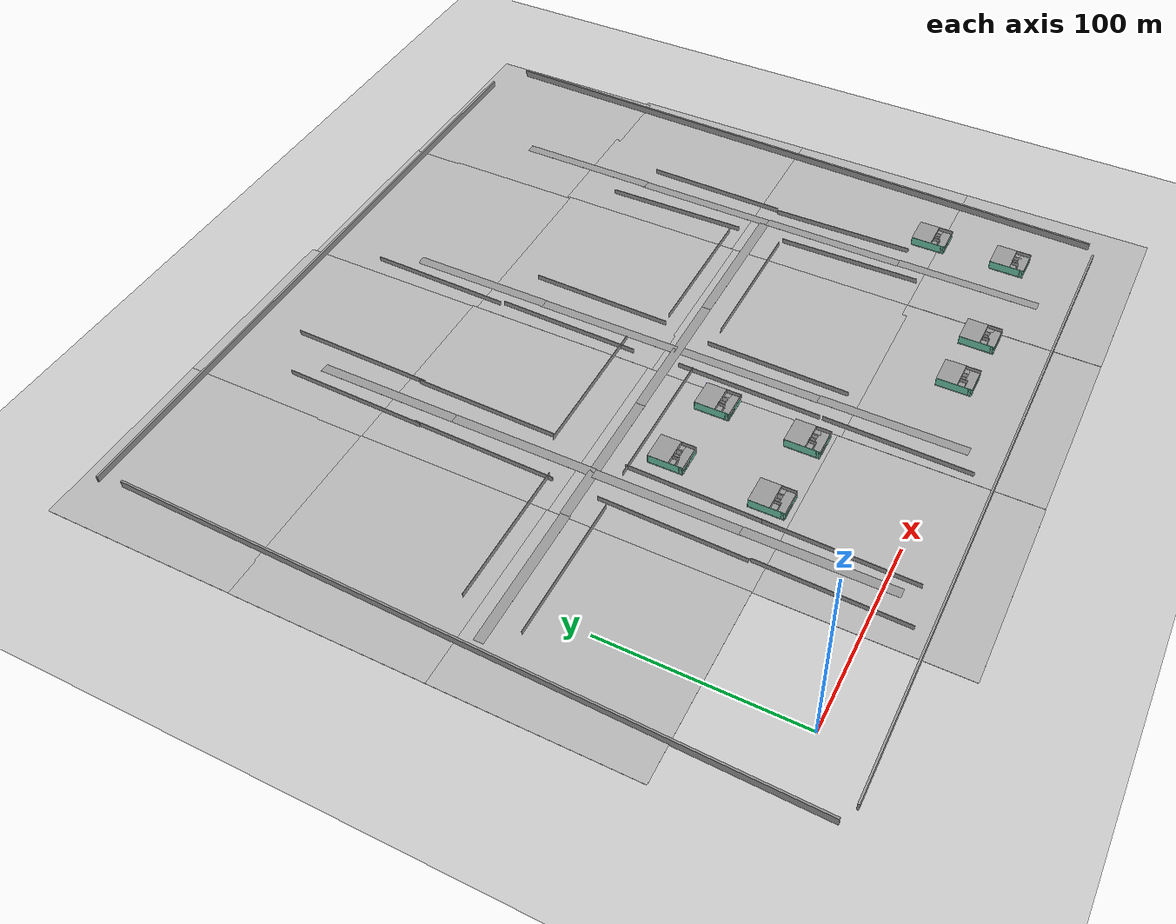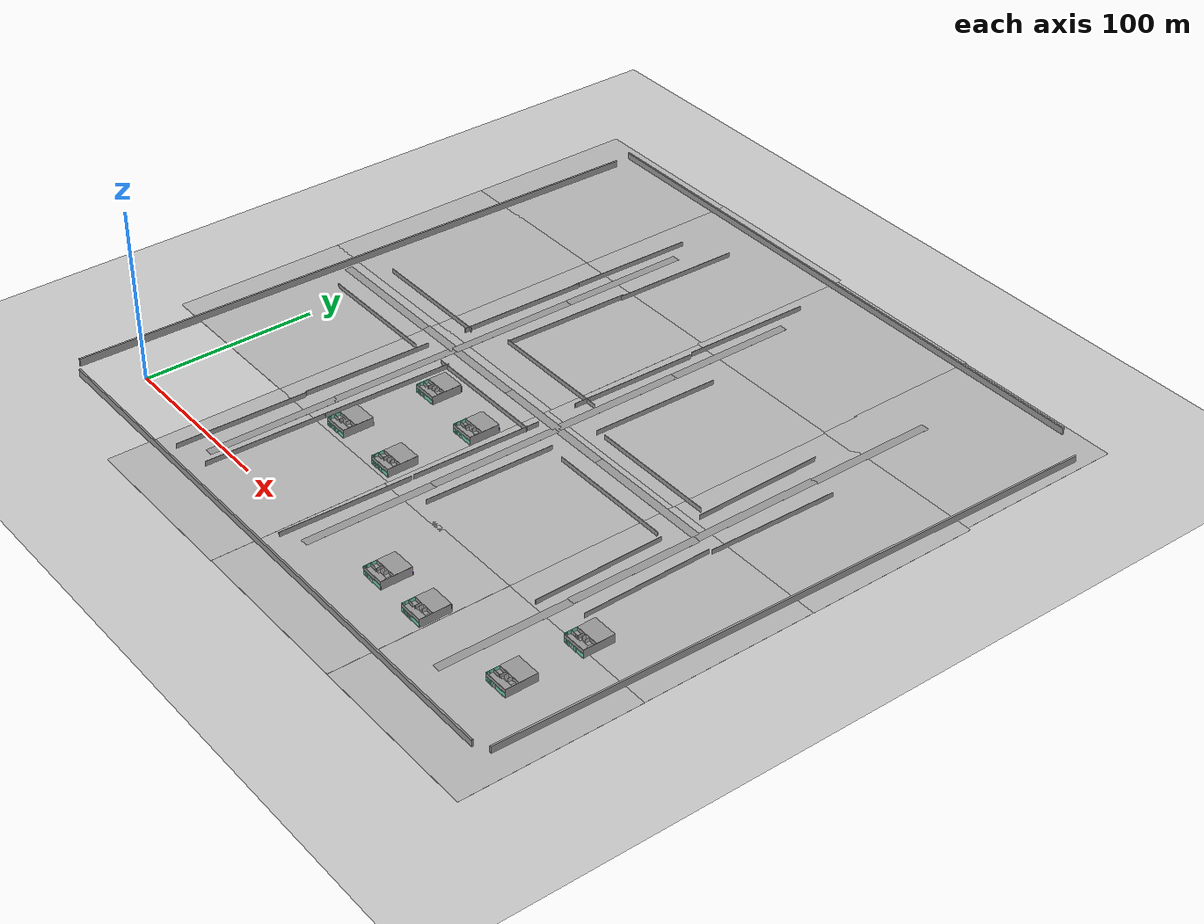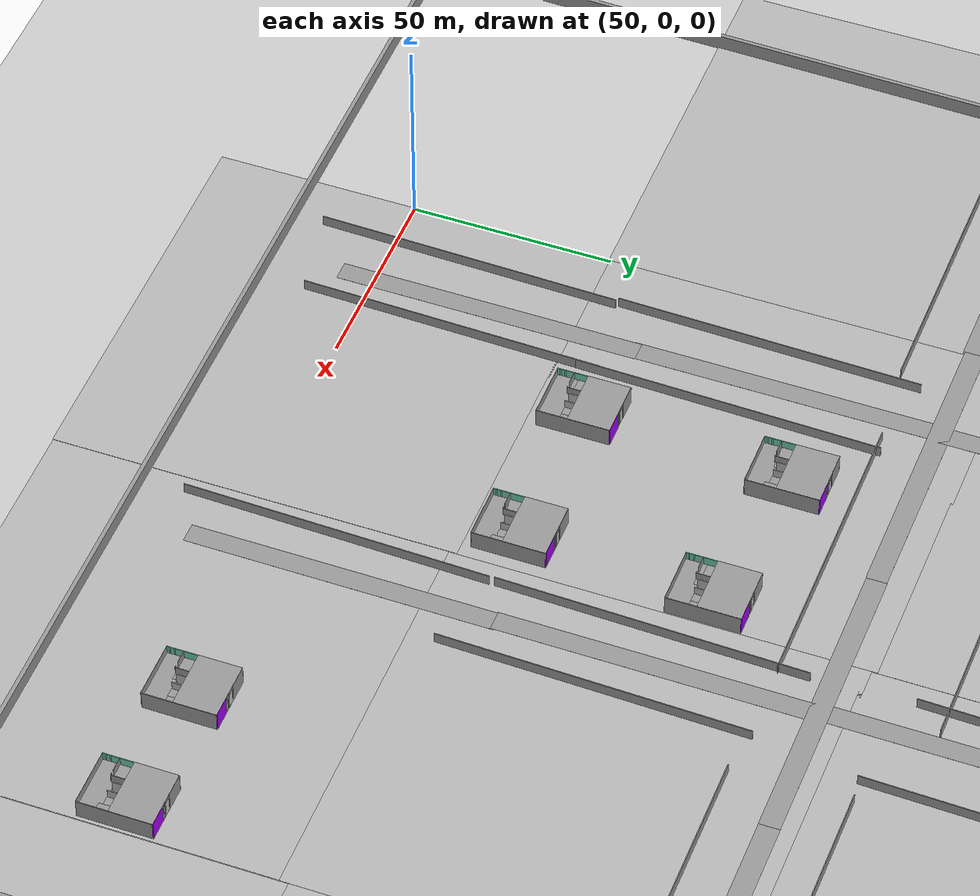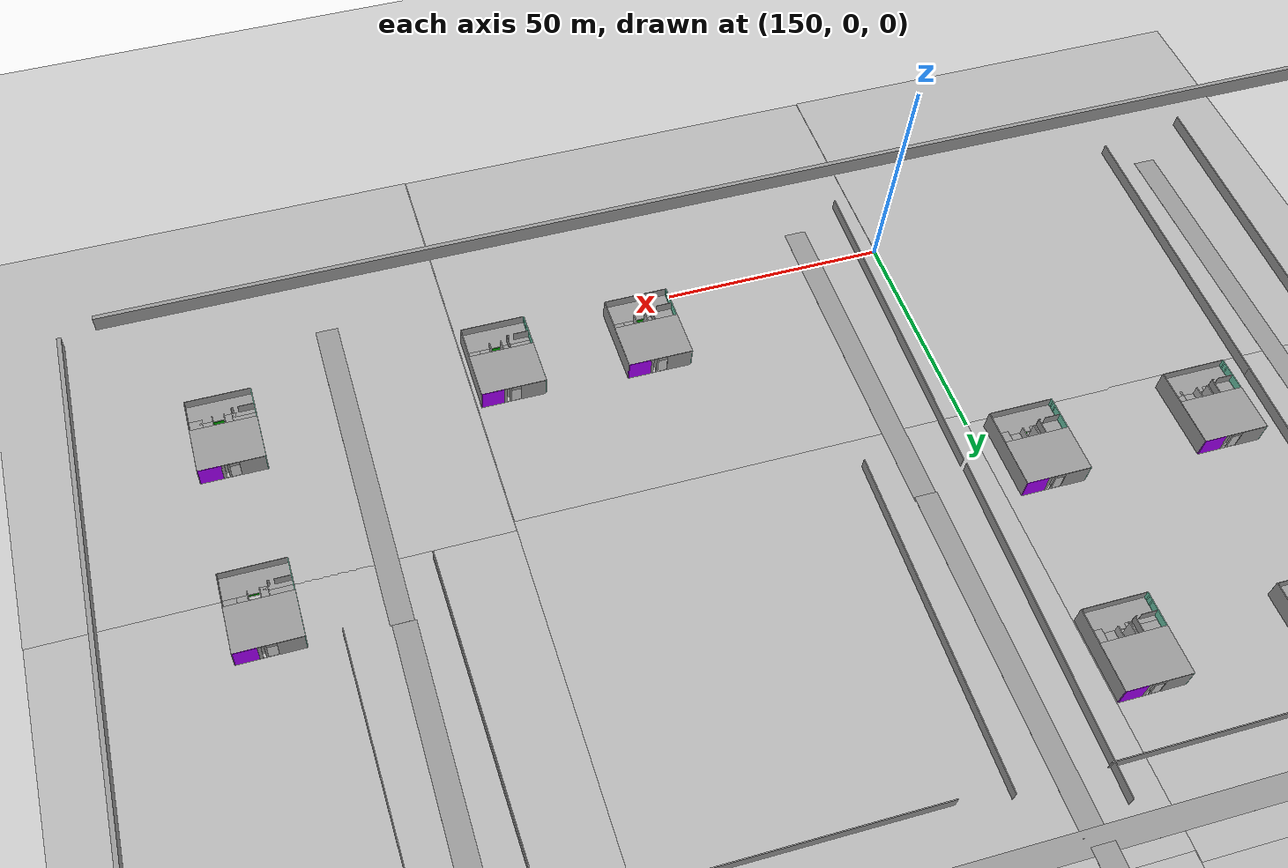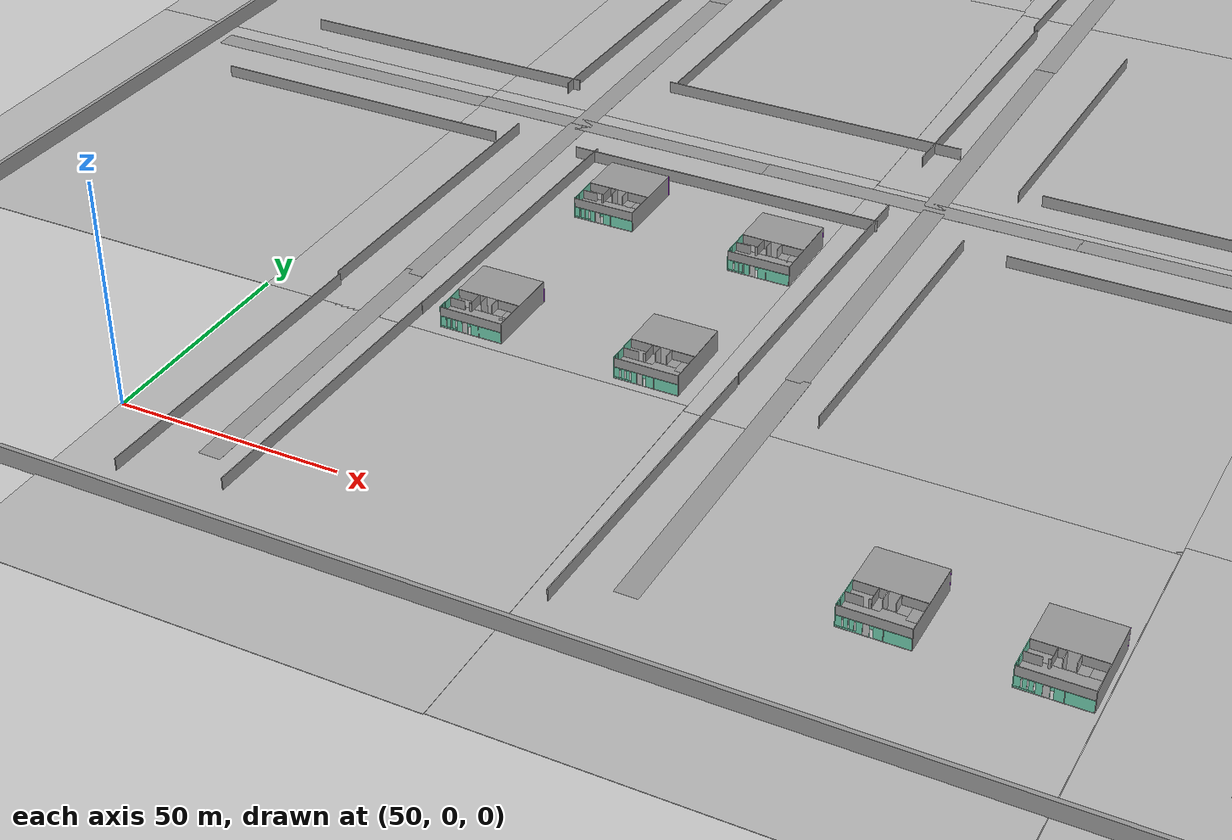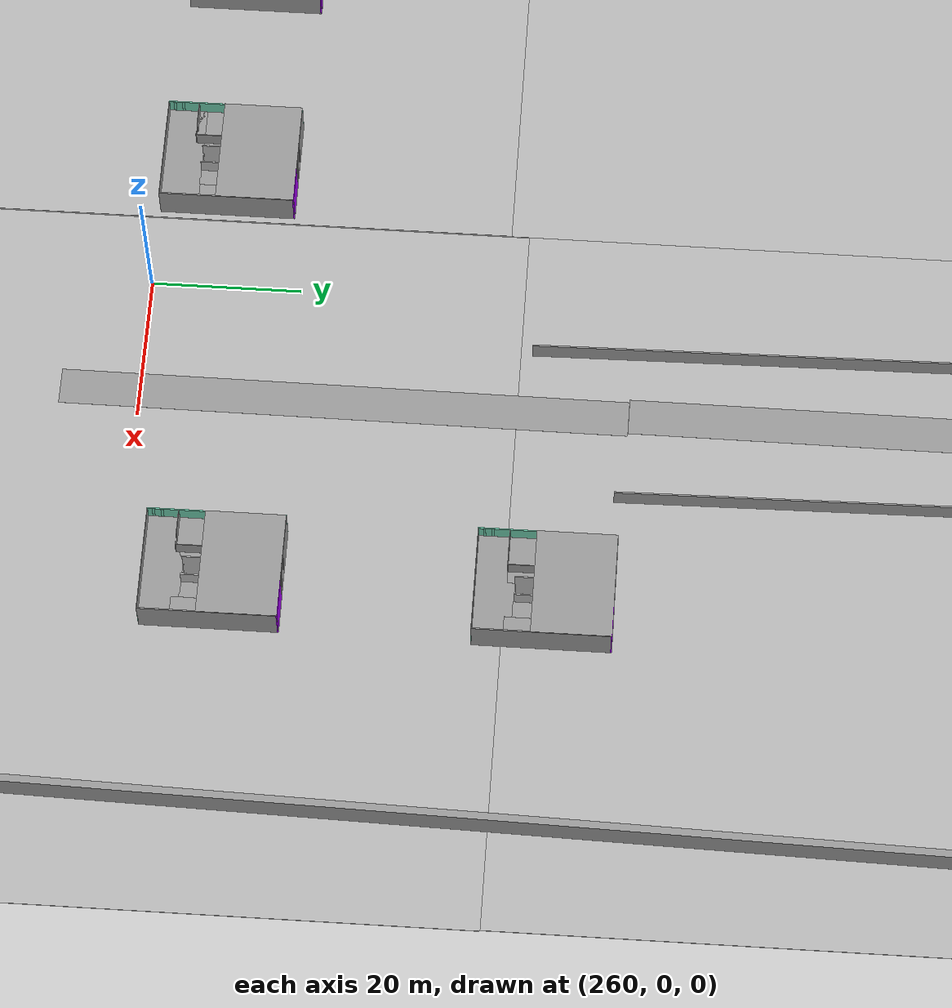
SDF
<sdf version="1.6">
 <world name="default">
  <light name="sun" type="directional">
   <pose>0 0 10 0 -0 0</pose>
   <diffuse>0.8 0.8 0.8 1</diffuse>
   <specular>0.1 0.1 0.1 1</specular>
   <attenuation>
    <range>1000</range>
    <constant>0.9</constant>
    <linear>0.01</linear>
    <quadratic>0.001</quadratic>
   </attenuation>
   <direction>-0.5 0.5 -1</direction>
  </light>
  <gravity>0 0 -9.8</gravity>
  <magnetic_field>6e-06 2.3e-05 -4.2e-05</magnetic_field>
  <atmosphere type="adiabatic"/>
  <physics name="default_physics" default="0" type="ode">
   <max_step_size>0.001</max_step_size>
   <real_time_factor>1</real_time_factor>
   <real_time_update_rate>1000</real_time_update_rate>
  </physics>
  <scene><ambient>0.4 0.4 0.4 1</ambient><background>0.7 0.7 0.7 1</background><shadows>1</shadows></scene>
  <spherical_coordinates>
   <surface_model>EARTH_WGS84</surface_model>
   <latitude_deg>0</latitude_deg>
   <longitude_deg>0</longitude_deg>
   <elevation>0</elevation>
   <heading_deg>0</heading_deg>
  </spherical_coordinates>
  <model name="ground1">
   <static>1</static>
   <link name="link">
    <collision name="collision">
     <geometry><plane><normal>0 0 1</normal><size>100 100</size></plane></geometry>
     <surface><friction><ode><mu>100</mu><mu2>50</mu2></ode></friction></surface>
    </collision>
    <visual name="visual">
     <cast_shadows>0</cast_shadows>
     <geometry><plane><normal>0 0 1</normal><size>100 100</size></plane></geometry>
     <material>
      <script>
       <uri>model://ground1/materials/scripts</uri>
       <uri>model://ground1/materials/textures/</uri>
       <name>ground1/Image</name>
      </script>
     </material>
    </visual>
   </link>
  </model>
  <model name="ground1_0">
   <static>1</static>
   <link name="link">
    <collision name="collision">
     <geometry><plane><normal>0 0 1</normal><size>100 100</size></plane></geometry>
     <surface><friction><ode><mu>100</mu><mu2>50</mu2></ode></friction></surface>
    </collision>
    <visual name="visual">
     <cast_shadows>0</cast_shadows>
     <geometry><plane><normal>0 0 1</normal><size>100 100</size></plane></geometry>
     <material>
      <script>
       <uri>model://ground1/materials/scripts</uri>
       <uri>model://ground1/materials/textures/</uri>
       <name>ground1/Image</name>
      </script>
     </material>
    </visual>
   </link>
   <pose>99.6657 -0.19904 0 0 -0 0</pose>
  </model>
  <model name="ground1_1">
   <static>1</static>
   <link name="link">
    <collision name="collision">
     <geometry><plane><normal>0 0 1</normal><size>100 100</size></plane></geometry>
     <surface><friction><ode><mu>100</mu><mu2>50</mu2></ode></friction></surface>
    </collision>
    <visual name="visual">
     <cast_shadows>0</cast_shadows>
     <geometry><plane><normal>0 0 1</normal><size>100 100</size></plane></geometry>
     <material>
      <script>
       <uri>model://ground1/materials/scripts</uri>
       <uri>model://ground1/materials/textures/</uri>
       <name>ground1/Image</name>
      </script>
     </material>
    </visual>
   </link>
   <pose>199.726 0.006846 0 0 -0 0</pose>
  </model>
  <model name="ground1_2">
   <static>1</static>
   <link name="link">
    <collision name="collision">
     <geometry><plane><normal>0 0 1</normal><size>100 100</size></plane></geometry>
     <surface><friction><ode><mu>100</mu><mu2>50</mu2></ode></friction></surface>
    </collision>
    <visual name="visual">
     <cast_shadows>0</cast_shadows>
     <geometry><plane><normal>0 0 1</normal><size>100 100</size></plane></geometry>
     <material>
      <script>
       <uri>model://ground1/materials/scripts</uri>
       <uri>model://ground1/materials/textures/</uri>
       <name>ground1/Image</name>
      </script>
     </material>
    </visual>
   </link>
   <pose>299.887 -0.1094 0 0 -0 0</pose>
  </model>
  <model name="ground1_3">
   <static>1</static>
   <link name="link">
    <collision name="collision">
     <geometry><plane><normal>0 0 1</normal><size>100 100</size></plane></geometry>
     <surface><friction><ode><mu>100</mu><mu2>50</mu2></ode></friction></surface>
    </collision>
    <visual name="visual">
     <cast_shadows>0</cast_shadows>
     <geometry><plane><normal>0 0 1</normal><size>100 100</size></plane></geometry>
     <material>
      <script>
       <uri>model://ground1/materials/scripts</uri>
       <uri>model://ground1/materials/textures/</uri>
       <name>ground1/Image</name>
      </script>
     </material>
    </visual>
   </link>
   <pose>-0.015678 99.5294 0 0 -0 0</pose>
  </model>
  <model name="ground1_4">
   <static>1</static>
   <link name="link">
    <collision name="collision">
     <geometry><plane><normal>0 0 1</normal><size>100 100</size></plane></geometry>
     <surface><friction><ode><mu>100</mu><mu2>50</mu2></ode></friction></surface>
    </collision>
    <visual name="visual">
     <cast_shadows>0</cast_shadows>
     <geometry><plane><normal>0 0 1</normal><size>100 100</size></plane></geometry>
     <material>
      <script>
       <uri>model://ground1/materials/scripts</uri>
       <uri>model://ground1/materials/textures/</uri>
       <name>ground1/Image</name>
      </script>
     </material>
    </visual>
   </link>
   <pose>-0.010142 199.089 0 0 -0 0</pose>
  </model>
  <model name="ground1_5">
   <static>1</static>
   <link name="link">
    <collision name="collision">
     <geometry><plane><normal>0 0 1</normal><size>100 100</size></plane></geometry>
     <surface><friction><ode><mu>100</mu><mu2>50</mu2></ode></friction></surface>
    </collision>
    <visual name="visual">
     <cast_shadows>0</cast_shadows>
     <geometry><plane><normal>0 0 1</normal><size>100 100</size></plane></geometry>
     <material>
      <script>
       <uri>model://ground1/materials/scripts</uri>
       <uri>model://ground1/materials/textures/</uri>
       <name>ground1/Image</name>
      </script>
     </material>
    </visual>
   </link>
   <pose>0.088534 298.479 0 0 -0 0</pose>
  </model>
  <model name="ground1_6">
   <static>1</static>
   <link name="link">
    <collision name="collision">
     <geometry><plane><normal>0 0 1</normal><size>100 100</size></plane></geometry>
     <surface><friction><ode><mu>100</mu><mu2>50</mu2></ode></friction></surface>
    </collision>
    <visual name="visual">
     <cast_shadows>0</cast_shadows>
     <geometry><plane><normal>0 0 1</normal><size>100 100</size></plane></geometry>
     <material>
      <script>
       <uri>model://ground1/materials/scripts</uri>
       <uri>model://ground1/materials/textures/</uri>
       <name>ground1/Image</name>
      </script>
     </material>
    </visual>
   </link>
   <pose>99.798 99.4123 0 0 -0 0</pose>
  </model>
  <model name="ground1_7">
   <static>1</static>
   <link name="link">
    <collision name="collision">
     <geometry><plane><normal>0 0 1</normal><size>100 100</size></plane></geometry>
     <surface><friction><ode><mu>100</mu><mu2>50</mu2></ode></friction></surface>
    </collision>
    <visual name="visual">
     <cast_shadows>0</cast_shadows>
     <geometry><plane><normal>0 0 1</normal><size>100 100</size></plane></geometry>
     <material>
      <script>
       <uri>model://ground1/materials/scripts</uri>
       <uri>model://ground1/materials/textures/</uri>
       <name>ground1/Image</name>
      </script>
     </material>
    </visual>
   </link>
   <pose>99.9085 198.843 0 0 -0 0</pose>
  </model>
  <model name="ground1_8">
   <static>1</static>
   <link name="link">
    <collision name="collision">
     <geometry><plane><normal>0 0 1</normal><size>100 100</size></plane></geometry>
     <surface><friction><ode><mu>100</mu><mu2>50</mu2></ode></friction></surface>
    </collision>
    <visual name="visual">
     <cast_shadows>0</cast_shadows>
     <geometry><plane><normal>0 0 1</normal><size>100 100</size></plane></geometry>
     <material>
      <script>
       <uri>model://ground1/materials/scripts</uri>
       <uri>model://ground1/materials/textures/</uri>
       <name>ground1/Image</name>
      </script>
     </material>
    </visual>
   </link>
   <pose>99.5435 298.797 0 0 -0 0</pose>
  </model>
  <model name="ground1_9">
   <static>1</static>
   <link name="link">
    <collision name="collision">
     <geometry><plane><normal>0 0 1</normal><size>100 100</size></plane></geometry>
     <surface><friction><ode><mu>100</mu><mu2>50</mu2></ode></friction></surface>
    </collision>
    <visual name="visual">
     <cast_shadows>0</cast_shadows>
     <geometry><plane><normal>0 0 1</normal><size>100 100</size></plane></geometry>
     <material>
      <script>
       <uri>model://ground1/materials/scripts</uri>
       <uri>model://ground1/materials/textures/</uri>
       <name>ground1/Image</name>
      </script>
     </material>
    </visual>
   </link>
   <pose>199.793 97.511 0 0 -0 0</pose>
  </model>
  <model name="ground1_10">
   <static>1</static>
   <link name="link">
    <collision name="collision">
     <geometry><plane><normal>0 0 1</normal><size>100 100</size></plane></geometry>
     <surface><friction><ode><mu>100</mu><mu2>50</mu2></ode></friction></surface>
    </collision>
    <visual name="visual">
     <cast_shadows>0</cast_shadows>
     <geometry><plane><normal>0 0 1</normal><size>100 100</size></plane></geometry>
     <material>
      <script>
       <uri>model://ground1/materials/scripts</uri>
       <uri>model://ground1/materials/textures/</uri>
       <name>ground1/Image</name>
      </script>
     </material>
    </visual>
   </link>
   <pose>199.932 196.579 0 0 -0 0</pose>
  </model>
  <model name="ground1_11">
   <static>1</static>
   <link name="link">
    <collision name="collision">
     <geometry><plane><normal>0 0 1</normal><size>100 100</size></plane></geometry>
     <surface><friction><ode><mu>100</mu><mu2>50</mu2></ode></friction></surface>
    </collision>
    <visual name="visual">
     <cast_shadows>0</cast_shadows>
     <geometry><plane><normal>0 0 1</normal><size>100 100</size></plane></geometry>
     <material>
      <script>
       <uri>model://ground1/materials/scripts</uri>
       <uri>model://ground1/materials/textures/</uri>
       <name>ground1/Image</name>
      </script>
     </material>
    </visual>
   </link>
   <pose>198.849 296.294 0 0 -0 0</pose>
  </model>
  <model name="ground1_12">
   <static>1</static>
   <link name="link">
    <collision name="collision">
     <geometry><plane><normal>0 0 1</normal><size>100 100</size></plane></geometry>
     <surface><friction><ode><mu>100</mu><mu2>50</mu2></ode></friction></surface>
    </collision>
    <visual name="visual">
     <cast_shadows>0</cast_shadows>
     <geometry><plane><normal>0 0 1</normal><size>100 100</size></plane></geometry>
     <material>
      <script>
       <uri>model://ground1/materials/scripts</uri>
       <uri>model://ground1/materials/textures/</uri>
       <name>ground1/Image</name>
      </script>
     </material>
    </visual>
   </link>
   <pose>299.79 99.7189 0 0 -0 0</pose>
  </model>
  <model name="ground1_13">
   <static>1</static>
   <link name="link">
    <collision name="collision">
     <geometry><plane><normal>0 0 1</normal><size>100 100</size></plane></geometry>
     <surface><friction><ode><mu>100</mu><mu2>50</mu2></ode></friction></surface>
    </collision>
    <visual name="visual">
     <cast_shadows>0</cast_shadows>
     <geometry><plane><normal>0 0 1</normal><size>100 100</size></plane></geometry>
     <material>
      <script>
       <uri>model://ground1/materials/scripts</uri>
       <uri>model://ground1/materials/textures/</uri>
       <name>ground1/Image</name>
      </script>
     </material>
    </visual>
   </link>
   <pose>299.867 198.453 0 0 -0 0</pose>
  </model>
  <model name="ground1_14">
   <static>1</static>
   <link name="link">
    <collision name="collision">
     <geometry><plane><normal>0 0 1</normal><size>100 100</size></plane></geometry>
     <surface><friction><ode><mu>100</mu><mu2>50</mu2></ode></friction></surface>
    </collision>
    <visual name="visual">
     <cast_shadows>0</cast_shadows>
     <geometry><plane><normal>0 0 1</normal><size>100 100</size></plane></geometry>
     <material>
      <script>
       <uri>model://ground1/materials/scripts</uri>
       <uri>model://ground1/materials/textures/</uri>
       <name>ground1/Image</name>
      </script>
     </material>
    </visual>
   </link>
   <pose>298.026 295.733 0 0 -0 0</pose>
  </model>
  <model name="osrf_elevator">
   <link name="Wall_0">
    <pose>-7.17647 0.013004 0 0 -0 1.57174</pose>
    <visual name="Wall_0_Visual_0">
     <meta><layer>0</layer></meta>
     <pose>-8.72596 0 2.4385 0 -0 0</pose>
     <geometry><box><size>0.663656 0.15 4.877</size></box></geometry>
     <material>
      <script><uri>file://media/materials/scripts/gazebo.material</uri><name>Gazebo/Grey</name></script>
      <ambient>0.435294 0.796078 0.67451 1</ambient>
     </material>
    </visual>
    <collision name="Wall_0_Collision_0">
     <geometry><box><size>0.663656 0.15 4.877</size></box></geometry>
     <pose>-8.72596 0 2.4385 0 -0 0</pose>
    </collision>
    <visual name="Wall_0_Visual_1">
     <meta><layer>0</layer></meta>
     <pose>0.331828 0 0.25 0 -0 0</pose>
     <geometry><box><size>17.4519 0.15 0.5</size></box></geometry>
     <material>
      <script><uri>file://media/materials/scripts/gazebo.material</uri><name>Gazebo/Grey</name></script>
      <ambient>0.435294 0.796078 0.67451 1</ambient>
     </material>
    </visual>
    <collision name="Wall_0_Collision_1">
     <geometry><box><size>17.4519 0.15 0.5</size></box></geometry>
     <pose>0.331828 0 0.25 0 -0 0</pose>
    </collision>
    <visual name="Wall_0_Visual_2">
     <meta><layer>0</layer></meta>
     <pose>-7.67281 0 2.6885 0 -0 0</pose>
     <geometry><box><size>0.816657 0.15 4.377</size></box></geometry>
     <material>
      <script><uri>file://media/materials/scripts/gazebo.material</uri><name>Gazebo/Grey</name></script>
      <ambient>0.435294 0.796078 0.67451 1</ambient>
     </material>
    </visual>
    <collision name="Wall_0_Collision_2">
     <geometry><box><size>0.816657 0.15 4.377</size></box></geometry>
     <pose>-7.67281 0 2.6885 0 -0 0</pose>
    </collision>
    <visual name="Wall_0_Visual_3">
     <meta><layer>0</layer></meta>
     <pose>1.05709 0 2.6885 0 -0 0</pose>
     <geometry><box><size>16.0014 0.15 4.377</size></box></geometry>
     <material>
      <script><uri>file://media/materials/scripts/gazebo.material</uri><name>Gazebo/Grey</name></script>
      <ambient>0.435294 0.796078 0.67451 1</ambient>
     </material>
    </visual>
    <collision name="Wall_0_Collision_3">
     <geometry><box><size>16.0014 0.15 4.377</size></box></geometry>
     <pose>1.05709 0 2.6885 0 -0 0</pose>
    </collision>
    <visual name="Wall_0_Visual_4">
     <meta><layer>0</layer></meta>
     <pose>-8.23763 0 3.6885 0 -0 0</pose>
     <geometry><box><size>0.313 0.15 2.377</size></box></geometry>
     <material>
      <script><uri>file://media/materials/scripts/gazebo.material</uri><name>Gazebo/Grey</name></script>
      <ambient>0.435294 0.796078 0.67451 1</ambient>
     </material>
    </visual>
    <collision name="Wall_0_Collision_4">
     <geometry><box><size>0.313 0.15 2.377</size></box></geometry>
     <pose>-8.23763 0 3.6885 0 -0 0</pose>
    </collision>
    <visual name="Wall_0_Visual_5">
     <meta><layer>0</layer></meta>
     <pose>-7.10405 0 3.6885 0 -0 0</pose>
     <geometry><box><size>0.320861 0.15 2.377</size></box></geometry>
     <material>
      <script><uri>file://media/materials/scripts/gazebo.material</uri><name>Gazebo/Grey</name></script>
      <ambient>0.435294 0.796078 0.67451 1</ambient>
     </material>
    </visual>
    <collision name="Wall_0_Collision_5">
     <geometry><box><size>0.320861 0.15 2.377</size></box></geometry>
     <pose>-7.10405 0 3.6885 0 -0 0</pose>
    </collision>
   </link>
   <link name="Wall_10">
    <pose>3.11003 -4.9485 0 0 -0 0</pose>
    <visual name="Wall_10_Visual_0">
     <meta><layer>0</layer></meta>
     <pose>-1.73626 0 1.3715 0 -0 0</pose>
     <geometry><box><size>4.52747 0.15 2.743</size></box></geometry>
     <material>
      <script><uri>file://media/materials/scripts/gazebo.material</uri><name>Gazebo/Grey</name></script>
      <ambient>0 0.666667 0 1</ambient>
     </material>
    </visual>
    <collision name="Wall_10_Collision_0">
     <geometry><box><size>4.52747 0.15 2.743</size></box></geometry>
     <pose>-1.73626 0 1.3715 0 -0 0</pose>
    </collision>
    <visual name="Wall_10_Visual_1">
     <meta><layer>0</layer></meta>
     <pose>2.58694 0 1.3715 0 -0 0</pose>
     <geometry><box><size>2.82611 0.15 2.743</size></box></geometry>
     <material>
      <script><uri>file://media/materials/scripts/gazebo.material</uri><name>Gazebo/Grey</name></script>
      <ambient>0 0.666667 0 1</ambient>
     </material>
    </visual>
    <collision name="Wall_10_Collision_1">
     <geometry><box><size>2.82611 0.15 2.743</size></box></geometry>
     <pose>2.58694 0 1.3715 0 -0 0</pose>
    </collision>
    <visual name="Wall_10_Visual_2">
     <meta><layer>0</layer></meta>
     <pose>0.85068 0 2.3715 0 -0 0</pose>
     <geometry><box><size>0.646413 0.15 0.743</size></box></geometry>
     <material>
      <script><uri>file://media/materials/scripts/gazebo.material</uri><name>Gazebo/Grey</name></script>
      <ambient>0 0.666667 0 1</ambient>
     </material>
    </visual>
    <collision name="Wall_10_Collision_2">
     <geometry><box><size>0.646413 0.15 0.743</size></box></geometry>
     <pose>0.85068 0 2.3715 0 -0 0</pose>
    </collision>
   </link>
   <link name="Wall_14">
    <pose>1.83803 -6.9775 0 0 -0 1.5708</pose>
    <visual name="Wall_14_Visual_0">
     <meta><layer>0</layer></meta>
     <pose>-0.387674 0 1.3715 0 -0 0</pose>
     <geometry><box><size>3.41138 0.15 2.743</size></box></geometry>
     <material>
      <script><uri>file://media/materials/scripts/gazebo.material</uri><name>Gazebo/Grey</name></script>
      <ambient>1 1 1 1</ambient>
     </material>
    </visual>
    <collision name="Wall_14_Collision_0">
     <geometry><box><size>3.41138 0.15 2.743</size></box></geometry>
     <pose>-0.387674 0 1.3715 0 -0 0</pose>
    </collision>
    <visual name="Wall_14_Visual_1">
     <meta><layer>0</layer></meta>
     <pose>2.00133 0 1.3715 0 -0 0</pose>
     <geometry><box><size>0.184063 0.15 2.743</size></box></geometry>
     <material>
      <script><uri>file://media/materials/scripts/gazebo.material</uri><name>Gazebo/Grey</name></script>
      <ambient>1 1 1 1</ambient>
     </material>
    </visual>
    <collision name="Wall_14_Collision_1">
     <geometry><box><size>0.184063 0.15 2.743</size></box></geometry>
     <pose>2.00133 0 1.3715 0 -0 0</pose>
    </collision>
    <visual name="Wall_14_Visual_2">
     <meta><layer>0</layer></meta>
     <pose>1.61366 0 2.3715 0 -0 0</pose>
     <geometry><box><size>0.591285 0.15 0.743</size></box></geometry>
     <material>
      <script><uri>file://media/materials/scripts/gazebo.material</uri><name>Gazebo/Grey</name></script>
      <ambient>1 1 1 1</ambient>
     </material>
    </visual>
    <collision name="Wall_14_Collision_2">
     <geometry><box><size>0.591285 0.15 0.743</size></box></geometry>
     <pose>1.61366 0 2.3715 0 -0 0</pose>
    </collision>
   </link>
   <link name="Wall_16">
    <collision name="Wall_16_Collision">
     <geometry><box><size>5.12727 0.15 2.743</size></box></geometry>
     <pose>0 0 1.3715 0 -0 0</pose>
    </collision>
    <visual name="Wall_16_Visual">
     <meta><layer>0</layer></meta>
     <pose>0 0 1.3715 0 -0 0</pose>
     <geometry><box><size>5.12727 0.15 2.743</size></box></geometry>
     <material>
      <script><uri>file://media/materials/scripts/gazebo.material</uri><name>Gazebo/Grey</name></script>
      <ambient>1 1 1 1</ambient>
     </material>
    </visual>
    <pose>-4.68247 -1.4425 0 0 -0 0</pose>
   </link>
   <link name="Wall_17">
    <pose>-2.19097 -3.185 0 0 0 -1.56907</pose>
    <visual name="Wall_17_Visual_0">
     <meta><layer>0</layer></meta>
     <pose>-1.22855 0 1.3715 0 -0 0</pose>
     <geometry><box><size>1.17851 0.15 2.743</size></box></geometry>
     <material>
      <script><uri>file://media/materials/scripts/gazebo.material</uri><name>Gazebo/Grey</name></script>
      <ambient>1 1 1 1</ambient>
     </material>
    </visual>
    <collision name="Wall_17_Collision_0">
     <geometry><box><size>1.17851 0.15 2.743</size></box></geometry>
     <pose>-1.22855 0 1.3715 0 -0 0</pose>
    </collision>
    <visual name="Wall_17_Visual_1">
     <meta><layer>0</layer></meta>
     <pose>0.886237 0 1.3715 0 -0 0</pose>
     <geometry><box><size>1.86314 0.15 2.743</size></box></geometry>
     <material>
      <script><uri>file://media/materials/scripts/gazebo.material</uri><name>Gazebo/Grey</name></script>
      <ambient>1 1 1 1</ambient>
     </material>
    </visual>
    <collision name="Wall_17_Collision_1">
     <geometry><box><size>1.86314 0.15 2.743</size></box></geometry>
     <pose>0.886237 0 1.3715 0 -0 0</pose>
    </collision>
    <visual name="Wall_17_Visual_2">
     <meta><layer>0</layer></meta>
     <pose>1.18873 0 1.3715 0 -0 0</pose>
     <geometry><box><size>1.25815 0.15 2.743</size></box></geometry>
     <material>
      <script><uri>file://media/materials/scripts/gazebo.material</uri><name>Gazebo/Grey</name></script>
      <ambient>1 1 1 1</ambient>
     </material>
    </visual>
    <collision name="Wall_17_Collision_2">
     <geometry><box><size>1.25815 0.15 2.743</size></box></geometry>
     <pose>1.18873 0 1.3715 0 -0 0</pose>
    </collision>
    <visual name="Wall_17_Visual_3">
     <meta><layer>0</layer></meta>
     <pose>-0.345304 0 2.3715 0 -0 0</pose>
     <geometry><box><size>0.587991 0.15 0.743</size></box></geometry>
     <material>
      <script><uri>file://media/materials/scripts/gazebo.material</uri><name>Gazebo/Grey</name></script>
      <ambient>1 1 1 1</ambient>
     </material>
    </visual>
    <collision name="Wall_17_Collision_3">
     <geometry><box><size>0.587991 0.15 0.743</size></box></geometry>
     <pose>-0.345304 0 2.3715 0 -0 0</pose>
    </collision>
   </link>
   <link name="Wall_18">
    <collision name="Wall_18_Collision">
     <geometry><box><size>5 0.15 2.743</size></box></geometry>
     <pose>0 0 1.3715 0 -0 0</pose>
    </collision>
    <visual name="Wall_18_Visual">
     <meta><layer>0</layer></meta>
     <pose>0 0 1.3715 0 -0 0</pose>
     <geometry><box><size>5 0.15 2.743</size></box></geometry>
     <material>
      <script><uri>file://media/materials/scripts/gazebo.material</uri><name>Gazebo/Grey</name></script>
      <ambient>1 1 1 1</ambient>
     </material>
    </visual>
    <pose>-4.61297 -4.9275 0 0 -0 3.14159</pose>
   </link>
   <link name="Wall_20">
    <collision name="Wall_20_Collision">
     <geometry><box><size>2.88731 0.15 2.743</size></box></geometry>
     <pose>0 0 1.3715 0 -0 0</pose>
    </collision>
    <visual name="Wall_20_Visual">
     <meta><layer>0</layer></meta>
     <pose>0 0 1.3715 0 -0 0</pose>
     <geometry><box><size>2.88731 0.15 2.743</size></box></geometry>
     <material>
      <script><uri>file://media/materials/scripts/gazebo.material</uri><name>Gazebo/Grey</name></script>
      <ambient>1 1 1 1</ambient>
     </material>
    </visual>
    <pose>5.74253 1.037 0 0 0 -3.1383</pose>
   </link>
   <link name="Wall_21">
    <pose>4.37403 -1.8925 0 0 0 -1.5708</pose>
    <visual name="Wall_21_Visual_0">
     <meta><layer>0</layer></meta>
     <pose>-2.34405 0 1.3715 0 -0 0</pose>
     <geometry><box><size>1.3119 0.15 2.743</size></box></geometry>
     <material>
      <script><uri>file://media/materials/scripts/gazebo.material</uri><name>Gazebo/Grey</name></script>
      <ambient>1 1 1 1</ambient>
     </material>
    </visual>
    <collision name="Wall_21_Collision_0">
     <geometry><box><size>1.3119 0.15 2.743</size></box></geometry>
     <pose>-2.34405 0 1.3715 0 -0 0</pose>
    </collision>
    <visual name="Wall_21_Visual_1">
     <meta><layer>0</layer></meta>
     <pose>-0.970323 0 1.3715 0 -0 0</pose>
     <geometry><box><size>0.213619 0.15 2.743</size></box></geometry>
     <material>
      <script><uri>file://media/materials/scripts/gazebo.material</uri><name>Gazebo/Grey</name></script>
      <ambient>1 1 1 1</ambient>
     </material>
    </visual>
    <collision name="Wall_21_Collision_1">
     <geometry><box><size>0.213619 0.15 2.743</size></box></geometry>
     <pose>-0.970323 0 1.3715 0 -0 0</pose>
    </collision>
    <visual name="Wall_21_Visual_2">
     <meta><layer>0</layer></meta>
     <pose>0.938748 0 1.3715 0 -0 0</pose>
     <geometry><box><size>2.36558 0.15 2.743</size></box></geometry>
     <material>
      <script><uri>file://media/materials/scripts/gazebo.material</uri><name>Gazebo/Grey</name></script>
      <ambient>1 1 1 1</ambient>
     </material>
    </visual>
    <collision name="Wall_21_Collision_2">
     <geometry><box><size>2.36558 0.15 2.743</size></box></geometry>
     <pose>0.938748 0 1.3715 0 -0 0</pose>
    </collision>
    <visual name="Wall_21_Visual_3">
     <meta><layer>0</layer></meta>
     <pose>2.89346 0 1.3715 0 -0 0</pose>
     <geometry><box><size>0.213086 0.15 2.743</size></box></geometry>
     <material>
      <script><uri>file://media/materials/scripts/gazebo.material</uri><name>Gazebo/Grey</name></script>
      <ambient>1 1 1 1</ambient>
     </material>
    </visual>
    <collision name="Wall_21_Collision_3">
     <geometry><box><size>0.213086 0.15 2.743</size></box></geometry>
     <pose>2.89346 0 1.3715 0 -0 0</pose>
    </collision>
    <visual name="Wall_21_Visual_4">
     <meta><layer>0</layer></meta>
     <pose>-1.38262 0 2.3715 0 -0 0</pose>
     <geometry><box><size>0.610969 0.15 0.743</size></box></geometry>
     <material>
      <script><uri>file://media/materials/scripts/gazebo.material</uri><name>Gazebo/Grey</name></script>
      <ambient>1 1 1 1</ambient>
     </material>
    </visual>
    <collision name="Wall_21_Collision_4">
     <geometry><box><size>0.610969 0.15 0.743</size></box></geometry>
     <pose>-1.38262 0 2.3715 0 -0 0</pose>
    </collision>
    <visual name="Wall_21_Visual_5">
     <meta><layer>0</layer></meta>
     <pose>-0.553779 0 2.3715 0 -0 0</pose>
     <geometry><box><size>0.61947 0.15 0.743</size></box></geometry>
     <material>
      <script><uri>file://media/materials/scripts/gazebo.material</uri><name>Gazebo/Grey</name></script>
      <ambient>1 1 1 1</ambient>
     </material>
    </visual>
    <collision name="Wall_21_Collision_5">
     <geometry><box><size>0.61947 0.15 0.743</size></box></geometry>
     <pose>-0.553779 0 2.3715 0 -0 0</pose>
    </collision>
    <visual name="Wall_21_Visual_6">
     <meta><layer>0</layer></meta>
     <pose>2.45423 0 2.3715 0 -0 0</pose>
     <geometry><box><size>0.665375 0.15 0.743</size></box></geometry>
     <material>
      <script><uri>file://media/materials/scripts/gazebo.material</uri><name>Gazebo/Grey</name></script>
      <ambient>1 1 1 1</ambient>
     </material>
    </visual>
    <collision name="Wall_21_Collision_6">
     <geometry><box><size>0.665375 0.15 0.743</size></box></geometry>
     <pose>2.45423 0 2.3715 0 -0 0</pose>
    </collision>
   </link>
   <link name="Wall_23">
    <collision name="Wall_23_Collision">
     <geometry><box><size>2.75 0.15 2.743</size></box></geometry>
     <pose>0 0 1.3715 0 -0 0</pose>
    </collision>
    <visual name="Wall_23_Visual">
     <meta><layer>0</layer></meta>
     <pose>0 0 1.3715 0 -0 0</pose>
     <geometry><box><size>2.75 0.15 2.743</size></box></geometry>
     <material>
      <script><uri>file://media/materials/scripts/gazebo.material</uri><name>Gazebo/Grey</name></script>
      <ambient>1 1 1 1</ambient>
     </material>
    </visual>
    <pose>5.74203 -2.9565 0 0 -0 0</pose>
   </link>
   <link name="Wall_25">
    <collision name="Wall_25_Collision">
     <geometry><box><size>2.75 0.15 2.743</size></box></geometry>
     <pose>0 0 1.3715 0 -0 0</pose>
    </collision>
    <visual name="Wall_25_Visual">
     <meta><layer>0</layer></meta>
     <pose>0 0 1.3715 0 -0 0</pose>
     <geometry><box><size>2.75 0.15 2.743</size></box></geometry>
     <material>
      <script><uri>file://media/materials/scripts/gazebo.material</uri><name>Gazebo/Grey</name></script>
      <ambient>1 1 1 1</ambient>
     </material>
    </visual>
    <pose>5.76203 -0.932496 0 0 -0 0</pose>
   </link>
   <link name="Wall_27">
    <collision name="Wall_27_Collision">
     <geometry><box><size>4 0.15 2.743</size></box></geometry>
     <pose>0 0 1.3715 0 -0 0</pose>
    </collision>
    <visual name="Wall_27_Visual">
     <meta><layer>0</layer></meta>
     <pose>0 0 1.3715 0 -0 0</pose>
     <geometry><box><size>4 0.15 2.743</size></box></geometry>
     <material>
      <script><uri>file://media/materials/scripts/gazebo.material</uri><name>Gazebo/Grey</name></script>
      <ambient>1 1 1 1</ambient>
     </material>
    </visual>
    <pose>4.75503 -7.0125 0 0 -0 1.5708</pose>
   </link>
   <link name="Wall_29">
    <collision name="Wall_29_Collision">
     <geometry><box><size>1.39187 0.15 4.877</size></box></geometry>
     <pose>0 0 2.4385 0 -0 0</pose>
    </collision>
    <visual name="Wall_29_Visual">
     <meta><layer>0</layer></meta>
     <pose>0 0 2.4385 0 -0 0</pose>
     <geometry><box><size>1.39187 0.15 4.877</size></box></geometry>
     <material>
      <script><uri>file://media/materials/scripts/gazebo.material</uri><name>Gazebo/Grey</name></script>
      <ambient>0.996078 0.47451 0.0196078 1</ambient>
     </material>
    </visual>
    <pose>-6.49697 4.1045 0 0 -0 0</pose>
   </link>
   <link name="Wall_30">
    <collision name="Wall_30_Collision">
     <geometry><box><size>3 0.15 4.877</size></box></geometry>
     <pose>0 0 2.4385 0 -0 0</pose>
    </collision>
    <visual name="Wall_30_Visual">
     <meta><layer>0</layer></meta>
     <pose>0 0 2.4385 0 -0 0</pose>
     <geometry><box><size>3 0.15 4.877</size></box></geometry>
     <material>
      <script><uri>file://media/materials/scripts/gazebo.material</uri><name>Gazebo/Grey</name></script>
      <ambient>1 1 1 1</ambient>
     </material>
    </visual>
    <pose>-5.87597 5.5295 0 0 -0 1.5708</pose>
   </link>
   <link name="Wall_31">
    <pose>-6.50397 6.9525 0 0 0 -3.13841</pose>
    <visual name="Wall_31_Visual_0">
     <meta><layer>0</layer></meta>
     <pose>-0.567544 0 2.4385 0 -0 0</pose>
     <geometry><box><size>0.271575 0.15 4.877</size></box></geometry>
     <material>
      <script><uri>file://media/materials/scripts/gazebo.material</uri><name>Gazebo/Grey</name></script>
      <ambient>1 1 1 1</ambient>
     </material>
    </visual>
    <collision name="Wall_31_Collision_0">
     <geometry><box><size>0.271575 0.15 4.877</size></box></geometry>
     <pose>-0.567544 0 2.4385 0 -0 0</pose>
    </collision>
    <visual name="Wall_31_Visual_1">
     <meta><layer>0</layer></meta>
     <pose>0.441678 0 2.4385 0 -0 0</pose>
     <geometry><box><size>0.523307 0.15 4.877</size></box></geometry>
     <material>
      <script><uri>file://media/materials/scripts/gazebo.material</uri><name>Gazebo/Grey</name></script>
      <ambient>1 1 1 1</ambient>
     </material>
    </visual>
    <collision name="Wall_31_Collision_1">
     <geometry><box><size>0.523307 0.15 4.877</size></box></geometry>
     <pose>0.441678 0 2.4385 0 -0 0</pose>
    </collision>
    <visual name="Wall_31_Visual_3">
     <meta><layer>0</layer></meta>
     <pose>-0.125866 0 3.4385 0 -0 0</pose>
     <geometry><box><size>0.611781 0.15 2.877</size></box></geometry>
     <material>
      <script><uri>file://media/materials/scripts/gazebo.material</uri><name>Gazebo/Grey</name></script>
      <ambient>1 1 1 1</ambient>
     </material>
    </visual>
    <collision name="Wall_31_Collision_3">
     <geometry><box><size>0.611781 0.15 2.877</size></box></geometry>
     <pose>-0.125866 0 3.4385 0 -0 0</pose>
    </collision>
   </link>
   <link name="Wall_35">
    <pose>-2.50997 8.9955 0 0 -0 0</pose>
    <visual name="Wall_35_Visual_0">
     <meta><layer>0</layer></meta>
     <pose>-1.92197 0 2.4385 0 -0 0</pose>
     <geometry><box><size>5.65606 0.15 4.877</size></box></geometry>
     <material>
      <script><uri>file://media/materials/scripts/gazebo.material</uri><name>Gazebo/Grey</name></script>
      <ambient>1 1 1 1</ambient>
     </material>
    </visual>
    <collision name="Wall_35_Collision_0">
     <geometry><box><size>5.65606 0.15 4.877</size></box></geometry>
     <pose>-1.92197 0 2.4385 0 -0 0</pose>
    </collision>
    <visual name="Wall_35_Visual_1">
     <meta><layer>0</layer></meta>
     <pose>3.22541 0 2.4385 0 -0 0</pose>
     <geometry><box><size>0.406701 0.15 4.877</size></box></geometry>
     <material>
      <script><uri>file://media/materials/scripts/gazebo.material</uri><name>Gazebo/Grey</name></script>
      <ambient>1 1 1 1</ambient>
     </material>
    </visual>
    <collision name="Wall_35_Collision_1">
     <geometry><box><size>0.406701 0.15 4.877</size></box></geometry>
     <pose>3.22541 0 2.4385 0 -0 0</pose>
    </collision>
    <visual name="Wall_35_Visual_2">
     <meta><layer>0</layer></meta>
     <pose>4.40208 0 2.4385 0 -0 0</pose>
     <geometry><box><size>0.695843 0.15 4.877</size></box></geometry>
     <material>
      <script><uri>file://media/materials/scripts/gazebo.material</uri><name>Gazebo/Grey</name></script>
      <ambient>1 1 1 1</ambient>
     </material>
    </visual>
    <collision name="Wall_35_Collision_2">
     <geometry><box><size>0.695843 0.15 4.877</size></box></geometry>
     <pose>4.40208 0 2.4385 0 -0 0</pose>
    </collision>
    <visual name="Wall_35_Visual_5">
     <meta><layer>0</layer></meta>
     <pose>3.74146 0 3.4385 0 -0 0</pose>
     <geometry><box><size>0.625391 0.15 2.877</size></box></geometry>
     <material>
      <script><uri>file://media/materials/scripts/gazebo.material</uri><name>Gazebo/Grey</name></script>
      <ambient>1 1 1 1</ambient>
     </material>
    </visual>
    <collision name="Wall_35_Collision_5">
     <geometry><box><size>0.625391 0.15 2.877</size></box></geometry>
     <pose>3.74146 0 3.4385 0 -0 0</pose>
    </collision>
    <visual name="Wall_35_Visual_6">
     <meta><layer>0</layer></meta>
     <pose>1.96406 0 4.4385 0 -0 0</pose>
     <geometry><box><size>2.116 0.15 0.877</size></box></geometry>
     <material>
      <script><uri>file://media/materials/scripts/gazebo.material</uri><name>Gazebo/Grey</name></script>
      <ambient>1 1 1 1</ambient>
     </material>
    </visual>
    <collision name="Wall_35_Collision_6">
     <geometry><box><size>2.116 0.15 0.877</size></box></geometry>
     <pose>1.96406 0 4.4385 0 -0 0</pose>
    </collision>
   </link>
   <link name="Wall_36">
    <collision name="Wall_36_Collision">
     <geometry><box><size>5.17 0.15 4.877</size></box></geometry>
     <pose>0 0 2.4385 0 -0 0</pose>
    </collision>
    <visual name="Wall_36_Visual">
     <meta><layer>0</layer></meta>
     <pose>0 0 2.4385 0 -0 0</pose>
     <geometry><box><size>5.17 0.15 4.877</size></box></geometry>
     <material>
      <script><uri>file://media/materials/scripts/gazebo.material</uri><name>Gazebo/Grey</name></script>
      <ambient>0.666667 0 1 1</ambient>
     </material>
    </visual>
    <pose>4.67503 8.9955 0 0 -0 0</pose>
   </link>
   <link name="Wall_5">
    <collision name="Wall_5_Collision">
     <geometry><box><size>18.1152 0.15 4.877</size></box></geometry>
     <pose>0 0 2.4385 0 -0 0</pose>
    </collision>
    <visual name="Wall_5_Visual">
     <meta><layer>0</layer></meta>
     <pose>0 0 2.4385 0 -0 0</pose>
     <geometry><box><size>18.1152 0.15 4.877</size></box></geometry>
     <material>
      <script><uri>file://media/materials/scripts/gazebo.material</uri><name>Gazebo/Grey</name></script>
      <ambient>1 1 1 1</ambient>
     </material>
    </visual>
    <pose>7.18353 0.013004 0 0 0 -1.57096</pose>
   </link>
   <link name="Wall_6">
    <pose>0.007029 -8.9695 0 0 -0 3.14159</pose>
    <visual name="Wall_6_Visual_0">
     <meta><layer>0</layer></meta>
     <pose>-3.60425 0 1.365 0 -0 0</pose>
     <geometry><box><size>7.2915 0.15 2.73</size></box></geometry>
     <material>
      <script><uri>file://media/materials/scripts/gazebo.material</uri><name>Gazebo/Grey</name></script>
      <ambient>0.435294 0.796078 0.67451 1</ambient>
     </material>
    </visual>
    <collision name="Wall_6_Collision_0">
     <geometry><box><size>7.2915 0.15 2.73</size></box></geometry>
     <pose>-3.60425 0 1.365 0 -0 0</pose>
    </collision>
    <visual name="Wall_6_Visual_1">
     <meta><layer>0</layer></meta>
     <pose>0.726241 0 1.365 0 -0 0</pose>
     <geometry><box><size>0.056893 0.15 2.73</size></box></geometry>
     <material>
      <script><uri>file://media/materials/scripts/gazebo.material</uri><name>Gazebo/Grey</name></script>
      <ambient>0.435294 0.796078 0.67451 1</ambient>
     </material>
    </visual>
    <collision name="Wall_6_Collision_1">
     <geometry><box><size>0.056893 0.15 2.73</size></box></geometry>
     <pose>0.726241 0 1.365 0 -0 0</pose>
    </collision>
    <visual name="Wall_6_Visual_2">
     <meta><layer>0</layer></meta>
     <pose>2.65105 0 1.365 0 -0 0</pose>
     <geometry><box><size>1.19273 0.15 2.73</size></box></geometry>
     <material>
      <script><uri>file://media/materials/scripts/gazebo.material</uri><name>Gazebo/Grey</name></script>
      <ambient>0.435294 0.796078 0.67451 1</ambient>
     </material>
    </visual>
    <collision name="Wall_6_Collision_2">
     <geometry><box><size>1.19273 0.15 2.73</size></box></geometry>
     <pose>2.65105 0 1.365 0 -0 0</pose>
    </collision>
    <visual name="Wall_6_Visual_4">
     <meta><layer>0</layer></meta>
     <pose>5.24871 0 0.25 0 -0 0</pose>
     <geometry><box><size>4.00258 0.15 0.5</size></box></geometry>
     <material>
      <script><uri>file://media/materials/scripts/gazebo.material</uri><name>Gazebo/Grey</name></script>
      <ambient>0.435294 0.796078 0.67451 1</ambient>
     </material>
    </visual>
    <collision name="Wall_6_Collision_4">
     <geometry><box><size>4.00258 0.15 0.5</size></box></geometry>
     <pose>5.24871 0 0.25 0 -0 0</pose>
    </collision>
    <visual name="Wall_6_Visual_5">
     <meta><layer>0</layer></meta>
     <pose>4.0419 0 1.615 0 -0 0</pose>
     <geometry><box><size>0.828969 0.15 2.23</size></box></geometry>
     <material>
      <script><uri>file://media/materials/scripts/gazebo.material</uri><name>Gazebo/Grey</name></script>
      <ambient>0.435294 0.796078 0.67451 1</ambient>
     </material>
    </visual>
    <collision name="Wall_6_Collision_5">
     <geometry><box><size>0.828969 0.15 2.23</size></box></geometry>
     <pose>4.0419 0 1.615 0 -0 0</pose>
    </collision>
    <visual name="Wall_6_Visual_6">
     <meta><layer>0</layer></meta>
     <pose>5.18099 0 1.615 0 -0 0</pose>
     <geometry><box><size>0.819207 0.15 2.23</size></box></geometry>
     <material>
      <script><uri>file://media/materials/scripts/gazebo.material</uri><name>Gazebo/Grey</name></script>
      <ambient>0.435294 0.796078 0.67451 1</ambient>
     </material>
    </visual>
    <collision name="Wall_6_Collision_6">
     <geometry><box><size>0.819207 0.15 2.23</size></box></geometry>
     <pose>5.18099 0 1.615 0 -0 0</pose>
    </collision>
    <visual name="Wall_6_Visual_7">
     <meta><layer>0</layer></meta>
     <pose>6.58056 0 1.615 0 -0 0</pose>
     <geometry><box><size>1.33888 0.15 2.23</size></box></geometry>
     <material>
      <script><uri>file://media/materials/scripts/gazebo.material</uri><name>Gazebo/Grey</name></script>
      <ambient>0.435294 0.796078 0.67451 1</ambient>
     </material>
    </visual>
    <collision name="Wall_6_Collision_7">
     <geometry><box><size>1.33888 0.15 2.23</size></box></geometry>
     <pose>6.58056 0 1.615 0 -0 0</pose>
    </collision>
    <visual name="Wall_6_Visual_8">
     <meta><layer>0</layer></meta>
     <pose>0.369648 0 2.365 0 -0 0</pose>
     <geometry><box><size>0.656294 0.15 0.73</size></box></geometry>
     <material>
      <script><uri>file://media/materials/scripts/gazebo.material</uri><name>Gazebo/Grey</name></script>
      <ambient>0.435294 0.796078 0.67451 1</ambient>
     </material>
    </visual>
    <collision name="Wall_6_Collision_8">
     <geometry><box><size>0.656294 0.15 0.73</size></box></geometry>
     <pose>0.369648 0 2.365 0 -0 0</pose>
    </collision>
    <visual name="Wall_6_Visual_9">
     <meta><layer>0</layer></meta>
     <pose>3.43742 0 2.615 0 -0 0</pose>
     <geometry><box><size>0.38 0.15 0.23</size></box></geometry>
     <material>
      <script><uri>file://media/materials/scripts/gazebo.material</uri><name>Gazebo/Grey</name></script>
      <ambient>0.435294 0.796078 0.67451 1</ambient>
     </material>
    </visual>
    <collision name="Wall_6_Collision_9">
     <geometry><box><size>0.38 0.15 0.23</size></box></geometry>
     <pose>3.43742 0 2.615 0 -0 0</pose>
    </collision>
    <visual name="Wall_6_Visual_10">
     <meta><layer>0</layer></meta>
     <pose>4.61389 0 2.615 0 -0 0</pose>
     <geometry><box><size>0.315 0.15 0.23</size></box></geometry>
     <material>
      <script><uri>file://media/materials/scripts/gazebo.material</uri><name>Gazebo/Grey</name></script>
      <ambient>0.435294 0.796078 0.67451 1</ambient>
     </material>
    </visual>
    <collision name="Wall_6_Collision_10">
     <geometry><box><size>0.315 0.15 0.23</size></box></geometry>
     <pose>4.61389 0 2.615 0 -0 0</pose>
    </collision>
    <visual name="Wall_6_Visual_11">
     <meta><layer>0</layer></meta>
     <pose>5.75086 0 2.615 0 -0 0</pose>
     <geometry><box><size>0.320532 0.15 0.23</size></box></geometry>
     <material>
      <script><uri>file://media/materials/scripts/gazebo.material</uri><name>Gazebo/Grey</name></script>
      <ambient>0.435294 0.796078 0.67451 1</ambient>
     </material>
    </visual>
    <collision name="Wall_6_Collision_11">
     <geometry><box><size>0.320532 0.15 0.23</size></box></geometry>
     <pose>5.75086 0 2.615 0 -0 0</pose>
    </collision>
   </link>
   <link name="front_window">
    <pose>-1.42369 -8.99808 1.36421 0 -0 0</pose>
    <collision name="front_window_collision">
     <geometry><box><size>1.37422 0.034702 2.72768</size></box></geometry>
    </collision>
    <visual name="front_window_visual">
     <meta><layer>0</layer></meta>
     <geometry><box><size>1.37422 0.034702 2.72768</size></box></geometry>
     <material><script><name>Gazebo/GreyTransparent</name><uri>__default__</uri></script></material>
    </visual>
   </link>
   <link name="garage_door">
    <pose>-0.536243 9 2 0 -0 0</pose>
    <collision name="collision"><geometry><box><size>2.19515 0.034702 4</size></box></geometry></collision>
    <visual name="visual">
     <meta><layer>0</layer></meta>
     <geometry><box><size>2.19151 0.034702 4</size></box></geometry>
     <material><script><name>Gazebo/GreyTransparent</name><uri>__default__</uri></script></material>
    </visual>
   </link>
   <link name="ceiling1_part1">
    <pose>0.055266 -6.45681 2.76928 0 -0 0</pose>
    <collision name="collision"><geometry><box><size>14.4026 5.175 0.078</size></box></geometry></collision>
    <visual name="visual">
     <meta><layer>1</layer></meta>
     <geometry><box><size>14.4026 5.175 0.078</size></box></geometry>
     <material><script><name>Gazebo/Grey</name><uri>__default__</uri></script></material>
    </visual>
   </link>
   <link name="ceiling1_part2">
    <pose>-3.85568 -3.13263 2.76928 0 -0 0</pose>
    <collision name="collision"><geometry><box><size>6.64939 3.53076 0.078</size></box></geometry></collision>
    <visual name="visual">
     <meta><layer>1</layer></meta>
     <geometry><box><size>6.64939 3.53076 0.078</size></box></geometry>
     <material><script><name>Gazebo/Grey</name><uri>__default__</uri></script></material>
    </visual>
   </link>
   <link name="ceiling1_part3">
    <pose>5.71297 -1.93585 2.76928 0 -0 0</pose>
    <collision name="collision"><geometry><box><size>2.82725 6.08484 0.078</size></box></geometry></collision>
    <visual name="visual">
     <meta><layer>1</layer></meta>
     <geometry><box><size>2.82725 6.08484 0.078</size></box></geometry>
     <material><script><name>Gazebo/Grey</name><uri>__default__</uri></script></material>
    </visual>
   </link>
   <link name="ceiling1_part4">
    <pose>0 3.79823 4.91588 0 -0 0</pose>
    <collision name="collision"><geometry><box><size>14.4595 10.4662 0.078</size></box></geometry></collision>
    <visual name="visual">
     <meta><layer>1</layer></meta>
     <geometry><box><size>14.4595 10.4662 0.078</size></box></geometry>
     <material><script><name>Gazebo/Grey</name><uri>__default__</uri></script></material>
    </visual>
   </link>
   <link name="floor1_part5">
    <pose>-4.65046 -1.39728 3.85794 1.5708 -0 0</pose>
    <collision name="collision"><geometry><box><size>5.03711 2.0998 0.078</size></box></geometry></collision>
    <visual name="visual">
     <meta><layer>1</layer></meta>
     <geometry><box><size>5.03711 2.0998 0.078</size></box></geometry>
     <material><script><name>Gazebo/Grey</name><uri>__default__</uri></script></material>
    </visual>
   </link>
   <link name="floor1_part6">
    <pose>5.71783 1.06705 3.85828 1.5708 -0 0</pose>
    <collision name="collision"><geometry><box><size>2.83967 2.0998 0.078</size></box></geometry></collision>
    <visual name="visual">
     <meta><layer>1</layer></meta>
     <geometry><box><size>2.83967 2.0998 0.078</size></box></geometry>
     <material><script><name>Gazebo/Grey</name><uri>__default__</uri></script></material>
    </visual>
   </link>
   <link name="floor1_part7">
    <pose>2.39941 -1.39058 3.85828 1.5708 -0 0</pose>
    <collision name="collision"><geometry><box><size>9.43026 2.0998 0.078</size></box></geometry></collision>
    <visual name="visual">
     <meta><layer>1</layer></meta>
     <geometry><box><size>9.43026 2.0998 0.078</size></box></geometry>
     <material><script><name>Gazebo/Grey</name><uri>__default__</uri></script></material>
    </visual>
   </link>
   <link name="floor1_part8">
    <pose>0 -9 3.86461 1.5708 -0 0</pose>
    <collision name="collision"><geometry><box><size>14.2592 2.0998 0.078</size></box></geometry></collision>
    <visual name="visual">
     <meta><layer>1</layer></meta>
     <geometry><box><size>14.2592 2.0998 0.078</size></box></geometry>
     <material><script><name>Gazebo/Grey</name><uri>__default__</uri></script></material>
    </visual>
   </link>
   <link name="floor1_part9">
    <pose>-5.36806 -4.90906 3.85794 1.5708 -0 0</pose>
    <collision name="collision"><geometry><box><size>3.47446 2.0998 0.078</size></box></geometry></collision>
    <visual name="visual">
     <meta><layer>1</layer></meta>
     <geometry><box><size>3.47446 2.0998 0.078</size></box></geometry>
     <material><script><name>Gazebo/Grey</name><uri>__default__</uri></script></material>
    </visual>
   </link>
   <link name="floor1_part10">
    <pose>-2.39225 -4.89435 3.85794 1.5708 -0 0</pose>
    <collision name="collision"><geometry><box><size>0.519866 2.0998 0.078</size></box></geometry></collision>
    <visual name="visual">
     <meta><layer>1</layer></meta>
     <geometry><box><size>0.519866 2.0998 0.078</size></box></geometry>
     <material><script><name>Gazebo/Grey</name><uri>__default__</uri></script></material>
    </visual>
   </link>
   <link name="floor1_part11">
    <pose>-2.17305 -3.18058 3.85794 1.5708 0 -1.5708</pose>
    <collision name="collision"><geometry><box><size>3.4917 2.0998 0.078</size></box></geometry></collision>
    <visual name="visual">
     <meta><layer>1</layer></meta>
     <geometry><box><size>3.4917 2.0998 0.078</size></box></geometry>
     <material><script><name>Gazebo/Grey</name><uri>__default__</uri></script></material>
    </visual>
   </link>
   <link name="floor1_part12">
    <pose>3.22506 -2.66914 2.76928 0 -0 0</pose>
    <collision name="collision"><geometry><box><size>2.20229 2.60169 0.078</size></box></geometry></collision>
    <visual name="visual">
     <meta><layer>1</layer></meta>
     <geometry><box><size>2.20229 2.60169 0.078</size></box></geometry>
     <material><script><name>Gazebo/Grey</name><uri>__default__</uri></script></material>
    </visual>
   </link>
   <link name="ground_floor">
    <pose>0 0 0.075 0 -0 0</pose>
    <collision name="collision">
     <geometry><box><size>14.4 18.1 0.15</size></box></geometry>
     <surface><contact><collide_bitmask>1</collide_bitmask></contact></surface>
    </collision>
    <visual name="visual"><geometry><box><size>14.4 18.1 0.15</size></box></geometry></visual>
   </link>
   <link name="elevator_shaft">
    <pose>0.781821 -2.6219 0 0 0 -1.5708</pose>
    <collision name="shaft_wall1_collision">
     <pose>0 1.25 2.4774 0 -0 0</pose>
     <geometry><box><size>2.5 0.15 4.95479</size></box></geometry>
    </collision>
    <visual name="shaft_wall1_visual">
     <pose>0 1.25 2.4774 0 -0 0</pose>
     <geometry><box><size>2.5 0.15 4.95479</size></box></geometry>
    </visual>
    <collision name="shaft_wall2_collision">
     <pose>0 -1.25 2.4774 0 -0 0</pose>
     <geometry><box><size>2.5 0.15 4.95479</size></box></geometry>
    </collision>
    <visual name="shaft_wall2_visual">
     <pose>0 -1.25 2.4774 0 -0 0</pose>
     <geometry><box><size>2.5 0.15 4.95479</size></box></geometry>
    </visual>
    <collision name="shaft_wall3_collision">
     <pose>-1.25 0 2.4774 0 -0 0</pose>
     <geometry><box><size>0.15 2.7 4.95479</size></box></geometry>
    </collision>
    <visual name="shaft_wall3_visual">
     <pose>-1.25 0 2.4774 0 -0 0</pose>
     <geometry><box><size>0.15 2.7 4.95479</size></box></geometry>
    </visual>
    <collision name="floor0_collision">
     <pose>1.19 0 0.075 0 -0 0</pose>
     <geometry><box><size>0.12 2.5 0.15</size></box></geometry>
    </collision>
    <visual name="floor0_visual">
     <pose>1.19 0 0.075 0 -0 0</pose>
     <geometry><box><size>0.12 2.5 0.15</size></box></geometry>
    </visual>
    <collision name="floor1_collision">
     <pose>1.19 0 2.70825 0 -0 0</pose>
     <geometry><box><size>0.12 2.5 0.2</size></box></geometry>
    </collision>
    <visual name="floor1_visual">
     <pose>1.19 0 2.70825 0 -0 0</pose>
     <geometry><box><size>0.12 2.5 0.2</size></box></geometry>
    </visual>
   </link>
   <static>1</static>
   <pose>139.391 60.593 0 0 -0 0</pose>
  </model>
  <model name="osrf_elevator_clone">
   <link name="Wall_0">
    <pose>-7.17647 0.013004 0 0 -0 1.57174</pose>
    <visual name="Wall_0_Visual_0">
     <meta><layer>0</layer></meta>
     <pose>-8.72596 0 2.4385 0 -0 0</pose>
     <geometry><box><size>0.663656 0.15 4.877</size></box></geometry>
     <material>
      <script><uri>file://media/materials/scripts/gazebo.material</uri><name>Gazebo/Grey</name></script>
      <ambient>0.435294 0.796078 0.67451 1</ambient>
     </material>
    </visual>
    <collision name="Wall_0_Collision_0">
     <geometry><box><size>0.663656 0.15 4.877</size></box></geometry>
     <pose>-8.72596 0 2.4385 0 -0 0</pose>
    </collision>
    <visual name="Wall_0_Visual_1">
     <meta><layer>0</layer></meta>
     <pose>0.331828 0 0.25 0 -0 0</pose>
     <geometry><box><size>17.4519 0.15 0.5</size></box></geometry>
     <material>
      <script><uri>file://media/materials/scripts/gazebo.material</uri><name>Gazebo/Grey</name></script>
      <ambient>0.435294 0.796078 0.67451 1</ambient>
     </material>
    </visual>
    <collision name="Wall_0_Collision_1">
     <geometry><box><size>17.4519 0.15 0.5</size></box></geometry>
     <pose>0.331828 0 0.25 0 -0 0</pose>
    </collision>
    <visual name="Wall_0_Visual_2">
     <meta><layer>0</layer></meta>
     <pose>-7.67281 0 2.6885 0 -0 0</pose>
     <geometry><box><size>0.816657 0.15 4.377</size></box></geometry>
     <material>
      <script><uri>file://media/materials/scripts/gazebo.material</uri><name>Gazebo/Grey</name></script>
      <ambient>0.435294 0.796078 0.67451 1</ambient>
     </material>
    </visual>
    <collision name="Wall_0_Collision_2">
     <geometry><box><size>0.816657 0.15 4.377</size></box></geometry>
     <pose>-7.67281 0 2.6885 0 -0 0</pose>
    </collision>
    <visual name="Wall_0_Visual_3">
     <meta><layer>0</layer></meta>
     <pose>1.05709 0 2.6885 0 -0 0</pose>
     <geometry><box><size>16.0014 0.15 4.377</size></box></geometry>
     <material>
      <script><uri>file://media/materials/scripts/gazebo.material</uri><name>Gazebo/Grey</name></script>
      <ambient>0.435294 0.796078 0.67451 1</ambient>
     </material>
    </visual>
    <collision name="Wall_0_Collision_3">
     <geometry><box><size>16.0014 0.15 4.377</size></box></geometry>
     <pose>1.05709 0 2.6885 0 -0 0</pose>
    </collision>
    <visual name="Wall_0_Visual_4">
     <meta><layer>0</layer></meta>
     <pose>-8.23763 0 3.6885 0 -0 0</pose>
     <geometry><box><size>0.313 0.15 2.377</size></box></geometry>
     <material>
      <script><uri>file://media/materials/scripts/gazebo.material</uri><name>Gazebo/Grey</name></script>
      <ambient>0.435294 0.796078 0.67451 1</ambient>
     </material>
    </visual>
    <collision name="Wall_0_Collision_4">
     <geometry><box><size>0.313 0.15 2.377</size></box></geometry>
     <pose>-8.23763 0 3.6885 0 -0 0</pose>
    </collision>
    <visual name="Wall_0_Visual_5">
     <meta><layer>0</layer></meta>
     <pose>-7.10405 0 3.6885 0 -0 0</pose>
     <geometry><box><size>0.320861 0.15 2.377</size></box></geometry>
     <material>
      <script><uri>file://media/materials/scripts/gazebo.material</uri><name>Gazebo/Grey</name></script>
      <ambient>0.435294 0.796078 0.67451 1</ambient>
     </material>
    </visual>
    <collision name="Wall_0_Collision_5">
     <geometry><box><size>0.320861 0.15 2.377</size></box></geometry>
     <pose>-7.10405 0 3.6885 0 -0 0</pose>
    </collision>
   </link>
   <link name="Wall_10">
    <pose>3.11003 -4.9485 0 0 -0 0</pose>
    <visual name="Wall_10_Visual_0">
     <meta><layer>0</layer></meta>
     <pose>-1.73626 0 1.3715 0 -0 0</pose>
     <geometry><box><size>4.52747 0.15 2.743</size></box></geometry>
     <material>
      <script><uri>file://media/materials/scripts/gazebo.material</uri><name>Gazebo/Grey</name></script>
      <ambient>0 0.666667 0 1</ambient>
     </material>
    </visual>
    <collision name="Wall_10_Collision_0">
     <geometry><box><size>4.52747 0.15 2.743</size></box></geometry>
     <pose>-1.73626 0 1.3715 0 -0 0</pose>
    </collision>
    <visual name="Wall_10_Visual_1">
     <meta><layer>0</layer></meta>
     <pose>2.58694 0 1.3715 0 -0 0</pose>
     <geometry><box><size>2.82611 0.15 2.743</size></box></geometry>
     <material>
      <script><uri>file://media/materials/scripts/gazebo.material</uri><name>Gazebo/Grey</name></script>
      <ambient>0 0.666667 0 1</ambient>
     </material>
    </visual>
    <collision name="Wall_10_Collision_1">
     <geometry><box><size>2.82611 0.15 2.743</size></box></geometry>
     <pose>2.58694 0 1.3715 0 -0 0</pose>
    </collision>
    <visual name="Wall_10_Visual_2">
     <meta><layer>0</layer></meta>
     <pose>0.85068 0 2.3715 0 -0 0</pose>
     <geometry><box><size>0.646413 0.15 0.743</size></box></geometry>
     <material>
      <script><uri>file://media/materials/scripts/gazebo.material</uri><name>Gazebo/Grey</name></script>
      <ambient>0 0.666667 0 1</ambient>
     </material>
    </visual>
    <collision name="Wall_10_Collision_2">
     <geometry><box><size>0.646413 0.15 0.743</size></box></geometry>
     <pose>0.85068 0 2.3715 0 -0 0</pose>
    </collision>
   </link>
   <link name="Wall_14">
    <pose>1.83803 -6.9775 0 0 -0 1.5708</pose>
    <visual name="Wall_14_Visual_0">
     <meta><layer>0</layer></meta>
     <pose>-0.387674 0 1.3715 0 -0 0</pose>
     <geometry><box><size>3.41138 0.15 2.743</size></box></geometry>
     <material>
      <script><uri>file://media/materials/scripts/gazebo.material</uri><name>Gazebo/Grey</name></script>
      <ambient>1 1 1 1</ambient>
     </material>
    </visual>
    <collision name="Wall_14_Collision_0">
     <geometry><box><size>3.41138 0.15 2.743</size></box></geometry>
     <pose>-0.387674 0 1.3715 0 -0 0</pose>
    </collision>
    <visual name="Wall_14_Visual_1">
     <meta><layer>0</layer></meta>
     <pose>2.00133 0 1.3715 0 -0 0</pose>
     <geometry><box><size>0.184063 0.15 2.743</size></box></geometry>
     <material>
      <script><uri>file://media/materials/scripts/gazebo.material</uri><name>Gazebo/Grey</name></script>
      <ambient>1 1 1 1</ambient>
     </material>
    </visual>
    <collision name="Wall_14_Collision_1">
     <geometry><box><size>0.184063 0.15 2.743</size></box></geometry>
     <pose>2.00133 0 1.3715 0 -0 0</pose>
    </collision>
    <visual name="Wall_14_Visual_2">
     <meta><layer>0</layer></meta>
     <pose>1.61366 0 2.3715 0 -0 0</pose>
     <geometry><box><size>0.591285 0.15 0.743</size></box></geometry>
     <material>
      <script><uri>file://media/materials/scripts/gazebo.material</uri><name>Gazebo/Grey</name></script>
      <ambient>1 1 1 1</ambient>
     </material>
    </visual>
    <collision name="Wall_14_Collision_2">
     <geometry><box><size>0.591285 0.15 0.743</size></box></geometry>
     <pose>1.61366 0 2.3715 0 -0 0</pose>
    </collision>
   </link>
   <link name="Wall_16">
    <collision name="Wall_16_Collision">
     <geometry><box><size>5.12727 0.15 2.743</size></box></geometry>
     <pose>0 0 1.3715 0 -0 0</pose>
    </collision>
    <visual name="Wall_16_Visual">
     <meta><layer>0</layer></meta>
     <pose>0 0 1.3715 0 -0 0</pose>
     <geometry><box><size>5.12727 0.15 2.743</size></box></geometry>
     <material>
      <script><uri>file://media/materials/scripts/gazebo.material</uri><name>Gazebo/Grey</name></script>
      <ambient>1 1 1 1</ambient>
     </material>
    </visual>
    <pose>-4.68247 -1.4425 0 0 -0 0</pose>
   </link>
   <link name="Wall_17">
    <pose>-2.19097 -3.185 0 0 0 -1.56907</pose>
    <visual name="Wall_17_Visual_0">
     <meta><layer>0</layer></meta>
     <pose>-1.22855 0 1.3715 0 -0 0</pose>
     <geometry><box><size>1.17851 0.15 2.743</size></box></geometry>
     <material>
      <script><uri>file://media/materials/scripts/gazebo.material</uri><name>Gazebo/Grey</name></script>
      <ambient>1 1 1 1</ambient>
     </material>
    </visual>
    <collision name="Wall_17_Collision_0">
     <geometry><box><size>1.17851 0.15 2.743</size></box></geometry>
     <pose>-1.22855 0 1.3715 0 -0 0</pose>
    </collision>
    <visual name="Wall_17_Visual_1">
     <meta><layer>0</layer></meta>
     <pose>0.886237 0 1.3715 0 -0 0</pose>
     <geometry><box><size>1.86314 0.15 2.743</size></box></geometry>
     <material>
      <script><uri>file://media/materials/scripts/gazebo.material</uri><name>Gazebo/Grey</name></script>
      <ambient>1 1 1 1</ambient>
     </material>
    </visual>
    <collision name="Wall_17_Collision_1">
     <geometry><box><size>1.86314 0.15 2.743</size></box></geometry>
     <pose>0.886237 0 1.3715 0 -0 0</pose>
    </collision>
    <visual name="Wall_17_Visual_2">
     <meta><layer>0</layer></meta>
     <pose>1.18873 0 1.3715 0 -0 0</pose>
     <geometry><box><size>1.25815 0.15 2.743</size></box></geometry>
     <material>
      <script><uri>file://media/materials/scripts/gazebo.material</uri><name>Gazebo/Grey</name></script>
      <ambient>1 1 1 1</ambient>
     </material>
    </visual>
    <collision name="Wall_17_Collision_2">
     <geometry><box><size>1.25815 0.15 2.743</size></box></geometry>
     <pose>1.18873 0 1.3715 0 -0 0</pose>
    </collision>
    <visual name="Wall_17_Visual_3">
     <meta><layer>0</layer></meta>
     <pose>-0.345304 0 2.3715 0 -0 0</pose>
     <geometry><box><size>0.587991 0.15 0.743</size></box></geometry>
     <material>
      <script><uri>file://media/materials/scripts/gazebo.material</uri><name>Gazebo/Grey</name></script>
      <ambient>1 1 1 1</ambient>
     </material>
    </visual>
    <collision name="Wall_17_Collision_3">
     <geometry><box><size>0.587991 0.15 0.743</size></box></geometry>
     <pose>-0.345304 0 2.3715 0 -0 0</pose>
    </collision>
   </link>
   <link name="Wall_18">
    <collision name="Wall_18_Collision">
     <geometry><box><size>5 0.15 2.743</size></box></geometry>
     <pose>0 0 1.3715 0 -0 0</pose>
    </collision>
    <visual name="Wall_18_Visual">
     <meta><layer>0</layer></meta>
     <pose>0 0 1.3715 0 -0 0</pose>
     <geometry><box><size>5 0.15 2.743</size></box></geometry>
     <material>
      <script><uri>file://media/materials/scripts/gazebo.material</uri><name>Gazebo/Grey</name></script>
      <ambient>1 1 1 1</ambient>
     </material>
    </visual>
    <pose>-4.61297 -4.9275 0 0 -0 3.14159</pose>
   </link>
   <link name="Wall_20">
    <collision name="Wall_20_Collision">
     <geometry><box><size>2.88731 0.15 2.743</size></box></geometry>
     <pose>0 0 1.3715 0 -0 0</pose>
    </collision>
    <visual name="Wall_20_Visual">
     <meta><layer>0</layer></meta>
     <pose>0 0 1.3715 0 -0 0</pose>
     <geometry><box><size>2.88731 0.15 2.743</size></box></geometry>
     <material>
      <script><uri>file://media/materials/scripts/gazebo.material</uri><name>Gazebo/Grey</name></script>
      <ambient>1 1 1 1</ambient>
     </material>
    </visual>
    <pose>5.74253 1.037 0 0 0 -3.1383</pose>
   </link>
   <link name="Wall_21">
    <pose>4.37403 -1.8925 0 0 0 -1.5708</pose>
    <visual name="Wall_21_Visual_0">
     <meta><layer>0</layer></meta>
     <pose>-2.34405 0 1.3715 0 -0 0</pose>
     <geometry><box><size>1.3119 0.15 2.743</size></box></geometry>
     <material>
      <script><uri>file://media/materials/scripts/gazebo.material</uri><name>Gazebo/Grey</name></script>
      <ambient>1 1 1 1</ambient>
     </material>
    </visual>
    <collision name="Wall_21_Collision_0">
     <geometry><box><size>1.3119 0.15 2.743</size></box></geometry>
     <pose>-2.34405 0 1.3715 0 -0 0</pose>
    </collision>
    <visual name="Wall_21_Visual_1">
     <meta><layer>0</layer></meta>
     <pose>-0.970323 0 1.3715 0 -0 0</pose>
     <geometry><box><size>0.213619 0.15 2.743</size></box></geometry>
     <material>
      <script><uri>file://media/materials/scripts/gazebo.material</uri><name>Gazebo/Grey</name></script>
      <ambient>1 1 1 1</ambient>
     </material>
    </visual>
    <collision name="Wall_21_Collision_1">
     <geometry><box><size>0.213619 0.15 2.743</size></box></geometry>
     <pose>-0.970323 0 1.3715 0 -0 0</pose>
    </collision>
    <visual name="Wall_21_Visual_2">
     <meta><layer>0</layer></meta>
     <pose>0.938748 0 1.3715 0 -0 0</pose>
     <geometry><box><size>2.36558 0.15 2.743</size></box></geometry>
     <material>
      <script><uri>file://media/materials/scripts/gazebo.material</uri><name>Gazebo/Grey</name></script>
      <ambient>1 1 1 1</ambient>
     </material>
    </visual>
    <collision name="Wall_21_Collision_2">
     <geometry><box><size>2.36558 0.15 2.743</size></box></geometry>
     <pose>0.938748 0 1.3715 0 -0 0</pose>
    </collision>
    <visual name="Wall_21_Visual_3">
     <meta><layer>0</layer></meta>
     <pose>2.89346 0 1.3715 0 -0 0</pose>
     <geometry><box><size>0.213086 0.15 2.743</size></box></geometry>
     <material>
      <script><uri>file://media/materials/scripts/gazebo.material</uri><name>Gazebo/Grey</name></script>
      <ambient>1 1 1 1</ambient>
     </material>
    </visual>
    <collision name="Wall_21_Collision_3">
     <geometry><box><size>0.213086 0.15 2.743</size></box></geometry>
     <pose>2.89346 0 1.3715 0 -0 0</pose>
    </collision>
    <visual name="Wall_21_Visual_4">
     <meta><layer>0</layer></meta>
     <pose>-1.38262 0 2.3715 0 -0 0</pose>
     <geometry><box><size>0.610969 0.15 0.743</size></box></geometry>
     <material>
      <script><uri>file://media/materials/scripts/gazebo.material</uri><name>Gazebo/Grey</name></script>
      <ambient>1 1 1 1</ambient>
     </material>
    </visual>
    <collision name="Wall_21_Collision_4">
     <geometry><box><size>0.610969 0.15 0.743</size></box></geometry>
     <pose>-1.38262 0 2.3715 0 -0 0</pose>
    </collision>
    <visual name="Wall_21_Visual_5">
     <meta><layer>0</layer></meta>
     <pose>-0.553779 0 2.3715 0 -0 0</pose>
     <geometry><box><size>0.61947 0.15 0.743</size></box></geometry>
     <material>
      <script><uri>file://media/materials/scripts/gazebo.material</uri><name>Gazebo/Grey</name></script>
      <ambient>1 1 1 1</ambient>
     </material>
    </visual>
    <collision name="Wall_21_Collision_5">
     <geometry><box><size>0.61947 0.15 0.743</size></box></geometry>
     <pose>-0.553779 0 2.3715 0 -0 0</pose>
    </collision>
    <visual name="Wall_21_Visual_6">
     <meta><layer>0</layer></meta>
     <pose>2.45423 0 2.3715 0 -0 0</pose>
     <geometry><box><size>0.665375 0.15 0.743</size></box></geometry>
     <material>
      <script><uri>file://media/materials/scripts/gazebo.material</uri><name>Gazebo/Grey</name></script>
      <ambient>1 1 1 1</ambient>
     </material>
    </visual>
    <collision name="Wall_21_Collision_6">
     <geometry><box><size>0.665375 0.15 0.743</size></box></geometry>
     <pose>2.45423 0 2.3715 0 -0 0</pose>
    </collision>
   </link>
   <link name="Wall_23">
    <collision name="Wall_23_Collision">
     <geometry><box><size>2.75 0.15 2.743</size></box></geometry>
     <pose>0 0 1.3715 0 -0 0</pose>
    </collision>
    <visual name="Wall_23_Visual">
     <meta><layer>0</layer></meta>
     <pose>0 0 1.3715 0 -0 0</pose>
     <geometry><box><size>2.75 0.15 2.743</size></box></geometry>
     <material>
      <script><uri>file://media/materials/scripts/gazebo.material</uri><name>Gazebo/Grey</name></script>
      <ambient>1 1 1 1</ambient>
     </material>
    </visual>
    <pose>5.74203 -2.9565 0 0 -0 0</pose>
   </link>
   <link name="Wall_25">
    <collision name="Wall_25_Collision">
     <geometry><box><size>2.75 0.15 2.743</size></box></geometry>
     <pose>0 0 1.3715 0 -0 0</pose>
    </collision>
    <visual name="Wall_25_Visual">
     <meta><layer>0</layer></meta>
     <pose>0 0 1.3715 0 -0 0</pose>
     <geometry><box><size>2.75 0.15 2.743</size></box></geometry>
     <material>
      <script><uri>file://media/materials/scripts/gazebo.material</uri><name>Gazebo/Grey</name></script>
      <ambient>1 1 1 1</ambient>
     </material>
    </visual>
    <pose>5.76203 -0.932496 0 0 -0 0</pose>
   </link>
   <link name="Wall_27">
    <collision name="Wall_27_Collision">
     <geometry><box><size>4 0.15 2.743</size></box></geometry>
     <pose>0 0 1.3715 0 -0 0</pose>
    </collision>
    <visual name="Wall_27_Visual">
     <meta><layer>0</layer></meta>
     <pose>0 0 1.3715 0 -0 0</pose>
     <geometry><box><size>4 0.15 2.743</size></box></geometry>
     <material>
      <script><uri>file://media/materials/scripts/gazebo.material</uri><name>Gazebo/Grey</name></script>
      <ambient>1 1 1 1</ambient>
     </material>
    </visual>
    <pose>4.75503 -7.0125 0 0 -0 1.5708</pose>
   </link>
   <link name="Wall_29">
    <collision name="Wall_29_Collision">
     <geometry><box><size>1.39187 0.15 4.877</size></box></geometry>
     <pose>0 0 2.4385 0 -0 0</pose>
    </collision>
    <visual name="Wall_29_Visual">
     <meta><layer>0</layer></meta>
     <pose>0 0 2.4385 0 -0 0</pose>
     <geometry><box><size>1.39187 0.15 4.877</size></box></geometry>
     <material>
      <script><uri>file://media/materials/scripts/gazebo.material</uri><name>Gazebo/Grey</name></script>
      <ambient>0.996078 0.47451 0.0196078 1</ambient>
     </material>
    </visual>
    <pose>-6.49697 4.1045 0 0 -0 0</pose>
   </link>
   <link name="Wall_30">
    <collision name="Wall_30_Collision">
     <geometry><box><size>3 0.15 4.877</size></box></geometry>
     <pose>0 0 2.4385 0 -0 0</pose>
    </collision>
    <visual name="Wall_30_Visual">
     <meta><layer>0</layer></meta>
     <pose>0 0 2.4385 0 -0 0</pose>
     <geometry><box><size>3 0.15 4.877</size></box></geometry>
     <material>
      <script><uri>file://media/materials/scripts/gazebo.material</uri><name>Gazebo/Grey</name></script>
      <ambient>1 1 1 1</ambient>
     </material>
    </visual>
    <pose>-5.87597 5.5295 0 0 -0 1.5708</pose>
   </link>
   <link name="Wall_31">
    <pose>-6.50397 6.9525 0 0 0 -3.13841</pose>
    <visual name="Wall_31_Visual_0">
     <meta><layer>0</layer></meta>
     <pose>-0.567544 0 2.4385 0 -0 0</pose>
     <geometry><box><size>0.271575 0.15 4.877</size></box></geometry>
     <material>
      <script><uri>file://media/materials/scripts/gazebo.material</uri><name>Gazebo/Grey</name></script>
      <ambient>1 1 1 1</ambient>
     </material>
    </visual>
    <collision name="Wall_31_Collision_0">
     <geometry><box><size>0.271575 0.15 4.877</size></box></geometry>
     <pose>-0.567544 0 2.4385 0 -0 0</pose>
    </collision>
    <visual name="Wall_31_Visual_1">
     <meta><layer>0</layer></meta>
     <pose>0.441678 0 2.4385 0 -0 0</pose>
     <geometry><box><size>0.523307 0.15 4.877</size></box></geometry>
     <material>
      <script><uri>file://media/materials/scripts/gazebo.material</uri><name>Gazebo/Grey</name></script>
      <ambient>1 1 1 1</ambient>
     </material>
    </visual>
    <collision name="Wall_31_Collision_1">
     <geometry><box><size>0.523307 0.15 4.877</size></box></geometry>
     <pose>0.441678 0 2.4385 0 -0 0</pose>
    </collision>
    <visual name="Wall_31_Visual_3">
     <meta><layer>0</layer></meta>
     <pose>-0.125866 0 3.4385 0 -0 0</pose>
     <geometry><box><size>0.611781 0.15 2.877</size></box></geometry>
     <material>
      <script><uri>file://media/materials/scripts/gazebo.material</uri><name>Gazebo/Grey</name></script>
      <ambient>1 1 1 1</ambient>
     </material>
    </visual>
    <collision name="Wall_31_Collision_3">
     <geometry><box><size>0.611781 0.15 2.877</size></box></geometry>
     <pose>-0.125866 0 3.4385 0 -0 0</pose>
    </collision>
   </link>
   <link name="Wall_35">
    <pose>-2.50997 8.9955 0 0 -0 0</pose>
    <visual name="Wall_35_Visual_0">
     <meta><layer>0</layer></meta>
     <pose>-1.92197 0 2.4385 0 -0 0</pose>
     <geometry><box><size>5.65606 0.15 4.877</size></box></geometry>
     <material>
      <script><uri>file://media/materials/scripts/gazebo.material</uri><name>Gazebo/Grey</name></script>
      <ambient>1 1 1 1</ambient>
     </material>
    </visual>
    <collision name="Wall_35_Collision_0">
     <geometry><box><size>5.65606 0.15 4.877</size></box></geometry>
     <pose>-1.92197 0 2.4385 0 -0 0</pose>
    </collision>
    <visual name="Wall_35_Visual_1">
     <meta><layer>0</layer></meta>
     <pose>3.22541 0 2.4385 0 -0 0</pose>
     <geometry><box><size>0.406701 0.15 4.877</size></box></geometry>
     <material>
      <script><uri>file://media/materials/scripts/gazebo.material</uri><name>Gazebo/Grey</name></script>
      <ambient>1 1 1 1</ambient>
     </material>
    </visual>
    <collision name="Wall_35_Collision_1">
     <geometry><box><size>0.406701 0.15 4.877</size></box></geometry>
     <pose>3.22541 0 2.4385 0 -0 0</pose>
    </collision>
    <visual name="Wall_35_Visual_2">
     <meta><layer>0</layer></meta>
     <pose>4.40208 0 2.4385 0 -0 0</pose>
     <geometry><box><size>0.695843 0.15 4.877</size></box></geometry>
     <material>
      <script><uri>file://media/materials/scripts/gazebo.material</uri><name>Gazebo/Grey</name></script>
      <ambient>1 1 1 1</ambient>
     </material>
    </visual>
    <collision name="Wall_35_Collision_2">
     <geometry><box><size>0.695843 0.15 4.877</size></box></geometry>
     <pose>4.40208 0 2.4385 0 -0 0</pose>
    </collision>
    <visual name="Wall_35_Visual_5">
     <meta><layer>0</layer></meta>
     <pose>3.74146 0 3.4385 0 -0 0</pose>
     <geometry><box><size>0.625391 0.15 2.877</size></box></geometry>
     <material>
      <script><uri>file://media/materials/scripts/gazebo.material</uri><name>Gazebo/Grey</name></script>
      <ambient>1 1 1 1</ambient>
     </material>
    </visual>
    <collision name="Wall_35_Collision_5">
     <geometry><box><size>0.625391 0.15 2.877</size></box></geometry>
     <pose>3.74146 0 3.4385 0 -0 0</pose>
    </collision>
    <visual name="Wall_35_Visual_6">
     <meta><layer>0</layer></meta>
     <pose>1.96406 0 4.4385 0 -0 0</pose>
     <geometry><box><size>2.116 0.15 0.877</size></box></geometry>
     <material>
      <script><uri>file://media/materials/scripts/gazebo.material</uri><name>Gazebo/Grey</name></script>
      <ambient>1 1 1 1</ambient>
     </material>
    </visual>
    <collision name="Wall_35_Collision_6">
     <geometry><box><size>2.116 0.15 0.877</size></box></geometry>
     <pose>1.96406 0 4.4385 0 -0 0</pose>
    </collision>
   </link>
   <link name="Wall_36">
    <collision name="Wall_36_Collision">
     <geometry><box><size>5.17 0.15 4.877</size></box></geometry>
     <pose>0 0 2.4385 0 -0 0</pose>
    </collision>
    <visual name="Wall_36_Visual">
     <meta><layer>0</layer></meta>
     <pose>0 0 2.4385 0 -0 0</pose>
     <geometry><box><size>5.17 0.15 4.877</size></box></geometry>
     <material>
      <script><uri>file://media/materials/scripts/gazebo.material</uri><name>Gazebo/Grey</name></script>
      <ambient>0.666667 0 1 1</ambient>
     </material>
    </visual>
    <pose>4.67503 8.9955 0 0 -0 0</pose>
   </link>
   <link name="Wall_5">
    <collision name="Wall_5_Collision">
     <geometry><box><size>18.1152 0.15 4.877</size></box></geometry>
     <pose>0 0 2.4385 0 -0 0</pose>
    </collision>
    <visual name="Wall_5_Visual">
     <meta><layer>0</layer></meta>
     <pose>0 0 2.4385 0 -0 0</pose>
     <geometry><box><size>18.1152 0.15 4.877</size></box></geometry>
     <material>
      <script><uri>file://media/materials/scripts/gazebo.material</uri><name>Gazebo/Grey</name></script>
      <ambient>1 1 1 1</ambient>
     </material>
    </visual>
    <pose>7.18353 0.013004 0 0 0 -1.57096</pose>
   </link>
   <link name="Wall_6">
    <pose>0.007029 -8.9695 0 0 -0 3.14159</pose>
    <visual name="Wall_6_Visual_0">
     <meta><layer>0</layer></meta>
     <pose>-3.60425 0 1.365 0 -0 0</pose>
     <geometry><box><size>7.2915 0.15 2.73</size></box></geometry>
     <material>
      <script><uri>file://media/materials/scripts/gazebo.material</uri><name>Gazebo/Grey</name></script>
      <ambient>0.435294 0.796078 0.67451 1</ambient>
     </material>
    </visual>
    <collision name="Wall_6_Collision_0">
     <geometry><box><size>7.2915 0.15 2.73</size></box></geometry>
     <pose>-3.60425 0 1.365 0 -0 0</pose>
    </collision>
    <visual name="Wall_6_Visual_1">
     <meta><layer>0</layer></meta>
     <pose>0.726241 0 1.365 0 -0 0</pose>
     <geometry><box><size>0.056893 0.15 2.73</size></box></geometry>
     <material>
      <script><uri>file://media/materials/scripts/gazebo.material</uri><name>Gazebo/Grey</name></script>
      <ambient>0.435294 0.796078 0.67451 1</ambient>
     </material>
    </visual>
    <collision name="Wall_6_Collision_1">
     <geometry><box><size>0.056893 0.15 2.73</size></box></geometry>
     <pose>0.726241 0 1.365 0 -0 0</pose>
    </collision>
    <visual name="Wall_6_Visual_2">
     <meta><layer>0</layer></meta>
     <pose>2.65105 0 1.365 0 -0 0</pose>
     <geometry><box><size>1.19273 0.15 2.73</size></box></geometry>
     <material>
      <script><uri>file://media/materials/scripts/gazebo.material</uri><name>Gazebo/Grey</name></script>
      <ambient>0.435294 0.796078 0.67451 1</ambient>
     </material>
    </visual>
    <collision name="Wall_6_Collision_2">
     <geometry><box><size>1.19273 0.15 2.73</size></box></geometry>
     <pose>2.65105 0 1.365 0 -0 0</pose>
    </collision>
    <visual name="Wall_6_Visual_4">
     <meta><layer>0</layer></meta>
     <pose>5.24871 0 0.25 0 -0 0</pose>
     <geometry><box><size>4.00258 0.15 0.5</size></box></geometry>
     <material>
      <script><uri>file://media/materials/scripts/gazebo.material</uri><name>Gazebo/Grey</name></script>
      <ambient>0.435294 0.796078 0.67451 1</ambient>
     </material>
    </visual>
    <collision name="Wall_6_Collision_4">
     <geometry><box><size>4.00258 0.15 0.5</size></box></geometry>
     <pose>5.24871 0 0.25 0 -0 0</pose>
    </collision>
    <visual name="Wall_6_Visual_5">
     <meta><layer>0</layer></meta>
     <pose>4.0419 0 1.615 0 -0 0</pose>
     <geometry><box><size>0.828969 0.15 2.23</size></box></geometry>
     <material>
      <script><uri>file://media/materials/scripts/gazebo.material</uri><name>Gazebo/Grey</name></script>
      <ambient>0.435294 0.796078 0.67451 1</ambient>
     </material>
    </visual>
    <collision name="Wall_6_Collision_5">
     <geometry><box><size>0.828969 0.15 2.23</size></box></geometry>
     <pose>4.0419 0 1.615 0 -0 0</pose>
    </collision>
    <visual name="Wall_6_Visual_6">
     <meta><layer>0</layer></meta>
     <pose>5.18099 0 1.615 0 -0 0</pose>
     <geometry><box><size>0.819207 0.15 2.23</size></box></geometry>
     <material>
      <script><uri>file://media/materials/scripts/gazebo.material</uri><name>Gazebo/Grey</name></script>
      <ambient>0.435294 0.796078 0.67451 1</ambient>
     </material>
    </visual>
    <collision name="Wall_6_Collision_6">
     <geometry><box><size>0.819207 0.15 2.23</size></box></geometry>
     <pose>5.18099 0 1.615 0 -0 0</pose>
    </collision>
    <visual name="Wall_6_Visual_7">
     <meta><layer>0</layer></meta>
     <pose>6.58056 0 1.615 0 -0 0</pose>
     <geometry><box><size>1.33888 0.15 2.23</size></box></geometry>
     <material>
      <script><uri>file://media/materials/scripts/gazebo.material</uri><name>Gazebo/Grey</name></script>
      <ambient>0.435294 0.796078 0.67451 1</ambient>
     </material>
    </visual>
    <collision name="Wall_6_Collision_7">
     <geometry><box><size>1.33888 0.15 2.23</size></box></geometry>
     <pose>6.58056 0 1.615 0 -0 0</pose>
    </collision>
    <visual name="Wall_6_Visual_8">
     <meta><layer>0</layer></meta>
     <pose>0.369648 0 2.365 0 -0 0</pose>
     <geometry><box><size>0.656294 0.15 0.73</size></box></geometry>
     <material>
      <script><uri>file://media/materials/scripts/gazebo.material</uri><name>Gazebo/Grey</name></script>
      <ambient>0.435294 0.796078 0.67451 1</ambient>
     </material>
    </visual>
    <collision name="Wall_6_Collision_8">
     <geometry><box><size>0.656294 0.15 0.73</size></box></geometry>
     <pose>0.369648 0 2.365 0 -0 0</pose>
    </collision>
    <visual name="Wall_6_Visual_9">
     <meta><layer>0</layer></meta>
     <pose>3.43742 0 2.615 0 -0 0</pose>
     <geometry><box><size>0.38 0.15 0.23</size></box></geometry>
     <material>
      <script><uri>file://media/materials/scripts/gazebo.material</uri><name>Gazebo/Grey</name></script>
      <ambient>0.435294 0.796078 0.67451 1</ambient>
     </material>
    </visual>
    <collision name="Wall_6_Collision_9">
     <geometry><box><size>0.38 0.15 0.23</size></box></geometry>
     <pose>3.43742 0 2.615 0 -0 0</pose>
    </collision>
    <visual name="Wall_6_Visual_10">
     <meta><layer>0</layer></meta>
     <pose>4.61389 0 2.615 0 -0 0</pose>
     <geometry><box><size>0.315 0.15 0.23</size></box></geometry>
     <material>
      <script><uri>file://media/materials/scripts/gazebo.material</uri><name>Gazebo/Grey</name></script>
      <ambient>0.435294 0.796078 0.67451 1</ambient>
     </material>
    </visual>
    <collision name="Wall_6_Collision_10">
     <geometry><box><size>0.315 0.15 0.23</size></box></geometry>
     <pose>4.61389 0 2.615 0 -0 0</pose>
    </collision>
    <visual name="Wall_6_Visual_11">
     <meta><layer>0</layer></meta>
     <pose>5.75086 0 2.615 0 -0 0</pose>
     <geometry><box><size>0.320532 0.15 0.23</size></box></geometry>
     <material>
      <script><uri>file://media/materials/scripts/gazebo.material</uri><name>Gazebo/Grey</name></script>
      <ambient>0.435294 0.796078 0.67451 1</ambient>
     </material>
    </visual>
    <collision name="Wall_6_Collision_11">
     <geometry><box><size>0.320532 0.15 0.23</size></box></geometry>
     <pose>5.75086 0 2.615 0 -0 0</pose>
    </collision>
   </link>
   <link name="front_window">
    <pose>-1.42369 -8.99808 1.36421 0 -0 0</pose>
    <collision name="front_window_collision">
     <geometry><box><size>1.37422 0.034702 2.72768</size></box></geometry>
    </collision>
    <visual name="front_window_visual">
     <meta><layer>0</layer></meta>
     <geometry><box><size>1.37422 0.034702 2.72768</size></box></geometry>
     <material><script><name>Gazebo/GreyTransparent</name><uri>__default__</uri></script></material>
    </visual>
   </link>
   <link name="garage_door">
    <pose>-0.536243 9 2 0 -0 0</pose>
    <collision name="collision"><geometry><box><size>2.19515 0.034702 4</size></box></geometry></collision>
    <visual name="visual">
     <meta><layer>0</layer></meta>
     <geometry><box><size>2.19151 0.034702 4</size></box></geometry>
     <material><script><name>Gazebo/GreyTransparent</name><uri>__default__</uri></script></material>
    </visual>
   </link>
   <link name="ceiling1_part1">
    <pose>0.055266 -6.45681 2.76928 0 -0 0</pose>
    <collision name="collision"><geometry><box><size>14.4026 5.175 0.078</size></box></geometry></collision>
    <visual name="visual">
     <meta><layer>1</layer></meta>
     <geometry><box><size>14.4026 5.175 0.078</size></box></geometry>
     <material><script><name>Gazebo/Grey</name><uri>__default__</uri></script></material>
    </visual>
   </link>
   <link name="ceiling1_part2">
    <pose>-3.85568 -3.13263 2.76928 0 -0 0</pose>
    <collision name="collision"><geometry><box><size>6.64939 3.53076 0.078</size></box></geometry></collision>
    <visual name="visual">
     <meta><layer>1</layer></meta>
     <geometry><box><size>6.64939 3.53076 0.078</size></box></geometry>
     <material><script><name>Gazebo/Grey</name><uri>__default__</uri></script></material>
    </visual>
   </link>
   <link name="ceiling1_part3">
    <pose>5.71297 -1.93585 2.76928 0 -0 0</pose>
    <collision name="collision"><geometry><box><size>2.82725 6.08484 0.078</size></box></geometry></collision>
    <visual name="visual">
     <meta><layer>1</layer></meta>
     <geometry><box><size>2.82725 6.08484 0.078</size></box></geometry>
     <material><script><name>Gazebo/Grey</name><uri>__default__</uri></script></material>
    </visual>
   </link>
   <link name="ceiling1_part4">
    <pose>0 3.79823 4.91588 0 -0 0</pose>
    <collision name="collision"><geometry><box><size>14.4595 10.4662 0.078</size></box></geometry></collision>
    <visual name="visual">
     <meta><layer>1</layer></meta>
     <geometry><box><size>14.4595 10.4662 0.078</size></box></geometry>
     <material><script><name>Gazebo/Grey</name><uri>__default__</uri></script></material>
    </visual>
   </link>
   <link name="floor1_part5">
    <pose>-4.65046 -1.39728 3.85794 1.5708 -0 0</pose>
    <collision name="collision"><geometry><box><size>5.03711 2.0998 0.078</size></box></geometry></collision>
    <visual name="visual">
     <meta><layer>1</layer></meta>
     <geometry><box><size>5.03711 2.0998 0.078</size></box></geometry>
     <material><script><name>Gazebo/Grey</name><uri>__default__</uri></script></material>
    </visual>
   </link>
   <link name="floor1_part6">
    <pose>5.71783 1.06705 3.85828 1.5708 -0 0</pose>
    <collision name="collision"><geometry><box><size>2.83967 2.0998 0.078</size></box></geometry></collision>
    <visual name="visual">
     <meta><layer>1</layer></meta>
     <geometry><box><size>2.83967 2.0998 0.078</size></box></geometry>
     <material><script><name>Gazebo/Grey</name><uri>__default__</uri></script></material>
    </visual>
   </link>
   <link name="floor1_part7">
    <pose>2.39941 -1.39058 3.85828 1.5708 -0 0</pose>
    <collision name="collision"><geometry><box><size>9.43026 2.0998 0.078</size></box></geometry></collision>
    <visual name="visual">
     <meta><layer>1</layer></meta>
     <geometry><box><size>9.43026 2.0998 0.078</size></box></geometry>
     <material><script><name>Gazebo/Grey</name><uri>__default__</uri></script></material>
    </visual>
   </link>
   <link name="floor1_part8">
    <pose>0 -9 3.86461 1.5708 -0 0</pose>
    <collision name="collision"><geometry><box><size>14.2592 2.0998 0.078</size></box></geometry></collision>
    <visual name="visual">
     <meta><layer>1</layer></meta>
     <geometry><box><size>14.2592 2.0998 0.078</size></box></geometry>
     <material><script><name>Gazebo/Grey</name><uri>__default__</uri></script></material>
    </visual>
   </link>
   <link name="floor1_part9">
    <pose>-5.36806 -4.90906 3.85794 1.5708 -0 0</pose>
    <collision name="collision"><geometry><box><size>3.47446 2.0998 0.078</size></box></geometry></collision>
    <visual name="visual">
     <meta><layer>1</layer></meta>
     <geometry><box><size>3.47446 2.0998 0.078</size></box></geometry>
     <material><script><name>Gazebo/Grey</name><uri>__default__</uri></script></material>
    </visual>
   </link>
   <link name="floor1_part10">
    <pose>-2.39225 -4.89435 3.85794 1.5708 -0 0</pose>
    <collision name="collision"><geometry><box><size>0.519866 2.0998 0.078</size></box></geometry></collision>
    <visual name="visual">
     <meta><layer>1</layer></meta>
     <geometry><box><size>0.519866 2.0998 0.078</size></box></geometry>
     <material><script><name>Gazebo/Grey</name><uri>__default__</uri></script></material>
    </visual>
   </link>
   <link name="floor1_part11">
    <pose>-2.17305 -3.18058 3.85794 1.5708 0 -1.5708</pose>
    <collision name="collision"><geometry><box><size>3.4917 2.0998 0.078</size></box></geometry></collision>
    <visual name="visual">
     <meta><layer>1</layer></meta>
     <geometry><box><size>3.4917 2.0998 0.078</size></box></geometry>
     <material><script><name>Gazebo/Grey</name><uri>__default__</uri></script></material>
    </visual>
   </link>
   <link name="floor1_part12">
    <pose>3.22506 -2.66914 2.76928 0 -0 0</pose>
    <collision name="collision"><geometry><box><size>2.20229 2.60169 0.078</size></box></geometry></collision>
    <visual name="visual">
     <meta><layer>1</layer></meta>
     <geometry><box><size>2.20229 2.60169 0.078</size></box></geometry>
     <material><script><name>Gazebo/Grey</name><uri>__default__</uri></script></material>
    </visual>
   </link>
   <link name="ground_floor">
    <pose>0 0 0.075 0 -0 0</pose>
    <collision name="collision">
     <geometry><box><size>14.4 18.1 0.15</size></box></geometry>
     <surface><contact><collide_bitmask>1</collide_bitmask></contact></surface>
    </collision>
    <visual name="visual"><geometry><box><size>14.4 18.1 0.15</size></box></geometry></visual>
   </link>
   <link name="elevator_shaft">
    <pose>0.781821 -2.6219 0 0 0 -1.5708</pose>
    <collision name="shaft_wall1_collision">
     <pose>0 1.25 2.4774 0 -0 0</pose>
     <geometry><box><size>2.5 0.15 4.95479</size></box></geometry>
    </collision>
    <visual name="shaft_wall1_visual">
     <pose>0 1.25 2.4774 0 -0 0</pose>
     <geometry><box><size>2.5 0.15 4.95479</size></box></geometry>
    </visual>
    <collision name="shaft_wall2_collision">
     <pose>0 -1.25 2.4774 0 -0 0</pose>
     <geometry><box><size>2.5 0.15 4.95479</size></box></geometry>
    </collision>
    <visual name="shaft_wall2_visual">
     <pose>0 -1.25 2.4774 0 -0 0</pose>
     <geometry><box><size>2.5 0.15 4.95479</size></box></geometry>
    </visual>
    <collision name="shaft_wall3_collision">
     <pose>-1.25 0 2.4774 0 -0 0</pose>
     <geometry><box><size>0.15 2.7 4.95479</size></box></geometry>
    </collision>
    <visual name="shaft_wall3_visual">
     <pose>-1.25 0 2.4774 0 -0 0</pose>
     <geometry><box><size>0.15 2.7 4.95479</size></box></geometry>
    </visual>
    <collision name="floor0_collision">
     <pose>1.19 0 0.075 0 -0 0</pose>
     <geometry><box><size>0.12 2.5 0.15</size></box></geometry>
    </collision>
    <visual name="floor0_visual">
     <pose>1.19 0 0.075 0 -0 0</pose>
     <geometry><box><size>0.12 2.5 0.15</size></box></geometry>
    </visual>
    <collision name="floor1_collision">
     <pose>1.19 0 2.70825 0 -0 0</pose>
     <geometry><box><size>0.12 2.5 0.2</size></box></geometry>
    </collision>
    <visual name="floor1_visual">
     <pose>1.19 0 2.70825 0 -0 0</pose>
     <geometry><box><size>0.12 2.5 0.2</size></box></geometry>
    </visual>
   </link>
   <static>1</static>
   <pose>303.179 12.226 0 0 -0 0</pose>
  </model>
  <model name="osrf_elevator_clone_clone_0_clone">
   <link name="Wall_0">
    <pose>-7.17647 0.013004 0 0 -0 1.57174</pose>
    <visual name="Wall_0_Visual_0">
     <meta><layer>0</layer></meta>
     <pose>-8.72596 0 2.4385 0 -0 0</pose>
     <geometry><box><size>0.663656 0.15 4.877</size></box></geometry>
     <material>
      <script><uri>file://media/materials/scripts/gazebo.material</uri><name>Gazebo/Grey</name></script>
      <ambient>0.435294 0.796078 0.67451 1</ambient>
     </material>
    </visual>
    <collision name="Wall_0_Collision_0">
     <geometry><box><size>0.663656 0.15 4.877</size></box></geometry>
     <pose>-8.72596 0 2.4385 0 -0 0</pose>
    </collision>
    <visual name="Wall_0_Visual_1">
     <meta><layer>0</layer></meta>
     <pose>0.331828 0 0.25 0 -0 0</pose>
     <geometry><box><size>17.4519 0.15 0.5</size></box></geometry>
     <material>
      <script><uri>file://media/materials/scripts/gazebo.material</uri><name>Gazebo/Grey</name></script>
      <ambient>0.435294 0.796078 0.67451 1</ambient>
     </material>
    </visual>
    <collision name="Wall_0_Collision_1">
     <geometry><box><size>17.4519 0.15 0.5</size></box></geometry>
     <pose>0.331828 0 0.25 0 -0 0</pose>
    </collision>
    <visual name="Wall_0_Visual_2">
     <meta><layer>0</layer></meta>
     <pose>-7.67281 0 2.6885 0 -0 0</pose>
     <geometry><box><size>0.816657 0.15 4.377</size></box></geometry>
     <material>
      <script><uri>file://media/materials/scripts/gazebo.material</uri><name>Gazebo/Grey</name></script>
      <ambient>0.435294 0.796078 0.67451 1</ambient>
     </material>
    </visual>
    <collision name="Wall_0_Collision_2">
     <geometry><box><size>0.816657 0.15 4.377</size></box></geometry>
     <pose>-7.67281 0 2.6885 0 -0 0</pose>
    </collision>
    <visual name="Wall_0_Visual_3">
     <meta><layer>0</layer></meta>
     <pose>1.05709 0 2.6885 0 -0 0</pose>
     <geometry><box><size>16.0014 0.15 4.377</size></box></geometry>
     <material>
      <script><uri>file://media/materials/scripts/gazebo.material</uri><name>Gazebo/Grey</name></script>
      <ambient>0.435294 0.796078 0.67451 1</ambient>
     </material>
    </visual>
    <collision name="Wall_0_Collision_3">
     <geometry><box><size>16.0014 0.15 4.377</size></box></geometry>
     <pose>1.05709 0 2.6885 0 -0 0</pose>
    </collision>
    <visual name="Wall_0_Visual_4">
     <meta><layer>0</layer></meta>
     <pose>-8.23763 0 3.6885 0 -0 0</pose>
     <geometry><box><size>0.313 0.15 2.377</size></box></geometry>
     <material>
      <script><uri>file://media/materials/scripts/gazebo.material</uri><name>Gazebo/Grey</name></script>
      <ambient>0.435294 0.796078 0.67451 1</ambient>
     </material>
    </visual>
    <collision name="Wall_0_Collision_4">
     <geometry><box><size>0.313 0.15 2.377</size></box></geometry>
     <pose>-8.23763 0 3.6885 0 -0 0</pose>
    </collision>
    <visual name="Wall_0_Visual_5">
     <meta><layer>0</layer></meta>
     <pose>-7.10405 0 3.6885 0 -0 0</pose>
     <geometry><box><size>0.320861 0.15 2.377</size></box></geometry>
     <material>
      <script><uri>file://media/materials/scripts/gazebo.material</uri><name>Gazebo/Grey</name></script>
      <ambient>0.435294 0.796078 0.67451 1</ambient>
     </material>
    </visual>
    <collision name="Wall_0_Collision_5">
     <geometry><box><size>0.320861 0.15 2.377</size></box></geometry>
     <pose>-7.10405 0 3.6885 0 -0 0</pose>
    </collision>
   </link>
   <link name="Wall_10">
    <pose>3.11003 -4.9485 0 0 -0 0</pose>
    <visual name="Wall_10_Visual_0">
     <meta><layer>0</layer></meta>
     <pose>-1.73626 0 1.3715 0 -0 0</pose>
     <geometry><box><size>4.52747 0.15 2.743</size></box></geometry>
     <material>
      <script><uri>file://media/materials/scripts/gazebo.material</uri><name>Gazebo/Grey</name></script>
      <ambient>0 0.666667 0 1</ambient>
     </material>
    </visual>
    <collision name="Wall_10_Collision_0">
     <geometry><box><size>4.52747 0.15 2.743</size></box></geometry>
     <pose>-1.73626 0 1.3715 0 -0 0</pose>
    </collision>
    <visual name="Wall_10_Visual_1">
     <meta><layer>0</layer></meta>
     <pose>2.58694 0 1.3715 0 -0 0</pose>
     <geometry><box><size>2.82611 0.15 2.743</size></box></geometry>
     <material>
      <script><uri>file://media/materials/scripts/gazebo.material</uri><name>Gazebo/Grey</name></script>
      <ambient>0 0.666667 0 1</ambient>
     </material>
    </visual>
    <collision name="Wall_10_Collision_1">
     <geometry><box><size>2.82611 0.15 2.743</size></box></geometry>
     <pose>2.58694 0 1.3715 0 -0 0</pose>
    </collision>
    <visual name="Wall_10_Visual_2">
     <meta><layer>0</layer></meta>
     <pose>0.85068 0 2.3715 0 -0 0</pose>
     <geometry><box><size>0.646413 0.15 0.743</size></box></geometry>
     <material>
      <script><uri>file://media/materials/scripts/gazebo.material</uri><name>Gazebo/Grey</name></script>
      <ambient>0 0.666667 0 1</ambient>
     </material>
    </visual>
    <collision name="Wall_10_Collision_2">
     <geometry><box><size>0.646413 0.15 0.743</size></box></geometry>
     <pose>0.85068 0 2.3715 0 -0 0</pose>
    </collision>
   </link>
   <link name="Wall_14">
    <pose>1.83803 -6.9775 0 0 -0 1.5708</pose>
    <visual name="Wall_14_Visual_0">
     <meta><layer>0</layer></meta>
     <pose>-0.387674 0 1.3715 0 -0 0</pose>
     <geometry><box><size>3.41138 0.15 2.743</size></box></geometry>
     <material>
      <script><uri>file://media/materials/scripts/gazebo.material</uri><name>Gazebo/Grey</name></script>
      <ambient>1 1 1 1</ambient>
     </material>
    </visual>
    <collision name="Wall_14_Collision_0">
     <geometry><box><size>3.41138 0.15 2.743</size></box></geometry>
     <pose>-0.387674 0 1.3715 0 -0 0</pose>
    </collision>
    <visual name="Wall_14_Visual_1">
     <meta><layer>0</layer></meta>
     <pose>2.00133 0 1.3715 0 -0 0</pose>
     <geometry><box><size>0.184063 0.15 2.743</size></box></geometry>
     <material>
      <script><uri>file://media/materials/scripts/gazebo.material</uri><name>Gazebo/Grey</name></script>
      <ambient>1 1 1 1</ambient>
     </material>
    </visual>
    <collision name="Wall_14_Collision_1">
     <geometry><box><size>0.184063 0.15 2.743</size></box></geometry>
     <pose>2.00133 0 1.3715 0 -0 0</pose>
    </collision>
    <visual name="Wall_14_Visual_2">
     <meta><layer>0</layer></meta>
     <pose>1.61366 0 2.3715 0 -0 0</pose>
     <geometry><box><size>0.591285 0.15 0.743</size></box></geometry>
     <material>
      <script><uri>file://media/materials/scripts/gazebo.material</uri><name>Gazebo/Grey</name></script>
      <ambient>1 1 1 1</ambient>
     </material>
    </visual>
    <collision name="Wall_14_Collision_2">
     <geometry><box><size>0.591285 0.15 0.743</size></box></geometry>
     <pose>1.61366 0 2.3715 0 -0 0</pose>
    </collision>
   </link>
   <link name="Wall_16">
    <collision name="Wall_16_Collision">
     <geometry><box><size>5.12727 0.15 2.743</size></box></geometry>
     <pose>0 0 1.3715 0 -0 0</pose>
    </collision>
    <visual name="Wall_16_Visual">
     <meta><layer>0</layer></meta>
     <pose>0 0 1.3715 0 -0 0</pose>
     <geometry><box><size>5.12727 0.15 2.743</size></box></geometry>
     <material>
      <script><uri>file://media/materials/scripts/gazebo.material</uri><name>Gazebo/Grey</name></script>
      <ambient>1 1 1 1</ambient>
     </material>
    </visual>
    <pose>-4.68247 -1.4425 0 0 -0 0</pose>
   </link>
   <link name="Wall_17">
    <pose>-2.19097 -3.185 0 0 0 -1.56907</pose>
    <visual name="Wall_17_Visual_0">
     <meta><layer>0</layer></meta>
     <pose>-1.22855 0 1.3715 0 -0 0</pose>
     <geometry><box><size>1.17851 0.15 2.743</size></box></geometry>
     <material>
      <script><uri>file://media/materials/scripts/gazebo.material</uri><name>Gazebo/Grey</name></script>
      <ambient>1 1 1 1</ambient>
     </material>
    </visual>
    <collision name="Wall_17_Collision_0">
     <geometry><box><size>1.17851 0.15 2.743</size></box></geometry>
     <pose>-1.22855 0 1.3715 0 -0 0</pose>
    </collision>
    <visual name="Wall_17_Visual_1">
     <meta><layer>0</layer></meta>
     <pose>0.886237 0 1.3715 0 -0 0</pose>
     <geometry><box><size>1.86314 0.15 2.743</size></box></geometry>
     <material>
      <script><uri>file://media/materials/scripts/gazebo.material</uri><name>Gazebo/Grey</name></script>
      <ambient>1 1 1 1</ambient>
     </material>
    </visual>
    <collision name="Wall_17_Collision_1">
     <geometry><box><size>1.86314 0.15 2.743</size></box></geometry>
     <pose>0.886237 0 1.3715 0 -0 0</pose>
    </collision>
    <visual name="Wall_17_Visual_2">
     <meta><layer>0</layer></meta>
     <pose>1.18873 0 1.3715 0 -0 0</pose>
     <geometry><box><size>1.25815 0.15 2.743</size></box></geometry>
     <material>
      <script><uri>file://media/materials/scripts/gazebo.material</uri><name>Gazebo/Grey</name></script>
      <ambient>1 1 1 1</ambient>
     </material>
    </visual>
    <collision name="Wall_17_Collision_2">
     <geometry><box><size>1.25815 0.15 2.743</size></box></geometry>
     <pose>1.18873 0 1.3715 0 -0 0</pose>
    </collision>
    <visual name="Wall_17_Visual_3">
     <meta><layer>0</layer></meta>
     <pose>-0.345304 0 2.3715 0 -0 0</pose>
     <geometry><box><size>0.587991 0.15 0.743</size></box></geometry>
     <material>
      <script><uri>file://media/materials/scripts/gazebo.material</uri><name>Gazebo/Grey</name></script>
      <ambient>1 1 1 1</ambient>
     </material>
    </visual>
    <collision name="Wall_17_Collision_3">
     <geometry><box><size>0.587991 0.15 0.743</size></box></geometry>
     <pose>-0.345304 0 2.3715 0 -0 0</pose>
    </collision>
   </link>
   <link name="Wall_18">
    <collision name="Wall_18_Collision">
     <geometry><box><size>5 0.15 2.743</size></box></geometry>
     <pose>0 0 1.3715 0 -0 0</pose>
    </collision>
    <visual name="Wall_18_Visual">
     <meta><layer>0</layer></meta>
     <pose>0 0 1.3715 0 -0 0</pose>
     <geometry><box><size>5 0.15 2.743</size></box></geometry>
     <material>
      <script><uri>file://media/materials/scripts/gazebo.material</uri><name>Gazebo/Grey</name></script>
      <ambient>1 1 1 1</ambient>
     </material>
    </visual>
    <pose>-4.61297 -4.9275 0 0 -0 3.14159</pose>
   </link>
   <link name="Wall_20">
    <collision name="Wall_20_Collision">
     <geometry><box><size>2.88731 0.15 2.743</size></box></geometry>
     <pose>0 0 1.3715 0 -0 0</pose>
    </collision>
    <visual name="Wall_20_Visual">
     <meta><layer>0</layer></meta>
     <pose>0 0 1.3715 0 -0 0</pose>
     <geometry><box><size>2.88731 0.15 2.743</size></box></geometry>
     <material>
      <script><uri>file://media/materials/scripts/gazebo.material</uri><name>Gazebo/Grey</name></script>
      <ambient>1 1 1 1</ambient>
     </material>
    </visual>
    <pose>5.74253 1.037 0 0 0 -3.1383</pose>
   </link>
   <link name="Wall_21">
    <pose>4.37403 -1.8925 0 0 0 -1.5708</pose>
    <visual name="Wall_21_Visual_0">
     <meta><layer>0</layer></meta>
     <pose>-2.34405 0 1.3715 0 -0 0</pose>
     <geometry><box><size>1.3119 0.15 2.743</size></box></geometry>
     <material>
      <script><uri>file://media/materials/scripts/gazebo.material</uri><name>Gazebo/Grey</name></script>
      <ambient>1 1 1 1</ambient>
     </material>
    </visual>
    <collision name="Wall_21_Collision_0">
     <geometry><box><size>1.3119 0.15 2.743</size></box></geometry>
     <pose>-2.34405 0 1.3715 0 -0 0</pose>
    </collision>
    <visual name="Wall_21_Visual_1">
     <meta><layer>0</layer></meta>
     <pose>-0.970323 0 1.3715 0 -0 0</pose>
     <geometry><box><size>0.213619 0.15 2.743</size></box></geometry>
     <material>
      <script><uri>file://media/materials/scripts/gazebo.material</uri><name>Gazebo/Grey</name></script>
      <ambient>1 1 1 1</ambient>
     </material>
    </visual>
    <collision name="Wall_21_Collision_1">
     <geometry><box><size>0.213619 0.15 2.743</size></box></geometry>
     <pose>-0.970323 0 1.3715 0 -0 0</pose>
    </collision>
    <visual name="Wall_21_Visual_2">
     <meta><layer>0</layer></meta>
     <pose>0.938748 0 1.3715 0 -0 0</pose>
     <geometry><box><size>2.36558 0.15 2.743</size></box></geometry>
     <material>
      <script><uri>file://media/materials/scripts/gazebo.material</uri><name>Gazebo/Grey</name></script>
      <ambient>1 1 1 1</ambient>
     </material>
    </visual>
    <collision name="Wall_21_Collision_2">
     <geometry><box><size>2.36558 0.15 2.743</size></box></geometry>
     <pose>0.938748 0 1.3715 0 -0 0</pose>
    </collision>
    <visual name="Wall_21_Visual_3">
     <meta><layer>0</layer></meta>
     <pose>2.89346 0 1.3715 0 -0 0</pose>
     <geometry><box><size>0.213086 0.15 2.743</size></box></geometry>
     <material>
      <script><uri>file://media/materials/scripts/gazebo.material</uri><name>Gazebo/Grey</name></script>
      <ambient>1 1 1 1</ambient>
     </material>
    </visual>
    <collision name="Wall_21_Collision_3">
     <geometry><box><size>0.213086 0.15 2.743</size></box></geometry>
     <pose>2.89346 0 1.3715 0 -0 0</pose>
    </collision>
    <visual name="Wall_21_Visual_4">
     <meta><layer>0</layer></meta>
     <pose>-1.38262 0 2.3715 0 -0 0</pose>
     <geometry><box><size>0.610969 0.15 0.743</size></box></geometry>
     <material>
      <script><uri>file://media/materials/scripts/gazebo.material</uri><name>Gazebo/Grey</name></script>
      <ambient>1 1 1 1</ambient>
     </material>
    </visual>
    <collision name="Wall_21_Collision_4">
     <geometry><box><size>0.610969 0.15 0.743</size></box></geometry>
     <pose>-1.38262 0 2.3715 0 -0 0</pose>
    </collision>
    <visual name="Wall_21_Visual_5">
     <meta><layer>0</layer></meta>
     <pose>-0.553779 0 2.3715 0 -0 0</pose>
     <geometry><box><size>0.61947 0.15 0.743</size></box></geometry>
     <material>
      <script><uri>file://media/materials/scripts/gazebo.material</uri><name>Gazebo/Grey</name></script>
      <ambient>1 1 1 1</ambient>
     </material>
    </visual>
    <collision name="Wall_21_Collision_5">
     <geometry><box><size>0.61947 0.15 0.743</size></box></geometry>
     <pose>-0.553779 0 2.3715 0 -0 0</pose>
    </collision>
    <visual name="Wall_21_Visual_6">
     <meta><layer>0</layer></meta>
     <pose>2.45423 0 2.3715 0 -0 0</pose>
     <geometry><box><size>0.665375 0.15 0.743</size></box></geometry>
     <material>
      <script><uri>file://media/materials/scripts/gazebo.material</uri><name>Gazebo/Grey</name></script>
      <ambient>1 1 1 1</ambient>
     </material>
    </visual>
    <collision name="Wall_21_Collision_6">
     <geometry><box><size>0.665375 0.15 0.743</size></box></geometry>
     <pose>2.45423 0 2.3715 0 -0 0</pose>
    </collision>
   </link>
   <link name="Wall_23">
    <collision name="Wall_23_Collision">
     <geometry><box><size>2.75 0.15 2.743</size></box></geometry>
     <pose>0 0 1.3715 0 -0 0</pose>
    </collision>
    <visual name="Wall_23_Visual">
     <meta><layer>0</layer></meta>
     <pose>0 0 1.3715 0 -0 0</pose>
     <geometry><box><size>2.75 0.15 2.743</size></box></geometry>
     <material>
      <script><uri>file://media/materials/scripts/gazebo.material</uri><name>Gazebo/Grey</name></script>
      <ambient>1 1 1 1</ambient>
     </material>
    </visual>
    <pose>5.74203 -2.9565 0 0 -0 0</pose>
   </link>
   <link name="Wall_25">
    <collision name="Wall_25_Collision">
     <geometry><box><size>2.75 0.15 2.743</size></box></geometry>
     <pose>0 0 1.3715 0 -0 0</pose>
    </collision>
    <visual name="Wall_25_Visual">
     <meta><layer>0</layer></meta>
     <pose>0 0 1.3715 0 -0 0</pose>
     <geometry><box><size>2.75 0.15 2.743</size></box></geometry>
     <material>
      <script><uri>file://media/materials/scripts/gazebo.material</uri><name>Gazebo/Grey</name></script>
      <ambient>1 1 1 1</ambient>
     </material>
    </visual>
    <pose>5.76203 -0.932496 0 0 -0 0</pose>
   </link>
   <link name="Wall_27">
    <collision name="Wall_27_Collision">
     <geometry><box><size>4 0.15 2.743</size></box></geometry>
     <pose>0 0 1.3715 0 -0 0</pose>
    </collision>
    <visual name="Wall_27_Visual">
     <meta><layer>0</layer></meta>
     <pose>0 0 1.3715 0 -0 0</pose>
     <geometry><box><size>4 0.15 2.743</size></box></geometry>
     <material>
      <script><uri>file://media/materials/scripts/gazebo.material</uri><name>Gazebo/Grey</name></script>
      <ambient>1 1 1 1</ambient>
     </material>
    </visual>
    <pose>4.75503 -7.0125 0 0 -0 1.5708</pose>
   </link>
   <link name="Wall_29">
    <collision name="Wall_29_Collision">
     <geometry><box><size>1.39187 0.15 4.877</size></box></geometry>
     <pose>0 0 2.4385 0 -0 0</pose>
    </collision>
    <visual name="Wall_29_Visual">
     <meta><layer>0</layer></meta>
     <pose>0 0 2.4385 0 -0 0</pose>
     <geometry><box><size>1.39187 0.15 4.877</size></box></geometry>
     <material>
      <script><uri>file://media/materials/scripts/gazebo.material</uri><name>Gazebo/Grey</name></script>
      <ambient>0.996078 0.47451 0.0196078 1</ambient>
     </material>
    </visual>
    <pose>-6.49697 4.1045 0 0 -0 0</pose>
   </link>
   <link name="Wall_30">
    <collision name="Wall_30_Collision">
     <geometry><box><size>3 0.15 4.877</size></box></geometry>
     <pose>0 0 2.4385 0 -0 0</pose>
    </collision>
    <visual name="Wall_30_Visual">
     <meta><layer>0</layer></meta>
     <pose>0 0 2.4385 0 -0 0</pose>
     <geometry><box><size>3 0.15 4.877</size></box></geometry>
     <material>
      <script><uri>file://media/materials/scripts/gazebo.material</uri><name>Gazebo/Grey</name></script>
      <ambient>1 1 1 1</ambient>
     </material>
    </visual>
    <pose>-5.87597 5.5295 0 0 -0 1.5708</pose>
   </link>
   <link name="Wall_31">
    <pose>-6.50397 6.9525 0 0 0 -3.13841</pose>
    <visual name="Wall_31_Visual_0">
     <meta><layer>0</layer></meta>
     <pose>-0.567544 0 2.4385 0 -0 0</pose>
     <geometry><box><size>0.271575 0.15 4.877</size></box></geometry>
     <material>
      <script><uri>file://media/materials/scripts/gazebo.material</uri><name>Gazebo/Grey</name></script>
      <ambient>1 1 1 1</ambient>
     </material>
    </visual>
    <collision name="Wall_31_Collision_0">
     <geometry><box><size>0.271575 0.15 4.877</size></box></geometry>
     <pose>-0.567544 0 2.4385 0 -0 0</pose>
    </collision>
    <visual name="Wall_31_Visual_1">
     <meta><layer>0</layer></meta>
     <pose>0.441678 0 2.4385 0 -0 0</pose>
     <geometry><box><size>0.523307 0.15 4.877</size></box></geometry>
     <material>
      <script><uri>file://media/materials/scripts/gazebo.material</uri><name>Gazebo/Grey</name></script>
      <ambient>1 1 1 1</ambient>
     </material>
    </visual>
    <collision name="Wall_31_Collision_1">
     <geometry><box><size>0.523307 0.15 4.877</size></box></geometry>
     <pose>0.441678 0 2.4385 0 -0 0</pose>
    </collision>
    <visual name="Wall_31_Visual_3">
     <meta><layer>0</layer></meta>
     <pose>-0.125866 0 3.4385 0 -0 0</pose>
     <geometry><box><size>0.611781 0.15 2.877</size></box></geometry>
     <material>
      <script><uri>file://media/materials/scripts/gazebo.material</uri><name>Gazebo/Grey</name></script>
      <ambient>1 1 1 1</ambient>
     </material>
    </visual>
    <collision name="Wall_31_Collision_3">
     <geometry><box><size>0.611781 0.15 2.877</size></box></geometry>
     <pose>-0.125866 0 3.4385 0 -0 0</pose>
    </collision>
   </link>
   <link name="Wall_35">
    <pose>-2.50997 8.9955 0 0 -0 0</pose>
    <visual name="Wall_35_Visual_0">
     <meta><layer>0</layer></meta>
     <pose>-1.92197 0 2.4385 0 -0 0</pose>
     <geometry><box><size>5.65606 0.15 4.877</size></box></geometry>
     <material>
      <script><uri>file://media/materials/scripts/gazebo.material</uri><name>Gazebo/Grey</name></script>
      <ambient>1 1 1 1</ambient>
     </material>
    </visual>
    <collision name="Wall_35_Collision_0">
     <geometry><box><size>5.65606 0.15 4.877</size></box></geometry>
     <pose>-1.92197 0 2.4385 0 -0 0</pose>
    </collision>
    <visual name="Wall_35_Visual_1">
     <meta><layer>0</layer></meta>
     <pose>3.22541 0 2.4385 0 -0 0</pose>
     <geometry><box><size>0.406701 0.15 4.877</size></box></geometry>
     <material>
      <script><uri>file://media/materials/scripts/gazebo.material</uri><name>Gazebo/Grey</name></script>
      <ambient>1 1 1 1</ambient>
     </material>
    </visual>
    <collision name="Wall_35_Collision_1">
     <geometry><box><size>0.406701 0.15 4.877</size></box></geometry>
     <pose>3.22541 0 2.4385 0 -0 0</pose>
    </collision>
    <visual name="Wall_35_Visual_2">
     <meta><layer>0</layer></meta>
     <pose>4.40208 0 2.4385 0 -0 0</pose>
     <geometry><box><size>0.695843 0.15 4.877</size></box></geometry>
     <material>
      <script><uri>file://media/materials/scripts/gazebo.material</uri><name>Gazebo/Grey</name></script>
      <ambient>1 1 1 1</ambient>
     </material>
    </visual>
    <collision name="Wall_35_Collision_2">
     <geometry><box><size>0.695843 0.15 4.877</size></box></geometry>
     <pose>4.40208 0 2.4385 0 -0 0</pose>
    </collision>
    <visual name="Wall_35_Visual_5">
     <meta><layer>0</layer></meta>
     <pose>3.74146 0 3.4385 0 -0 0</pose>
     <geometry><box><size>0.625391 0.15 2.877</size></box></geometry>
     <material>
      <script><uri>file://media/materials/scripts/gazebo.material</uri><name>Gazebo/Grey</name></script>
      <ambient>1 1 1 1</ambient>
     </material>
    </visual>
    <collision name="Wall_35_Collision_5">
     <geometry><box><size>0.625391 0.15 2.877</size></box></geometry>
     <pose>3.74146 0 3.4385 0 -0 0</pose>
    </collision>
    <visual name="Wall_35_Visual_6">
     <meta><layer>0</layer></meta>
     <pose>1.96406 0 4.4385 0 -0 0</pose>
     <geometry><box><size>2.116 0.15 0.877</size></box></geometry>
     <material>
      <script><uri>file://media/materials/scripts/gazebo.material</uri><name>Gazebo/Grey</name></script>
      <ambient>1 1 1 1</ambient>
     </material>
    </visual>
    <collision name="Wall_35_Collision_6">
     <geometry><box><size>2.116 0.15 0.877</size></box></geometry>
     <pose>1.96406 0 4.4385 0 -0 0</pose>
    </collision>
   </link>
   <link name="Wall_36">
    <collision name="Wall_36_Collision">
     <geometry><box><size>5.17 0.15 4.877</size></box></geometry>
     <pose>0 0 2.4385 0 -0 0</pose>
    </collision>
    <visual name="Wall_36_Visual">
     <meta><layer>0</layer></meta>
     <pose>0 0 2.4385 0 -0 0</pose>
     <geometry><box><size>5.17 0.15 4.877</size></box></geometry>
     <material>
      <script><uri>file://media/materials/scripts/gazebo.material</uri><name>Gazebo/Grey</name></script>
      <ambient>0.666667 0 1 1</ambient>
     </material>
    </visual>
    <pose>4.67503 8.9955 0 0 -0 0</pose>
   </link>
   <link name="Wall_5">
    <collision name="Wall_5_Collision">
     <geometry><box><size>18.1152 0.15 4.877</size></box></geometry>
     <pose>0 0 2.4385 0 -0 0</pose>
    </collision>
    <visual name="Wall_5_Visual">
     <meta><layer>0</layer></meta>
     <pose>0 0 2.4385 0 -0 0</pose>
     <geometry><box><size>18.1152 0.15 4.877</size></box></geometry>
     <material>
      <script><uri>file://media/materials/scripts/gazebo.material</uri><name>Gazebo/Grey</name></script>
      <ambient>1 1 1 1</ambient>
     </material>
    </visual>
    <pose>7.18353 0.013004 0 0 0 -1.57096</pose>
   </link>
   <link name="Wall_6">
    <pose>0.007029 -8.9695 0 0 -0 3.14159</pose>
    <visual name="Wall_6_Visual_0">
     <meta><layer>0</layer></meta>
     <pose>-3.60425 0 1.365 0 -0 0</pose>
     <geometry><box><size>7.2915 0.15 2.73</size></box></geometry>
     <material>
      <script><uri>file://media/materials/scripts/gazebo.material</uri><name>Gazebo/Grey</name></script>
      <ambient>0.435294 0.796078 0.67451 1</ambient>
     </material>
    </visual>
    <collision name="Wall_6_Collision_0">
     <geometry><box><size>7.2915 0.15 2.73</size></box></geometry>
     <pose>-3.60425 0 1.365 0 -0 0</pose>
    </collision>
    <visual name="Wall_6_Visual_1">
     <meta><layer>0</layer></meta>
     <pose>0.726241 0 1.365 0 -0 0</pose>
     <geometry><box><size>0.056893 0.15 2.73</size></box></geometry>
     <material>
      <script><uri>file://media/materials/scripts/gazebo.material</uri><name>Gazebo/Grey</name></script>
      <ambient>0.435294 0.796078 0.67451 1</ambient>
     </material>
    </visual>
    <collision name="Wall_6_Collision_1">
     <geometry><box><size>0.056893 0.15 2.73</size></box></geometry>
     <pose>0.726241 0 1.365 0 -0 0</pose>
    </collision>
    <visual name="Wall_6_Visual_2">
     <meta><layer>0</layer></meta>
     <pose>2.65105 0 1.365 0 -0 0</pose>
     <geometry><box><size>1.19273 0.15 2.73</size></box></geometry>
     <material>
      <script><uri>file://media/materials/scripts/gazebo.material</uri><name>Gazebo/Grey</name></script>
      <ambient>0.435294 0.796078 0.67451 1</ambient>
     </material>
    </visual>
    <collision name="Wall_6_Collision_2">
     <geometry><box><size>1.19273 0.15 2.73</size></box></geometry>
     <pose>2.65105 0 1.365 0 -0 0</pose>
    </collision>
    <visual name="Wall_6_Visual_4">
     <meta><layer>0</layer></meta>
     <pose>5.24871 0 0.25 0 -0 0</pose>
     <geometry><box><size>4.00258 0.15 0.5</size></box></geometry>
     <material>
      <script><uri>file://media/materials/scripts/gazebo.material</uri><name>Gazebo/Grey</name></script>
      <ambient>0.435294 0.796078 0.67451 1</ambient>
     </material>
    </visual>
    <collision name="Wall_6_Collision_4">
     <geometry><box><size>4.00258 0.15 0.5</size></box></geometry>
     <pose>5.24871 0 0.25 0 -0 0</pose>
    </collision>
    <visual name="Wall_6_Visual_5">
     <meta><layer>0</layer></meta>
     <pose>4.0419 0 1.615 0 -0 0</pose>
     <geometry><box><size>0.828969 0.15 2.23</size></box></geometry>
     <material>
      <script><uri>file://media/materials/scripts/gazebo.material</uri><name>Gazebo/Grey</name></script>
      <ambient>0.435294 0.796078 0.67451 1</ambient>
     </material>
    </visual>
    <collision name="Wall_6_Collision_5">
     <geometry><box><size>0.828969 0.15 2.23</size></box></geometry>
     <pose>4.0419 0 1.615 0 -0 0</pose>
    </collision>
    <visual name="Wall_6_Visual_6">
     <meta><layer>0</layer></meta>
     <pose>5.18099 0 1.615 0 -0 0</pose>
     <geometry><box><size>0.819207 0.15 2.23</size></box></geometry>
     <material>
      <script><uri>file://media/materials/scripts/gazebo.material</uri><name>Gazebo/Grey</name></script>
      <ambient>0.435294 0.796078 0.67451 1</ambient>
     </material>
    </visual>
    <collision name="Wall_6_Collision_6">
     <geometry><box><size>0.819207 0.15 2.23</size></box></geometry>
     <pose>5.18099 0 1.615 0 -0 0</pose>
    </collision>
    <visual name="Wall_6_Visual_7">
     <meta><layer>0</layer></meta>
     <pose>6.58056 0 1.615 0 -0 0</pose>
     <geometry><box><size>1.33888 0.15 2.23</size></box></geometry>
     <material>
      <script><uri>file://media/materials/scripts/gazebo.material</uri><name>Gazebo/Grey</name></script>
      <ambient>0.435294 0.796078 0.67451 1</ambient>
     </material>
    </visual>
    <collision name="Wall_6_Collision_7">
     <geometry><box><size>1.33888 0.15 2.23</size></box></geometry>
     <pose>6.58056 0 1.615 0 -0 0</pose>
    </collision>
    <visual name="Wall_6_Visual_8">
     <meta><layer>0</layer></meta>
     <pose>0.369648 0 2.365 0 -0 0</pose>
     <geometry><box><size>0.656294 0.15 0.73</size></box></geometry>
     <material>
      <script><uri>file://media/materials/scripts/gazebo.material</uri><name>Gazebo/Grey</name></script>
      <ambient>0.435294 0.796078 0.67451 1</ambient>
     </material>
    </visual>
    <collision name="Wall_6_Collision_8">
     <geometry><box><size>0.656294 0.15 0.73</size></box></geometry>
     <pose>0.369648 0 2.365 0 -0 0</pose>
    </collision>
    <visual name="Wall_6_Visual_9">
     <meta><layer>0</layer></meta>
     <pose>3.43742 0 2.615 0 -0 0</pose>
     <geometry><box><size>0.38 0.15 0.23</size></box></geometry>
     <material>
      <script><uri>file://media/materials/scripts/gazebo.material</uri><name>Gazebo/Grey</name></script>
      <ambient>0.435294 0.796078 0.67451 1</ambient>
     </material>
    </visual>
    <collision name="Wall_6_Collision_9">
     <geometry><box><size>0.38 0.15 0.23</size></box></geometry>
     <pose>3.43742 0 2.615 0 -0 0</pose>
    </collision>
    <visual name="Wall_6_Visual_10">
     <meta><layer>0</layer></meta>
     <pose>4.61389 0 2.615 0 -0 0</pose>
     <geometry><box><size>0.315 0.15 0.23</size></box></geometry>
     <material>
      <script><uri>file://media/materials/scripts/gazebo.material</uri><name>Gazebo/Grey</name></script>
      <ambient>0.435294 0.796078 0.67451 1</ambient>
     </material>
    </visual>
    <collision name="Wall_6_Collision_10">
     <geometry><box><size>0.315 0.15 0.23</size></box></geometry>
     <pose>4.61389 0 2.615 0 -0 0</pose>
    </collision>
    <visual name="Wall_6_Visual_11">
     <meta><layer>0</layer></meta>
     <pose>5.75086 0 2.615 0 -0 0</pose>
     <geometry><box><size>0.320532 0.15 0.23</size></box></geometry>
     <material>
      <script><uri>file://media/materials/scripts/gazebo.material</uri><name>Gazebo/Grey</name></script>
      <ambient>0.435294 0.796078 0.67451 1</ambient>
     </material>
    </visual>
    <collision name="Wall_6_Collision_11">
     <geometry><box><size>0.320532 0.15 0.23</size></box></geometry>
     <pose>5.75086 0 2.615 0 -0 0</pose>
    </collision>
   </link>
   <link name="front_window">
    <pose>-1.42369 -8.99808 1.36421 0 -0 0</pose>
    <collision name="front_window_collision">
     <geometry><box><size>1.37422 0.034702 2.72768</size></box></geometry>
    </collision>
    <visual name="front_window_visual">
     <meta><layer>0</layer></meta>
     <geometry><box><size>1.37422 0.034702 2.72768</size></box></geometry>
     <material><script><name>Gazebo/GreyTransparent</name><uri>__default__</uri></script></material>
    </visual>
   </link>
   <link name="garage_door">
    <pose>-0.536243 9 2 0 -0 0</pose>
    <collision name="collision"><geometry><box><size>2.19515 0.034702 4</size></box></geometry></collision>
    <visual name="visual">
     <meta><layer>0</layer></meta>
     <geometry><box><size>2.19151 0.034702 4</size></box></geometry>
     <material><script><name>Gazebo/GreyTransparent</name><uri>__default__</uri></script></material>
    </visual>
   </link>
   <link name="ceiling1_part1">
    <pose>0.055266 -6.45681 2.76928 0 -0 0</pose>
    <collision name="collision"><geometry><box><size>14.4026 5.175 0.078</size></box></geometry></collision>
    <visual name="visual">
     <meta><layer>1</layer></meta>
     <geometry><box><size>14.4026 5.175 0.078</size></box></geometry>
     <material><script><name>Gazebo/Grey</name><uri>__default__</uri></script></material>
    </visual>
   </link>
   <link name="ceiling1_part2">
    <pose>-3.85568 -3.13263 2.76928 0 -0 0</pose>
    <collision name="collision"><geometry><box><size>6.64939 3.53076 0.078</size></box></geometry></collision>
    <visual name="visual">
     <meta><layer>1</layer></meta>
     <geometry><box><size>6.64939 3.53076 0.078</size></box></geometry>
     <material><script><name>Gazebo/Grey</name><uri>__default__</uri></script></material>
    </visual>
   </link>
   <link name="ceiling1_part3">
    <pose>5.71297 -1.93585 2.76928 0 -0 0</pose>
    <collision name="collision"><geometry><box><size>2.82725 6.08484 0.078</size></box></geometry></collision>
    <visual name="visual">
     <meta><layer>1</layer></meta>
     <geometry><box><size>2.82725 6.08484 0.078</size></box></geometry>
     <material><script><name>Gazebo/Grey</name><uri>__default__</uri></script></material>
    </visual>
   </link>
   <link name="ceiling1_part4">
    <pose>0 3.79823 4.91588 0 -0 0</pose>
    <collision name="collision"><geometry><box><size>14.4595 10.4662 0.078</size></box></geometry></collision>
    <visual name="visual">
     <meta><layer>1</layer></meta>
     <geometry><box><size>14.4595 10.4662 0.078</size></box></geometry>
     <material><script><name>Gazebo/Grey</name><uri>__default__</uri></script></material>
    </visual>
   </link>
   <link name="floor1_part5">
    <pose>-4.65046 -1.39728 3.85794 1.5708 -0 0</pose>
    <collision name="collision"><geometry><box><size>5.03711 2.0998 0.078</size></box></geometry></collision>
    <visual name="visual">
     <meta><layer>1</layer></meta>
     <geometry><box><size>5.03711 2.0998 0.078</size></box></geometry>
     <material><script><name>Gazebo/Grey</name><uri>__default__</uri></script></material>
    </visual>
   </link>
   <link name="floor1_part6">
    <pose>5.71783 1.06705 3.85828 1.5708 -0 0</pose>
    <collision name="collision"><geometry><box><size>2.83967 2.0998 0.078</size></box></geometry></collision>
    <visual name="visual">
     <meta><layer>1</layer></meta>
     <geometry><box><size>2.83967 2.0998 0.078</size></box></geometry>
     <material><script><name>Gazebo/Grey</name><uri>__default__</uri></script></material>
    </visual>
   </link>
   <link name="floor1_part7">
    <pose>2.39941 -1.39058 3.85828 1.5708 -0 0</pose>
    <collision name="collision"><geometry><box><size>9.43026 2.0998 0.078</size></box></geometry></collision>
    <visual name="visual">
     <meta><layer>1</layer></meta>
     <geometry><box><size>9.43026 2.0998 0.078</size></box></geometry>
     <material><script><name>Gazebo/Grey</name><uri>__default__</uri></script></material>
    </visual>
   </link>
   <link name="floor1_part8">
    <pose>0 -9 3.86461 1.5708 -0 0</pose>
    <collision name="collision"><geometry><box><size>14.2592 2.0998 0.078</size></box></geometry></collision>
    <visual name="visual">
     <meta><layer>1</layer></meta>
     <geometry><box><size>14.2592 2.0998 0.078</size></box></geometry>
     <material><script><name>Gazebo/Grey</name><uri>__default__</uri></script></material>
    </visual>
   </link>
   <link name="floor1_part9">
    <pose>-5.36806 -4.90906 3.85794 1.5708 -0 0</pose>
    <collision name="collision"><geometry><box><size>3.47446 2.0998 0.078</size></box></geometry></collision>
    <visual name="visual">
     <meta><layer>1</layer></meta>
     <geometry><box><size>3.47446 2.0998 0.078</size></box></geometry>
     <material><script><name>Gazebo/Grey</name><uri>__default__</uri></script></material>
    </visual>
   </link>
   <link name="floor1_part10">
    <pose>-2.39225 -4.89435 3.85794 1.5708 -0 0</pose>
    <collision name="collision"><geometry><box><size>0.519866 2.0998 0.078</size></box></geometry></collision>
    <visual name="visual">
     <meta><layer>1</layer></meta>
     <geometry><box><size>0.519866 2.0998 0.078</size></box></geometry>
     <material><script><name>Gazebo/Grey</name><uri>__default__</uri></script></material>
    </visual>
   </link>
   <link name="floor1_part11">
    <pose>-2.17305 -3.18058 3.85794 1.5708 0 -1.5708</pose>
    <collision name="collision"><geometry><box><size>3.4917 2.0998 0.078</size></box></geometry></collision>
    <visual name="visual">
     <meta><layer>1</layer></meta>
     <geometry><box><size>3.4917 2.0998 0.078</size></box></geometry>
     <material><script><name>Gazebo/Grey</name><uri>__default__</uri></script></material>
    </visual>
   </link>
   <link name="floor1_part12">
    <pose>3.22506 -2.66914 2.76928 0 -0 0</pose>
    <collision name="collision"><geometry><box><size>2.20229 2.60169 0.078</size></box></geometry></collision>
    <visual name="visual">
     <meta><layer>1</layer></meta>
     <geometry><box><size>2.20229 2.60169 0.078</size></box></geometry>
     <material><script><name>Gazebo/Grey</name><uri>__default__</uri></script></material>
    </visual>
   </link>
   <link name="ground_floor">
    <pose>0 0 0.075 0 -0 0</pose>
    <collision name="collision">
     <geometry><box><size>14.4 18.1 0.15</size></box></geometry>
     <surface><contact><collide_bitmask>1</collide_bitmask></contact></surface>
    </collision>
    <visual name="visual"><geometry><box><size>14.4 18.1 0.15</size></box></geometry></visual>
   </link>
   <link name="elevator_shaft">
    <pose>0.781821 -2.6219 0 0 0 -1.5708</pose>
    <collision name="shaft_wall1_collision">
     <pose>0 1.25 2.4774 0 -0 0</pose>
     <geometry><box><size>2.5 0.15 4.95479</size></box></geometry>
    </collision>
    <visual name="shaft_wall1_visual">
     <pose>0 1.25 2.4774 0 -0 0</pose>
     <geometry><box><size>2.5 0.15 4.95479</size></box></geometry>
    </visual>
    <collision name="shaft_wall2_collision">
     <pose>0 -1.25 2.4774 0 -0 0</pose>
     <geometry><box><size>2.5 0.15 4.95479</size></box></geometry>
    </collision>
    <visual name="shaft_wall2_visual">
     <pose>0 -1.25 2.4774 0 -0 0</pose>
     <geometry><box><size>2.5 0.15 4.95479</size></box></geometry>
    </visual>
    <collision name="shaft_wall3_collision">
     <pose>-1.25 0 2.4774 0 -0 0</pose>
     <geometry><box><size>0.15 2.7 4.95479</size></box></geometry>
    </collision>
    <visual name="shaft_wall3_visual">
     <pose>-1.25 0 2.4774 0 -0 0</pose>
     <geometry><box><size>0.15 2.7 4.95479</size></box></geometry>
    </visual>
    <collision name="floor0_collision">
     <pose>1.19 0 0.075 0 -0 0</pose>
     <geometry><box><size>0.12 2.5 0.15</size></box></geometry>
    </collision>
    <visual name="floor0_visual">
     <pose>1.19 0 0.075 0 -0 0</pose>
     <geometry><box><size>0.12 2.5 0.15</size></box></geometry>
    </visual>
    <collision name="floor1_collision">
     <pose>1.19 0 2.70825 0 -0 0</pose>
     <geometry><box><size>0.12 2.5 0.2</size></box></geometry>
    </collision>
    <visual name="floor1_visual">
     <pose>1.19 0 2.70825 0 -0 0</pose>
     <geometry><box><size>0.12 2.5 0.2</size></box></geometry>
    </visual>
   </link>
   <static>1</static>
   <pose>241.633 9.13756 0 0 -0 0</pose>
  </model>
  <model name="osrf_elevator_clone_clone_0_clone_0">
   <link name="Wall_0">
    <pose>-7.17647 0.013004 0 0 -0 1.57174</pose>
    <visual name="Wall_0_Visual_0">
     <meta><layer>0</layer></meta>
     <pose>-8.72596 0 2.4385 0 -0 0</pose>
     <geometry><box><size>0.663656 0.15 4.877</size></box></geometry>
     <material>
      <script><uri>file://media/materials/scripts/gazebo.material</uri><name>Gazebo/Grey</name></script>
      <ambient>0.435294 0.796078 0.67451 1</ambient>
     </material>
    </visual>
    <collision name="Wall_0_Collision_0">
     <geometry><box><size>0.663656 0.15 4.877</size></box></geometry>
     <pose>-8.72596 0 2.4385 0 -0 0</pose>
    </collision>
    <visual name="Wall_0_Visual_1">
     <meta><layer>0</layer></meta>
     <pose>0.331828 0 0.25 0 -0 0</pose>
     <geometry><box><size>17.4519 0.15 0.5</size></box></geometry>
     <material>
      <script><uri>file://media/materials/scripts/gazebo.material</uri><name>Gazebo/Grey</name></script>
      <ambient>0.435294 0.796078 0.67451 1</ambient>
     </material>
    </visual>
    <collision name="Wall_0_Collision_1">
     <geometry><box><size>17.4519 0.15 0.5</size></box></geometry>
     <pose>0.331828 0 0.25 0 -0 0</pose>
    </collision>
    <visual name="Wall_0_Visual_2">
     <meta><layer>0</layer></meta>
     <pose>-7.67281 0 2.6885 0 -0 0</pose>
     <geometry><box><size>0.816657 0.15 4.377</size></box></geometry>
     <material>
      <script><uri>file://media/materials/scripts/gazebo.material</uri><name>Gazebo/Grey</name></script>
      <ambient>0.435294 0.796078 0.67451 1</ambient>
     </material>
    </visual>
    <collision name="Wall_0_Collision_2">
     <geometry><box><size>0.816657 0.15 4.377</size></box></geometry>
     <pose>-7.67281 0 2.6885 0 -0 0</pose>
    </collision>
    <visual name="Wall_0_Visual_3">
     <meta><layer>0</layer></meta>
     <pose>1.05709 0 2.6885 0 -0 0</pose>
     <geometry><box><size>16.0014 0.15 4.377</size></box></geometry>
     <material>
      <script><uri>file://media/materials/scripts/gazebo.material</uri><name>Gazebo/Grey</name></script>
      <ambient>0.435294 0.796078 0.67451 1</ambient>
     </material>
    </visual>
    <collision name="Wall_0_Collision_3">
     <geometry><box><size>16.0014 0.15 4.377</size></box></geometry>
     <pose>1.05709 0 2.6885 0 -0 0</pose>
    </collision>
    <visual name="Wall_0_Visual_4">
     <meta><layer>0</layer></meta>
     <pose>-8.23763 0 3.6885 0 -0 0</pose>
     <geometry><box><size>0.313 0.15 2.377</size></box></geometry>
     <material>
      <script><uri>file://media/materials/scripts/gazebo.material</uri><name>Gazebo/Grey</name></script>
      <ambient>0.435294 0.796078 0.67451 1</ambient>
     </material>
    </visual>
    <collision name="Wall_0_Collision_4">
     <geometry><box><size>0.313 0.15 2.377</size></box></geometry>
     <pose>-8.23763 0 3.6885 0 -0 0</pose>
    </collision>
    <visual name="Wall_0_Visual_5">
     <meta><layer>0</layer></meta>
     <pose>-7.10405 0 3.6885 0 -0 0</pose>
     <geometry><box><size>0.320861 0.15 2.377</size></box></geometry>
     <material>
      <script><uri>file://media/materials/scripts/gazebo.material</uri><name>Gazebo/Grey</name></script>
      <ambient>0.435294 0.796078 0.67451 1</ambient>
     </material>
    </visual>
    <collision name="Wall_0_Collision_5">
     <geometry><box><size>0.320861 0.15 2.377</size></box></geometry>
     <pose>-7.10405 0 3.6885 0 -0 0</pose>
    </collision>
   </link>
   <link name="Wall_10">
    <pose>3.11003 -4.9485 0 0 -0 0</pose>
    <visual name="Wall_10_Visual_0">
     <meta><layer>0</layer></meta>
     <pose>-1.73626 0 1.3715 0 -0 0</pose>
     <geometry><box><size>4.52747 0.15 2.743</size></box></geometry>
     <material>
      <script><uri>file://media/materials/scripts/gazebo.material</uri><name>Gazebo/Grey</name></script>
      <ambient>0 0.666667 0 1</ambient>
     </material>
    </visual>
    <collision name="Wall_10_Collision_0">
     <geometry><box><size>4.52747 0.15 2.743</size></box></geometry>
     <pose>-1.73626 0 1.3715 0 -0 0</pose>
    </collision>
    <visual name="Wall_10_Visual_1">
     <meta><layer>0</layer></meta>
     <pose>2.58694 0 1.3715 0 -0 0</pose>
     <geometry><box><size>2.82611 0.15 2.743</size></box></geometry>
     <material>
      <script><uri>file://media/materials/scripts/gazebo.material</uri><name>Gazebo/Grey</name></script>
      <ambient>0 0.666667 0 1</ambient>
     </material>
    </visual>
    <collision name="Wall_10_Collision_1">
     <geometry><box><size>2.82611 0.15 2.743</size></box></geometry>
     <pose>2.58694 0 1.3715 0 -0 0</pose>
    </collision>
    <visual name="Wall_10_Visual_2">
     <meta><layer>0</layer></meta>
     <pose>0.85068 0 2.3715 0 -0 0</pose>
     <geometry><box><size>0.646413 0.15 0.743</size></box></geometry>
     <material>
      <script><uri>file://media/materials/scripts/gazebo.material</uri><name>Gazebo/Grey</name></script>
      <ambient>0 0.666667 0 1</ambient>
     </material>
    </visual>
    <collision name="Wall_10_Collision_2">
     <geometry><box><size>0.646413 0.15 0.743</size></box></geometry>
     <pose>0.85068 0 2.3715 0 -0 0</pose>
    </collision>
   </link>
   <link name="Wall_14">
    <pose>1.83803 -6.9775 0 0 -0 1.5708</pose>
    <visual name="Wall_14_Visual_0">
     <meta><layer>0</layer></meta>
     <pose>-0.387674 0 1.3715 0 -0 0</pose>
     <geometry><box><size>3.41138 0.15 2.743</size></box></geometry>
     <material>
      <script><uri>file://media/materials/scripts/gazebo.material</uri><name>Gazebo/Grey</name></script>
      <ambient>1 1 1 1</ambient>
     </material>
    </visual>
    <collision name="Wall_14_Collision_0">
     <geometry><box><size>3.41138 0.15 2.743</size></box></geometry>
     <pose>-0.387674 0 1.3715 0 -0 0</pose>
    </collision>
    <visual name="Wall_14_Visual_1">
     <meta><layer>0</layer></meta>
     <pose>2.00133 0 1.3715 0 -0 0</pose>
     <geometry><box><size>0.184063 0.15 2.743</size></box></geometry>
     <material>
      <script><uri>file://media/materials/scripts/gazebo.material</uri><name>Gazebo/Grey</name></script>
      <ambient>1 1 1 1</ambient>
     </material>
    </visual>
    <collision name="Wall_14_Collision_1">
     <geometry><box><size>0.184063 0.15 2.743</size></box></geometry>
     <pose>2.00133 0 1.3715 0 -0 0</pose>
    </collision>
    <visual name="Wall_14_Visual_2">
     <meta><layer>0</layer></meta>
     <pose>1.61366 0 2.3715 0 -0 0</pose>
     <geometry><box><size>0.591285 0.15 0.743</size></box></geometry>
     <material>
      <script><uri>file://media/materials/scripts/gazebo.material</uri><name>Gazebo/Grey</name></script>
      <ambient>1 1 1 1</ambient>
     </material>
    </visual>
    <collision name="Wall_14_Collision_2">
     <geometry><box><size>0.591285 0.15 0.743</size></box></geometry>
     <pose>1.61366 0 2.3715 0 -0 0</pose>
    </collision>
   </link>
   <link name="Wall_16">
    <collision name="Wall_16_Collision">
     <geometry><box><size>5.12727 0.15 2.743</size></box></geometry>
     <pose>0 0 1.3715 0 -0 0</pose>
    </collision>
    <visual name="Wall_16_Visual">
     <meta><layer>0</layer></meta>
     <pose>0 0 1.3715 0 -0 0</pose>
     <geometry><box><size>5.12727 0.15 2.743</size></box></geometry>
     <material>
      <script><uri>file://media/materials/scripts/gazebo.material</uri><name>Gazebo/Grey</name></script>
      <ambient>1 1 1 1</ambient>
     </material>
    </visual>
    <pose>-4.68247 -1.4425 0 0 -0 0</pose>
   </link>
   <link name="Wall_17">
    <pose>-2.19097 -3.185 0 0 0 -1.56907</pose>
    <visual name="Wall_17_Visual_0">
     <meta><layer>0</layer></meta>
     <pose>-1.22855 0 1.3715 0 -0 0</pose>
     <geometry><box><size>1.17851 0.15 2.743</size></box></geometry>
     <material>
      <script><uri>file://media/materials/scripts/gazebo.material</uri><name>Gazebo/Grey</name></script>
      <ambient>1 1 1 1</ambient>
     </material>
    </visual>
    <collision name="Wall_17_Collision_0">
     <geometry><box><size>1.17851 0.15 2.743</size></box></geometry>
     <pose>-1.22855 0 1.3715 0 -0 0</pose>
    </collision>
    <visual name="Wall_17_Visual_1">
     <meta><layer>0</layer></meta>
     <pose>0.886237 0 1.3715 0 -0 0</pose>
     <geometry><box><size>1.86314 0.15 2.743</size></box></geometry>
     <material>
      <script><uri>file://media/materials/scripts/gazebo.material</uri><name>Gazebo/Grey</name></script>
      <ambient>1 1 1 1</ambient>
     </material>
    </visual>
    <collision name="Wall_17_Collision_1">
     <geometry><box><size>1.86314 0.15 2.743</size></box></geometry>
     <pose>0.886237 0 1.3715 0 -0 0</pose>
    </collision>
    <visual name="Wall_17_Visual_2">
     <meta><layer>0</layer></meta>
     <pose>1.18873 0 1.3715 0 -0 0</pose>
     <geometry><box><size>1.25815 0.15 2.743</size></box></geometry>
     <material>
      <script><uri>file://media/materials/scripts/gazebo.material</uri><name>Gazebo/Grey</name></script>
      <ambient>1 1 1 1</ambient>
     </material>
    </visual>
    <collision name="Wall_17_Collision_2">
     <geometry><box><size>1.25815 0.15 2.743</size></box></geometry>
     <pose>1.18873 0 1.3715 0 -0 0</pose>
    </collision>
    <visual name="Wall_17_Visual_3">
     <meta><layer>0</layer></meta>
     <pose>-0.345304 0 2.3715 0 -0 0</pose>
     <geometry><box><size>0.587991 0.15 0.743</size></box></geometry>
     <material>
      <script><uri>file://media/materials/scripts/gazebo.material</uri><name>Gazebo/Grey</name></script>
      <ambient>1 1 1 1</ambient>
     </material>
    </visual>
    <collision name="Wall_17_Collision_3">
     <geometry><box><size>0.587991 0.15 0.743</size></box></geometry>
     <pose>-0.345304 0 2.3715 0 -0 0</pose>
    </collision>
   </link>
   <link name="Wall_18">
    <collision name="Wall_18_Collision">
     <geometry><box><size>5 0.15 2.743</size></box></geometry>
     <pose>0 0 1.3715 0 -0 0</pose>
    </collision>
    <visual name="Wall_18_Visual">
     <meta><layer>0</layer></meta>
     <pose>0 0 1.3715 0 -0 0</pose>
     <geometry><box><size>5 0.15 2.743</size></box></geometry>
     <material>
      <script><uri>file://media/materials/scripts/gazebo.material</uri><name>Gazebo/Grey</name></script>
      <ambient>1 1 1 1</ambient>
     </material>
    </visual>
    <pose>-4.61297 -4.9275 0 0 -0 3.14159</pose>
   </link>
   <link name="Wall_20">
    <collision name="Wall_20_Collision">
     <geometry><box><size>2.88731 0.15 2.743</size></box></geometry>
     <pose>0 0 1.3715 0 -0 0</pose>
    </collision>
    <visual name="Wall_20_Visual">
     <meta><layer>0</layer></meta>
     <pose>0 0 1.3715 0 -0 0</pose>
     <geometry><box><size>2.88731 0.15 2.743</size></box></geometry>
     <material>
      <script><uri>file://media/materials/scripts/gazebo.material</uri><name>Gazebo/Grey</name></script>
      <ambient>1 1 1 1</ambient>
     </material>
    </visual>
    <pose>5.74253 1.037 0 0 0 -3.1383</pose>
   </link>
   <link name="Wall_21">
    <pose>4.37403 -1.8925 0 0 0 -1.5708</pose>
    <visual name="Wall_21_Visual_0">
     <meta><layer>0</layer></meta>
     <pose>-2.34405 0 1.3715 0 -0 0</pose>
     <geometry><box><size>1.3119 0.15 2.743</size></box></geometry>
     <material>
      <script><uri>file://media/materials/scripts/gazebo.material</uri><name>Gazebo/Grey</name></script>
      <ambient>1 1 1 1</ambient>
     </material>
    </visual>
    <collision name="Wall_21_Collision_0">
     <geometry><box><size>1.3119 0.15 2.743</size></box></geometry>
     <pose>-2.34405 0 1.3715 0 -0 0</pose>
    </collision>
    <visual name="Wall_21_Visual_1">
     <meta><layer>0</layer></meta>
     <pose>-0.970323 0 1.3715 0 -0 0</pose>
     <geometry><box><size>0.213619 0.15 2.743</size></box></geometry>
     <material>
      <script><uri>file://media/materials/scripts/gazebo.material</uri><name>Gazebo/Grey</name></script>
      <ambient>1 1 1 1</ambient>
     </material>
    </visual>
    <collision name="Wall_21_Collision_1">
     <geometry><box><size>0.213619 0.15 2.743</size></box></geometry>
     <pose>-0.970323 0 1.3715 0 -0 0</pose>
    </collision>
    <visual name="Wall_21_Visual_2">
     <meta><layer>0</layer></meta>
     <pose>0.938748 0 1.3715 0 -0 0</pose>
     <geometry><box><size>2.36558 0.15 2.743</size></box></geometry>
     <material>
      <script><uri>file://media/materials/scripts/gazebo.material</uri><name>Gazebo/Grey</name></script>
      <ambient>1 1 1 1</ambient>
     </material>
    </visual>
    <collision name="Wall_21_Collision_2">
     <geometry><box><size>2.36558 0.15 2.743</size></box></geometry>
     <pose>0.938748 0 1.3715 0 -0 0</pose>
    </collision>
    <visual name="Wall_21_Visual_3">
     <meta><layer>0</layer></meta>
     <pose>2.89346 0 1.3715 0 -0 0</pose>
     <geometry><box><size>0.213086 0.15 2.743</size></box></geometry>
     <material>
      <script><uri>file://media/materials/scripts/gazebo.material</uri><name>Gazebo/Grey</name></script>
      <ambient>1 1 1 1</ambient>
     </material>
    </visual>
    <collision name="Wall_21_Collision_3">
     <geometry><box><size>0.213086 0.15 2.743</size></box></geometry>
     <pose>2.89346 0 1.3715 0 -0 0</pose>
    </collision>
    <visual name="Wall_21_Visual_4">
     <meta><layer>0</layer></meta>
     <pose>-1.38262 0 2.3715 0 -0 0</pose>
     <geometry><box><size>0.610969 0.15 0.743</size></box></geometry>
     <material>
      <script><uri>file://media/materials/scripts/gazebo.material</uri><name>Gazebo/Grey</name></script>
      <ambient>1 1 1 1</ambient>
     </material>
    </visual>
    <collision name="Wall_21_Collision_4">
     <geometry><box><size>0.610969 0.15 0.743</size></box></geometry>
     <pose>-1.38262 0 2.3715 0 -0 0</pose>
    </collision>
    <visual name="Wall_21_Visual_5">
     <meta><layer>0</layer></meta>
     <pose>-0.553779 0 2.3715 0 -0 0</pose>
     <geometry><box><size>0.61947 0.15 0.743</size></box></geometry>
     <material>
      <script><uri>file://media/materials/scripts/gazebo.material</uri><name>Gazebo/Grey</name></script>
      <ambient>1 1 1 1</ambient>
     </material>
    </visual>
    <collision name="Wall_21_Collision_5">
     <geometry><box><size>0.61947 0.15 0.743</size></box></geometry>
     <pose>-0.553779 0 2.3715 0 -0 0</pose>
    </collision>
    <visual name="Wall_21_Visual_6">
     <meta><layer>0</layer></meta>
     <pose>2.45423 0 2.3715 0 -0 0</pose>
     <geometry><box><size>0.665375 0.15 0.743</size></box></geometry>
     <material>
      <script><uri>file://media/materials/scripts/gazebo.material</uri><name>Gazebo/Grey</name></script>
      <ambient>1 1 1 1</ambient>
     </material>
    </visual>
    <collision name="Wall_21_Collision_6">
     <geometry><box><size>0.665375 0.15 0.743</size></box></geometry>
     <pose>2.45423 0 2.3715 0 -0 0</pose>
    </collision>
   </link>
   <link name="Wall_23">
    <collision name="Wall_23_Collision">
     <geometry><box><size>2.75 0.15 2.743</size></box></geometry>
     <pose>0 0 1.3715 0 -0 0</pose>
    </collision>
    <visual name="Wall_23_Visual">
     <meta><layer>0</layer></meta>
     <pose>0 0 1.3715 0 -0 0</pose>
     <geometry><box><size>2.75 0.15 2.743</size></box></geometry>
     <material>
      <script><uri>file://media/materials/scripts/gazebo.material</uri><name>Gazebo/Grey</name></script>
      <ambient>1 1 1 1</ambient>
     </material>
    </visual>
    <pose>5.74203 -2.9565 0 0 -0 0</pose>
   </link>
   <link name="Wall_25">
    <collision name="Wall_25_Collision">
     <geometry><box><size>2.75 0.15 2.743</size></box></geometry>
     <pose>0 0 1.3715 0 -0 0</pose>
    </collision>
    <visual name="Wall_25_Visual">
     <meta><layer>0</layer></meta>
     <pose>0 0 1.3715 0 -0 0</pose>
     <geometry><box><size>2.75 0.15 2.743</size></box></geometry>
     <material>
      <script><uri>file://media/materials/scripts/gazebo.material</uri><name>Gazebo/Grey</name></script>
      <ambient>1 1 1 1</ambient>
     </material>
    </visual>
    <pose>5.76203 -0.932496 0 0 -0 0</pose>
   </link>
   <link name="Wall_27">
    <collision name="Wall_27_Collision">
     <geometry><box><size>4 0.15 2.743</size></box></geometry>
     <pose>0 0 1.3715 0 -0 0</pose>
    </collision>
    <visual name="Wall_27_Visual">
     <meta><layer>0</layer></meta>
     <pose>0 0 1.3715 0 -0 0</pose>
     <geometry><box><size>4 0.15 2.743</size></box></geometry>
     <material>
      <script><uri>file://media/materials/scripts/gazebo.material</uri><name>Gazebo/Grey</name></script>
      <ambient>1 1 1 1</ambient>
     </material>
    </visual>
    <pose>4.75503 -7.0125 0 0 -0 1.5708</pose>
   </link>
   <link name="Wall_29">
    <collision name="Wall_29_Collision">
     <geometry><box><size>1.39187 0.15 4.877</size></box></geometry>
     <pose>0 0 2.4385 0 -0 0</pose>
    </collision>
    <visual name="Wall_29_Visual">
     <meta><layer>0</layer></meta>
     <pose>0 0 2.4385 0 -0 0</pose>
     <geometry><box><size>1.39187 0.15 4.877</size></box></geometry>
     <material>
      <script><uri>file://media/materials/scripts/gazebo.material</uri><name>Gazebo/Grey</name></script>
      <ambient>0.996078 0.47451 0.0196078 1</ambient>
     </material>
    </visual>
    <pose>-6.49697 4.1045 0 0 -0 0</pose>
   </link>
   <link name="Wall_30">
    <collision name="Wall_30_Collision">
     <geometry><box><size>3 0.15 4.877</size></box></geometry>
     <pose>0 0 2.4385 0 -0 0</pose>
    </collision>
    <visual name="Wall_30_Visual">
     <meta><layer>0</layer></meta>
     <pose>0 0 2.4385 0 -0 0</pose>
     <geometry><box><size>3 0.15 4.877</size></box></geometry>
     <material>
      <script><uri>file://media/materials/scripts/gazebo.material</uri><name>Gazebo/Grey</name></script>
      <ambient>1 1 1 1</ambient>
     </material>
    </visual>
    <pose>-5.87597 5.5295 0 0 -0 1.5708</pose>
   </link>
   <link name="Wall_31">
    <pose>-6.50397 6.9525 0 0 0 -3.13841</pose>
    <visual name="Wall_31_Visual_0">
     <meta><layer>0</layer></meta>
     <pose>-0.567544 0 2.4385 0 -0 0</pose>
     <geometry><box><size>0.271575 0.15 4.877</size></box></geometry>
     <material>
      <script><uri>file://media/materials/scripts/gazebo.material</uri><name>Gazebo/Grey</name></script>
      <ambient>1 1 1 1</ambient>
     </material>
    </visual>
    <collision name="Wall_31_Collision_0">
     <geometry><box><size>0.271575 0.15 4.877</size></box></geometry>
     <pose>-0.567544 0 2.4385 0 -0 0</pose>
    </collision>
    <visual name="Wall_31_Visual_1">
     <meta><layer>0</layer></meta>
     <pose>0.441678 0 2.4385 0 -0 0</pose>
     <geometry><box><size>0.523307 0.15 4.877</size></box></geometry>
     <material>
      <script><uri>file://media/materials/scripts/gazebo.material</uri><name>Gazebo/Grey</name></script>
      <ambient>1 1 1 1</ambient>
     </material>
    </visual>
    <collision name="Wall_31_Collision_1">
     <geometry><box><size>0.523307 0.15 4.877</size></box></geometry>
     <pose>0.441678 0 2.4385 0 -0 0</pose>
    </collision>
    <visual name="Wall_31_Visual_3">
     <meta><layer>0</layer></meta>
     <pose>-0.125866 0 3.4385 0 -0 0</pose>
     <geometry><box><size>0.611781 0.15 2.877</size></box></geometry>
     <material>
      <script><uri>file://media/materials/scripts/gazebo.material</uri><name>Gazebo/Grey</name></script>
      <ambient>1 1 1 1</ambient>
     </material>
    </visual>
    <collision name="Wall_31_Collision_3">
     <geometry><box><size>0.611781 0.15 2.877</size></box></geometry>
     <pose>-0.125866 0 3.4385 0 -0 0</pose>
    </collision>
   </link>
   <link name="Wall_35">
    <pose>-2.50997 8.9955 0 0 -0 0</pose>
    <visual name="Wall_35_Visual_0">
     <meta><layer>0</layer></meta>
     <pose>-1.92197 0 2.4385 0 -0 0</pose>
     <geometry><box><size>5.65606 0.15 4.877</size></box></geometry>
     <material>
      <script><uri>file://media/materials/scripts/gazebo.material</uri><name>Gazebo/Grey</name></script>
      <ambient>1 1 1 1</ambient>
     </material>
    </visual>
    <collision name="Wall_35_Collision_0">
     <geometry><box><size>5.65606 0.15 4.877</size></box></geometry>
     <pose>-1.92197 0 2.4385 0 -0 0</pose>
    </collision>
    <visual name="Wall_35_Visual_1">
     <meta><layer>0</layer></meta>
     <pose>3.22541 0 2.4385 0 -0 0</pose>
     <geometry><box><size>0.406701 0.15 4.877</size></box></geometry>
     <material>
      <script><uri>file://media/materials/scripts/gazebo.material</uri><name>Gazebo/Grey</name></script>
      <ambient>1 1 1 1</ambient>
     </material>
    </visual>
    <collision name="Wall_35_Collision_1">
     <geometry><box><size>0.406701 0.15 4.877</size></box></geometry>
     <pose>3.22541 0 2.4385 0 -0 0</pose>
    </collision>
    <visual name="Wall_35_Visual_2">
     <meta><layer>0</layer></meta>
     <pose>4.40208 0 2.4385 0 -0 0</pose>
     <geometry><box><size>0.695843 0.15 4.877</size></box></geometry>
     <material>
      <script><uri>file://media/materials/scripts/gazebo.material</uri><name>Gazebo/Grey</name></script>
      <ambient>1 1 1 1</ambient>
     </material>
    </visual>
    <collision name="Wall_35_Collision_2">
     <geometry><box><size>0.695843 0.15 4.877</size></box></geometry>
     <pose>4.40208 0 2.4385 0 -0 0</pose>
    </collision>
    <visual name="Wall_35_Visual_5">
     <meta><layer>0</layer></meta>
     <pose>3.74146 0 3.4385 0 -0 0</pose>
     <geometry><box><size>0.625391 0.15 2.877</size></box></geometry>
     <material>
      <script><uri>file://media/materials/scripts/gazebo.material</uri><name>Gazebo/Grey</name></script>
      <ambient>1 1 1 1</ambient>
     </material>
    </visual>
    <collision name="Wall_35_Collision_5">
     <geometry><box><size>0.625391 0.15 2.877</size></box></geometry>
     <pose>3.74146 0 3.4385 0 -0 0</pose>
    </collision>
    <visual name="Wall_35_Visual_6">
     <meta><layer>0</layer></meta>
     <pose>1.96406 0 4.4385 0 -0 0</pose>
     <geometry><box><size>2.116 0.15 0.877</size></box></geometry>
     <material>
      <script><uri>file://media/materials/scripts/gazebo.material</uri><name>Gazebo/Grey</name></script>
      <ambient>1 1 1 1</ambient>
     </material>
    </visual>
    <collision name="Wall_35_Collision_6">
     <geometry><box><size>2.116 0.15 0.877</size></box></geometry>
     <pose>1.96406 0 4.4385 0 -0 0</pose>
    </collision>
   </link>
   <link name="Wall_36">
    <collision name="Wall_36_Collision">
     <geometry><box><size>5.17 0.15 4.877</size></box></geometry>
     <pose>0 0 2.4385 0 -0 0</pose>
    </collision>
    <visual name="Wall_36_Visual">
     <meta><layer>0</layer></meta>
     <pose>0 0 2.4385 0 -0 0</pose>
     <geometry><box><size>5.17 0.15 4.877</size></box></geometry>
     <material>
      <script><uri>file://media/materials/scripts/gazebo.material</uri><name>Gazebo/Grey</name></script>
      <ambient>0.666667 0 1 1</ambient>
     </material>
    </visual>
    <pose>4.67503 8.9955 0 0 -0 0</pose>
   </link>
   <link name="Wall_5">
    <collision name="Wall_5_Collision">
     <geometry><box><size>18.1152 0.15 4.877</size></box></geometry>
     <pose>0 0 2.4385 0 -0 0</pose>
    </collision>
    <visual name="Wall_5_Visual">
     <meta><layer>0</layer></meta>
     <pose>0 0 2.4385 0 -0 0</pose>
     <geometry><box><size>18.1152 0.15 4.877</size></box></geometry>
     <material>
      <script><uri>file://media/materials/scripts/gazebo.material</uri><name>Gazebo/Grey</name></script>
      <ambient>1 1 1 1</ambient>
     </material>
    </visual>
    <pose>7.18353 0.013004 0 0 0 -1.57096</pose>
   </link>
   <link name="Wall_6">
    <pose>0.007029 -8.9695 0 0 -0 3.14159</pose>
    <visual name="Wall_6_Visual_0">
     <meta><layer>0</layer></meta>
     <pose>-3.60425 0 1.365 0 -0 0</pose>
     <geometry><box><size>7.2915 0.15 2.73</size></box></geometry>
     <material>
      <script><uri>file://media/materials/scripts/gazebo.material</uri><name>Gazebo/Grey</name></script>
      <ambient>0.435294 0.796078 0.67451 1</ambient>
     </material>
    </visual>
    <collision name="Wall_6_Collision_0">
     <geometry><box><size>7.2915 0.15 2.73</size></box></geometry>
     <pose>-3.60425 0 1.365 0 -0 0</pose>
    </collision>
    <visual name="Wall_6_Visual_1">
     <meta><layer>0</layer></meta>
     <pose>0.726241 0 1.365 0 -0 0</pose>
     <geometry><box><size>0.056893 0.15 2.73</size></box></geometry>
     <material>
      <script><uri>file://media/materials/scripts/gazebo.material</uri><name>Gazebo/Grey</name></script>
      <ambient>0.435294 0.796078 0.67451 1</ambient>
     </material>
    </visual>
    <collision name="Wall_6_Collision_1">
     <geometry><box><size>0.056893 0.15 2.73</size></box></geometry>
     <pose>0.726241 0 1.365 0 -0 0</pose>
    </collision>
    <visual name="Wall_6_Visual_2">
     <meta><layer>0</layer></meta>
     <pose>2.65105 0 1.365 0 -0 0</pose>
     <geometry><box><size>1.19273 0.15 2.73</size></box></geometry>
     <material>
      <script><uri>file://media/materials/scripts/gazebo.material</uri><name>Gazebo/Grey</name></script>
      <ambient>0.435294 0.796078 0.67451 1</ambient>
     </material>
    </visual>
    <collision name="Wall_6_Collision_2">
     <geometry><box><size>1.19273 0.15 2.73</size></box></geometry>
     <pose>2.65105 0 1.365 0 -0 0</pose>
    </collision>
    <visual name="Wall_6_Visual_4">
     <meta><layer>0</layer></meta>
     <pose>5.24871 0 0.25 0 -0 0</pose>
     <geometry><box><size>4.00258 0.15 0.5</size></box></geometry>
     <material>
      <script><uri>file://media/materials/scripts/gazebo.material</uri><name>Gazebo/Grey</name></script>
      <ambient>0.435294 0.796078 0.67451 1</ambient>
     </material>
    </visual>
    <collision name="Wall_6_Collision_4">
     <geometry><box><size>4.00258 0.15 0.5</size></box></geometry>
     <pose>5.24871 0 0.25 0 -0 0</pose>
    </collision>
    <visual name="Wall_6_Visual_5">
     <meta><layer>0</layer></meta>
     <pose>4.0419 0 1.615 0 -0 0</pose>
     <geometry><box><size>0.828969 0.15 2.23</size></box></geometry>
     <material>
      <script><uri>file://media/materials/scripts/gazebo.material</uri><name>Gazebo/Grey</name></script>
      <ambient>0.435294 0.796078 0.67451 1</ambient>
     </material>
    </visual>
    <collision name="Wall_6_Collision_5">
     <geometry><box><size>0.828969 0.15 2.23</size></box></geometry>
     <pose>4.0419 0 1.615 0 -0 0</pose>
    </collision>
    <visual name="Wall_6_Visual_6">
     <meta><layer>0</layer></meta>
     <pose>5.18099 0 1.615 0 -0 0</pose>
     <geometry><box><size>0.819207 0.15 2.23</size></box></geometry>
     <material>
      <script><uri>file://media/materials/scripts/gazebo.material</uri><name>Gazebo/Grey</name></script>
      <ambient>0.435294 0.796078 0.67451 1</ambient>
     </material>
    </visual>
    <collision name="Wall_6_Collision_6">
     <geometry><box><size>0.819207 0.15 2.23</size></box></geometry>
     <pose>5.18099 0 1.615 0 -0 0</pose>
    </collision>
    <visual name="Wall_6_Visual_7">
     <meta><layer>0</layer></meta>
     <pose>6.58056 0 1.615 0 -0 0</pose>
     <geometry><box><size>1.33888 0.15 2.23</size></box></geometry>
     <material>
      <script><uri>file://media/materials/scripts/gazebo.material</uri><name>Gazebo/Grey</name></script>
      <ambient>0.435294 0.796078 0.67451 1</ambient>
     </material>
    </visual>
    <collision name="Wall_6_Collision_7">
     <geometry><box><size>1.33888 0.15 2.23</size></box></geometry>
     <pose>6.58056 0 1.615 0 -0 0</pose>
    </collision>
    <visual name="Wall_6_Visual_8">
     <meta><layer>0</layer></meta>
     <pose>0.369648 0 2.365 0 -0 0</pose>
     <geometry><box><size>0.656294 0.15 0.73</size></box></geometry>
     <material>
      <script><uri>file://media/materials/scripts/gazebo.material</uri><name>Gazebo/Grey</name></script>
      <ambient>0.435294 0.796078 0.67451 1</ambient>
     </material>
    </visual>
    <collision name="Wall_6_Collision_8">
     <geometry><box><size>0.656294 0.15 0.73</size></box></geometry>
     <pose>0.369648 0 2.365 0 -0 0</pose>
    </collision>
    <visual name="Wall_6_Visual_9">
     <meta><layer>0</layer></meta>
     <pose>3.43742 0 2.615 0 -0 0</pose>
     <geometry><box><size>0.38 0.15 0.23</size></box></geometry>
     <material>
      <script><uri>file://media/materials/scripts/gazebo.material</uri><name>Gazebo/Grey</name></script>
      <ambient>0.435294 0.796078 0.67451 1</ambient>
     </material>
    </visual>
    <collision name="Wall_6_Collision_9">
     <geometry><box><size>0.38 0.15 0.23</size></box></geometry>
     <pose>3.43742 0 2.615 0 -0 0</pose>
    </collision>
    <visual name="Wall_6_Visual_10">
     <meta><layer>0</layer></meta>
     <pose>4.61389 0 2.615 0 -0 0</pose>
     <geometry><box><size>0.315 0.15 0.23</size></box></geometry>
     <material>
      <script><uri>file://media/materials/scripts/gazebo.material</uri><name>Gazebo/Grey</name></script>
      <ambient>0.435294 0.796078 0.67451 1</ambient>
     </material>
    </visual>
    <collision name="Wall_6_Collision_10">
     <geometry><box><size>0.315 0.15 0.23</size></box></geometry>
     <pose>4.61389 0 2.615 0 -0 0</pose>
    </collision>
    <visual name="Wall_6_Visual_11">
     <meta><layer>0</layer></meta>
     <pose>5.75086 0 2.615 0 -0 0</pose>
     <geometry><box><size>0.320532 0.15 0.23</size></box></geometry>
     <material>
      <script><uri>file://media/materials/scripts/gazebo.material</uri><name>Gazebo/Grey</name></script>
      <ambient>0.435294 0.796078 0.67451 1</ambient>
     </material>
    </visual>
    <collision name="Wall_6_Collision_11">
     <geometry><box><size>0.320532 0.15 0.23</size></box></geometry>
     <pose>5.75086 0 2.615 0 -0 0</pose>
    </collision>
   </link>
   <link name="front_window">
    <pose>-1.42369 -8.99808 1.36421 0 -0 0</pose>
    <collision name="front_window_collision">
     <geometry><box><size>1.37422 0.034702 2.72768</size></box></geometry>
    </collision>
    <visual name="front_window_visual">
     <meta><layer>0</layer></meta>
     <geometry><box><size>1.37422 0.034702 2.72768</size></box></geometry>
     <material><script><name>Gazebo/GreyTransparent</name><uri>__default__</uri></script></material>
    </visual>
   </link>
   <link name="garage_door">
    <pose>-0.536243 9 2 0 -0 0</pose>
    <collision name="collision"><geometry><box><size>2.19515 0.034702 4</size></box></geometry></collision>
    <visual name="visual">
     <meta><layer>0</layer></meta>
     <geometry><box><size>2.19151 0.034702 4</size></box></geometry>
     <material><script><name>Gazebo/GreyTransparent</name><uri>__default__</uri></script></material>
    </visual>
   </link>
   <link name="ceiling1_part1">
    <pose>0.055266 -6.45681 2.76928 0 -0 0</pose>
    <collision name="collision"><geometry><box><size>14.4026 5.175 0.078</size></box></geometry></collision>
    <visual name="visual">
     <meta><layer>1</layer></meta>
     <geometry><box><size>14.4026 5.175 0.078</size></box></geometry>
     <material><script><name>Gazebo/Grey</name><uri>__default__</uri></script></material>
    </visual>
   </link>
   <link name="ceiling1_part2">
    <pose>-3.85568 -3.13263 2.76928 0 -0 0</pose>
    <collision name="collision"><geometry><box><size>6.64939 3.53076 0.078</size></box></geometry></collision>
    <visual name="visual">
     <meta><layer>1</layer></meta>
     <geometry><box><size>6.64939 3.53076 0.078</size></box></geometry>
     <material><script><name>Gazebo/Grey</name><uri>__default__</uri></script></material>
    </visual>
   </link>
   <link name="ceiling1_part3">
    <pose>5.71297 -1.93585 2.76928 0 -0 0</pose>
    <collision name="collision"><geometry><box><size>2.82725 6.08484 0.078</size></box></geometry></collision>
    <visual name="visual">
     <meta><layer>1</layer></meta>
     <geometry><box><size>2.82725 6.08484 0.078</size></box></geometry>
     <material><script><name>Gazebo/Grey</name><uri>__default__</uri></script></material>
    </visual>
   </link>
   <link name="ceiling1_part4">
    <pose>0 3.79823 4.91588 0 -0 0</pose>
    <collision name="collision"><geometry><box><size>14.4595 10.4662 0.078</size></box></geometry></collision>
    <visual name="visual">
     <meta><layer>1</layer></meta>
     <geometry><box><size>14.4595 10.4662 0.078</size></box></geometry>
     <material><script><name>Gazebo/Grey</name><uri>__default__</uri></script></material>
    </visual>
   </link>
   <link name="floor1_part5">
    <pose>-4.65046 -1.39728 3.85794 1.5708 -0 0</pose>
    <collision name="collision"><geometry><box><size>5.03711 2.0998 0.078</size></box></geometry></collision>
    <visual name="visual">
     <meta><layer>1</layer></meta>
     <geometry><box><size>5.03711 2.0998 0.078</size></box></geometry>
     <material><script><name>Gazebo/Grey</name><uri>__default__</uri></script></material>
    </visual>
   </link>
   <link name="floor1_part6">
    <pose>5.71783 1.06705 3.85828 1.5708 -0 0</pose>
    <collision name="collision"><geometry><box><size>2.83967 2.0998 0.078</size></box></geometry></collision>
    <visual name="visual">
     <meta><layer>1</layer></meta>
     <geometry><box><size>2.83967 2.0998 0.078</size></box></geometry>
     <material><script><name>Gazebo/Grey</name><uri>__default__</uri></script></material>
    </visual>
   </link>
   <link name="floor1_part7">
    <pose>2.39941 -1.39058 3.85828 1.5708 -0 0</pose>
    <collision name="collision"><geometry><box><size>9.43026 2.0998 0.078</size></box></geometry></collision>
    <visual name="visual">
     <meta><layer>1</layer></meta>
     <geometry><box><size>9.43026 2.0998 0.078</size></box></geometry>
     <material><script><name>Gazebo/Grey</name><uri>__default__</uri></script></material>
    </visual>
   </link>
   <link name="floor1_part8">
    <pose>0 -9 3.86461 1.5708 -0 0</pose>
    <collision name="collision"><geometry><box><size>14.2592 2.0998 0.078</size></box></geometry></collision>
    <visual name="visual">
     <meta><layer>1</layer></meta>
     <geometry><box><size>14.2592 2.0998 0.078</size></box></geometry>
     <material><script><name>Gazebo/Grey</name><uri>__default__</uri></script></material>
    </visual>
   </link>
   <link name="floor1_part9">
    <pose>-5.36806 -4.90906 3.85794 1.5708 -0 0</pose>
    <collision name="collision"><geometry><box><size>3.47446 2.0998 0.078</size></box></geometry></collision>
    <visual name="visual">
     <meta><layer>1</layer></meta>
     <geometry><box><size>3.47446 2.0998 0.078</size></box></geometry>
     <material><script><name>Gazebo/Grey</name><uri>__default__</uri></script></material>
    </visual>
   </link>
   <link name="floor1_part10">
    <pose>-2.39225 -4.89435 3.85794 1.5708 -0 0</pose>
    <collision name="collision"><geometry><box><size>0.519866 2.0998 0.078</size></box></geometry></collision>
    <visual name="visual">
     <meta><layer>1</layer></meta>
     <geometry><box><size>0.519866 2.0998 0.078</size></box></geometry>
     <material><script><name>Gazebo/Grey</name><uri>__default__</uri></script></material>
    </visual>
   </link>
   <link name="floor1_part11">
    <pose>-2.17305 -3.18058 3.85794 1.5708 0 -1.5708</pose>
    <collision name="collision"><geometry><box><size>3.4917 2.0998 0.078</size></box></geometry></collision>
    <visual name="visual">
     <meta><layer>1</layer></meta>
     <geometry><box><size>3.4917 2.0998 0.078</size></box></geometry>
     <material><script><name>Gazebo/Grey</name><uri>__default__</uri></script></material>
    </visual>
   </link>
   <link name="floor1_part12">
    <pose>3.22506 -2.66914 2.76928 0 -0 0</pose>
    <collision name="collision"><geometry><box><size>2.20229 2.60169 0.078</size></box></geometry></collision>
    <visual name="visual">
     <meta><layer>1</layer></meta>
     <geometry><box><size>2.20229 2.60169 0.078</size></box></geometry>
     <material><script><name>Gazebo/Grey</name><uri>__default__</uri></script></material>
    </visual>
   </link>
   <link name="ground_floor">
    <pose>0 0 0.075 0 -0 0</pose>
    <collision name="collision">
     <geometry><box><size>14.4 18.1 0.15</size></box></geometry>
     <surface><contact><collide_bitmask>1</collide_bitmask></contact></surface>
    </collision>
    <visual name="visual"><geometry><box><size>14.4 18.1 0.15</size></box></geometry></visual>
   </link>
   <link name="elevator_shaft">
    <pose>0.781821 -2.6219 0 0 0 -1.5708</pose>
    <collision name="shaft_wall1_collision">
     <pose>0 1.25 2.4774 0 -0 0</pose>
     <geometry><box><size>2.5 0.15 4.95479</size></box></geometry>
    </collision>
    <visual name="shaft_wall1_visual">
     <pose>0 1.25 2.4774 0 -0 0</pose>
     <geometry><box><size>2.5 0.15 4.95479</size></box></geometry>
    </visual>
    <collision name="shaft_wall2_collision">
     <pose>0 -1.25 2.4774 0 -0 0</pose>
     <geometry><box><size>2.5 0.15 4.95479</size></box></geometry>
    </collision>
    <visual name="shaft_wall2_visual">
     <pose>0 -1.25 2.4774 0 -0 0</pose>
     <geometry><box><size>2.5 0.15 4.95479</size></box></geometry>
    </visual>
    <collision name="shaft_wall3_collision">
     <pose>-1.25 0 2.4774 0 -0 0</pose>
     <geometry><box><size>0.15 2.7 4.95479</size></box></geometry>
    </collision>
    <visual name="shaft_wall3_visual">
     <pose>-1.25 0 2.4774 0 -0 0</pose>
     <geometry><box><size>0.15 2.7 4.95479</size></box></geometry>
    </visual>
    <collision name="floor0_collision">
     <pose>1.19 0 0.075 0 -0 0</pose>
     <geometry><box><size>0.12 2.5 0.15</size></box></geometry>
    </collision>
    <visual name="floor0_visual">
     <pose>1.19 0 0.075 0 -0 0</pose>
     <geometry><box><size>0.12 2.5 0.15</size></box></geometry>
    </visual>
    <collision name="floor1_collision">
     <pose>1.19 0 2.70825 0 -0 0</pose>
     <geometry><box><size>0.12 2.5 0.2</size></box></geometry>
    </collision>
    <visual name="floor1_visual">
     <pose>1.19 0 2.70825 0 -0 0</pose>
     <geometry><box><size>0.12 2.5 0.2</size></box></geometry>
    </visual>
   </link>
   <static>1</static>
   <pose>208.825 10.0833 0 0 -0 0</pose>
  </model>
  <model name="osrf_elevator_0">
   <link name="Wall_0">
    <pose>-7.17647 0.013004 0 0 -0 1.57174</pose>
    <visual name="Wall_0_Visual_0">
     <meta><layer>0</layer></meta>
     <pose>-8.72596 0 2.4385 0 -0 0</pose>
     <geometry><box><size>0.663656 0.15 4.877</size></box></geometry>
     <material>
      <script><uri>file://media/materials/scripts/gazebo.material</uri><name>Gazebo/Grey</name></script>
      <ambient>0.435294 0.796078 0.67451 1</ambient>
     </material>
    </visual>
    <collision name="Wall_0_Collision_0">
     <geometry><box><size>0.663656 0.15 4.877</size></box></geometry>
     <pose>-8.72596 0 2.4385 0 -0 0</pose>
    </collision>
    <visual name="Wall_0_Visual_1">
     <meta><layer>0</layer></meta>
     <pose>0.331828 0 0.25 0 -0 0</pose>
     <geometry><box><size>17.4519 0.15 0.5</size></box></geometry>
     <material>
      <script><uri>file://media/materials/scripts/gazebo.material</uri><name>Gazebo/Grey</name></script>
      <ambient>0.435294 0.796078 0.67451 1</ambient>
     </material>
    </visual>
    <collision name="Wall_0_Collision_1">
     <geometry><box><size>17.4519 0.15 0.5</size></box></geometry>
     <pose>0.331828 0 0.25 0 -0 0</pose>
    </collision>
    <visual name="Wall_0_Visual_2">
     <meta><layer>0</layer></meta>
     <pose>-7.67281 0 2.6885 0 -0 0</pose>
     <geometry><box><size>0.816657 0.15 4.377</size></box></geometry>
     <material>
      <script><uri>file://media/materials/scripts/gazebo.material</uri><name>Gazebo/Grey</name></script>
      <ambient>0.435294 0.796078 0.67451 1</ambient>
     </material>
    </visual>
    <collision name="Wall_0_Collision_2">
     <geometry><box><size>0.816657 0.15 4.377</size></box></geometry>
     <pose>-7.67281 0 2.6885 0 -0 0</pose>
    </collision>
    <visual name="Wall_0_Visual_3">
     <meta><layer>0</layer></meta>
     <pose>1.05709 0 2.6885 0 -0 0</pose>
     <geometry><box><size>16.0014 0.15 4.377</size></box></geometry>
     <material>
      <script><uri>file://media/materials/scripts/gazebo.material</uri><name>Gazebo/Grey</name></script>
      <ambient>0.435294 0.796078 0.67451 1</ambient>
     </material>
    </visual>
    <collision name="Wall_0_Collision_3">
     <geometry><box><size>16.0014 0.15 4.377</size></box></geometry>
     <pose>1.05709 0 2.6885 0 -0 0</pose>
    </collision>
    <visual name="Wall_0_Visual_4">
     <meta><layer>0</layer></meta>
     <pose>-8.23763 0 3.6885 0 -0 0</pose>
     <geometry><box><size>0.313 0.15 2.377</size></box></geometry>
     <material>
      <script><uri>file://media/materials/scripts/gazebo.material</uri><name>Gazebo/Grey</name></script>
      <ambient>0.435294 0.796078 0.67451 1</ambient>
     </material>
    </visual>
    <collision name="Wall_0_Collision_4">
     <geometry><box><size>0.313 0.15 2.377</size></box></geometry>
     <pose>-8.23763 0 3.6885 0 -0 0</pose>
    </collision>
    <visual name="Wall_0_Visual_5">
     <meta><layer>0</layer></meta>
     <pose>-7.10405 0 3.6885 0 -0 0</pose>
     <geometry><box><size>0.320861 0.15 2.377</size></box></geometry>
     <material>
      <script><uri>file://media/materials/scripts/gazebo.material</uri><name>Gazebo/Grey</name></script>
      <ambient>0.435294 0.796078 0.67451 1</ambient>
     </material>
    </visual>
    <collision name="Wall_0_Collision_5">
     <geometry><box><size>0.320861 0.15 2.377</size></box></geometry>
     <pose>-7.10405 0 3.6885 0 -0 0</pose>
    </collision>
   </link>
   <link name="Wall_10">
    <pose>3.11003 -4.9485 0 0 -0 0</pose>
    <visual name="Wall_10_Visual_0">
     <meta><layer>0</layer></meta>
     <pose>-1.73626 0 1.3715 0 -0 0</pose>
     <geometry><box><size>4.52747 0.15 2.743</size></box></geometry>
     <material>
      <script><uri>file://media/materials/scripts/gazebo.material</uri><name>Gazebo/Grey</name></script>
      <ambient>0 0.666667 0 1</ambient>
     </material>
    </visual>
    <collision name="Wall_10_Collision_0">
     <geometry><box><size>4.52747 0.15 2.743</size></box></geometry>
     <pose>-1.73626 0 1.3715 0 -0 0</pose>
    </collision>
    <visual name="Wall_10_Visual_1">
     <meta><layer>0</layer></meta>
     <pose>2.58694 0 1.3715 0 -0 0</pose>
     <geometry><box><size>2.82611 0.15 2.743</size></box></geometry>
     <material>
      <script><uri>file://media/materials/scripts/gazebo.material</uri><name>Gazebo/Grey</name></script>
      <ambient>0 0.666667 0 1</ambient>
     </material>
    </visual>
    <collision name="Wall_10_Collision_1">
     <geometry><box><size>2.82611 0.15 2.743</size></box></geometry>
     <pose>2.58694 0 1.3715 0 -0 0</pose>
    </collision>
    <visual name="Wall_10_Visual_2">
     <meta><layer>0</layer></meta>
     <pose>0.85068 0 2.3715 0 -0 0</pose>
     <geometry><box><size>0.646413 0.15 0.743</size></box></geometry>
     <material>
      <script><uri>file://media/materials/scripts/gazebo.material</uri><name>Gazebo/Grey</name></script>
      <ambient>0 0.666667 0 1</ambient>
     </material>
    </visual>
    <collision name="Wall_10_Collision_2">
     <geometry><box><size>0.646413 0.15 0.743</size></box></geometry>
     <pose>0.85068 0 2.3715 0 -0 0</pose>
    </collision>
   </link>
   <link name="Wall_14">
    <pose>1.83803 -6.9775 0 0 -0 1.5708</pose>
    <visual name="Wall_14_Visual_0">
     <meta><layer>0</layer></meta>
     <pose>-0.387674 0 1.3715 0 -0 0</pose>
     <geometry><box><size>3.41138 0.15 2.743</size></box></geometry>
     <material>
      <script><uri>file://media/materials/scripts/gazebo.material</uri><name>Gazebo/Grey</name></script>
      <ambient>1 1 1 1</ambient>
     </material>
    </visual>
    <collision name="Wall_14_Collision_0">
     <geometry><box><size>3.41138 0.15 2.743</size></box></geometry>
     <pose>-0.387674 0 1.3715 0 -0 0</pose>
    </collision>
    <visual name="Wall_14_Visual_1">
     <meta><layer>0</layer></meta>
     <pose>2.00133 0 1.3715 0 -0 0</pose>
     <geometry><box><size>0.184063 0.15 2.743</size></box></geometry>
     <material>
      <script><uri>file://media/materials/scripts/gazebo.material</uri><name>Gazebo/Grey</name></script>
      <ambient>1 1 1 1</ambient>
     </material>
    </visual>
    <collision name="Wall_14_Collision_1">
     <geometry><box><size>0.184063 0.15 2.743</size></box></geometry>
     <pose>2.00133 0 1.3715 0 -0 0</pose>
    </collision>
    <visual name="Wall_14_Visual_2">
     <meta><layer>0</layer></meta>
     <pose>1.61366 0 2.3715 0 -0 0</pose>
     <geometry><box><size>0.591285 0.15 0.743</size></box></geometry>
     <material>
      <script><uri>file://media/materials/scripts/gazebo.material</uri><name>Gazebo/Grey</name></script>
      <ambient>1 1 1 1</ambient>
     </material>
    </visual>
    <collision name="Wall_14_Collision_2">
     <geometry><box><size>0.591285 0.15 0.743</size></box></geometry>
     <pose>1.61366 0 2.3715 0 -0 0</pose>
    </collision>
   </link>
   <link name="Wall_16">
    <collision name="Wall_16_Collision">
     <geometry><box><size>5.12727 0.15 2.743</size></box></geometry>
     <pose>0 0 1.3715 0 -0 0</pose>
    </collision>
    <visual name="Wall_16_Visual">
     <meta><layer>0</layer></meta>
     <pose>0 0 1.3715 0 -0 0</pose>
     <geometry><box><size>5.12727 0.15 2.743</size></box></geometry>
     <material>
      <script><uri>file://media/materials/scripts/gazebo.material</uri><name>Gazebo/Grey</name></script>
      <ambient>1 1 1 1</ambient>
     </material>
    </visual>
    <pose>-4.68247 -1.4425 0 0 -0 0</pose>
   </link>
   <link name="Wall_17">
    <pose>-2.19097 -3.185 0 0 0 -1.56907</pose>
    <visual name="Wall_17_Visual_0">
     <meta><layer>0</layer></meta>
     <pose>-1.22855 0 1.3715 0 -0 0</pose>
     <geometry><box><size>1.17851 0.15 2.743</size></box></geometry>
     <material>
      <script><uri>file://media/materials/scripts/gazebo.material</uri><name>Gazebo/Grey</name></script>
      <ambient>1 1 1 1</ambient>
     </material>
    </visual>
    <collision name="Wall_17_Collision_0">
     <geometry><box><size>1.17851 0.15 2.743</size></box></geometry>
     <pose>-1.22855 0 1.3715 0 -0 0</pose>
    </collision>
    <visual name="Wall_17_Visual_1">
     <meta><layer>0</layer></meta>
     <pose>0.886237 0 1.3715 0 -0 0</pose>
     <geometry><box><size>1.86314 0.15 2.743</size></box></geometry>
     <material>
      <script><uri>file://media/materials/scripts/gazebo.material</uri><name>Gazebo/Grey</name></script>
      <ambient>1 1 1 1</ambient>
     </material>
    </visual>
    <collision name="Wall_17_Collision_1">
     <geometry><box><size>1.86314 0.15 2.743</size></box></geometry>
     <pose>0.886237 0 1.3715 0 -0 0</pose>
    </collision>
    <visual name="Wall_17_Visual_2">
     <meta><layer>0</layer></meta>
     <pose>1.18873 0 1.3715 0 -0 0</pose>
     <geometry><box><size>1.25815 0.15 2.743</size></box></geometry>
     <material>
      <script><uri>file://media/materials/scripts/gazebo.material</uri><name>Gazebo/Grey</name></script>
      <ambient>1 1 1 1</ambient>
     </material>
    </visual>
    <collision name="Wall_17_Collision_2">
     <geometry><box><size>1.25815 0.15 2.743</size></box></geometry>
     <pose>1.18873 0 1.3715 0 -0 0</pose>
    </collision>
    <visual name="Wall_17_Visual_3">
     <meta><layer>0</layer></meta>
     <pose>-0.345304 0 2.3715 0 -0 0</pose>
     <geometry><box><size>0.587991 0.15 0.743</size></box></geometry>
     <material>
      <script><uri>file://media/materials/scripts/gazebo.material</uri><name>Gazebo/Grey</name></script>
      <ambient>1 1 1 1</ambient>
     </material>
    </visual>
    <collision name="Wall_17_Collision_3">
     <geometry><box><size>0.587991 0.15 0.743</size></box></geometry>
     <pose>-0.345304 0 2.3715 0 -0 0</pose>
    </collision>
   </link>
   <link name="Wall_18">
    <collision name="Wall_18_Collision">
     <geometry><box><size>5 0.15 2.743</size></box></geometry>
     <pose>0 0 1.3715 0 -0 0</pose>
    </collision>
    <visual name="Wall_18_Visual">
     <meta><layer>0</layer></meta>
     <pose>0 0 1.3715 0 -0 0</pose>
     <geometry><box><size>5 0.15 2.743</size></box></geometry>
     <material>
      <script><uri>file://media/materials/scripts/gazebo.material</uri><name>Gazebo/Grey</name></script>
      <ambient>1 1 1 1</ambient>
     </material>
    </visual>
    <pose>-4.61297 -4.9275 0 0 -0 3.14159</pose>
   </link>
   <link name="Wall_20">
    <collision name="Wall_20_Collision">
     <geometry><box><size>2.88731 0.15 2.743</size></box></geometry>
     <pose>0 0 1.3715 0 -0 0</pose>
    </collision>
    <visual name="Wall_20_Visual">
     <meta><layer>0</layer></meta>
     <pose>0 0 1.3715 0 -0 0</pose>
     <geometry><box><size>2.88731 0.15 2.743</size></box></geometry>
     <material>
      <script><uri>file://media/materials/scripts/gazebo.material</uri><name>Gazebo/Grey</name></script>
      <ambient>1 1 1 1</ambient>
     </material>
    </visual>
    <pose>5.74253 1.037 0 0 0 -3.1383</pose>
   </link>
   <link name="Wall_21">
    <pose>4.37403 -1.8925 0 0 0 -1.5708</pose>
    <visual name="Wall_21_Visual_0">
     <meta><layer>0</layer></meta>
     <pose>-2.34405 0 1.3715 0 -0 0</pose>
     <geometry><box><size>1.3119 0.15 2.743</size></box></geometry>
     <material>
      <script><uri>file://media/materials/scripts/gazebo.material</uri><name>Gazebo/Grey</name></script>
      <ambient>1 1 1 1</ambient>
     </material>
    </visual>
    <collision name="Wall_21_Collision_0">
     <geometry><box><size>1.3119 0.15 2.743</size></box></geometry>
     <pose>-2.34405 0 1.3715 0 -0 0</pose>
    </collision>
    <visual name="Wall_21_Visual_1">
     <meta><layer>0</layer></meta>
     <pose>-0.970323 0 1.3715 0 -0 0</pose>
     <geometry><box><size>0.213619 0.15 2.743</size></box></geometry>
     <material>
      <script><uri>file://media/materials/scripts/gazebo.material</uri><name>Gazebo/Grey</name></script>
      <ambient>1 1 1 1</ambient>
     </material>
    </visual>
    <collision name="Wall_21_Collision_1">
     <geometry><box><size>0.213619 0.15 2.743</size></box></geometry>
     <pose>-0.970323 0 1.3715 0 -0 0</pose>
    </collision>
    <visual name="Wall_21_Visual_2">
     <meta><layer>0</layer></meta>
     <pose>0.938748 0 1.3715 0 -0 0</pose>
     <geometry><box><size>2.36558 0.15 2.743</size></box></geometry>
     <material>
      <script><uri>file://media/materials/scripts/gazebo.material</uri><name>Gazebo/Grey</name></script>
      <ambient>1 1 1 1</ambient>
     </material>
    </visual>
    <collision name="Wall_21_Collision_2">
     <geometry><box><size>2.36558 0.15 2.743</size></box></geometry>
     <pose>0.938748 0 1.3715 0 -0 0</pose>
    </collision>
    <visual name="Wall_21_Visual_3">
     <meta><layer>0</layer></meta>
     <pose>2.89346 0 1.3715 0 -0 0</pose>
     <geometry><box><size>0.213086 0.15 2.743</size></box></geometry>
     <material>
      <script><uri>file://media/materials/scripts/gazebo.material</uri><name>Gazebo/Grey</name></script>
      <ambient>1 1 1 1</ambient>
     </material>
    </visual>
    <collision name="Wall_21_Collision_3">
     <geometry><box><size>0.213086 0.15 2.743</size></box></geometry>
     <pose>2.89346 0 1.3715 0 -0 0</pose>
    </collision>
    <visual name="Wall_21_Visual_4">
     <meta><layer>0</layer></meta>
     <pose>-1.38262 0 2.3715 0 -0 0</pose>
     <geometry><box><size>0.610969 0.15 0.743</size></box></geometry>
     <material>
      <script><uri>file://media/materials/scripts/gazebo.material</uri><name>Gazebo/Grey</name></script>
      <ambient>1 1 1 1</ambient>
     </material>
    </visual>
    <collision name="Wall_21_Collision_4">
     <geometry><box><size>0.610969 0.15 0.743</size></box></geometry>
     <pose>-1.38262 0 2.3715 0 -0 0</pose>
    </collision>
    <visual name="Wall_21_Visual_5">
     <meta><layer>0</layer></meta>
     <pose>-0.553779 0 2.3715 0 -0 0</pose>
     <geometry><box><size>0.61947 0.15 0.743</size></box></geometry>
     <material>
      <script><uri>file://media/materials/scripts/gazebo.material</uri><name>Gazebo/Grey</name></script>
      <ambient>1 1 1 1</ambient>
     </material>
    </visual>
    <collision name="Wall_21_Collision_5">
     <geometry><box><size>0.61947 0.15 0.743</size></box></geometry>
     <pose>-0.553779 0 2.3715 0 -0 0</pose>
    </collision>
    <visual name="Wall_21_Visual_6">
     <meta><layer>0</layer></meta>
     <pose>2.45423 0 2.3715 0 -0 0</pose>
     <geometry><box><size>0.665375 0.15 0.743</size></box></geometry>
     <material>
      <script><uri>file://media/materials/scripts/gazebo.material</uri><name>Gazebo/Grey</name></script>
      <ambient>1 1 1 1</ambient>
     </material>
    </visual>
    <collision name="Wall_21_Collision_6">
     <geometry><box><size>0.665375 0.15 0.743</size></box></geometry>
     <pose>2.45423 0 2.3715 0 -0 0</pose>
    </collision>
   </link>
   <link name="Wall_23">
    <collision name="Wall_23_Collision">
     <geometry><box><size>2.75 0.15 2.743</size></box></geometry>
     <pose>0 0 1.3715 0 -0 0</pose>
    </collision>
    <visual name="Wall_23_Visual">
     <meta><layer>0</layer></meta>
     <pose>0 0 1.3715 0 -0 0</pose>
     <geometry><box><size>2.75 0.15 2.743</size></box></geometry>
     <material>
      <script><uri>file://media/materials/scripts/gazebo.material</uri><name>Gazebo/Grey</name></script>
      <ambient>1 1 1 1</ambient>
     </material>
    </visual>
    <pose>5.74203 -2.9565 0 0 -0 0</pose>
   </link>
   <link name="Wall_25">
    <collision name="Wall_25_Collision">
     <geometry><box><size>2.75 0.15 2.743</size></box></geometry>
     <pose>0 0 1.3715 0 -0 0</pose>
    </collision>
    <visual name="Wall_25_Visual">
     <meta><layer>0</layer></meta>
     <pose>0 0 1.3715 0 -0 0</pose>
     <geometry><box><size>2.75 0.15 2.743</size></box></geometry>
     <material>
      <script><uri>file://media/materials/scripts/gazebo.material</uri><name>Gazebo/Grey</name></script>
      <ambient>1 1 1 1</ambient>
     </material>
    </visual>
    <pose>5.76203 -0.932496 0 0 -0 0</pose>
   </link>
   <link name="Wall_27">
    <collision name="Wall_27_Collision">
     <geometry><box><size>4 0.15 2.743</size></box></geometry>
     <pose>0 0 1.3715 0 -0 0</pose>
    </collision>
    <visual name="Wall_27_Visual">
     <meta><layer>0</layer></meta>
     <pose>0 0 1.3715 0 -0 0</pose>
     <geometry><box><size>4 0.15 2.743</size></box></geometry>
     <material>
      <script><uri>file://media/materials/scripts/gazebo.material</uri><name>Gazebo/Grey</name></script>
      <ambient>1 1 1 1</ambient>
     </material>
    </visual>
    <pose>4.75503 -7.0125 0 0 -0 1.5708</pose>
   </link>
   <link name="Wall_29">
    <collision name="Wall_29_Collision">
     <geometry><box><size>1.39187 0.15 4.877</size></box></geometry>
     <pose>0 0 2.4385 0 -0 0</pose>
    </collision>
    <visual name="Wall_29_Visual">
     <meta><layer>0</layer></meta>
     <pose>0 0 2.4385 0 -0 0</pose>
     <geometry><box><size>1.39187 0.15 4.877</size></box></geometry>
     <material>
      <script><uri>file://media/materials/scripts/gazebo.material</uri><name>Gazebo/Grey</name></script>
      <ambient>0.996078 0.47451 0.0196078 1</ambient>
     </material>
    </visual>
    <pose>-6.49697 4.1045 0 0 -0 0</pose>
   </link>
   <link name="Wall_30">
    <collision name="Wall_30_Collision">
     <geometry><box><size>3 0.15 4.877</size></box></geometry>
     <pose>0 0 2.4385 0 -0 0</pose>
    </collision>
    <visual name="Wall_30_Visual">
     <meta><layer>0</layer></meta>
     <pose>0 0 2.4385 0 -0 0</pose>
     <geometry><box><size>3 0.15 4.877</size></box></geometry>
     <material>
      <script><uri>file://media/materials/scripts/gazebo.material</uri><name>Gazebo/Grey</name></script>
      <ambient>1 1 1 1</ambient>
     </material>
    </visual>
    <pose>-5.87597 5.5295 0 0 -0 1.5708</pose>
   </link>
   <link name="Wall_31">
    <pose>-6.50397 6.9525 0 0 0 -3.13841</pose>
    <visual name="Wall_31_Visual_0">
     <meta><layer>0</layer></meta>
     <pose>-0.567544 0 2.4385 0 -0 0</pose>
     <geometry><box><size>0.271575 0.15 4.877</size></box></geometry>
     <material>
      <script><uri>file://media/materials/scripts/gazebo.material</uri><name>Gazebo/Grey</name></script>
      <ambient>1 1 1 1</ambient>
     </material>
    </visual>
    <collision name="Wall_31_Collision_0">
     <geometry><box><size>0.271575 0.15 4.877</size></box></geometry>
     <pose>-0.567544 0 2.4385 0 -0 0</pose>
    </collision>
    <visual name="Wall_31_Visual_1">
     <meta><layer>0</layer></meta>
     <pose>0.441678 0 2.4385 0 -0 0</pose>
     <geometry><box><size>0.523307 0.15 4.877</size></box></geometry>
     <material>
      <script><uri>file://media/materials/scripts/gazebo.material</uri><name>Gazebo/Grey</name></script>
      <ambient>1 1 1 1</ambient>
     </material>
    </visual>
    <collision name="Wall_31_Collision_1">
     <geometry><box><size>0.523307 0.15 4.877</size></box></geometry>
     <pose>0.441678 0 2.4385 0 -0 0</pose>
    </collision>
    <visual name="Wall_31_Visual_3">
     <meta><layer>0</layer></meta>
     <pose>-0.125866 0 3.4385 0 -0 0</pose>
     <geometry><box><size>0.611781 0.15 2.877</size></box></geometry>
     <material>
      <script><uri>file://media/materials/scripts/gazebo.material</uri><name>Gazebo/Grey</name></script>
      <ambient>1 1 1 1</ambient>
     </material>
    </visual>
    <collision name="Wall_31_Collision_3">
     <geometry><box><size>0.611781 0.15 2.877</size></box></geometry>
     <pose>-0.125866 0 3.4385 0 -0 0</pose>
    </collision>
   </link>
   <link name="Wall_35">
    <pose>-2.50997 8.9955 0 0 -0 0</pose>
    <visual name="Wall_35_Visual_0">
     <meta><layer>0</layer></meta>
     <pose>-1.92197 0 2.4385 0 -0 0</pose>
     <geometry><box><size>5.65606 0.15 4.877</size></box></geometry>
     <material>
      <script><uri>file://media/materials/scripts/gazebo.material</uri><name>Gazebo/Grey</name></script>
      <ambient>1 1 1 1</ambient>
     </material>
    </visual>
    <collision name="Wall_35_Collision_0">
     <geometry><box><size>5.65606 0.15 4.877</size></box></geometry>
     <pose>-1.92197 0 2.4385 0 -0 0</pose>
    </collision>
    <visual name="Wall_35_Visual_1">
     <meta><layer>0</layer></meta>
     <pose>3.22541 0 2.4385 0 -0 0</pose>
     <geometry><box><size>0.406701 0.15 4.877</size></box></geometry>
     <material>
      <script><uri>file://media/materials/scripts/gazebo.material</uri><name>Gazebo/Grey</name></script>
      <ambient>1 1 1 1</ambient>
     </material>
    </visual>
    <collision name="Wall_35_Collision_1">
     <geometry><box><size>0.406701 0.15 4.877</size></box></geometry>
     <pose>3.22541 0 2.4385 0 -0 0</pose>
    </collision>
    <visual name="Wall_35_Visual_2">
     <meta><layer>0</layer></meta>
     <pose>4.40208 0 2.4385 0 -0 0</pose>
     <geometry><box><size>0.695843 0.15 4.877</size></box></geometry>
     <material>
      <script><uri>file://media/materials/scripts/gazebo.material</uri><name>Gazebo/Grey</name></script>
      <ambient>1 1 1 1</ambient>
     </material>
    </visual>
    <collision name="Wall_35_Collision_2">
     <geometry><box><size>0.695843 0.15 4.877</size></box></geometry>
     <pose>4.40208 0 2.4385 0 -0 0</pose>
    </collision>
    <visual name="Wall_35_Visual_5">
     <meta><layer>0</layer></meta>
     <pose>3.74146 0 3.4385 0 -0 0</pose>
     <geometry><box><size>0.625391 0.15 2.877</size></box></geometry>
     <material>
      <script><uri>file://media/materials/scripts/gazebo.material</uri><name>Gazebo/Grey</name></script>
      <ambient>1 1 1 1</ambient>
     </material>
    </visual>
    <collision name="Wall_35_Collision_5">
     <geometry><box><size>0.625391 0.15 2.877</size></box></geometry>
     <pose>3.74146 0 3.4385 0 -0 0</pose>
    </collision>
    <visual name="Wall_35_Visual_6">
     <meta><layer>0</layer></meta>
     <pose>1.96406 0 4.4385 0 -0 0</pose>
     <geometry><box><size>2.116 0.15 0.877</size></box></geometry>
     <material>
      <script><uri>file://media/materials/scripts/gazebo.material</uri><name>Gazebo/Grey</name></script>
      <ambient>1 1 1 1</ambient>
     </material>
    </visual>
    <collision name="Wall_35_Collision_6">
     <geometry><box><size>2.116 0.15 0.877</size></box></geometry>
     <pose>1.96406 0 4.4385 0 -0 0</pose>
    </collision>
   </link>
   <link name="Wall_36">
    <collision name="Wall_36_Collision">
     <geometry><box><size>5.17 0.15 4.877</size></box></geometry>
     <pose>0 0 2.4385 0 -0 0</pose>
    </collision>
    <visual name="Wall_36_Visual">
     <meta><layer>0</layer></meta>
     <pose>0 0 2.4385 0 -0 0</pose>
     <geometry><box><size>5.17 0.15 4.877</size></box></geometry>
     <material>
      <script><uri>file://media/materials/scripts/gazebo.material</uri><name>Gazebo/Grey</name></script>
      <ambient>0.666667 0 1 1</ambient>
     </material>
    </visual>
    <pose>4.67503 8.9955 0 0 -0 0</pose>
   </link>
   <link name="Wall_5">
    <collision name="Wall_5_Collision">
     <geometry><box><size>18.1152 0.15 4.877</size></box></geometry>
     <pose>0 0 2.4385 0 -0 0</pose>
    </collision>
    <visual name="Wall_5_Visual">
     <meta><layer>0</layer></meta>
     <pose>0 0 2.4385 0 -0 0</pose>
     <geometry><box><size>18.1152 0.15 4.877</size></box></geometry>
     <material>
      <script><uri>file://media/materials/scripts/gazebo.material</uri><name>Gazebo/Grey</name></script>
      <ambient>1 1 1 1</ambient>
     </material>
    </visual>
    <pose>7.18353 0.013004 0 0 0 -1.57096</pose>
   </link>
   <link name="Wall_6">
    <pose>0.007029 -8.9695 0 0 -0 3.14159</pose>
    <visual name="Wall_6_Visual_0">
     <meta><layer>0</layer></meta>
     <pose>-3.60425 0 1.365 0 -0 0</pose>
     <geometry><box><size>7.2915 0.15 2.73</size></box></geometry>
     <material>
      <script><uri>file://media/materials/scripts/gazebo.material</uri><name>Gazebo/Grey</name></script>
      <ambient>0.435294 0.796078 0.67451 1</ambient>
     </material>
    </visual>
    <collision name="Wall_6_Collision_0">
     <geometry><box><size>7.2915 0.15 2.73</size></box></geometry>
     <pose>-3.60425 0 1.365 0 -0 0</pose>
    </collision>
    <visual name="Wall_6_Visual_1">
     <meta><layer>0</layer></meta>
     <pose>0.726241 0 1.365 0 -0 0</pose>
     <geometry><box><size>0.056893 0.15 2.73</size></box></geometry>
     <material>
      <script><uri>file://media/materials/scripts/gazebo.material</uri><name>Gazebo/Grey</name></script>
      <ambient>0.435294 0.796078 0.67451 1</ambient>
     </material>
    </visual>
    <collision name="Wall_6_Collision_1">
     <geometry><box><size>0.056893 0.15 2.73</size></box></geometry>
     <pose>0.726241 0 1.365 0 -0 0</pose>
    </collision>
    <visual name="Wall_6_Visual_2">
     <meta><layer>0</layer></meta>
     <pose>2.65105 0 1.365 0 -0 0</pose>
     <geometry><box><size>1.19273 0.15 2.73</size></box></geometry>
     <material>
      <script><uri>file://media/materials/scripts/gazebo.material</uri><name>Gazebo/Grey</name></script>
      <ambient>0.435294 0.796078 0.67451 1</ambient>
     </material>
    </visual>
    <collision name="Wall_6_Collision_2">
     <geometry><box><size>1.19273 0.15 2.73</size></box></geometry>
     <pose>2.65105 0 1.365 0 -0 0</pose>
    </collision>
    <visual name="Wall_6_Visual_4">
     <meta><layer>0</layer></meta>
     <pose>5.24871 0 0.25 0 -0 0</pose>
     <geometry><box><size>4.00258 0.15 0.5</size></box></geometry>
     <material>
      <script><uri>file://media/materials/scripts/gazebo.material</uri><name>Gazebo/Grey</name></script>
      <ambient>0.435294 0.796078 0.67451 1</ambient>
     </material>
    </visual>
    <collision name="Wall_6_Collision_4">
     <geometry><box><size>4.00258 0.15 0.5</size></box></geometry>
     <pose>5.24871 0 0.25 0 -0 0</pose>
    </collision>
    <visual name="Wall_6_Visual_5">
     <meta><layer>0</layer></meta>
     <pose>4.0419 0 1.615 0 -0 0</pose>
     <geometry><box><size>0.828969 0.15 2.23</size></box></geometry>
     <material>
      <script><uri>file://media/materials/scripts/gazebo.material</uri><name>Gazebo/Grey</name></script>
      <ambient>0.435294 0.796078 0.67451 1</ambient>
     </material>
    </visual>
    <collision name="Wall_6_Collision_5">
     <geometry><box><size>0.828969 0.15 2.23</size></box></geometry>
     <pose>4.0419 0 1.615 0 -0 0</pose>
    </collision>
    <visual name="Wall_6_Visual_6">
     <meta><layer>0</layer></meta>
     <pose>5.18099 0 1.615 0 -0 0</pose>
     <geometry><box><size>0.819207 0.15 2.23</size></box></geometry>
     <material>
      <script><uri>file://media/materials/scripts/gazebo.material</uri><name>Gazebo/Grey</name></script>
      <ambient>0.435294 0.796078 0.67451 1</ambient>
     </material>
    </visual>
    <collision name="Wall_6_Collision_6">
     <geometry><box><size>0.819207 0.15 2.23</size></box></geometry>
     <pose>5.18099 0 1.615 0 -0 0</pose>
    </collision>
    <visual name="Wall_6_Visual_7">
     <meta><layer>0</layer></meta>
     <pose>6.58056 0 1.615 0 -0 0</pose>
     <geometry><box><size>1.33888 0.15 2.23</size></box></geometry>
     <material>
      <script><uri>file://media/materials/scripts/gazebo.material</uri><name>Gazebo/Grey</name></script>
      <ambient>0.435294 0.796078 0.67451 1</ambient>
     </material>
    </visual>
    <collision name="Wall_6_Collision_7">
     <geometry><box><size>1.33888 0.15 2.23</size></box></geometry>
     <pose>6.58056 0 1.615 0 -0 0</pose>
    </collision>
    <visual name="Wall_6_Visual_8">
     <meta><layer>0</layer></meta>
     <pose>0.369648 0 2.365 0 -0 0</pose>
     <geometry><box><size>0.656294 0.15 0.73</size></box></geometry>
     <material>
      <script><uri>file://media/materials/scripts/gazebo.material</uri><name>Gazebo/Grey</name></script>
      <ambient>0.435294 0.796078 0.67451 1</ambient>
     </material>
    </visual>
    <collision name="Wall_6_Collision_8">
     <geometry><box><size>0.656294 0.15 0.73</size></box></geometry>
     <pose>0.369648 0 2.365 0 -0 0</pose>
    </collision>
    <visual name="Wall_6_Visual_9">
     <meta><layer>0</layer></meta>
     <pose>3.43742 0 2.615 0 -0 0</pose>
     <geometry><box><size>0.38 0.15 0.23</size></box></geometry>
     <material>
      <script><uri>file://media/materials/scripts/gazebo.material</uri><name>Gazebo/Grey</name></script>
      <ambient>0.435294 0.796078 0.67451 1</ambient>
     </material>
    </visual>
    <collision name="Wall_6_Collision_9">
     <geometry><box><size>0.38 0.15 0.23</size></box></geometry>
     <pose>3.43742 0 2.615 0 -0 0</pose>
    </collision>
    <visual name="Wall_6_Visual_10">
     <meta><layer>0</layer></meta>
     <pose>4.61389 0 2.615 0 -0 0</pose>
     <geometry><box><size>0.315 0.15 0.23</size></box></geometry>
     <material>
      <script><uri>file://media/materials/scripts/gazebo.material</uri><name>Gazebo/Grey</name></script>
      <ambient>0.435294 0.796078 0.67451 1</ambient>
     </material>
    </visual>
    <collision name="Wall_6_Collision_10">
     <geometry><box><size>0.315 0.15 0.23</size></box></geometry>
     <pose>4.61389 0 2.615 0 -0 0</pose>
    </collision>
    <visual name="Wall_6_Visual_11">
     <meta><layer>0</layer></meta>
     <pose>5.75086 0 2.615 0 -0 0</pose>
     <geometry><box><size>0.320532 0.15 0.23</size></box></geometry>
     <material>
      <script><uri>file://media/materials/scripts/gazebo.material</uri><name>Gazebo/Grey</name></script>
      <ambient>0.435294 0.796078 0.67451 1</ambient>
     </material>
    </visual>
    <collision name="Wall_6_Collision_11">
     <geometry><box><size>0.320532 0.15 0.23</size></box></geometry>
     <pose>5.75086 0 2.615 0 -0 0</pose>
    </collision>
   </link>
   <link name="front_window">
    <pose>-1.42369 -8.99808 1.36421 0 -0 0</pose>
    <collision name="front_window_collision">
     <geometry><box><size>1.37422 0.034702 2.72768</size></box></geometry>
    </collision>
    <visual name="front_window_visual">
     <meta><layer>0</layer></meta>
     <geometry><box><size>1.37422 0.034702 2.72768</size></box></geometry>
     <material><script><name>Gazebo/GreyTransparent</name><uri>__default__</uri></script></material>
    </visual>
   </link>
   <link name="garage_door">
    <pose>-0.536243 9 2 0 -0 0</pose>
    <collision name="collision"><geometry><box><size>2.19515 0.034702 4</size></box></geometry></collision>
    <visual name="visual">
     <meta><layer>0</layer></meta>
     <geometry><box><size>2.19151 0.034702 4</size></box></geometry>
     <material><script><name>Gazebo/GreyTransparent</name><uri>__default__</uri></script></material>
    </visual>
   </link>
   <link name="ceiling1_part1">
    <pose>0.055266 -6.45681 2.76928 0 -0 0</pose>
    <collision name="collision"><geometry><box><size>14.4026 5.175 0.078</size></box></geometry></collision>
    <visual name="visual">
     <meta><layer>1</layer></meta>
     <geometry><box><size>14.4026 5.175 0.078</size></box></geometry>
     <material><script><name>Gazebo/Grey</name><uri>__default__</uri></script></material>
    </visual>
   </link>
   <link name="ceiling1_part2">
    <pose>-3.85568 -3.13263 2.76928 0 -0 0</pose>
    <collision name="collision"><geometry><box><size>6.64939 3.53076 0.078</size></box></geometry></collision>
    <visual name="visual">
     <meta><layer>1</layer></meta>
     <geometry><box><size>6.64939 3.53076 0.078</size></box></geometry>
     <material><script><name>Gazebo/Grey</name><uri>__default__</uri></script></material>
    </visual>
   </link>
   <link name="ceiling1_part3">
    <pose>5.71297 -1.93585 2.76928 0 -0 0</pose>
    <collision name="collision"><geometry><box><size>2.82725 6.08484 0.078</size></box></geometry></collision>
    <visual name="visual">
     <meta><layer>1</layer></meta>
     <geometry><box><size>2.82725 6.08484 0.078</size></box></geometry>
     <material><script><name>Gazebo/Grey</name><uri>__default__</uri></script></material>
    </visual>
   </link>
   <link name="ceiling1_part4">
    <pose>0 3.79823 4.91588 0 -0 0</pose>
    <collision name="collision"><geometry><box><size>14.4595 10.4662 0.078</size></box></geometry></collision>
    <visual name="visual">
     <meta><layer>1</layer></meta>
     <geometry><box><size>14.4595 10.4662 0.078</size></box></geometry>
     <material><script><name>Gazebo/Grey</name><uri>__default__</uri></script></material>
    </visual>
   </link>
   <link name="floor1_part5">
    <pose>-4.65046 -1.39728 3.85794 1.5708 -0 0</pose>
    <collision name="collision"><geometry><box><size>5.03711 2.0998 0.078</size></box></geometry></collision>
    <visual name="visual">
     <meta><layer>1</layer></meta>
     <geometry><box><size>5.03711 2.0998 0.078</size></box></geometry>
     <material><script><name>Gazebo/Grey</name><uri>__default__</uri></script></material>
    </visual>
   </link>
   <link name="floor1_part6">
    <pose>5.71783 1.06705 3.85828 1.5708 -0 0</pose>
    <collision name="collision"><geometry><box><size>2.83967 2.0998 0.078</size></box></geometry></collision>
    <visual name="visual">
     <meta><layer>1</layer></meta>
     <geometry><box><size>2.83967 2.0998 0.078</size></box></geometry>
     <material><script><name>Gazebo/Grey</name><uri>__default__</uri></script></material>
    </visual>
   </link>
   <link name="floor1_part7">
    <pose>2.39941 -1.39058 3.85828 1.5708 -0 0</pose>
    <collision name="collision"><geometry><box><size>9.43026 2.0998 0.078</size></box></geometry></collision>
    <visual name="visual">
     <meta><layer>1</layer></meta>
     <geometry><box><size>9.43026 2.0998 0.078</size></box></geometry>
     <material><script><name>Gazebo/Grey</name><uri>__default__</uri></script></material>
    </visual>
   </link>
   <link name="floor1_part8">
    <pose>0 -9 3.86461 1.5708 -0 0</pose>
    <collision name="collision"><geometry><box><size>14.2592 2.0998 0.078</size></box></geometry></collision>
    <visual name="visual">
     <meta><layer>1</layer></meta>
     <geometry><box><size>14.2592 2.0998 0.078</size></box></geometry>
     <material><script><name>Gazebo/Grey</name><uri>__default__</uri></script></material>
    </visual>
   </link>
   <link name="floor1_part9">
    <pose>-5.36806 -4.90906 3.85794 1.5708 -0 0</pose>
    <collision name="collision"><geometry><box><size>3.47446 2.0998 0.078</size></box></geometry></collision>
    <visual name="visual">
     <meta><layer>1</layer></meta>
     <geometry><box><size>3.47446 2.0998 0.078</size></box></geometry>
     <material><script><name>Gazebo/Grey</name><uri>__default__</uri></script></material>
    </visual>
   </link>
   <link name="floor1_part10">
    <pose>-2.39225 -4.89435 3.85794 1.5708 -0 0</pose>
    <collision name="collision"><geometry><box><size>0.519866 2.0998 0.078</size></box></geometry></collision>
    <visual name="visual">
     <meta><layer>1</layer></meta>
     <geometry><box><size>0.519866 2.0998 0.078</size></box></geometry>
     <material><script><name>Gazebo/Grey</name><uri>__default__</uri></script></material>
    </visual>
   </link>
   <link name="floor1_part11">
    <pose>-2.17305 -3.18058 3.85794 1.5708 0 -1.5708</pose>
    <collision name="collision"><geometry><box><size>3.4917 2.0998 0.078</size></box></geometry></collision>
    <visual name="visual">
     <meta><layer>1</layer></meta>
     <geometry><box><size>3.4917 2.0998 0.078</size></box></geometry>
     <material><script><name>Gazebo/Grey</name><uri>__default__</uri></script></material>
    </visual>
   </link>
   <link name="floor1_part12">
    <pose>3.22506 -2.66914 2.76928 0 -0 0</pose>
    <collision name="collision"><geometry><box><size>2.20229 2.60169 0.078</size></box></geometry></collision>
    <visual name="visual">
     <meta><layer>1</layer></meta>
     <geometry><box><size>2.20229 2.60169 0.078</size></box></geometry>
     <material><script><name>Gazebo/Grey</name><uri>__default__</uri></script></material>
    </visual>
   </link>
   <link name="ground_floor">
    <pose>0 0 0.075 0 -0 0</pose>
    <collision name="collision">
     <geometry><box><size>14.4 18.1 0.15</size></box></geometry>
     <surface><contact><collide_bitmask>1</collide_bitmask></contact></surface>
    </collision>
    <visual name="visual"><geometry><box><size>14.4 18.1 0.15</size></box></geometry></visual>
   </link>
   <link name="elevator_shaft">
    <pose>0.781821 -2.6219 0 0 0 -1.5708</pose>
    <collision name="shaft_wall1_collision">
     <pose>0 1.25 2.4774 0 -0 0</pose>
     <geometry><box><size>2.5 0.15 4.95479</size></box></geometry>
    </collision>
    <visual name="shaft_wall1_visual">
     <pose>0 1.25 2.4774 0 -0 0</pose>
     <geometry><box><size>2.5 0.15 4.95479</size></box></geometry>
    </visual>
    <collision name="shaft_wall2_collision">
     <pose>0 -1.25 2.4774 0 -0 0</pose>
     <geometry><box><size>2.5 0.15 4.95479</size></box></geometry>
    </collision>
    <visual name="shaft_wall2_visual">
     <pose>0 -1.25 2.4774 0 -0 0</pose>
     <geometry><box><size>2.5 0.15 4.95479</size></box></geometry>
    </visual>
    <collision name="shaft_wall3_collision">
     <pose>-1.25 0 2.4774 0 -0 0</pose>
     <geometry><box><size>0.15 2.7 4.95479</size></box></geometry>
    </collision>
    <visual name="shaft_wall3_visual">
     <pose>-1.25 0 2.4774 0 -0 0</pose>
     <geometry><box><size>0.15 2.7 4.95479</size></box></geometry>
    </visual>
    <collision name="floor0_collision">
     <pose>1.19 0 0.075 0 -0 0</pose>
     <geometry><box><size>0.12 2.5 0.15</size></box></geometry>
    </collision>
    <visual name="floor0_visual">
     <pose>1.19 0 0.075 0 -0 0</pose>
     <geometry><box><size>0.12 2.5 0.15</size></box></geometry>
    </visual>
    <collision name="floor1_collision">
     <pose>1.19 0 2.70825 0 -0 0</pose>
     <geometry><box><size>0.12 2.5 0.2</size></box></geometry>
    </collision>
    <visual name="floor1_visual">
     <pose>1.19 0 2.70825 0 -0 0</pose>
     <geometry><box><size>0.12 2.5 0.2</size></box></geometry>
    </visual>
   </link>
   <static>1</static>
   <pose>98.9073 61.1076 0 0 -0 0</pose>
  </model>
  <model name="osrf_elevator_clone_1">
   <link name="Wall_0">
    <pose>-7.17647 0.013004 0 0 -0 1.57174</pose>
    <visual name="Wall_0_Visual_0">
     <meta><layer>0</layer></meta>
     <pose>-8.72596 0 2.4385 0 -0 0</pose>
     <geometry><box><size>0.663656 0.15 4.877</size></box></geometry>
     <material>
      <script><uri>file://media/materials/scripts/gazebo.material</uri><name>Gazebo/Grey</name></script>
      <ambient>0.435294 0.796078 0.67451 1</ambient>
     </material>
    </visual>
    <collision name="Wall_0_Collision_0">
     <geometry><box><size>0.663656 0.15 4.877</size></box></geometry>
     <pose>-8.72596 0 2.4385 0 -0 0</pose>
    </collision>
    <visual name="Wall_0_Visual_1">
     <meta><layer>0</layer></meta>
     <pose>0.331828 0 0.25 0 -0 0</pose>
     <geometry><box><size>17.4519 0.15 0.5</size></box></geometry>
     <material>
      <script><uri>file://media/materials/scripts/gazebo.material</uri><name>Gazebo/Grey</name></script>
      <ambient>0.435294 0.796078 0.67451 1</ambient>
     </material>
    </visual>
    <collision name="Wall_0_Collision_1">
     <geometry><box><size>17.4519 0.15 0.5</size></box></geometry>
     <pose>0.331828 0 0.25 0 -0 0</pose>
    </collision>
    <visual name="Wall_0_Visual_2">
     <meta><layer>0</layer></meta>
     <pose>-7.67281 0 2.6885 0 -0 0</pose>
     <geometry><box><size>0.816657 0.15 4.377</size></box></geometry>
     <material>
      <script><uri>file://media/materials/scripts/gazebo.material</uri><name>Gazebo/Grey</name></script>
      <ambient>0.435294 0.796078 0.67451 1</ambient>
     </material>
    </visual>
    <collision name="Wall_0_Collision_2">
     <geometry><box><size>0.816657 0.15 4.377</size></box></geometry>
     <pose>-7.67281 0 2.6885 0 -0 0</pose>
    </collision>
    <visual name="Wall_0_Visual_3">
     <meta><layer>0</layer></meta>
     <pose>1.05709 0 2.6885 0 -0 0</pose>
     <geometry><box><size>16.0014 0.15 4.377</size></box></geometry>
     <material>
      <script><uri>file://media/materials/scripts/gazebo.material</uri><name>Gazebo/Grey</name></script>
      <ambient>0.435294 0.796078 0.67451 1</ambient>
     </material>
    </visual>
    <collision name="Wall_0_Collision_3">
     <geometry><box><size>16.0014 0.15 4.377</size></box></geometry>
     <pose>1.05709 0 2.6885 0 -0 0</pose>
    </collision>
    <visual name="Wall_0_Visual_4">
     <meta><layer>0</layer></meta>
     <pose>-8.23763 0 3.6885 0 -0 0</pose>
     <geometry><box><size>0.313 0.15 2.377</size></box></geometry>
     <material>
      <script><uri>file://media/materials/scripts/gazebo.material</uri><name>Gazebo/Grey</name></script>
      <ambient>0.435294 0.796078 0.67451 1</ambient>
     </material>
    </visual>
    <collision name="Wall_0_Collision_4">
     <geometry><box><size>0.313 0.15 2.377</size></box></geometry>
     <pose>-8.23763 0 3.6885 0 -0 0</pose>
    </collision>
    <visual name="Wall_0_Visual_5">
     <meta><layer>0</layer></meta>
     <pose>-7.10405 0 3.6885 0 -0 0</pose>
     <geometry><box><size>0.320861 0.15 2.377</size></box></geometry>
     <material>
      <script><uri>file://media/materials/scripts/gazebo.material</uri><name>Gazebo/Grey</name></script>
      <ambient>0.435294 0.796078 0.67451 1</ambient>
     </material>
    </visual>
    <collision name="Wall_0_Collision_5">
     <geometry><box><size>0.320861 0.15 2.377</size></box></geometry>
     <pose>-7.10405 0 3.6885 0 -0 0</pose>
    </collision>
   </link>
   <link name="Wall_10">
    <pose>3.11003 -4.9485 0 0 -0 0</pose>
    <visual name="Wall_10_Visual_0">
     <meta><layer>0</layer></meta>
     <pose>-1.73626 0 1.3715 0 -0 0</pose>
     <geometry><box><size>4.52747 0.15 2.743</size></box></geometry>
     <material>
      <script><uri>file://media/materials/scripts/gazebo.material</uri><name>Gazebo/Grey</name></script>
      <ambient>0 0.666667 0 1</ambient>
     </material>
    </visual>
    <collision name="Wall_10_Collision_0">
     <geometry><box><size>4.52747 0.15 2.743</size></box></geometry>
     <pose>-1.73626 0 1.3715 0 -0 0</pose>
    </collision>
    <visual name="Wall_10_Visual_1">
     <meta><layer>0</layer></meta>
     <pose>2.58694 0 1.3715 0 -0 0</pose>
     <geometry><box><size>2.82611 0.15 2.743</size></box></geometry>
     <material>
      <script><uri>file://media/materials/scripts/gazebo.material</uri><name>Gazebo/Grey</name></script>
      <ambient>0 0.666667 0 1</ambient>
     </material>
    </visual>
    <collision name="Wall_10_Collision_1">
     <geometry><box><size>2.82611 0.15 2.743</size></box></geometry>
     <pose>2.58694 0 1.3715 0 -0 0</pose>
    </collision>
    <visual name="Wall_10_Visual_2">
     <meta><layer>0</layer></meta>
     <pose>0.85068 0 2.3715 0 -0 0</pose>
     <geometry><box><size>0.646413 0.15 0.743</size></box></geometry>
     <material>
      <script><uri>file://media/materials/scripts/gazebo.material</uri><name>Gazebo/Grey</name></script>
      <ambient>0 0.666667 0 1</ambient>
     </material>
    </visual>
    <collision name="Wall_10_Collision_2">
     <geometry><box><size>0.646413 0.15 0.743</size></box></geometry>
     <pose>0.85068 0 2.3715 0 -0 0</pose>
    </collision>
   </link>
   <link name="Wall_14">
    <pose>1.83803 -6.9775 0 0 -0 1.5708</pose>
    <visual name="Wall_14_Visual_0">
     <meta><layer>0</layer></meta>
     <pose>-0.387674 0 1.3715 0 -0 0</pose>
     <geometry><box><size>3.41138 0.15 2.743</size></box></geometry>
     <material>
      <script><uri>file://media/materials/scripts/gazebo.material</uri><name>Gazebo/Grey</name></script>
      <ambient>1 1 1 1</ambient>
     </material>
    </visual>
    <collision name="Wall_14_Collision_0">
     <geometry><box><size>3.41138 0.15 2.743</size></box></geometry>
     <pose>-0.387674 0 1.3715 0 -0 0</pose>
    </collision>
    <visual name="Wall_14_Visual_1">
     <meta><layer>0</layer></meta>
     <pose>2.00133 0 1.3715 0 -0 0</pose>
     <geometry><box><size>0.184063 0.15 2.743</size></box></geometry>
     <material>
      <script><uri>file://media/materials/scripts/gazebo.material</uri><name>Gazebo/Grey</name></script>
      <ambient>1 1 1 1</ambient>
     </material>
    </visual>
    <collision name="Wall_14_Collision_1">
     <geometry><box><size>0.184063 0.15 2.743</size></box></geometry>
     <pose>2.00133 0 1.3715 0 -0 0</pose>
    </collision>
    <visual name="Wall_14_Visual_2">
     <meta><layer>0</layer></meta>
     <pose>1.61366 0 2.3715 0 -0 0</pose>
     <geometry><box><size>0.591285 0.15 0.743</size></box></geometry>
     <material>
      <script><uri>file://media/materials/scripts/gazebo.material</uri><name>Gazebo/Grey</name></script>
      <ambient>1 1 1 1</ambient>
     </material>
    </visual>
    <collision name="Wall_14_Collision_2">
     <geometry><box><size>0.591285 0.15 0.743</size></box></geometry>
     <pose>1.61366 0 2.3715 0 -0 0</pose>
    </collision>
   </link>
   <link name="Wall_16">
    <collision name="Wall_16_Collision">
     <geometry><box><size>5.12727 0.15 2.743</size></box></geometry>
     <pose>0 0 1.3715 0 -0 0</pose>
    </collision>
    <visual name="Wall_16_Visual">
     <meta><layer>0</layer></meta>
     <pose>0 0 1.3715 0 -0 0</pose>
     <geometry><box><size>5.12727 0.15 2.743</size></box></geometry>
     <material>
      <script><uri>file://media/materials/scripts/gazebo.material</uri><name>Gazebo/Grey</name></script>
      <ambient>1 1 1 1</ambient>
     </material>
    </visual>
    <pose>-4.68247 -1.4425 0 0 -0 0</pose>
   </link>
   <link name="Wall_17">
    <pose>-2.19097 -3.185 0 0 0 -1.56907</pose>
    <visual name="Wall_17_Visual_0">
     <meta><layer>0</layer></meta>
     <pose>-1.22855 0 1.3715 0 -0 0</pose>
     <geometry><box><size>1.17851 0.15 2.743</size></box></geometry>
     <material>
      <script><uri>file://media/materials/scripts/gazebo.material</uri><name>Gazebo/Grey</name></script>
      <ambient>1 1 1 1</ambient>
     </material>
    </visual>
    <collision name="Wall_17_Collision_0">
     <geometry><box><size>1.17851 0.15 2.743</size></box></geometry>
     <pose>-1.22855 0 1.3715 0 -0 0</pose>
    </collision>
    <visual name="Wall_17_Visual_1">
     <meta><layer>0</layer></meta>
     <pose>0.886237 0 1.3715 0 -0 0</pose>
     <geometry><box><size>1.86314 0.15 2.743</size></box></geometry>
     <material>
      <script><uri>file://media/materials/scripts/gazebo.material</uri><name>Gazebo/Grey</name></script>
      <ambient>1 1 1 1</ambient>
     </material>
    </visual>
    <collision name="Wall_17_Collision_1">
     <geometry><box><size>1.86314 0.15 2.743</size></box></geometry>
     <pose>0.886237 0 1.3715 0 -0 0</pose>
    </collision>
    <visual name="Wall_17_Visual_2">
     <meta><layer>0</layer></meta>
     <pose>1.18873 0 1.3715 0 -0 0</pose>
     <geometry><box><size>1.25815 0.15 2.743</size></box></geometry>
     <material>
      <script><uri>file://media/materials/scripts/gazebo.material</uri><name>Gazebo/Grey</name></script>
      <ambient>1 1 1 1</ambient>
     </material>
    </visual>
    <collision name="Wall_17_Collision_2">
     <geometry><box><size>1.25815 0.15 2.743</size></box></geometry>
     <pose>1.18873 0 1.3715 0 -0 0</pose>
    </collision>
    <visual name="Wall_17_Visual_3">
     <meta><layer>0</layer></meta>
     <pose>-0.345304 0 2.3715 0 -0 0</pose>
     <geometry><box><size>0.587991 0.15 0.743</size></box></geometry>
     <material>
      <script><uri>file://media/materials/scripts/gazebo.material</uri><name>Gazebo/Grey</name></script>
      <ambient>1 1 1 1</ambient>
     </material>
    </visual>
    <collision name="Wall_17_Collision_3">
     <geometry><box><size>0.587991 0.15 0.743</size></box></geometry>
     <pose>-0.345304 0 2.3715 0 -0 0</pose>
    </collision>
   </link>
   <link name="Wall_18">
    <collision name="Wall_18_Collision">
     <geometry><box><size>5 0.15 2.743</size></box></geometry>
     <pose>0 0 1.3715 0 -0 0</pose>
    </collision>
    <visual name="Wall_18_Visual">
     <meta><layer>0</layer></meta>
     <pose>0 0 1.3715 0 -0 0</pose>
     <geometry><box><size>5 0.15 2.743</size></box></geometry>
     <material>
      <script><uri>file://media/materials/scripts/gazebo.material</uri><name>Gazebo/Grey</name></script>
      <ambient>1 1 1 1</ambient>
     </material>
    </visual>
    <pose>-4.61297 -4.9275 0 0 -0 3.14159</pose>
   </link>
   <link name="Wall_20">
    <collision name="Wall_20_Collision">
     <geometry><box><size>2.88731 0.15 2.743</size></box></geometry>
     <pose>0 0 1.3715 0 -0 0</pose>
    </collision>
    <visual name="Wall_20_Visual">
     <meta><layer>0</layer></meta>
     <pose>0 0 1.3715 0 -0 0</pose>
     <geometry><box><size>2.88731 0.15 2.743</size></box></geometry>
     <material>
      <script><uri>file://media/materials/scripts/gazebo.material</uri><name>Gazebo/Grey</name></script>
      <ambient>1 1 1 1</ambient>
     </material>
    </visual>
    <pose>5.74253 1.037 0 0 0 -3.1383</pose>
   </link>
   <link name="Wall_21">
    <pose>4.37403 -1.8925 0 0 0 -1.5708</pose>
    <visual name="Wall_21_Visual_0">
     <meta><layer>0</layer></meta>
     <pose>-2.34405 0 1.3715 0 -0 0</pose>
     <geometry><box><size>1.3119 0.15 2.743</size></box></geometry>
     <material>
      <script><uri>file://media/materials/scripts/gazebo.material</uri><name>Gazebo/Grey</name></script>
      <ambient>1 1 1 1</ambient>
     </material>
    </visual>
    <collision name="Wall_21_Collision_0">
     <geometry><box><size>1.3119 0.15 2.743</size></box></geometry>
     <pose>-2.34405 0 1.3715 0 -0 0</pose>
    </collision>
    <visual name="Wall_21_Visual_1">
     <meta><layer>0</layer></meta>
     <pose>-0.970323 0 1.3715 0 -0 0</pose>
     <geometry><box><size>0.213619 0.15 2.743</size></box></geometry>
     <material>
      <script><uri>file://media/materials/scripts/gazebo.material</uri><name>Gazebo/Grey</name></script>
      <ambient>1 1 1 1</ambient>
     </material>
    </visual>
    <collision name="Wall_21_Collision_1">
     <geometry><box><size>0.213619 0.15 2.743</size></box></geometry>
     <pose>-0.970323 0 1.3715 0 -0 0</pose>
    </collision>
    <visual name="Wall_21_Visual_2">
     <meta><layer>0</layer></meta>
     <pose>0.938748 0 1.3715 0 -0 0</pose>
     <geometry><box><size>2.36558 0.15 2.743</size></box></geometry>
     <material>
      <script><uri>file://media/materials/scripts/gazebo.material</uri><name>Gazebo/Grey</name></script>
      <ambient>1 1 1 1</ambient>
     </material>
    </visual>
    <collision name="Wall_21_Collision_2">
     <geometry><box><size>2.36558 0.15 2.743</size></box></geometry>
     <pose>0.938748 0 1.3715 0 -0 0</pose>
    </collision>
    <visual name="Wall_21_Visual_3">
     <meta><layer>0</layer></meta>
     <pose>2.89346 0 1.3715 0 -0 0</pose>
     <geometry><box><size>0.213086 0.15 2.743</size></box></geometry>
     <material>
      <script><uri>file://media/materials/scripts/gazebo.material</uri><name>Gazebo/Grey</name></script>
      <ambient>1 1 1 1</ambient>
     </material>
    </visual>
    <collision name="Wall_21_Collision_3">
     <geometry><box><size>0.213086 0.15 2.743</size></box></geometry>
     <pose>2.89346 0 1.3715 0 -0 0</pose>
    </collision>
    <visual name="Wall_21_Visual_4">
     <meta><layer>0</layer></meta>
     <pose>-1.38262 0 2.3715 0 -0 0</pose>
     <geometry><box><size>0.610969 0.15 0.743</size></box></geometry>
     <material>
      <script><uri>file://media/materials/scripts/gazebo.material</uri><name>Gazebo/Grey</name></script>
      <ambient>1 1 1 1</ambient>
     </material>
    </visual>
    <collision name="Wall_21_Collision_4">
     <geometry><box><size>0.610969 0.15 0.743</size></box></geometry>
     <pose>-1.38262 0 2.3715 0 -0 0</pose>
    </collision>
    <visual name="Wall_21_Visual_5">
     <meta><layer>0</layer></meta>
     <pose>-0.553779 0 2.3715 0 -0 0</pose>
     <geometry><box><size>0.61947 0.15 0.743</size></box></geometry>
     <material>
      <script><uri>file://media/materials/scripts/gazebo.material</uri><name>Gazebo/Grey</name></script>
      <ambient>1 1 1 1</ambient>
     </material>
    </visual>
    <collision name="Wall_21_Collision_5">
     <geometry><box><size>0.61947 0.15 0.743</size></box></geometry>
     <pose>-0.553779 0 2.3715 0 -0 0</pose>
    </collision>
    <visual name="Wall_21_Visual_6">
     <meta><layer>0</layer></meta>
     <pose>2.45423 0 2.3715 0 -0 0</pose>
     <geometry><box><size>0.665375 0.15 0.743</size></box></geometry>
     <material>
      <script><uri>file://media/materials/scripts/gazebo.material</uri><name>Gazebo/Grey</name></script>
      <ambient>1 1 1 1</ambient>
     </material>
    </visual>
    <collision name="Wall_21_Collision_6">
     <geometry><box><size>0.665375 0.15 0.743</size></box></geometry>
     <pose>2.45423 0 2.3715 0 -0 0</pose>
    </collision>
   </link>
   <link name="Wall_23">
    <collision name="Wall_23_Collision">
     <geometry><box><size>2.75 0.15 2.743</size></box></geometry>
     <pose>0 0 1.3715 0 -0 0</pose>
    </collision>
    <visual name="Wall_23_Visual">
     <meta><layer>0</layer></meta>
     <pose>0 0 1.3715 0 -0 0</pose>
     <geometry><box><size>2.75 0.15 2.743</size></box></geometry>
     <material>
      <script><uri>file://media/materials/scripts/gazebo.material</uri><name>Gazebo/Grey</name></script>
      <ambient>1 1 1 1</ambient>
     </material>
    </visual>
    <pose>5.74203 -2.9565 0 0 -0 0</pose>
   </link>
   <link name="Wall_25">
    <collision name="Wall_25_Collision">
     <geometry><box><size>2.75 0.15 2.743</size></box></geometry>
     <pose>0 0 1.3715 0 -0 0</pose>
    </collision>
    <visual name="Wall_25_Visual">
     <meta><layer>0</layer></meta>
     <pose>0 0 1.3715 0 -0 0</pose>
     <geometry><box><size>2.75 0.15 2.743</size></box></geometry>
     <material>
      <script><uri>file://media/materials/scripts/gazebo.material</uri><name>Gazebo/Grey</name></script>
      <ambient>1 1 1 1</ambient>
     </material>
    </visual>
    <pose>5.76203 -0.932496 0 0 -0 0</pose>
   </link>
   <link name="Wall_27">
    <collision name="Wall_27_Collision">
     <geometry><box><size>4 0.15 2.743</size></box></geometry>
     <pose>0 0 1.3715 0 -0 0</pose>
    </collision>
    <visual name="Wall_27_Visual">
     <meta><layer>0</layer></meta>
     <pose>0 0 1.3715 0 -0 0</pose>
     <geometry><box><size>4 0.15 2.743</size></box></geometry>
     <material>
      <script><uri>file://media/materials/scripts/gazebo.material</uri><name>Gazebo/Grey</name></script>
      <ambient>1 1 1 1</ambient>
     </material>
    </visual>
    <pose>4.75503 -7.0125 0 0 -0 1.5708</pose>
   </link>
   <link name="Wall_29">
    <collision name="Wall_29_Collision">
     <geometry><box><size>1.39187 0.15 4.877</size></box></geometry>
     <pose>0 0 2.4385 0 -0 0</pose>
    </collision>
    <visual name="Wall_29_Visual">
     <meta><layer>0</layer></meta>
     <pose>0 0 2.4385 0 -0 0</pose>
     <geometry><box><size>1.39187 0.15 4.877</size></box></geometry>
     <material>
      <script><uri>file://media/materials/scripts/gazebo.material</uri><name>Gazebo/Grey</name></script>
      <ambient>0.996078 0.47451 0.0196078 1</ambient>
     </material>
    </visual>
    <pose>-6.49697 4.1045 0 0 -0 0</pose>
   </link>
   <link name="Wall_30">
    <collision name="Wall_30_Collision">
     <geometry><box><size>3 0.15 4.877</size></box></geometry>
     <pose>0 0 2.4385 0 -0 0</pose>
    </collision>
    <visual name="Wall_30_Visual">
     <meta><layer>0</layer></meta>
     <pose>0 0 2.4385 0 -0 0</pose>
     <geometry><box><size>3 0.15 4.877</size></box></geometry>
     <material>
      <script><uri>file://media/materials/scripts/gazebo.material</uri><name>Gazebo/Grey</name></script>
      <ambient>1 1 1 1</ambient>
     </material>
    </visual>
    <pose>-5.87597 5.5295 0 0 -0 1.5708</pose>
   </link>
   <link name="Wall_31">
    <pose>-6.50397 6.9525 0 0 0 -3.13841</pose>
    <visual name="Wall_31_Visual_0">
     <meta><layer>0</layer></meta>
     <pose>-0.567544 0 2.4385 0 -0 0</pose>
     <geometry><box><size>0.271575 0.15 4.877</size></box></geometry>
     <material>
      <script><uri>file://media/materials/scripts/gazebo.material</uri><name>Gazebo/Grey</name></script>
      <ambient>1 1 1 1</ambient>
     </material>
    </visual>
    <collision name="Wall_31_Collision_0">
     <geometry><box><size>0.271575 0.15 4.877</size></box></geometry>
     <pose>-0.567544 0 2.4385 0 -0 0</pose>
    </collision>
    <visual name="Wall_31_Visual_1">
     <meta><layer>0</layer></meta>
     <pose>0.441678 0 2.4385 0 -0 0</pose>
     <geometry><box><size>0.523307 0.15 4.877</size></box></geometry>
     <material>
      <script><uri>file://media/materials/scripts/gazebo.material</uri><name>Gazebo/Grey</name></script>
      <ambient>1 1 1 1</ambient>
     </material>
    </visual>
    <collision name="Wall_31_Collision_1">
     <geometry><box><size>0.523307 0.15 4.877</size></box></geometry>
     <pose>0.441678 0 2.4385 0 -0 0</pose>
    </collision>
    <visual name="Wall_31_Visual_3">
     <meta><layer>0</layer></meta>
     <pose>-0.125866 0 3.4385 0 -0 0</pose>
     <geometry><box><size>0.611781 0.15 2.877</size></box></geometry>
     <material>
      <script><uri>file://media/materials/scripts/gazebo.material</uri><name>Gazebo/Grey</name></script>
      <ambient>1 1 1 1</ambient>
     </material>
    </visual>
    <collision name="Wall_31_Collision_3">
     <geometry><box><size>0.611781 0.15 2.877</size></box></geometry>
     <pose>-0.125866 0 3.4385 0 -0 0</pose>
    </collision>
   </link>
   <link name="Wall_35">
    <pose>-2.50997 8.9955 0 0 -0 0</pose>
    <visual name="Wall_35_Visual_0">
     <meta><layer>0</layer></meta>
     <pose>-1.92197 0 2.4385 0 -0 0</pose>
     <geometry><box><size>5.65606 0.15 4.877</size></box></geometry>
     <material>
      <script><uri>file://media/materials/scripts/gazebo.material</uri><name>Gazebo/Grey</name></script>
      <ambient>1 1 1 1</ambient>
     </material>
    </visual>
    <collision name="Wall_35_Collision_0">
     <geometry><box><size>5.65606 0.15 4.877</size></box></geometry>
     <pose>-1.92197 0 2.4385 0 -0 0</pose>
    </collision>
    <visual name="Wall_35_Visual_1">
     <meta><layer>0</layer></meta>
     <pose>3.22541 0 2.4385 0 -0 0</pose>
     <geometry><box><size>0.406701 0.15 4.877</size></box></geometry>
     <material>
      <script><uri>file://media/materials/scripts/gazebo.material</uri><name>Gazebo/Grey</name></script>
      <ambient>1 1 1 1</ambient>
     </material>
    </visual>
    <collision name="Wall_35_Collision_1">
     <geometry><box><size>0.406701 0.15 4.877</size></box></geometry>
     <pose>3.22541 0 2.4385 0 -0 0</pose>
    </collision>
    <visual name="Wall_35_Visual_2">
     <meta><layer>0</layer></meta>
     <pose>4.40208 0 2.4385 0 -0 0</pose>
     <geometry><box><size>0.695843 0.15 4.877</size></box></geometry>
     <material>
      <script><uri>file://media/materials/scripts/gazebo.material</uri><name>Gazebo/Grey</name></script>
      <ambient>1 1 1 1</ambient>
     </material>
    </visual>
    <collision name="Wall_35_Collision_2">
     <geometry><box><size>0.695843 0.15 4.877</size></box></geometry>
     <pose>4.40208 0 2.4385 0 -0 0</pose>
    </collision>
    <visual name="Wall_35_Visual_5">
     <meta><layer>0</layer></meta>
     <pose>3.74146 0 3.4385 0 -0 0</pose>
     <geometry><box><size>0.625391 0.15 2.877</size></box></geometry>
     <material>
      <script><uri>file://media/materials/scripts/gazebo.material</uri><name>Gazebo/Grey</name></script>
      <ambient>1 1 1 1</ambient>
     </material>
    </visual>
    <collision name="Wall_35_Collision_5">
     <geometry><box><size>0.625391 0.15 2.877</size></box></geometry>
     <pose>3.74146 0 3.4385 0 -0 0</pose>
    </collision>
    <visual name="Wall_35_Visual_6">
     <meta><layer>0</layer></meta>
     <pose>1.96406 0 4.4385 0 -0 0</pose>
     <geometry><box><size>2.116 0.15 0.877</size></box></geometry>
     <material>
      <script><uri>file://media/materials/scripts/gazebo.material</uri><name>Gazebo/Grey</name></script>
      <ambient>1 1 1 1</ambient>
     </material>
    </visual>
    <collision name="Wall_35_Collision_6">
     <geometry><box><size>2.116 0.15 0.877</size></box></geometry>
     <pose>1.96406 0 4.4385 0 -0 0</pose>
    </collision>
   </link>
   <link name="Wall_36">
    <collision name="Wall_36_Collision">
     <geometry><box><size>5.17 0.15 4.877</size></box></geometry>
     <pose>0 0 2.4385 0 -0 0</pose>
    </collision>
    <visual name="Wall_36_Visual">
     <meta><layer>0</layer></meta>
     <pose>0 0 2.4385 0 -0 0</pose>
     <geometry><box><size>5.17 0.15 4.877</size></box></geometry>
     <material>
      <script><uri>file://media/materials/scripts/gazebo.material</uri><name>Gazebo/Grey</name></script>
      <ambient>0.666667 0 1 1</ambient>
     </material>
    </visual>
    <pose>4.67503 8.9955 0 0 -0 0</pose>
   </link>
   <link name="Wall_5">
    <collision name="Wall_5_Collision">
     <geometry><box><size>18.1152 0.15 4.877</size></box></geometry>
     <pose>0 0 2.4385 0 -0 0</pose>
    </collision>
    <visual name="Wall_5_Visual">
     <meta><layer>0</layer></meta>
     <pose>0 0 2.4385 0 -0 0</pose>
     <geometry><box><size>18.1152 0.15 4.877</size></box></geometry>
     <material>
      <script><uri>file://media/materials/scripts/gazebo.material</uri><name>Gazebo/Grey</name></script>
      <ambient>1 1 1 1</ambient>
     </material>
    </visual>
    <pose>7.18353 0.013004 0 0 0 -1.57096</pose>
   </link>
   <link name="Wall_6">
    <pose>0.007029 -8.9695 0 0 -0 3.14159</pose>
    <visual name="Wall_6_Visual_0">
     <meta><layer>0</layer></meta>
     <pose>-3.60425 0 1.365 0 -0 0</pose>
     <geometry><box><size>7.2915 0.15 2.73</size></box></geometry>
     <material>
      <script><uri>file://media/materials/scripts/gazebo.material</uri><name>Gazebo/Grey</name></script>
      <ambient>0.435294 0.796078 0.67451 1</ambient>
     </material>
    </visual>
    <collision name="Wall_6_Collision_0">
     <geometry><box><size>7.2915 0.15 2.73</size></box></geometry>
     <pose>-3.60425 0 1.365 0 -0 0</pose>
    </collision>
    <visual name="Wall_6_Visual_1">
     <meta><layer>0</layer></meta>
     <pose>0.726241 0 1.365 0 -0 0</pose>
     <geometry><box><size>0.056893 0.15 2.73</size></box></geometry>
     <material>
      <script><uri>file://media/materials/scripts/gazebo.material</uri><name>Gazebo/Grey</name></script>
      <ambient>0.435294 0.796078 0.67451 1</ambient>
     </material>
    </visual>
    <collision name="Wall_6_Collision_1">
     <geometry><box><size>0.056893 0.15 2.73</size></box></geometry>
     <pose>0.726241 0 1.365 0 -0 0</pose>
    </collision>
    <visual name="Wall_6_Visual_2">
     <meta><layer>0</layer></meta>
     <pose>2.65105 0 1.365 0 -0 0</pose>
     <geometry><box><size>1.19273 0.15 2.73</size></box></geometry>
     <material>
      <script><uri>file://media/materials/scripts/gazebo.material</uri><name>Gazebo/Grey</name></script>
      <ambient>0.435294 0.796078 0.67451 1</ambient>
     </material>
    </visual>
    <collision name="Wall_6_Collision_2">
     <geometry><box><size>1.19273 0.15 2.73</size></box></geometry>
     <pose>2.65105 0 1.365 0 -0 0</pose>
    </collision>
    <visual name="Wall_6_Visual_4">
     <meta><layer>0</layer></meta>
     <pose>5.24871 0 0.25 0 -0 0</pose>
     <geometry><box><size>4.00258 0.15 0.5</size></box></geometry>
     <material>
      <script><uri>file://media/materials/scripts/gazebo.material</uri><name>Gazebo/Grey</name></script>
      <ambient>0.435294 0.796078 0.67451 1</ambient>
     </material>
    </visual>
    <collision name="Wall_6_Collision_4">
     <geometry><box><size>4.00258 0.15 0.5</size></box></geometry>
     <pose>5.24871 0 0.25 0 -0 0</pose>
    </collision>
    <visual name="Wall_6_Visual_5">
     <meta><layer>0</layer></meta>
     <pose>4.0419 0 1.615 0 -0 0</pose>
     <geometry><box><size>0.828969 0.15 2.23</size></box></geometry>
     <material>
      <script><uri>file://media/materials/scripts/gazebo.material</uri><name>Gazebo/Grey</name></script>
      <ambient>0.435294 0.796078 0.67451 1</ambient>
     </material>
    </visual>
    <collision name="Wall_6_Collision_5">
     <geometry><box><size>0.828969 0.15 2.23</size></box></geometry>
     <pose>4.0419 0 1.615 0 -0 0</pose>
    </collision>
    <visual name="Wall_6_Visual_6">
     <meta><layer>0</layer></meta>
     <pose>5.18099 0 1.615 0 -0 0</pose>
     <geometry><box><size>0.819207 0.15 2.23</size></box></geometry>
     <material>
      <script><uri>file://media/materials/scripts/gazebo.material</uri><name>Gazebo/Grey</name></script>
      <ambient>0.435294 0.796078 0.67451 1</ambient>
     </material>
    </visual>
    <collision name="Wall_6_Collision_6">
     <geometry><box><size>0.819207 0.15 2.23</size></box></geometry>
     <pose>5.18099 0 1.615 0 -0 0</pose>
    </collision>
    <visual name="Wall_6_Visual_7">
     <meta><layer>0</layer></meta>
     <pose>6.58056 0 1.615 0 -0 0</pose>
     <geometry><box><size>1.33888 0.15 2.23</size></box></geometry>
     <material>
      <script><uri>file://media/materials/scripts/gazebo.material</uri><name>Gazebo/Grey</name></script>
      <ambient>0.435294 0.796078 0.67451 1</ambient>
     </material>
    </visual>
    <collision name="Wall_6_Collision_7">
     <geometry><box><size>1.33888 0.15 2.23</size></box></geometry>
     <pose>6.58056 0 1.615 0 -0 0</pose>
    </collision>
    <visual name="Wall_6_Visual_8">
     <meta><layer>0</layer></meta>
     <pose>0.369648 0 2.365 0 -0 0</pose>
     <geometry><box><size>0.656294 0.15 0.73</size></box></geometry>
     <material>
      <script><uri>file://media/materials/scripts/gazebo.material</uri><name>Gazebo/Grey</name></script>
      <ambient>0.435294 0.796078 0.67451 1</ambient>
     </material>
    </visual>
    <collision name="Wall_6_Collision_8">
     <geometry><box><size>0.656294 0.15 0.73</size></box></geometry>
     <pose>0.369648 0 2.365 0 -0 0</pose>
    </collision>
    <visual name="Wall_6_Visual_9">
     <meta><layer>0</layer></meta>
     <pose>3.43742 0 2.615 0 -0 0</pose>
     <geometry><box><size>0.38 0.15 0.23</size></box></geometry>
     <material>
      <script><uri>file://media/materials/scripts/gazebo.material</uri><name>Gazebo/Grey</name></script>
      <ambient>0.435294 0.796078 0.67451 1</ambient>
     </material>
    </visual>
    <collision name="Wall_6_Collision_9">
     <geometry><box><size>0.38 0.15 0.23</size></box></geometry>
     <pose>3.43742 0 2.615 0 -0 0</pose>
    </collision>
    <visual name="Wall_6_Visual_10">
     <meta><layer>0</layer></meta>
     <pose>4.61389 0 2.615 0 -0 0</pose>
     <geometry><box><size>0.315 0.15 0.23</size></box></geometry>
     <material>
      <script><uri>file://media/materials/scripts/gazebo.material</uri><name>Gazebo/Grey</name></script>
      <ambient>0.435294 0.796078 0.67451 1</ambient>
     </material>
    </visual>
    <collision name="Wall_6_Collision_10">
     <geometry><box><size>0.315 0.15 0.23</size></box></geometry>
     <pose>4.61389 0 2.615 0 -0 0</pose>
    </collision>
    <visual name="Wall_6_Visual_11">
     <meta><layer>0</layer></meta>
     <pose>5.75086 0 2.615 0 -0 0</pose>
     <geometry><box><size>0.320532 0.15 0.23</size></box></geometry>
     <material>
      <script><uri>file://media/materials/scripts/gazebo.material</uri><name>Gazebo/Grey</name></script>
      <ambient>0.435294 0.796078 0.67451 1</ambient>
     </material>
    </visual>
    <collision name="Wall_6_Collision_11">
     <geometry><box><size>0.320532 0.15 0.23</size></box></geometry>
     <pose>5.75086 0 2.615 0 -0 0</pose>
    </collision>
   </link>
   <link name="front_window">
    <pose>-1.42369 -8.99808 1.36421 0 -0 0</pose>
    <collision name="front_window_collision">
     <geometry><box><size>1.37422 0.034702 2.72768</size></box></geometry>
    </collision>
    <visual name="front_window_visual">
     <meta><layer>0</layer></meta>
     <geometry><box><size>1.37422 0.034702 2.72768</size></box></geometry>
     <material><script><name>Gazebo/GreyTransparent</name><uri>__default__</uri></script></material>
    </visual>
   </link>
   <link name="garage_door">
    <pose>-0.536243 9 2 0 -0 0</pose>
    <collision name="collision"><geometry><box><size>2.19515 0.034702 4</size></box></geometry></collision>
    <visual name="visual">
     <meta><layer>0</layer></meta>
     <geometry><box><size>2.19151 0.034702 4</size></box></geometry>
     <material><script><name>Gazebo/GreyTransparent</name><uri>__default__</uri></script></material>
    </visual>
   </link>
   <link name="ceiling1_part1">
    <pose>0.055266 -6.45681 2.76928 0 -0 0</pose>
    <collision name="collision"><geometry><box><size>14.4026 5.175 0.078</size></box></geometry></collision>
    <visual name="visual">
     <meta><layer>1</layer></meta>
     <geometry><box><size>14.4026 5.175 0.078</size></box></geometry>
     <material><script><name>Gazebo/Grey</name><uri>__default__</uri></script></material>
    </visual>
   </link>
   <link name="ceiling1_part2">
    <pose>-3.85568 -3.13263 2.76928 0 -0 0</pose>
    <collision name="collision"><geometry><box><size>6.64939 3.53076 0.078</size></box></geometry></collision>
    <visual name="visual">
     <meta><layer>1</layer></meta>
     <geometry><box><size>6.64939 3.53076 0.078</size></box></geometry>
     <material><script><name>Gazebo/Grey</name><uri>__default__</uri></script></material>
    </visual>
   </link>
   <link name="ceiling1_part3">
    <pose>5.71297 -1.93585 2.76928 0 -0 0</pose>
    <collision name="collision"><geometry><box><size>2.82725 6.08484 0.078</size></box></geometry></collision>
    <visual name="visual">
     <meta><layer>1</layer></meta>
     <geometry><box><size>2.82725 6.08484 0.078</size></box></geometry>
     <material><script><name>Gazebo/Grey</name><uri>__default__</uri></script></material>
    </visual>
   </link>
   <link name="ceiling1_part4">
    <pose>0 3.79823 4.91588 0 -0 0</pose>
    <collision name="collision"><geometry><box><size>14.4595 10.4662 0.078</size></box></geometry></collision>
    <visual name="visual">
     <meta><layer>1</layer></meta>
     <geometry><box><size>14.4595 10.4662 0.078</size></box></geometry>
     <material><script><name>Gazebo/Grey</name><uri>__default__</uri></script></material>
    </visual>
   </link>
   <link name="floor1_part5">
    <pose>-4.65046 -1.39728 3.85794 1.5708 -0 0</pose>
    <collision name="collision"><geometry><box><size>5.03711 2.0998 0.078</size></box></geometry></collision>
    <visual name="visual">
     <meta><layer>1</layer></meta>
     <geometry><box><size>5.03711 2.0998 0.078</size></box></geometry>
     <material><script><name>Gazebo/Grey</name><uri>__default__</uri></script></material>
    </visual>
   </link>
   <link name="floor1_part6">
    <pose>5.71783 1.06705 3.85828 1.5708 -0 0</pose>
    <collision name="collision"><geometry><box><size>2.83967 2.0998 0.078</size></box></geometry></collision>
    <visual name="visual">
     <meta><layer>1</layer></meta>
     <geometry><box><size>2.83967 2.0998 0.078</size></box></geometry>
     <material><script><name>Gazebo/Grey</name><uri>__default__</uri></script></material>
    </visual>
   </link>
   <link name="floor1_part7">
    <pose>2.39941 -1.39058 3.85828 1.5708 -0 0</pose>
    <collision name="collision"><geometry><box><size>9.43026 2.0998 0.078</size></box></geometry></collision>
    <visual name="visual">
     <meta><layer>1</layer></meta>
     <geometry><box><size>9.43026 2.0998 0.078</size></box></geometry>
     <material><script><name>Gazebo/Grey</name><uri>__default__</uri></script></material>
    </visual>
   </link>
   <link name="floor1_part8">
    <pose>0 -9 3.86461 1.5708 -0 0</pose>
    <collision name="collision"><geometry><box><size>14.2592 2.0998 0.078</size></box></geometry></collision>
    <visual name="visual">
     <meta><layer>1</layer></meta>
     <geometry><box><size>14.2592 2.0998 0.078</size></box></geometry>
     <material><script><name>Gazebo/Grey</name><uri>__default__</uri></script></material>
    </visual>
   </link>
   <link name="floor1_part9">
    <pose>-5.36806 -4.90906 3.85794 1.5708 -0 0</pose>
    <collision name="collision"><geometry><box><size>3.47446 2.0998 0.078</size></box></geometry></collision>
    <visual name="visual">
     <meta><layer>1</layer></meta>
     <geometry><box><size>3.47446 2.0998 0.078</size></box></geometry>
     <material><script><name>Gazebo/Grey</name><uri>__default__</uri></script></material>
    </visual>
   </link>
   <link name="floor1_part10">
    <pose>-2.39225 -4.89435 3.85794 1.5708 -0 0</pose>
    <collision name="collision"><geometry><box><size>0.519866 2.0998 0.078</size></box></geometry></collision>
    <visual name="visual">
     <meta><layer>1</layer></meta>
     <geometry><box><size>0.519866 2.0998 0.078</size></box></geometry>
     <material><script><name>Gazebo/Grey</name><uri>__default__</uri></script></material>
    </visual>
   </link>
   <link name="floor1_part11">
    <pose>-2.17305 -3.18058 3.85794 1.5708 0 -1.5708</pose>
    <collision name="collision"><geometry><box><size>3.4917 2.0998 0.078</size></box></geometry></collision>
    <visual name="visual">
     <meta><layer>1</layer></meta>
     <geometry><box><size>3.4917 2.0998 0.078</size></box></geometry>
     <material><script><name>Gazebo/Grey</name><uri>__default__</uri></script></material>
    </visual>
   </link>
   <link name="floor1_part12">
    <pose>3.22506 -2.66914 2.76928 0 -0 0</pose>
    <collision name="collision"><geometry><box><size>2.20229 2.60169 0.078</size></box></geometry></collision>
    <visual name="visual">
     <meta><layer>1</layer></meta>
     <geometry><box><size>2.20229 2.60169 0.078</size></box></geometry>
     <material><script><name>Gazebo/Grey</name><uri>__default__</uri></script></material>
    </visual>
   </link>
   <link name="ground_floor">
    <pose>0 0 0.075 0 -0 0</pose>
    <collision name="collision">
     <geometry><box><size>14.4 18.1 0.15</size></box></geometry>
     <surface><contact><collide_bitmask>1</collide_bitmask></contact></surface>
    </collision>
    <visual name="visual"><geometry><box><size>14.4 18.1 0.15</size></box></geometry></visual>
   </link>
   <link name="elevator_shaft">
    <pose>0.781821 -2.6219 0 0 0 -1.5708</pose>
    <collision name="shaft_wall1_collision">
     <pose>0 1.25 2.4774 0 -0 0</pose>
     <geometry><box><size>2.5 0.15 4.95479</size></box></geometry>
    </collision>
    <visual name="shaft_wall1_visual">
     <pose>0 1.25 2.4774 0 -0 0</pose>
     <geometry><box><size>2.5 0.15 4.95479</size></box></geometry>
    </visual>
    <collision name="shaft_wall2_collision">
     <pose>0 -1.25 2.4774 0 -0 0</pose>
     <geometry><box><size>2.5 0.15 4.95479</size></box></geometry>
    </collision>
    <visual name="shaft_wall2_visual">
     <pose>0 -1.25 2.4774 0 -0 0</pose>
     <geometry><box><size>2.5 0.15 4.95479</size></box></geometry>
    </visual>
    <collision name="shaft_wall3_collision">
     <pose>-1.25 0 2.4774 0 -0 0</pose>
     <geometry><box><size>0.15 2.7 4.95479</size></box></geometry>
    </collision>
    <visual name="shaft_wall3_visual">
     <pose>-1.25 0 2.4774 0 -0 0</pose>
     <geometry><box><size>0.15 2.7 4.95479</size></box></geometry>
    </visual>
    <collision name="floor0_collision">
     <pose>1.19 0 0.075 0 -0 0</pose>
     <geometry><box><size>0.12 2.5 0.15</size></box></geometry>
    </collision>
    <visual name="floor0_visual">
     <pose>1.19 0 0.075 0 -0 0</pose>
     <geometry><box><size>0.12 2.5 0.15</size></box></geometry>
    </visual>
    <collision name="floor1_collision">
     <pose>1.19 0 2.70825 0 -0 0</pose>
     <geometry><box><size>0.12 2.5 0.2</size></box></geometry>
    </collision>
    <visual name="floor1_visual">
     <pose>1.19 0 2.70825 0 -0 0</pose>
     <geometry><box><size>0.12 2.5 0.2</size></box></geometry>
    </visual>
   </link>
   <static>1</static>
   <pose>142.303 107.843 0 0 -0 0</pose>
  </model>
  <model name="osrf_elevator_clone_2">
   <link name="Wall_0">
    <pose>-7.17647 0.013004 0 0 -0 1.57174</pose>
    <visual name="Wall_0_Visual_0">
     <meta><layer>0</layer></meta>
     <pose>-8.72596 0 2.4385 0 -0 0</pose>
     <geometry><box><size>0.663656 0.15 4.877</size></box></geometry>
     <material>
      <script><uri>file://media/materials/scripts/gazebo.material</uri><name>Gazebo/Grey</name></script>
      <ambient>0.435294 0.796078 0.67451 1</ambient>
     </material>
    </visual>
    <collision name="Wall_0_Collision_0">
     <geometry><box><size>0.663656 0.15 4.877</size></box></geometry>
     <pose>-8.72596 0 2.4385 0 -0 0</pose>
    </collision>
    <visual name="Wall_0_Visual_1">
     <meta><layer>0</layer></meta>
     <pose>0.331828 0 0.25 0 -0 0</pose>
     <geometry><box><size>17.4519 0.15 0.5</size></box></geometry>
     <material>
      <script><uri>file://media/materials/scripts/gazebo.material</uri><name>Gazebo/Grey</name></script>
      <ambient>0.435294 0.796078 0.67451 1</ambient>
     </material>
    </visual>
    <collision name="Wall_0_Collision_1">
     <geometry><box><size>17.4519 0.15 0.5</size></box></geometry>
     <pose>0.331828 0 0.25 0 -0 0</pose>
    </collision>
    <visual name="Wall_0_Visual_2">
     <meta><layer>0</layer></meta>
     <pose>-7.67281 0 2.6885 0 -0 0</pose>
     <geometry><box><size>0.816657 0.15 4.377</size></box></geometry>
     <material>
      <script><uri>file://media/materials/scripts/gazebo.material</uri><name>Gazebo/Grey</name></script>
      <ambient>0.435294 0.796078 0.67451 1</ambient>
     </material>
    </visual>
    <collision name="Wall_0_Collision_2">
     <geometry><box><size>0.816657 0.15 4.377</size></box></geometry>
     <pose>-7.67281 0 2.6885 0 -0 0</pose>
    </collision>
    <visual name="Wall_0_Visual_3">
     <meta><layer>0</layer></meta>
     <pose>1.05709 0 2.6885 0 -0 0</pose>
     <geometry><box><size>16.0014 0.15 4.377</size></box></geometry>
     <material>
      <script><uri>file://media/materials/scripts/gazebo.material</uri><name>Gazebo/Grey</name></script>
      <ambient>0.435294 0.796078 0.67451 1</ambient>
     </material>
    </visual>
    <collision name="Wall_0_Collision_3">
     <geometry><box><size>16.0014 0.15 4.377</size></box></geometry>
     <pose>1.05709 0 2.6885 0 -0 0</pose>
    </collision>
    <visual name="Wall_0_Visual_4">
     <meta><layer>0</layer></meta>
     <pose>-8.23763 0 3.6885 0 -0 0</pose>
     <geometry><box><size>0.313 0.15 2.377</size></box></geometry>
     <material>
      <script><uri>file://media/materials/scripts/gazebo.material</uri><name>Gazebo/Grey</name></script>
      <ambient>0.435294 0.796078 0.67451 1</ambient>
     </material>
    </visual>
    <collision name="Wall_0_Collision_4">
     <geometry><box><size>0.313 0.15 2.377</size></box></geometry>
     <pose>-8.23763 0 3.6885 0 -0 0</pose>
    </collision>
    <visual name="Wall_0_Visual_5">
     <meta><layer>0</layer></meta>
     <pose>-7.10405 0 3.6885 0 -0 0</pose>
     <geometry><box><size>0.320861 0.15 2.377</size></box></geometry>
     <material>
      <script><uri>file://media/materials/scripts/gazebo.material</uri><name>Gazebo/Grey</name></script>
      <ambient>0.435294 0.796078 0.67451 1</ambient>
     </material>
    </visual>
    <collision name="Wall_0_Collision_5">
     <geometry><box><size>0.320861 0.15 2.377</size></box></geometry>
     <pose>-7.10405 0 3.6885 0 -0 0</pose>
    </collision>
   </link>
   <link name="Wall_10">
    <pose>3.11003 -4.9485 0 0 -0 0</pose>
    <visual name="Wall_10_Visual_0">
     <meta><layer>0</layer></meta>
     <pose>-1.73626 0 1.3715 0 -0 0</pose>
     <geometry><box><size>4.52747 0.15 2.743</size></box></geometry>
     <material>
      <script><uri>file://media/materials/scripts/gazebo.material</uri><name>Gazebo/Grey</name></script>
      <ambient>0 0.666667 0 1</ambient>
     </material>
    </visual>
    <collision name="Wall_10_Collision_0">
     <geometry><box><size>4.52747 0.15 2.743</size></box></geometry>
     <pose>-1.73626 0 1.3715 0 -0 0</pose>
    </collision>
    <visual name="Wall_10_Visual_1">
     <meta><layer>0</layer></meta>
     <pose>2.58694 0 1.3715 0 -0 0</pose>
     <geometry><box><size>2.82611 0.15 2.743</size></box></geometry>
     <material>
      <script><uri>file://media/materials/scripts/gazebo.material</uri><name>Gazebo/Grey</name></script>
      <ambient>0 0.666667 0 1</ambient>
     </material>
    </visual>
    <collision name="Wall_10_Collision_1">
     <geometry><box><size>2.82611 0.15 2.743</size></box></geometry>
     <pose>2.58694 0 1.3715 0 -0 0</pose>
    </collision>
    <visual name="Wall_10_Visual_2">
     <meta><layer>0</layer></meta>
     <pose>0.85068 0 2.3715 0 -0 0</pose>
     <geometry><box><size>0.646413 0.15 0.743</size></box></geometry>
     <material>
      <script><uri>file://media/materials/scripts/gazebo.material</uri><name>Gazebo/Grey</name></script>
      <ambient>0 0.666667 0 1</ambient>
     </material>
    </visual>
    <collision name="Wall_10_Collision_2">
     <geometry><box><size>0.646413 0.15 0.743</size></box></geometry>
     <pose>0.85068 0 2.3715 0 -0 0</pose>
    </collision>
   </link>
   <link name="Wall_14">
    <pose>1.83803 -6.9775 0 0 -0 1.5708</pose>
    <visual name="Wall_14_Visual_0">
     <meta><layer>0</layer></meta>
     <pose>-0.387674 0 1.3715 0 -0 0</pose>
     <geometry><box><size>3.41138 0.15 2.743</size></box></geometry>
     <material>
      <script><uri>file://media/materials/scripts/gazebo.material</uri><name>Gazebo/Grey</name></script>
      <ambient>1 1 1 1</ambient>
     </material>
    </visual>
    <collision name="Wall_14_Collision_0">
     <geometry><box><size>3.41138 0.15 2.743</size></box></geometry>
     <pose>-0.387674 0 1.3715 0 -0 0</pose>
    </collision>
    <visual name="Wall_14_Visual_1">
     <meta><layer>0</layer></meta>
     <pose>2.00133 0 1.3715 0 -0 0</pose>
     <geometry><box><size>0.184063 0.15 2.743</size></box></geometry>
     <material>
      <script><uri>file://media/materials/scripts/gazebo.material</uri><name>Gazebo/Grey</name></script>
      <ambient>1 1 1 1</ambient>
     </material>
    </visual>
    <collision name="Wall_14_Collision_1">
     <geometry><box><size>0.184063 0.15 2.743</size></box></geometry>
     <pose>2.00133 0 1.3715 0 -0 0</pose>
    </collision>
    <visual name="Wall_14_Visual_2">
     <meta><layer>0</layer></meta>
     <pose>1.61366 0 2.3715 0 -0 0</pose>
     <geometry><box><size>0.591285 0.15 0.743</size></box></geometry>
     <material>
      <script><uri>file://media/materials/scripts/gazebo.material</uri><name>Gazebo/Grey</name></script>
      <ambient>1 1 1 1</ambient>
     </material>
    </visual>
    <collision name="Wall_14_Collision_2">
     <geometry><box><size>0.591285 0.15 0.743</size></box></geometry>
     <pose>1.61366 0 2.3715 0 -0 0</pose>
    </collision>
   </link>
   <link name="Wall_16">
    <collision name="Wall_16_Collision">
     <geometry><box><size>5.12727 0.15 2.743</size></box></geometry>
     <pose>0 0 1.3715 0 -0 0</pose>
    </collision>
    <visual name="Wall_16_Visual">
     <meta><layer>0</layer></meta>
     <pose>0 0 1.3715 0 -0 0</pose>
     <geometry><box><size>5.12727 0.15 2.743</size></box></geometry>
     <material>
      <script><uri>file://media/materials/scripts/gazebo.material</uri><name>Gazebo/Grey</name></script>
      <ambient>1 1 1 1</ambient>
     </material>
    </visual>
    <pose>-4.68247 -1.4425 0 0 -0 0</pose>
   </link>
   <link name="Wall_17">
    <pose>-2.19097 -3.185 0 0 0 -1.56907</pose>
    <visual name="Wall_17_Visual_0">
     <meta><layer>0</layer></meta>
     <pose>-1.22855 0 1.3715 0 -0 0</pose>
     <geometry><box><size>1.17851 0.15 2.743</size></box></geometry>
     <material>
      <script><uri>file://media/materials/scripts/gazebo.material</uri><name>Gazebo/Grey</name></script>
      <ambient>1 1 1 1</ambient>
     </material>
    </visual>
    <collision name="Wall_17_Collision_0">
     <geometry><box><size>1.17851 0.15 2.743</size></box></geometry>
     <pose>-1.22855 0 1.3715 0 -0 0</pose>
    </collision>
    <visual name="Wall_17_Visual_1">
     <meta><layer>0</layer></meta>
     <pose>0.886237 0 1.3715 0 -0 0</pose>
     <geometry><box><size>1.86314 0.15 2.743</size></box></geometry>
     <material>
      <script><uri>file://media/materials/scripts/gazebo.material</uri><name>Gazebo/Grey</name></script>
      <ambient>1 1 1 1</ambient>
     </material>
    </visual>
    <collision name="Wall_17_Collision_1">
     <geometry><box><size>1.86314 0.15 2.743</size></box></geometry>
     <pose>0.886237 0 1.3715 0 -0 0</pose>
    </collision>
    <visual name="Wall_17_Visual_2">
     <meta><layer>0</layer></meta>
     <pose>1.18873 0 1.3715 0 -0 0</pose>
     <geometry><box><size>1.25815 0.15 2.743</size></box></geometry>
     <material>
      <script><uri>file://media/materials/scripts/gazebo.material</uri><name>Gazebo/Grey</name></script>
      <ambient>1 1 1 1</ambient>
     </material>
    </visual>
    <collision name="Wall_17_Collision_2">
     <geometry><box><size>1.25815 0.15 2.743</size></box></geometry>
     <pose>1.18873 0 1.3715 0 -0 0</pose>
    </collision>
    <visual name="Wall_17_Visual_3">
     <meta><layer>0</layer></meta>
     <pose>-0.345304 0 2.3715 0 -0 0</pose>
     <geometry><box><size>0.587991 0.15 0.743</size></box></geometry>
     <material>
      <script><uri>file://media/materials/scripts/gazebo.material</uri><name>Gazebo/Grey</name></script>
      <ambient>1 1 1 1</ambient>
     </material>
    </visual>
    <collision name="Wall_17_Collision_3">
     <geometry><box><size>0.587991 0.15 0.743</size></box></geometry>
     <pose>-0.345304 0 2.3715 0 -0 0</pose>
    </collision>
   </link>
   <link name="Wall_18">
    <collision name="Wall_18_Collision">
     <geometry><box><size>5 0.15 2.743</size></box></geometry>
     <pose>0 0 1.3715 0 -0 0</pose>
    </collision>
    <visual name="Wall_18_Visual">
     <meta><layer>0</layer></meta>
     <pose>0 0 1.3715 0 -0 0</pose>
     <geometry><box><size>5 0.15 2.743</size></box></geometry>
     <material>
      <script><uri>file://media/materials/scripts/gazebo.material</uri><name>Gazebo/Grey</name></script>
      <ambient>1 1 1 1</ambient>
     </material>
    </visual>
    <pose>-4.61297 -4.9275 0 0 -0 3.14159</pose>
   </link>
   <link name="Wall_20">
    <collision name="Wall_20_Collision">
     <geometry><box><size>2.88731 0.15 2.743</size></box></geometry>
     <pose>0 0 1.3715 0 -0 0</pose>
    </collision>
    <visual name="Wall_20_Visual">
     <meta><layer>0</layer></meta>
     <pose>0 0 1.3715 0 -0 0</pose>
     <geometry><box><size>2.88731 0.15 2.743</size></box></geometry>
     <material>
      <script><uri>file://media/materials/scripts/gazebo.material</uri><name>Gazebo/Grey</name></script>
      <ambient>1 1 1 1</ambient>
     </material>
    </visual>
    <pose>5.74253 1.037 0 0 0 -3.1383</pose>
   </link>
   <link name="Wall_21">
    <pose>4.37403 -1.8925 0 0 0 -1.5708</pose>
    <visual name="Wall_21_Visual_0">
     <meta><layer>0</layer></meta>
     <pose>-2.34405 0 1.3715 0 -0 0</pose>
     <geometry><box><size>1.3119 0.15 2.743</size></box></geometry>
     <material>
      <script><uri>file://media/materials/scripts/gazebo.material</uri><name>Gazebo/Grey</name></script>
      <ambient>1 1 1 1</ambient>
     </material>
    </visual>
    <collision name="Wall_21_Collision_0">
     <geometry><box><size>1.3119 0.15 2.743</size></box></geometry>
     <pose>-2.34405 0 1.3715 0 -0 0</pose>
    </collision>
    <visual name="Wall_21_Visual_1">
     <meta><layer>0</layer></meta>
     <pose>-0.970323 0 1.3715 0 -0 0</pose>
     <geometry><box><size>0.213619 0.15 2.743</size></box></geometry>
     <material>
      <script><uri>file://media/materials/scripts/gazebo.material</uri><name>Gazebo/Grey</name></script>
      <ambient>1 1 1 1</ambient>
     </material>
    </visual>
    <collision name="Wall_21_Collision_1">
     <geometry><box><size>0.213619 0.15 2.743</size></box></geometry>
     <pose>-0.970323 0 1.3715 0 -0 0</pose>
    </collision>
    <visual name="Wall_21_Visual_2">
     <meta><layer>0</layer></meta>
     <pose>0.938748 0 1.3715 0 -0 0</pose>
     <geometry><box><size>2.36558 0.15 2.743</size></box></geometry>
     <material>
      <script><uri>file://media/materials/scripts/gazebo.material</uri><name>Gazebo/Grey</name></script>
      <ambient>1 1 1 1</ambient>
     </material>
    </visual>
    <collision name="Wall_21_Collision_2">
     <geometry><box><size>2.36558 0.15 2.743</size></box></geometry>
     <pose>0.938748 0 1.3715 0 -0 0</pose>
    </collision>
    <visual name="Wall_21_Visual_3">
     <meta><layer>0</layer></meta>
     <pose>2.89346 0 1.3715 0 -0 0</pose>
     <geometry><box><size>0.213086 0.15 2.743</size></box></geometry>
     <material>
      <script><uri>file://media/materials/scripts/gazebo.material</uri><name>Gazebo/Grey</name></script>
      <ambient>1 1 1 1</ambient>
     </material>
    </visual>
    <collision name="Wall_21_Collision_3">
     <geometry><box><size>0.213086 0.15 2.743</size></box></geometry>
     <pose>2.89346 0 1.3715 0 -0 0</pose>
    </collision>
    <visual name="Wall_21_Visual_4">
     <meta><layer>0</layer></meta>
     <pose>-1.38262 0 2.3715 0 -0 0</pose>
     <geometry><box><size>0.610969 0.15 0.743</size></box></geometry>
     <material>
      <script><uri>file://media/materials/scripts/gazebo.material</uri><name>Gazebo/Grey</name></script>
      <ambient>1 1 1 1</ambient>
     </material>
    </visual>
    <collision name="Wall_21_Collision_4">
     <geometry><box><size>0.610969 0.15 0.743</size></box></geometry>
     <pose>-1.38262 0 2.3715 0 -0 0</pose>
    </collision>
    <visual name="Wall_21_Visual_5">
     <meta><layer>0</layer></meta>
     <pose>-0.553779 0 2.3715 0 -0 0</pose>
     <geometry><box><size>0.61947 0.15 0.743</size></box></geometry>
     <material>
      <script><uri>file://media/materials/scripts/gazebo.material</uri><name>Gazebo/Grey</name></script>
      <ambient>1 1 1 1</ambient>
     </material>
    </visual>
    <collision name="Wall_21_Collision_5">
     <geometry><box><size>0.61947 0.15 0.743</size></box></geometry>
     <pose>-0.553779 0 2.3715 0 -0 0</pose>
    </collision>
    <visual name="Wall_21_Visual_6">
     <meta><layer>0</layer></meta>
     <pose>2.45423 0 2.3715 0 -0 0</pose>
     <geometry><box><size>0.665375 0.15 0.743</size></box></geometry>
     <material>
      <script><uri>file://media/materials/scripts/gazebo.material</uri><name>Gazebo/Grey</name></script>
      <ambient>1 1 1 1</ambient>
     </material>
    </visual>
    <collision name="Wall_21_Collision_6">
     <geometry><box><size>0.665375 0.15 0.743</size></box></geometry>
     <pose>2.45423 0 2.3715 0 -0 0</pose>
    </collision>
   </link>
   <link name="Wall_23">
    <collision name="Wall_23_Collision">
     <geometry><box><size>2.75 0.15 2.743</size></box></geometry>
     <pose>0 0 1.3715 0 -0 0</pose>
    </collision>
    <visual name="Wall_23_Visual">
     <meta><layer>0</layer></meta>
     <pose>0 0 1.3715 0 -0 0</pose>
     <geometry><box><size>2.75 0.15 2.743</size></box></geometry>
     <material>
      <script><uri>file://media/materials/scripts/gazebo.material</uri><name>Gazebo/Grey</name></script>
      <ambient>1 1 1 1</ambient>
     </material>
    </visual>
    <pose>5.74203 -2.9565 0 0 -0 0</pose>
   </link>
   <link name="Wall_25">
    <collision name="Wall_25_Collision">
     <geometry><box><size>2.75 0.15 2.743</size></box></geometry>
     <pose>0 0 1.3715 0 -0 0</pose>
    </collision>
    <visual name="Wall_25_Visual">
     <meta><layer>0</layer></meta>
     <pose>0 0 1.3715 0 -0 0</pose>
     <geometry><box><size>2.75 0.15 2.743</size></box></geometry>
     <material>
      <script><uri>file://media/materials/scripts/gazebo.material</uri><name>Gazebo/Grey</name></script>
      <ambient>1 1 1 1</ambient>
     </material>
    </visual>
    <pose>5.76203 -0.932496 0 0 -0 0</pose>
   </link>
   <link name="Wall_27">
    <collision name="Wall_27_Collision">
     <geometry><box><size>4 0.15 2.743</size></box></geometry>
     <pose>0 0 1.3715 0 -0 0</pose>
    </collision>
    <visual name="Wall_27_Visual">
     <meta><layer>0</layer></meta>
     <pose>0 0 1.3715 0 -0 0</pose>
     <geometry><box><size>4 0.15 2.743</size></box></geometry>
     <material>
      <script><uri>file://media/materials/scripts/gazebo.material</uri><name>Gazebo/Grey</name></script>
      <ambient>1 1 1 1</ambient>
     </material>
    </visual>
    <pose>4.75503 -7.0125 0 0 -0 1.5708</pose>
   </link>
   <link name="Wall_29">
    <collision name="Wall_29_Collision">
     <geometry><box><size>1.39187 0.15 4.877</size></box></geometry>
     <pose>0 0 2.4385 0 -0 0</pose>
    </collision>
    <visual name="Wall_29_Visual">
     <meta><layer>0</layer></meta>
     <pose>0 0 2.4385 0 -0 0</pose>
     <geometry><box><size>1.39187 0.15 4.877</size></box></geometry>
     <material>
      <script><uri>file://media/materials/scripts/gazebo.material</uri><name>Gazebo/Grey</name></script>
      <ambient>0.996078 0.47451 0.0196078 1</ambient>
     </material>
    </visual>
    <pose>-6.49697 4.1045 0 0 -0 0</pose>
   </link>
   <link name="Wall_30">
    <collision name="Wall_30_Collision">
     <geometry><box><size>3 0.15 4.877</size></box></geometry>
     <pose>0 0 2.4385 0 -0 0</pose>
    </collision>
    <visual name="Wall_30_Visual">
     <meta><layer>0</layer></meta>
     <pose>0 0 2.4385 0 -0 0</pose>
     <geometry><box><size>3 0.15 4.877</size></box></geometry>
     <material>
      <script><uri>file://media/materials/scripts/gazebo.material</uri><name>Gazebo/Grey</name></script>
      <ambient>1 1 1 1</ambient>
     </material>
    </visual>
    <pose>-5.87597 5.5295 0 0 -0 1.5708</pose>
   </link>
   <link name="Wall_31">
    <pose>-6.50397 6.9525 0 0 0 -3.13841</pose>
    <visual name="Wall_31_Visual_0">
     <meta><layer>0</layer></meta>
     <pose>-0.567544 0 2.4385 0 -0 0</pose>
     <geometry><box><size>0.271575 0.15 4.877</size></box></geometry>
     <material>
      <script><uri>file://media/materials/scripts/gazebo.material</uri><name>Gazebo/Grey</name></script>
      <ambient>1 1 1 1</ambient>
     </material>
    </visual>
    <collision name="Wall_31_Collision_0">
     <geometry><box><size>0.271575 0.15 4.877</size></box></geometry>
     <pose>-0.567544 0 2.4385 0 -0 0</pose>
    </collision>
    <visual name="Wall_31_Visual_1">
     <meta><layer>0</layer></meta>
     <pose>0.441678 0 2.4385 0 -0 0</pose>
     <geometry><box><size>0.523307 0.15 4.877</size></box></geometry>
     <material>
      <script><uri>file://media/materials/scripts/gazebo.material</uri><name>Gazebo/Grey</name></script>
      <ambient>1 1 1 1</ambient>
     </material>
    </visual>
    <collision name="Wall_31_Collision_1">
     <geometry><box><size>0.523307 0.15 4.877</size></box></geometry>
     <pose>0.441678 0 2.4385 0 -0 0</pose>
    </collision>
    <visual name="Wall_31_Visual_3">
     <meta><layer>0</layer></meta>
     <pose>-0.125866 0 3.4385 0 -0 0</pose>
     <geometry><box><size>0.611781 0.15 2.877</size></box></geometry>
     <material>
      <script><uri>file://media/materials/scripts/gazebo.material</uri><name>Gazebo/Grey</name></script>
      <ambient>1 1 1 1</ambient>
     </material>
    </visual>
    <collision name="Wall_31_Collision_3">
     <geometry><box><size>0.611781 0.15 2.877</size></box></geometry>
     <pose>-0.125866 0 3.4385 0 -0 0</pose>
    </collision>
   </link>
   <link name="Wall_35">
    <pose>-2.50997 8.9955 0 0 -0 0</pose>
    <visual name="Wall_35_Visual_0">
     <meta><layer>0</layer></meta>
     <pose>-1.92197 0 2.4385 0 -0 0</pose>
     <geometry><box><size>5.65606 0.15 4.877</size></box></geometry>
     <material>
      <script><uri>file://media/materials/scripts/gazebo.material</uri><name>Gazebo/Grey</name></script>
      <ambient>1 1 1 1</ambient>
     </material>
    </visual>
    <collision name="Wall_35_Collision_0">
     <geometry><box><size>5.65606 0.15 4.877</size></box></geometry>
     <pose>-1.92197 0 2.4385 0 -0 0</pose>
    </collision>
    <visual name="Wall_35_Visual_1">
     <meta><layer>0</layer></meta>
     <pose>3.22541 0 2.4385 0 -0 0</pose>
     <geometry><box><size>0.406701 0.15 4.877</size></box></geometry>
     <material>
      <script><uri>file://media/materials/scripts/gazebo.material</uri><name>Gazebo/Grey</name></script>
      <ambient>1 1 1 1</ambient>
     </material>
    </visual>
    <collision name="Wall_35_Collision_1">
     <geometry><box><size>0.406701 0.15 4.877</size></box></geometry>
     <pose>3.22541 0 2.4385 0 -0 0</pose>
    </collision>
    <visual name="Wall_35_Visual_2">
     <meta><layer>0</layer></meta>
     <pose>4.40208 0 2.4385 0 -0 0</pose>
     <geometry><box><size>0.695843 0.15 4.877</size></box></geometry>
     <material>
      <script><uri>file://media/materials/scripts/gazebo.material</uri><name>Gazebo/Grey</name></script>
      <ambient>1 1 1 1</ambient>
     </material>
    </visual>
    <collision name="Wall_35_Collision_2">
     <geometry><box><size>0.695843 0.15 4.877</size></box></geometry>
     <pose>4.40208 0 2.4385 0 -0 0</pose>
    </collision>
    <visual name="Wall_35_Visual_5">
     <meta><layer>0</layer></meta>
     <pose>3.74146 0 3.4385 0 -0 0</pose>
     <geometry><box><size>0.625391 0.15 2.877</size></box></geometry>
     <material>
      <script><uri>file://media/materials/scripts/gazebo.material</uri><name>Gazebo/Grey</name></script>
      <ambient>1 1 1 1</ambient>
     </material>
    </visual>
    <collision name="Wall_35_Collision_5">
     <geometry><box><size>0.625391 0.15 2.877</size></box></geometry>
     <pose>3.74146 0 3.4385 0 -0 0</pose>
    </collision>
    <visual name="Wall_35_Visual_6">
     <meta><layer>0</layer></meta>
     <pose>1.96406 0 4.4385 0 -0 0</pose>
     <geometry><box><size>2.116 0.15 0.877</size></box></geometry>
     <material>
      <script><uri>file://media/materials/scripts/gazebo.material</uri><name>Gazebo/Grey</name></script>
      <ambient>1 1 1 1</ambient>
     </material>
    </visual>
    <collision name="Wall_35_Collision_6">
     <geometry><box><size>2.116 0.15 0.877</size></box></geometry>
     <pose>1.96406 0 4.4385 0 -0 0</pose>
    </collision>
   </link>
   <link name="Wall_36">
    <collision name="Wall_36_Collision">
     <geometry><box><size>5.17 0.15 4.877</size></box></geometry>
     <pose>0 0 2.4385 0 -0 0</pose>
    </collision>
    <visual name="Wall_36_Visual">
     <meta><layer>0</layer></meta>
     <pose>0 0 2.4385 0 -0 0</pose>
     <geometry><box><size>5.17 0.15 4.877</size></box></geometry>
     <material>
      <script><uri>file://media/materials/scripts/gazebo.material</uri><name>Gazebo/Grey</name></script>
      <ambient>0.666667 0 1 1</ambient>
     </material>
    </visual>
    <pose>4.67503 8.9955 0 0 -0 0</pose>
   </link>
   <link name="Wall_5">
    <collision name="Wall_5_Collision">
     <geometry><box><size>18.1152 0.15 4.877</size></box></geometry>
     <pose>0 0 2.4385 0 -0 0</pose>
    </collision>
    <visual name="Wall_5_Visual">
     <meta><layer>0</layer></meta>
     <pose>0 0 2.4385 0 -0 0</pose>
     <geometry><box><size>18.1152 0.15 4.877</size></box></geometry>
     <material>
      <script><uri>file://media/materials/scripts/gazebo.material</uri><name>Gazebo/Grey</name></script>
      <ambient>1 1 1 1</ambient>
     </material>
    </visual>
    <pose>7.18353 0.013004 0 0 0 -1.57096</pose>
   </link>
   <link name="Wall_6">
    <pose>0.007029 -8.9695 0 0 -0 3.14159</pose>
    <visual name="Wall_6_Visual_0">
     <meta><layer>0</layer></meta>
     <pose>-3.60425 0 1.365 0 -0 0</pose>
     <geometry><box><size>7.2915 0.15 2.73</size></box></geometry>
     <material>
      <script><uri>file://media/materials/scripts/gazebo.material</uri><name>Gazebo/Grey</name></script>
      <ambient>0.435294 0.796078 0.67451 1</ambient>
     </material>
    </visual>
    <collision name="Wall_6_Collision_0">
     <geometry><box><size>7.2915 0.15 2.73</size></box></geometry>
     <pose>-3.60425 0 1.365 0 -0 0</pose>
    </collision>
    <visual name="Wall_6_Visual_1">
     <meta><layer>0</layer></meta>
     <pose>0.726241 0 1.365 0 -0 0</pose>
     <geometry><box><size>0.056893 0.15 2.73</size></box></geometry>
     <material>
      <script><uri>file://media/materials/scripts/gazebo.material</uri><name>Gazebo/Grey</name></script>
      <ambient>0.435294 0.796078 0.67451 1</ambient>
     </material>
    </visual>
    <collision name="Wall_6_Collision_1">
     <geometry><box><size>0.056893 0.15 2.73</size></box></geometry>
     <pose>0.726241 0 1.365 0 -0 0</pose>
    </collision>
    <visual name="Wall_6_Visual_2">
     <meta><layer>0</layer></meta>
     <pose>2.65105 0 1.365 0 -0 0</pose>
     <geometry><box><size>1.19273 0.15 2.73</size></box></geometry>
     <material>
      <script><uri>file://media/materials/scripts/gazebo.material</uri><name>Gazebo/Grey</name></script>
      <ambient>0.435294 0.796078 0.67451 1</ambient>
     </material>
    </visual>
    <collision name="Wall_6_Collision_2">
     <geometry><box><size>1.19273 0.15 2.73</size></box></geometry>
     <pose>2.65105 0 1.365 0 -0 0</pose>
    </collision>
    <visual name="Wall_6_Visual_4">
     <meta><layer>0</layer></meta>
     <pose>5.24871 0 0.25 0 -0 0</pose>
     <geometry><box><size>4.00258 0.15 0.5</size></box></geometry>
     <material>
      <script><uri>file://media/materials/scripts/gazebo.material</uri><name>Gazebo/Grey</name></script>
      <ambient>0.435294 0.796078 0.67451 1</ambient>
     </material>
    </visual>
    <collision name="Wall_6_Collision_4">
     <geometry><box><size>4.00258 0.15 0.5</size></box></geometry>
     <pose>5.24871 0 0.25 0 -0 0</pose>
    </collision>
    <visual name="Wall_6_Visual_5">
     <meta><layer>0</layer></meta>
     <pose>4.0419 0 1.615 0 -0 0</pose>
     <geometry><box><size>0.828969 0.15 2.23</size></box></geometry>
     <material>
      <script><uri>file://media/materials/scripts/gazebo.material</uri><name>Gazebo/Grey</name></script>
      <ambient>0.435294 0.796078 0.67451 1</ambient>
     </material>
    </visual>
    <collision name="Wall_6_Collision_5">
     <geometry><box><size>0.828969 0.15 2.23</size></box></geometry>
     <pose>4.0419 0 1.615 0 -0 0</pose>
    </collision>
    <visual name="Wall_6_Visual_6">
     <meta><layer>0</layer></meta>
     <pose>5.18099 0 1.615 0 -0 0</pose>
     <geometry><box><size>0.819207 0.15 2.23</size></box></geometry>
     <material>
      <script><uri>file://media/materials/scripts/gazebo.material</uri><name>Gazebo/Grey</name></script>
      <ambient>0.435294 0.796078 0.67451 1</ambient>
     </material>
    </visual>
    <collision name="Wall_6_Collision_6">
     <geometry><box><size>0.819207 0.15 2.23</size></box></geometry>
     <pose>5.18099 0 1.615 0 -0 0</pose>
    </collision>
    <visual name="Wall_6_Visual_7">
     <meta><layer>0</layer></meta>
     <pose>6.58056 0 1.615 0 -0 0</pose>
     <geometry><box><size>1.33888 0.15 2.23</size></box></geometry>
     <material>
      <script><uri>file://media/materials/scripts/gazebo.material</uri><name>Gazebo/Grey</name></script>
      <ambient>0.435294 0.796078 0.67451 1</ambient>
     </material>
    </visual>
    <collision name="Wall_6_Collision_7">
     <geometry><box><size>1.33888 0.15 2.23</size></box></geometry>
     <pose>6.58056 0 1.615 0 -0 0</pose>
    </collision>
    <visual name="Wall_6_Visual_8">
     <meta><layer>0</layer></meta>
     <pose>0.369648 0 2.365 0 -0 0</pose>
     <geometry><box><size>0.656294 0.15 0.73</size></box></geometry>
     <material>
      <script><uri>file://media/materials/scripts/gazebo.material</uri><name>Gazebo/Grey</name></script>
      <ambient>0.435294 0.796078 0.67451 1</ambient>
     </material>
    </visual>
    <collision name="Wall_6_Collision_8">
     <geometry><box><size>0.656294 0.15 0.73</size></box></geometry>
     <pose>0.369648 0 2.365 0 -0 0</pose>
    </collision>
    <visual name="Wall_6_Visual_9">
     <meta><layer>0</layer></meta>
     <pose>3.43742 0 2.615 0 -0 0</pose>
     <geometry><box><size>0.38 0.15 0.23</size></box></geometry>
     <material>
      <script><uri>file://media/materials/scripts/gazebo.material</uri><name>Gazebo/Grey</name></script>
      <ambient>0.435294 0.796078 0.67451 1</ambient>
     </material>
    </visual>
    <collision name="Wall_6_Collision_9">
     <geometry><box><size>0.38 0.15 0.23</size></box></geometry>
     <pose>3.43742 0 2.615 0 -0 0</pose>
    </collision>
    <visual name="Wall_6_Visual_10">
     <meta><layer>0</layer></meta>
     <pose>4.61389 0 2.615 0 -0 0</pose>
     <geometry><box><size>0.315 0.15 0.23</size></box></geometry>
     <material>
      <script><uri>file://media/materials/scripts/gazebo.material</uri><name>Gazebo/Grey</name></script>
      <ambient>0.435294 0.796078 0.67451 1</ambient>
     </material>
    </visual>
    <collision name="Wall_6_Collision_10">
     <geometry><box><size>0.315 0.15 0.23</size></box></geometry>
     <pose>4.61389 0 2.615 0 -0 0</pose>
    </collision>
    <visual name="Wall_6_Visual_11">
     <meta><layer>0</layer></meta>
     <pose>5.75086 0 2.615 0 -0 0</pose>
     <geometry><box><size>0.320532 0.15 0.23</size></box></geometry>
     <material>
      <script><uri>file://media/materials/scripts/gazebo.material</uri><name>Gazebo/Grey</name></script>
      <ambient>0.435294 0.796078 0.67451 1</ambient>
     </material>
    </visual>
    <collision name="Wall_6_Collision_11">
     <geometry><box><size>0.320532 0.15 0.23</size></box></geometry>
     <pose>5.75086 0 2.615 0 -0 0</pose>
    </collision>
   </link>
   <link name="front_window">
    <pose>-1.42369 -8.99808 1.36421 0 -0 0</pose>
    <collision name="front_window_collision">
     <geometry><box><size>1.37422 0.034702 2.72768</size></box></geometry>
    </collision>
    <visual name="front_window_visual">
     <meta><layer>0</layer></meta>
     <geometry><box><size>1.37422 0.034702 2.72768</size></box></geometry>
     <material><script><name>Gazebo/GreyTransparent</name><uri>__default__</uri></script></material>
    </visual>
   </link>
   <link name="garage_door">
    <pose>-0.536243 9 2 0 -0 0</pose>
    <collision name="collision"><geometry><box><size>2.19515 0.034702 4</size></box></geometry></collision>
    <visual name="visual">
     <meta><layer>0</layer></meta>
     <geometry><box><size>2.19151 0.034702 4</size></box></geometry>
     <material><script><name>Gazebo/GreyTransparent</name><uri>__default__</uri></script></material>
    </visual>
   </link>
   <link name="ceiling1_part1">
    <pose>0.055266 -6.45681 2.76928 0 -0 0</pose>
    <collision name="collision"><geometry><box><size>14.4026 5.175 0.078</size></box></geometry></collision>
    <visual name="visual">
     <meta><layer>1</layer></meta>
     <geometry><box><size>14.4026 5.175 0.078</size></box></geometry>
     <material><script><name>Gazebo/Grey</name><uri>__default__</uri></script></material>
    </visual>
   </link>
   <link name="ceiling1_part2">
    <pose>-3.85568 -3.13263 2.76928 0 -0 0</pose>
    <collision name="collision"><geometry><box><size>6.64939 3.53076 0.078</size></box></geometry></collision>
    <visual name="visual">
     <meta><layer>1</layer></meta>
     <geometry><box><size>6.64939 3.53076 0.078</size></box></geometry>
     <material><script><name>Gazebo/Grey</name><uri>__default__</uri></script></material>
    </visual>
   </link>
   <link name="ceiling1_part3">
    <pose>5.71297 -1.93585 2.76928 0 -0 0</pose>
    <collision name="collision"><geometry><box><size>2.82725 6.08484 0.078</size></box></geometry></collision>
    <visual name="visual">
     <meta><layer>1</layer></meta>
     <geometry><box><size>2.82725 6.08484 0.078</size></box></geometry>
     <material><script><name>Gazebo/Grey</name><uri>__default__</uri></script></material>
    </visual>
   </link>
   <link name="ceiling1_part4">
    <pose>0 3.79823 4.91588 0 -0 0</pose>
    <collision name="collision"><geometry><box><size>14.4595 10.4662 0.078</size></box></geometry></collision>
    <visual name="visual">
     <meta><layer>1</layer></meta>
     <geometry><box><size>14.4595 10.4662 0.078</size></box></geometry>
     <material><script><name>Gazebo/Grey</name><uri>__default__</uri></script></material>
    </visual>
   </link>
   <link name="floor1_part5">
    <pose>-4.65046 -1.39728 3.85794 1.5708 -0 0</pose>
    <collision name="collision"><geometry><box><size>5.03711 2.0998 0.078</size></box></geometry></collision>
    <visual name="visual">
     <meta><layer>1</layer></meta>
     <geometry><box><size>5.03711 2.0998 0.078</size></box></geometry>
     <material><script><name>Gazebo/Grey</name><uri>__default__</uri></script></material>
    </visual>
   </link>
   <link name="floor1_part6">
    <pose>5.71783 1.06705 3.85828 1.5708 -0 0</pose>
    <collision name="collision"><geometry><box><size>2.83967 2.0998 0.078</size></box></geometry></collision>
    <visual name="visual">
     <meta><layer>1</layer></meta>
     <geometry><box><size>2.83967 2.0998 0.078</size></box></geometry>
     <material><script><name>Gazebo/Grey</name><uri>__default__</uri></script></material>
    </visual>
   </link>
   <link name="floor1_part7">
    <pose>2.39941 -1.39058 3.85828 1.5708 -0 0</pose>
    <collision name="collision"><geometry><box><size>9.43026 2.0998 0.078</size></box></geometry></collision>
    <visual name="visual">
     <meta><layer>1</layer></meta>
     <geometry><box><size>9.43026 2.0998 0.078</size></box></geometry>
     <material><script><name>Gazebo/Grey</name><uri>__default__</uri></script></material>
    </visual>
   </link>
   <link name="floor1_part8">
    <pose>0 -9 3.86461 1.5708 -0 0</pose>
    <collision name="collision"><geometry><box><size>14.2592 2.0998 0.078</size></box></geometry></collision>
    <visual name="visual">
     <meta><layer>1</layer></meta>
     <geometry><box><size>14.2592 2.0998 0.078</size></box></geometry>
     <material><script><name>Gazebo/Grey</name><uri>__default__</uri></script></material>
    </visual>
   </link>
   <link name="floor1_part9">
    <pose>-5.36806 -4.90906 3.85794 1.5708 -0 0</pose>
    <collision name="collision"><geometry><box><size>3.47446 2.0998 0.078</size></box></geometry></collision>
    <visual name="visual">
     <meta><layer>1</layer></meta>
     <geometry><box><size>3.47446 2.0998 0.078</size></box></geometry>
     <material><script><name>Gazebo/Grey</name><uri>__default__</uri></script></material>
    </visual>
   </link>
   <link name="floor1_part10">
    <pose>-2.39225 -4.89435 3.85794 1.5708 -0 0</pose>
    <collision name="collision"><geometry><box><size>0.519866 2.0998 0.078</size></box></geometry></collision>
    <visual name="visual">
     <meta><layer>1</layer></meta>
     <geometry><box><size>0.519866 2.0998 0.078</size></box></geometry>
     <material><script><name>Gazebo/Grey</name><uri>__default__</uri></script></material>
    </visual>
   </link>
   <link name="floor1_part11">
    <pose>-2.17305 -3.18058 3.85794 1.5708 0 -1.5708</pose>
    <collision name="collision"><geometry><box><size>3.4917 2.0998 0.078</size></box></geometry></collision>
    <visual name="visual">
     <meta><layer>1</layer></meta>
     <geometry><box><size>3.4917 2.0998 0.078</size></box></geometry>
     <material><script><name>Gazebo/Grey</name><uri>__default__</uri></script></material>
    </visual>
   </link>
   <link name="floor1_part12">
    <pose>3.22506 -2.66914 2.76928 0 -0 0</pose>
    <collision name="collision"><geometry><box><size>2.20229 2.60169 0.078</size></box></geometry></collision>
    <visual name="visual">
     <meta><layer>1</layer></meta>
     <geometry><box><size>2.20229 2.60169 0.078</size></box></geometry>
     <material><script><name>Gazebo/Grey</name><uri>__default__</uri></script></material>
    </visual>
   </link>
   <link name="ground_floor">
    <pose>0 0 0.075 0 -0 0</pose>
    <collision name="collision">
     <geometry><box><size>14.4 18.1 0.15</size></box></geometry>
     <surface><contact><collide_bitmask>1</collide_bitmask></contact></surface>
    </collision>
    <visual name="visual"><geometry><box><size>14.4 18.1 0.15</size></box></geometry></visual>
   </link>
   <link name="elevator_shaft">
    <pose>0.781821 -2.6219 0 0 0 -1.5708</pose>
    <collision name="shaft_wall1_collision">
     <pose>0 1.25 2.4774 0 -0 0</pose>
     <geometry><box><size>2.5 0.15 4.95479</size></box></geometry>
    </collision>
    <visual name="shaft_wall1_visual">
     <pose>0 1.25 2.4774 0 -0 0</pose>
     <geometry><box><size>2.5 0.15 4.95479</size></box></geometry>
    </visual>
    <collision name="shaft_wall2_collision">
     <pose>0 -1.25 2.4774 0 -0 0</pose>
     <geometry><box><size>2.5 0.15 4.95479</size></box></geometry>
    </collision>
    <visual name="shaft_wall2_visual">
     <pose>0 -1.25 2.4774 0 -0 0</pose>
     <geometry><box><size>2.5 0.15 4.95479</size></box></geometry>
    </visual>
    <collision name="shaft_wall3_collision">
     <pose>-1.25 0 2.4774 0 -0 0</pose>
     <geometry><box><size>0.15 2.7 4.95479</size></box></geometry>
    </collision>
    <visual name="shaft_wall3_visual">
     <pose>-1.25 0 2.4774 0 -0 0</pose>
     <geometry><box><size>0.15 2.7 4.95479</size></box></geometry>
    </visual>
    <collision name="floor0_collision">
     <pose>1.19 0 0.075 0 -0 0</pose>
     <geometry><box><size>0.12 2.5 0.15</size></box></geometry>
    </collision>
    <visual name="floor0_visual">
     <pose>1.19 0 0.075 0 -0 0</pose>
     <geometry><box><size>0.12 2.5 0.15</size></box></geometry>
    </visual>
    <collision name="floor1_collision">
     <pose>1.19 0 2.70825 0 -0 0</pose>
     <geometry><box><size>0.12 2.5 0.2</size></box></geometry>
    </collision>
    <visual name="floor1_visual">
     <pose>1.19 0 2.70825 0 -0 0</pose>
     <geometry><box><size>0.12 2.5 0.2</size></box></geometry>
    </visual>
   </link>
   <static>1</static>
   <pose>102.411 112.882 0 0 -0 0</pose>
  </model>
  <model name="grey_wall1">
   <static>1</static>
   <link name="link">
    <pose>0 0 1.4 0 -0 0</pose>
    <collision name="collision"><geometry><box><size>350 1 5</size></box></geometry></collision>
    <visual name="visual">
     <cast_shadows>0</cast_shadows>
     <geometry><box><size>350 1 5</size></box></geometry>
     <material>
      <script>
       <uri>model://grey_wall/materials/scripts</uri>
       <uri>model://grey_wall/materials/textures</uri>
       <name>vrc/grey_wall</name>
      </script>
     </material>
    </visual>
   </link>
   <pose>151.522 -25.7887 0 0 -0 0</pose>
  </model>
  <model name="grey_wall1_1">
   <static>1</static>
   <link name="link">
    <pose>0 0 1.4 0 -0 0</pose>
    <collision name="collision"><geometry><box><size>350 1 5</size></box></geometry></collision>
    <visual name="visual">
     <cast_shadows>0</cast_shadows>
     <geometry><box><size>350 1 5</size></box></geometry>
     <material>
      <script>
       <uri>model://grey_wall/materials/scripts</uri>
       <uri>model://grey_wall/materials/textures</uri>
       <name>vrc/grey_wall</name>
      </script>
     </material>
    </visual>
   </link>
   <pose>147.982 339.831 0 0 -0 0</pose>
  </model>
  <model name="grey_wall1_2">
   <static>1</static>
   <link name="link">
    <pose>0 0 1.4 0 -0 0</pose>
    <collision name="collision"><geometry><box><size>350 1 5</size></box></geometry></collision>
    <visual name="visual">
     <cast_shadows>0</cast_shadows>
     <geometry><box><size>350 1 5</size></box></geometry>
     <material>
      <script>
       <uri>model://grey_wall/materials/scripts</uri>
       <uri>model://grey_wall/materials/textures</uri>
       <name>vrc/grey_wall</name>
      </script>
     </material>
    </visual>
   </link>
   <pose>338.32 152.894 0 0 0 -1.59375</pose>
  </model>
  <model name="grey_wall1_2_clone">
   <static>1</static>
   <link name="link">
    <pose>0 0 1.4 0 -0 0</pose>
    <collision name="collision"><geometry><box><size>350 1 5</size></box></geometry></collision>
    <visual name="visual">
     <cast_shadows>0</cast_shadows>
     <geometry><box><size>350 1 5</size></box></geometry>
     <material>
      <script>
       <uri>model://grey_wall/materials/scripts</uri>
       <uri>model://grey_wall/materials/textures</uri>
       <name>vrc/grey_wall</name>
      </script>
     </material>
    </visual>
   </link>
   <pose>-27.8858 153.338 0 0 0 -1.59375</pose>
  </model>
  <model name="grey_wall2">
   <static>1</static>
   <link name="link">
    <pose>0 0 1.4 0 -0 0</pose>
    <collision name="collision"><geometry><box><size>75 5 0.01</size></box></geometry></collision>
    <visual name="visual">
     <cast_shadows>0</cast_shadows>
     <geometry><box><size>75 5 0.01</size></box></geometry>
     <material>
      <script>
       <uri>model://grey_wall/materials/scripts</uri>
       <uri>model://grey_wall/materials/textures</uri>
       <name>vrc/grey_wall</name>
      </script>
     </material>
    </visual>
   </link>
   <pose>87.6591 140.495 0 0 -0 0</pose>
  </model>
  <model name="grey_wall2_0">
   <static>1</static>
   <link name="link">
    <pose>0 0 1.4 0 -0 0</pose>
    <collision name="collision"><geometry><box><size>75 5 0.01</size></box></geometry></collision>
    <visual name="visual">
     <cast_shadows>0</cast_shadows>
     <geometry><box><size>75 5 0.01</size></box></geometry>
     <material>
      <script>
       <uri>model://grey_wall/materials/scripts</uri>
       <uri>model://grey_wall/materials/textures</uri>
       <name>vrc/grey_wall</name>
      </script>
     </material>
    </visual>
   </link>
   <pose>162.659 140.628 0 0 -0 0</pose>
  </model>
  <model name="grey_wall2_1">
   <static>1</static>
   <link name="link">
    <pose>0 0 1.4 0 -0 0</pose>
    <collision name="collision"><geometry><box><size>75 5 0.01</size></box></geometry></collision>
    <visual name="visual">
     <cast_shadows>0</cast_shadows>
     <geometry><box><size>75 5 0.01</size></box></geometry>
     <material>
      <script>
       <uri>model://grey_wall/materials/scripts</uri>
       <uri>model://grey_wall/materials/textures</uri>
       <name>vrc/grey_wall</name>
      </script>
     </material>
    </visual>
   </link>
   <pose>13.2937 140.105 0 0 -0 0</pose>
  </model>
  <model name="grey_wall2_2">
   <static>1</static>
   <link name="link">
    <pose>0 0 1.4 0 -0 0</pose>
    <collision name="collision"><geometry><box><size>75 5 0.01</size></box></geometry></collision>
    <visual name="visual">
     <cast_shadows>0</cast_shadows>
     <geometry><box><size>75 5 0.01</size></box></geometry>
     <material>
      <script>
       <uri>model://grey_wall/materials/scripts</uri>
       <uri>model://grey_wall/materials/textures</uri>
       <name>vrc/grey_wall</name>
      </script>
     </material>
    </visual>
   </link>
   <pose>237.392 140.68 0 0 -0 0</pose>
  </model>
  <model name="grey_wall2_3">
   <static>1</static>
   <link name="link">
    <pose>0 0 1.4 0 -0 0</pose>
    <collision name="collision"><geometry><box><size>75 5 0.01</size></box></geometry></collision>
    <visual name="visual">
     <cast_shadows>0</cast_shadows>
     <geometry><box><size>75 5 0.01</size></box></geometry>
     <material>
      <script>
       <uri>model://grey_wall/materials/scripts</uri>
       <uri>model://grey_wall/materials/textures</uri>
       <name>vrc/grey_wall</name>
      </script>
     </material>
    </visual>
   </link>
   <pose>77.6551 177.706 0 0 0 -1.57442</pose>
  </model>
  <model name="grey_wall2_3_clone">
   <static>1</static>
   <link name="link">
    <pose>0 0 1.4 0 -0 0</pose>
    <collision name="collision"><geometry><box><size>75 5 0.01</size></box></geometry></collision>
    <visual name="visual">
     <cast_shadows>0</cast_shadows>
     <geometry><box><size>75 5 0.01</size></box></geometry>
     <material>
      <script>
       <uri>model://grey_wall/materials/scripts</uri>
       <uri>model://grey_wall/materials/textures</uri>
       <name>vrc/grey_wall</name>
      </script>
     </material>
    </visual>
   </link>
   <pose>77.8745 252.613 0 0 0 -1.57442</pose>
  </model>
  <model name="grey_wall2_3_clone_0">
   <static>1</static>
   <link name="link">
    <pose>0 0 1.4 0 -0 0</pose>
    <collision name="collision"><geometry><box><size>75 5 0.01</size></box></geometry></collision>
    <visual name="visual">
     <cast_shadows>0</cast_shadows>
     <geometry><box><size>75 5 0.01</size></box></geometry>
     <material>
      <script>
       <uri>model://grey_wall/materials/scripts</uri>
       <uri>model://grey_wall/materials/textures</uri>
       <name>vrc/grey_wall</name>
      </script>
     </material>
    </visual>
   </link>
   <pose>166.098 178.848 0 0 0 -1.57442</pose>
  </model>
  <model name="grey_wall2_3_clone_1">
   <static>1</static>
   <link name="link">
    <pose>0 0 1.4 0 -0 0</pose>
    <collision name="collision"><geometry><box><size>75 5 0.01</size></box></geometry></collision>
    <visual name="visual">
     <cast_shadows>0</cast_shadows>
     <geometry><box><size>75 5 0.01</size></box></geometry>
     <material>
      <script>
       <uri>model://grey_wall/materials/scripts</uri>
       <uri>model://grey_wall/materials/textures</uri>
       <name>vrc/grey_wall</name>
      </script>
     </material>
    </visual>
   </link>
   <pose>166.572 253.821 0 0 0 -1.57442</pose>
  </model>
  <model name="grey_wall2_3_clone_2">
   <static>1</static>
   <link name="link">
    <pose>0 0 1.4 0 -0 0</pose>
    <collision name="collision"><geometry><box><size>75 5 0.01</size></box></geometry></collision>
    <visual name="visual">
     <cast_shadows>0</cast_shadows>
     <geometry><box><size>75 5 0.01</size></box></geometry>
     <material>
      <script>
       <uri>model://grey_wall/materials/scripts</uri>
       <uri>model://grey_wall/materials/textures</uri>
       <name>vrc/grey_wall</name>
      </script>
     </material>
    </visual>
   </link>
   <pose>166.448 102.234 0 0 0 -1.57442</pose>
  </model>
  <model name="grey_wall2_3_clone_3">
   <static>1</static>
   <link name="link">
    <pose>0 0 1.4 0 -0 0</pose>
    <collision name="collision"><geometry><box><size>75 5 0.01</size></box></geometry></collision>
    <visual name="visual">
     <cast_shadows>0</cast_shadows>
     <geometry><box><size>75 5 0.01</size></box></geometry>
     <material>
      <script>
       <uri>model://grey_wall/materials/scripts</uri>
       <uri>model://grey_wall/materials/textures</uri>
       <name>vrc/grey_wall</name>
      </script>
     </material>
    </visual>
   </link>
   <pose>77.0451 102.674 0 0 0 -1.57442</pose>
  </model>
  <model name="grey_wall2_3_clone_4">
   <static>1</static>
   <link name="link">
    <pose>0 0 1.4 0 -0 0</pose>
    <collision name="collision"><geometry><box><size>75 5 0.01</size></box></geometry></collision>
    <visual name="visual">
     <cast_shadows>0</cast_shadows>
     <geometry><box><size>75 5 0.01</size></box></geometry>
     <material>
      <script>
       <uri>model://grey_wall/materials/scripts</uri>
       <uri>model://grey_wall/materials/textures</uri>
       <name>vrc/grey_wall</name>
      </script>
     </material>
    </visual>
   </link>
   <pose>76.9178 29.2529 0 0 0 -1.57442</pose>
  </model>
  <model name="grey_wall2_3_clone_5">
   <static>1</static>
   <link name="link">
    <pose>0 0 1.4 0 -0 0</pose>
    <collision name="collision"><geometry><box><size>75 5 0.01</size></box></geometry></collision>
    <visual name="visual">
     <cast_shadows>0</cast_shadows>
     <geometry><box><size>75 5 0.01</size></box></geometry>
     <material>
      <script>
       <uri>model://grey_wall/materials/scripts</uri>
       <uri>model://grey_wall/materials/textures</uri>
       <name>vrc/grey_wall</name>
      </script>
     </material>
    </visual>
   </link>
   <pose>277.017 102.145 0 0 0 -1.57442</pose>
  </model>
  <model name="grey_wall2_3_clone_6">
   <static>1</static>
   <link name="link">
    <pose>0 0 1.4 0 -0 0</pose>
    <collision name="collision"><geometry><box><size>75 5 0.01</size></box></geometry></collision>
    <visual name="visual">
     <cast_shadows>0</cast_shadows>
     <geometry><box><size>75 5 0.01</size></box></geometry>
     <material>
      <script>
       <uri>model://grey_wall/materials/scripts</uri>
       <uri>model://grey_wall/materials/textures</uri>
       <name>vrc/grey_wall</name>
      </script>
     </material>
    </visual>
   </link>
   <pose>276.865 176.837 0 0 0 -1.57442</pose>
  </model>
  <model name="grey_wall2_3_clone_5_clone">
   <static>1</static>
   <link name="link">
    <pose>0 0 1.4 0 -0 0</pose>
    <collision name="collision"><geometry><box><size>75 5 0.01</size></box></geometry></collision>
    <visual name="visual">
     <cast_shadows>0</cast_shadows>
     <geometry><box><size>75 5 0.01</size></box></geometry>
     <material>
      <script>
       <uri>model://grey_wall/materials/scripts</uri>
       <uri>model://grey_wall/materials/textures</uri>
       <name>vrc/grey_wall</name>
      </script>
     </material>
    </visual>
   </link>
   <pose>277.135 27.123 0 0 0 -1.57442</pose>
  </model>
  <model name="grey_wall2_3_clone_5_clone_0">
   <static>1</static>
   <link name="link">
    <pose>0 0 1.4 0 -0 0</pose>
    <collision name="collision"><geometry><box><size>75 5 0.01</size></box></geometry></collision>
    <visual name="visual">
     <cast_shadows>0</cast_shadows>
     <geometry><box><size>75 5 0.01</size></box></geometry>
     <material>
      <script>
       <uri>model://grey_wall/materials/scripts</uri>
       <uri>model://grey_wall/materials/textures</uri>
       <name>vrc/grey_wall</name>
      </script>
     </material>
    </visual>
   </link>
   <pose>166.425 28.2472 0 0 0 -1.57442</pose>
  </model>
  <model name="grey_wall2_3_clone_5_clone_1">
   <static>1</static>
   <link name="link">
    <pose>0 0 1.4 0 -0 0</pose>
    <collision name="collision"><geometry><box><size>75 5 0.01</size></box></geometry></collision>
    <visual name="visual">
     <cast_shadows>0</cast_shadows>
     <geometry><box><size>75 5 0.01</size></box></geometry>
     <material>
      <script>
       <uri>model://grey_wall/materials/scripts</uri>
       <uri>model://grey_wall/materials/textures</uri>
       <name>vrc/grey_wall</name>
      </script>
     </material>
    </visual>
   </link>
   <pose>277.538 250.782 0 0 0 -1.57442</pose>
  </model>
  <model name="grey_wall">
   <static>1</static>
   <link name="link">
    <pose>0 0 1.4 0 -0 0</pose>
    <collision name="collision"><geometry><box><size>75 0.2 2.8</size></box></geometry></collision>
    <visual name="visual">
     <cast_shadows>0</cast_shadows>
     <geometry><box><size>75 0.2 2.8</size></box></geometry>
     <material>
      <script>
       <uri>model://grey_wall/materials/scripts</uri>
       <uri>model://grey_wall/materials/textures</uri>
       <name>vrc/grey_wall</name>
      </script>
     </material>
    </visual>
   </link>
   <pose>225.488 127.101 0 0 -0 0</pose>
  </model>
  <model name="wooden_peg">
   <link name="link">
    <pose>0 0 0.04 0 -0 0</pose>
    <inertial>
     <mass>0.0175</mass>
     <inertia>
      <ixx>9.74923e-06</ixx>
      <ixy>0</ixy>
      <ixz>0</ixz>
      <iyy>9.74923e-06</iyy>
      <iyz>0</iyz>
      <izz>8.31797e-07</izz>
     </inertia>
    </inertial>
    <collision name="collision">
     <geometry><cylinder><radius>0.00975</radius><length>0.08</length></cylinder></geometry>
     <surface>
      <contact>
       <poissons_ratio>0.347</poissons_ratio>
       <elastic_modulus>8.8e+09</elastic_modulus>
       <ode><kp>100000</kp><kd>100</kd><max_vel>100</max_vel><min_depth>0.001</min_depth></ode>
      </contact>
      <friction>
       <torsional>
        <coefficient>1</coefficient>
        <use_patch_radius>0</use_patch_radius>
        <surface_radius>0.01</surface_radius>
       </torsional>
      </friction>
     </surface>
    </collision>
    <visual name="visual">
     <geometry><cylinder><radius>0.00975</radius><length>0.08</length></cylinder></geometry>
     <material>
      <script><uri>file://media/materials/scripts/gazebo.material</uri><name>Gazebo/Wood</name></script>
     </material>
    </visual>
   </link>
   <pose>297.91 19.6491 0.009746 1.57396 0.588724 0.018264</pose>
  </model>
  <model name="osrf_elevator_clone_clone">
   <link name="Wall_0">
    <pose>-7.17647 0.013004 0 0 -0 1.57174</pose>
    <visual name="Wall_0_Visual_0">
     <meta><layer>0</layer></meta>
     <pose>-8.72596 0 2.4385 0 -0 0</pose>
     <geometry><box><size>0.663656 0.15 4.877</size></box></geometry>
     <material>
      <script><uri>file://media/materials/scripts/gazebo.material</uri><name>Gazebo/Grey</name></script>
      <ambient>0.435294 0.796078 0.67451 1</ambient>
     </material>
    </visual>
    <collision name="Wall_0_Collision_0">
     <geometry><box><size>0.663656 0.15 4.877</size></box></geometry>
     <pose>-8.72596 0 2.4385 0 -0 0</pose>
    </collision>
    <visual name="Wall_0_Visual_1">
     <meta><layer>0</layer></meta>
     <pose>0.331828 0 0.25 0 -0 0</pose>
     <geometry><box><size>17.4519 0.15 0.5</size></box></geometry>
     <material>
      <script><uri>file://media/materials/scripts/gazebo.material</uri><name>Gazebo/Grey</name></script>
      <ambient>0.435294 0.796078 0.67451 1</ambient>
     </material>
    </visual>
    <collision name="Wall_0_Collision_1">
     <geometry><box><size>17.4519 0.15 0.5</size></box></geometry>
     <pose>0.331828 0 0.25 0 -0 0</pose>
    </collision>
    <visual name="Wall_0_Visual_2">
     <meta><layer>0</layer></meta>
     <pose>-7.67281 0 2.6885 0 -0 0</pose>
     <geometry><box><size>0.816657 0.15 4.377</size></box></geometry>
     <material>
      <script><uri>file://media/materials/scripts/gazebo.material</uri><name>Gazebo/Grey</name></script>
      <ambient>0.435294 0.796078 0.67451 1</ambient>
     </material>
    </visual>
    <collision name="Wall_0_Collision_2">
     <geometry><box><size>0.816657 0.15 4.377</size></box></geometry>
     <pose>-7.67281 0 2.6885 0 -0 0</pose>
    </collision>
    <visual name="Wall_0_Visual_3">
     <meta><layer>0</layer></meta>
     <pose>1.05709 0 2.6885 0 -0 0</pose>
     <geometry><box><size>16.0014 0.15 4.377</size></box></geometry>
     <material>
      <script><uri>file://media/materials/scripts/gazebo.material</uri><name>Gazebo/Grey</name></script>
      <ambient>0.435294 0.796078 0.67451 1</ambient>
     </material>
    </visual>
    <collision name="Wall_0_Collision_3">
     <geometry><box><size>16.0014 0.15 4.377</size></box></geometry>
     <pose>1.05709 0 2.6885 0 -0 0</pose>
    </collision>
    <visual name="Wall_0_Visual_4">
     <meta><layer>0</layer></meta>
     <pose>-8.23763 0 3.6885 0 -0 0</pose>
     <geometry><box><size>0.313 0.15 2.377</size></box></geometry>
     <material>
      <script><uri>file://media/materials/scripts/gazebo.material</uri><name>Gazebo/Grey</name></script>
      <ambient>0.435294 0.796078 0.67451 1</ambient>
     </material>
    </visual>
    <collision name="Wall_0_Collision_4">
     <geometry><box><size>0.313 0.15 2.377</size></box></geometry>
     <pose>-8.23763 0 3.6885 0 -0 0</pose>
    </collision>
    <visual name="Wall_0_Visual_5">
     <meta><layer>0</layer></meta>
     <pose>-7.10405 0 3.6885 0 -0 0</pose>
     <geometry><box><size>0.320861 0.15 2.377</size></box></geometry>
     <material>
      <script><uri>file://media/materials/scripts/gazebo.material</uri><name>Gazebo/Grey</name></script>
      <ambient>0.435294 0.796078 0.67451 1</ambient>
     </material>
    </visual>
    <collision name="Wall_0_Collision_5">
     <geometry><box><size>0.320861 0.15 2.377</size></box></geometry>
     <pose>-7.10405 0 3.6885 0 -0 0</pose>
    </collision>
   </link>
   <link name="Wall_10">
    <pose>3.11003 -4.9485 0 0 -0 0</pose>
    <visual name="Wall_10_Visual_0">
     <meta><layer>0</layer></meta>
     <pose>-1.73626 0 1.3715 0 -0 0</pose>
     <geometry><box><size>4.52747 0.15 2.743</size></box></geometry>
     <material>
      <script><uri>file://media/materials/scripts/gazebo.material</uri><name>Gazebo/Grey</name></script>
      <ambient>0 0.666667 0 1</ambient>
     </material>
    </visual>
    <collision name="Wall_10_Collision_0">
     <geometry><box><size>4.52747 0.15 2.743</size></box></geometry>
     <pose>-1.73626 0 1.3715 0 -0 0</pose>
    </collision>
    <visual name="Wall_10_Visual_1">
     <meta><layer>0</layer></meta>
     <pose>2.58694 0 1.3715 0 -0 0</pose>
     <geometry><box><size>2.82611 0.15 2.743</size></box></geometry>
     <material>
      <script><uri>file://media/materials/scripts/gazebo.material</uri><name>Gazebo/Grey</name></script>
      <ambient>0 0.666667 0 1</ambient>
     </material>
    </visual>
    <collision name="Wall_10_Collision_1">
     <geometry><box><size>2.82611 0.15 2.743</size></box></geometry>
     <pose>2.58694 0 1.3715 0 -0 0</pose>
    </collision>
    <visual name="Wall_10_Visual_2">
     <meta><layer>0</layer></meta>
     <pose>0.85068 0 2.3715 0 -0 0</pose>
     <geometry><box><size>0.646413 0.15 0.743</size></box></geometry>
     <material>
      <script><uri>file://media/materials/scripts/gazebo.material</uri><name>Gazebo/Grey</name></script>
      <ambient>0 0.666667 0 1</ambient>
     </material>
    </visual>
    <collision name="Wall_10_Collision_2">
     <geometry><box><size>0.646413 0.15 0.743</size></box></geometry>
     <pose>0.85068 0 2.3715 0 -0 0</pose>
    </collision>
   </link>
   <link name="Wall_14">
    <pose>1.83803 -6.9775 0 0 -0 1.5708</pose>
    <visual name="Wall_14_Visual_0">
     <meta><layer>0</layer></meta>
     <pose>-0.387674 0 1.3715 0 -0 0</pose>
     <geometry><box><size>3.41138 0.15 2.743</size></box></geometry>
     <material>
      <script><uri>file://media/materials/scripts/gazebo.material</uri><name>Gazebo/Grey</name></script>
      <ambient>1 1 1 1</ambient>
     </material>
    </visual>
    <collision name="Wall_14_Collision_0">
     <geometry><box><size>3.41138 0.15 2.743</size></box></geometry>
     <pose>-0.387674 0 1.3715 0 -0 0</pose>
    </collision>
    <visual name="Wall_14_Visual_1">
     <meta><layer>0</layer></meta>
     <pose>2.00133 0 1.3715 0 -0 0</pose>
     <geometry><box><size>0.184063 0.15 2.743</size></box></geometry>
     <material>
      <script><uri>file://media/materials/scripts/gazebo.material</uri><name>Gazebo/Grey</name></script>
      <ambient>1 1 1 1</ambient>
     </material>
    </visual>
    <collision name="Wall_14_Collision_1">
     <geometry><box><size>0.184063 0.15 2.743</size></box></geometry>
     <pose>2.00133 0 1.3715 0 -0 0</pose>
    </collision>
    <visual name="Wall_14_Visual_2">
     <meta><layer>0</layer></meta>
     <pose>1.61366 0 2.3715 0 -0 0</pose>
     <geometry><box><size>0.591285 0.15 0.743</size></box></geometry>
     <material>
      <script><uri>file://media/materials/scripts/gazebo.material</uri><name>Gazebo/Grey</name></script>
      <ambient>1 1 1 1</ambient>
     </material>
    </visual>
    <collision name="Wall_14_Collision_2">
     <geometry><box><size>0.591285 0.15 0.743</size></box></geometry>
     <pose>1.61366 0 2.3715 0 -0 0</pose>
    </collision>
   </link>
   <link name="Wall_16">
    <collision name="Wall_16_Collision">
     <geometry><box><size>5.12727 0.15 2.743</size></box></geometry>
     <pose>0 0 1.3715 0 -0 0</pose>
    </collision>
    <visual name="Wall_16_Visual">
     <meta><layer>0</layer></meta>
     <pose>0 0 1.3715 0 -0 0</pose>
     <geometry><box><size>5.12727 0.15 2.743</size></box></geometry>
     <material>
      <script><uri>file://media/materials/scripts/gazebo.material</uri><name>Gazebo/Grey</name></script>
      <ambient>1 1 1 1</ambient>
     </material>
    </visual>
    <pose>-4.68247 -1.4425 0 0 -0 0</pose>
   </link>
   <link name="Wall_17">
    <pose>-2.19097 -3.185 0 0 0 -1.56907</pose>
    <visual name="Wall_17_Visual_0">
     <meta><layer>0</layer></meta>
     <pose>-1.22855 0 1.3715 0 -0 0</pose>
     <geometry><box><size>1.17851 0.15 2.743</size></box></geometry>
     <material>
      <script><uri>file://media/materials/scripts/gazebo.material</uri><name>Gazebo/Grey</name></script>
      <ambient>1 1 1 1</ambient>
     </material>
    </visual>
    <collision name="Wall_17_Collision_0">
     <geometry><box><size>1.17851 0.15 2.743</size></box></geometry>
     <pose>-1.22855 0 1.3715 0 -0 0</pose>
    </collision>
    <visual name="Wall_17_Visual_1">
     <meta><layer>0</layer></meta>
     <pose>0.886237 0 1.3715 0 -0 0</pose>
     <geometry><box><size>1.86314 0.15 2.743</size></box></geometry>
     <material>
      <script><uri>file://media/materials/scripts/gazebo.material</uri><name>Gazebo/Grey</name></script>
      <ambient>1 1 1 1</ambient>
     </material>
    </visual>
    <collision name="Wall_17_Collision_1">
     <geometry><box><size>1.86314 0.15 2.743</size></box></geometry>
     <pose>0.886237 0 1.3715 0 -0 0</pose>
    </collision>
    <visual name="Wall_17_Visual_2">
     <meta><layer>0</layer></meta>
     <pose>1.18873 0 1.3715 0 -0 0</pose>
     <geometry><box><size>1.25815 0.15 2.743</size></box></geometry>
     <material>
      <script><uri>file://media/materials/scripts/gazebo.material</uri><name>Gazebo/Grey</name></script>
      <ambient>1 1 1 1</ambient>
     </material>
    </visual>
    <collision name="Wall_17_Collision_2">
     <geometry><box><size>1.25815 0.15 2.743</size></box></geometry>
     <pose>1.18873 0 1.3715 0 -0 0</pose>
    </collision>
    <visual name="Wall_17_Visual_3">
     <meta><layer>0</layer></meta>
     <pose>-0.345304 0 2.3715 0 -0 0</pose>
     <geometry><box><size>0.587991 0.15 0.743</size></box></geometry>
     <material>
      <script><uri>file://media/materials/scripts/gazebo.material</uri><name>Gazebo/Grey</name></script>
      <ambient>1 1 1 1</ambient>
     </material>
    </visual>
    <collision name="Wall_17_Collision_3">
     <geometry><box><size>0.587991 0.15 0.743</size></box></geometry>
     <pose>-0.345304 0 2.3715 0 -0 0</pose>
    </collision>
   </link>
   <link name="Wall_18">
    <collision name="Wall_18_Collision">
     <geometry><box><size>5 0.15 2.743</size></box></geometry>
     <pose>0 0 1.3715 0 -0 0</pose>
    </collision>
    <visual name="Wall_18_Visual">
     <meta><layer>0</layer></meta>
     <pose>0 0 1.3715 0 -0 0</pose>
     <geometry><box><size>5 0.15 2.743</size></box></geometry>
     <material>
      <script><uri>file://media/materials/scripts/gazebo.material</uri><name>Gazebo/Grey</name></script>
      <ambient>1 1 1 1</ambient>
     </material>
    </visual>
    <pose>-4.61297 -4.9275 0 0 -0 3.14159</pose>
   </link>
   <link name="Wall_20">
    <collision name="Wall_20_Collision">
     <geometry><box><size>2.88731 0.15 2.743</size></box></geometry>
     <pose>0 0 1.3715 0 -0 0</pose>
    </collision>
    <visual name="Wall_20_Visual">
     <meta><layer>0</layer></meta>
     <pose>0 0 1.3715 0 -0 0</pose>
     <geometry><box><size>2.88731 0.15 2.743</size></box></geometry>
     <material>
      <script><uri>file://media/materials/scripts/gazebo.material</uri><name>Gazebo/Grey</name></script>
      <ambient>1 1 1 1</ambient>
     </material>
    </visual>
    <pose>5.74253 1.037 0 0 0 -3.1383</pose>
   </link>
   <link name="Wall_21">
    <pose>4.37403 -1.8925 0 0 0 -1.5708</pose>
    <visual name="Wall_21_Visual_0">
     <meta><layer>0</layer></meta>
     <pose>-2.34405 0 1.3715 0 -0 0</pose>
     <geometry><box><size>1.3119 0.15 2.743</size></box></geometry>
     <material>
      <script><uri>file://media/materials/scripts/gazebo.material</uri><name>Gazebo/Grey</name></script>
      <ambient>1 1 1 1</ambient>
     </material>
    </visual>
    <collision name="Wall_21_Collision_0">
     <geometry><box><size>1.3119 0.15 2.743</size></box></geometry>
     <pose>-2.34405 0 1.3715 0 -0 0</pose>
    </collision>
    <visual name="Wall_21_Visual_1">
     <meta><layer>0</layer></meta>
     <pose>-0.970323 0 1.3715 0 -0 0</pose>
     <geometry><box><size>0.213619 0.15 2.743</size></box></geometry>
     <material>
      <script><uri>file://media/materials/scripts/gazebo.material</uri><name>Gazebo/Grey</name></script>
      <ambient>1 1 1 1</ambient>
     </material>
    </visual>
    <collision name="Wall_21_Collision_1">
     <geometry><box><size>0.213619 0.15 2.743</size></box></geometry>
     <pose>-0.970323 0 1.3715 0 -0 0</pose>
    </collision>
    <visual name="Wall_21_Visual_2">
     <meta><layer>0</layer></meta>
     <pose>0.938748 0 1.3715 0 -0 0</pose>
     <geometry><box><size>2.36558 0.15 2.743</size></box></geometry>
     <material>
      <script><uri>file://media/materials/scripts/gazebo.material</uri><name>Gazebo/Grey</name></script>
      <ambient>1 1 1 1</ambient>
     </material>
    </visual>
    <collision name="Wall_21_Collision_2">
     <geometry><box><size>2.36558 0.15 2.743</size></box></geometry>
     <pose>0.938748 0 1.3715 0 -0 0</pose>
    </collision>
    <visual name="Wall_21_Visual_3">
     <meta><layer>0</layer></meta>
     <pose>2.89346 0 1.3715 0 -0 0</pose>
     <geometry><box><size>0.213086 0.15 2.743</size></box></geometry>
     <material>
      <script><uri>file://media/materials/scripts/gazebo.material</uri><name>Gazebo/Grey</name></script>
      <ambient>1 1 1 1</ambient>
     </material>
    </visual>
    <collision name="Wall_21_Collision_3">
     <geometry><box><size>0.213086 0.15 2.743</size></box></geometry>
     <pose>2.89346 0 1.3715 0 -0 0</pose>
    </collision>
    <visual name="Wall_21_Visual_4">
     <meta><layer>0</layer></meta>
     <pose>-1.38262 0 2.3715 0 -0 0</pose>
     <geometry><box><size>0.610969 0.15 0.743</size></box></geometry>
     <material>
      <script><uri>file://media/materials/scripts/gazebo.material</uri><name>Gazebo/Grey</name></script>
      <ambient>1 1 1 1</ambient>
     </material>
    </visual>
    <collision name="Wall_21_Collision_4">
     <geometry><box><size>0.610969 0.15 0.743</size></box></geometry>
     <pose>-1.38262 0 2.3715 0 -0 0</pose>
    </collision>
    <visual name="Wall_21_Visual_5">
     <meta><layer>0</layer></meta>
     <pose>-0.553779 0 2.3715 0 -0 0</pose>
     <geometry><box><size>0.61947 0.15 0.743</size></box></geometry>
     <material>
      <script><uri>file://media/materials/scripts/gazebo.material</uri><name>Gazebo/Grey</name></script>
      <ambient>1 1 1 1</ambient>
     </material>
    </visual>
    <collision name="Wall_21_Collision_5">
     <geometry><box><size>0.61947 0.15 0.743</size></box></geometry>
     <pose>-0.553779 0 2.3715 0 -0 0</pose>
    </collision>
    <visual name="Wall_21_Visual_6">
     <meta><layer>0</layer></meta>
     <pose>2.45423 0 2.3715 0 -0 0</pose>
     <geometry><box><size>0.665375 0.15 0.743</size></box></geometry>
     <material>
      <script><uri>file://media/materials/scripts/gazebo.material</uri><name>Gazebo/Grey</name></script>
      <ambient>1 1 1 1</ambient>
     </material>
    </visual>
    <collision name="Wall_21_Collision_6">
     <geometry><box><size>0.665375 0.15 0.743</size></box></geometry>
     <pose>2.45423 0 2.3715 0 -0 0</pose>
    </collision>
   </link>
   <link name="Wall_23">
    <collision name="Wall_23_Collision">
     <geometry><box><size>2.75 0.15 2.743</size></box></geometry>
     <pose>0 0 1.3715 0 -0 0</pose>
    </collision>
    <visual name="Wall_23_Visual">
     <meta><layer>0</layer></meta>
     <pose>0 0 1.3715 0 -0 0</pose>
     <geometry><box><size>2.75 0.15 2.743</size></box></geometry>
     <material>
      <script><uri>file://media/materials/scripts/gazebo.material</uri><name>Gazebo/Grey</name></script>
      <ambient>1 1 1 1</ambient>
     </material>
    </visual>
    <pose>5.74203 -2.9565 0 0 -0 0</pose>
   </link>
   <link name="Wall_25">
    <collision name="Wall_25_Collision">
     <geometry><box><size>2.75 0.15 2.743</size></box></geometry>
     <pose>0 0 1.3715 0 -0 0</pose>
    </collision>
    <visual name="Wall_25_Visual">
     <meta><layer>0</layer></meta>
     <pose>0 0 1.3715 0 -0 0</pose>
     <geometry><box><size>2.75 0.15 2.743</size></box></geometry>
     <material>
      <script><uri>file://media/materials/scripts/gazebo.material</uri><name>Gazebo/Grey</name></script>
      <ambient>1 1 1 1</ambient>
     </material>
    </visual>
    <pose>5.76203 -0.932496 0 0 -0 0</pose>
   </link>
   <link name="Wall_27">
    <collision name="Wall_27_Collision">
     <geometry><box><size>4 0.15 2.743</size></box></geometry>
     <pose>0 0 1.3715 0 -0 0</pose>
    </collision>
    <visual name="Wall_27_Visual">
     <meta><layer>0</layer></meta>
     <pose>0 0 1.3715 0 -0 0</pose>
     <geometry><box><size>4 0.15 2.743</size></box></geometry>
     <material>
      <script><uri>file://media/materials/scripts/gazebo.material</uri><name>Gazebo/Grey</name></script>
      <ambient>1 1 1 1</ambient>
     </material>
    </visual>
    <pose>4.75503 -7.0125 0 0 -0 1.5708</pose>
   </link>
   <link name="Wall_29">
    <collision name="Wall_29_Collision">
     <geometry><box><size>1.39187 0.15 4.877</size></box></geometry>
     <pose>0 0 2.4385 0 -0 0</pose>
    </collision>
    <visual name="Wall_29_Visual">
     <meta><layer>0</layer></meta>
     <pose>0 0 2.4385 0 -0 0</pose>
     <geometry><box><size>1.39187 0.15 4.877</size></box></geometry>
     <material>
      <script><uri>file://media/materials/scripts/gazebo.material</uri><name>Gazebo/Grey</name></script>
      <ambient>0.996078 0.47451 0.0196078 1</ambient>
     </material>
    </visual>
    <pose>-6.49697 4.1045 0 0 -0 0</pose>
   </link>
   <link name="Wall_30">
    <collision name="Wall_30_Collision">
     <geometry><box><size>3 0.15 4.877</size></box></geometry>
     <pose>0 0 2.4385 0 -0 0</pose>
    </collision>
    <visual name="Wall_30_Visual">
     <meta><layer>0</layer></meta>
     <pose>0 0 2.4385 0 -0 0</pose>
     <geometry><box><size>3 0.15 4.877</size></box></geometry>
     <material>
      <script><uri>file://media/materials/scripts/gazebo.material</uri><name>Gazebo/Grey</name></script>
      <ambient>1 1 1 1</ambient>
     </material>
    </visual>
    <pose>-5.87597 5.5295 0 0 -0 1.5708</pose>
   </link>
   <link name="Wall_31">
    <pose>-6.50397 6.9525 0 0 0 -3.13841</pose>
    <visual name="Wall_31_Visual_0">
     <meta><layer>0</layer></meta>
     <pose>-0.567544 0 2.4385 0 -0 0</pose>
     <geometry><box><size>0.271575 0.15 4.877</size></box></geometry>
     <material>
      <script><uri>file://media/materials/scripts/gazebo.material</uri><name>Gazebo/Grey</name></script>
      <ambient>1 1 1 1</ambient>
     </material>
    </visual>
    <collision name="Wall_31_Collision_0">
     <geometry><box><size>0.271575 0.15 4.877</size></box></geometry>
     <pose>-0.567544 0 2.4385 0 -0 0</pose>
    </collision>
    <visual name="Wall_31_Visual_1">
     <meta><layer>0</layer></meta>
     <pose>0.441678 0 2.4385 0 -0 0</pose>
     <geometry><box><size>0.523307 0.15 4.877</size></box></geometry>
     <material>
      <script><uri>file://media/materials/scripts/gazebo.material</uri><name>Gazebo/Grey</name></script>
      <ambient>1 1 1 1</ambient>
     </material>
    </visual>
    <collision name="Wall_31_Collision_1">
     <geometry><box><size>0.523307 0.15 4.877</size></box></geometry>
     <pose>0.441678 0 2.4385 0 -0 0</pose>
    </collision>
    <visual name="Wall_31_Visual_3">
     <meta><layer>0</layer></meta>
     <pose>-0.125866 0 3.4385 0 -0 0</pose>
     <geometry><box><size>0.611781 0.15 2.877</size></box></geometry>
     <material>
      <script><uri>file://media/materials/scripts/gazebo.material</uri><name>Gazebo/Grey</name></script>
      <ambient>1 1 1 1</ambient>
     </material>
    </visual>
    <collision name="Wall_31_Collision_3">
     <geometry><box><size>0.611781 0.15 2.877</size></box></geometry>
     <pose>-0.125866 0 3.4385 0 -0 0</pose>
    </collision>
   </link>
   <link name="Wall_35">
    <pose>-2.50997 8.9955 0 0 -0 0</pose>
    <visual name="Wall_35_Visual_0">
     <meta><layer>0</layer></meta>
     <pose>-1.92197 0 2.4385 0 -0 0</pose>
     <geometry><box><size>5.65606 0.15 4.877</size></box></geometry>
     <material>
      <script><uri>file://media/materials/scripts/gazebo.material</uri><name>Gazebo/Grey</name></script>
      <ambient>1 1 1 1</ambient>
     </material>
    </visual>
    <collision name="Wall_35_Collision_0">
     <geometry><box><size>5.65606 0.15 4.877</size></box></geometry>
     <pose>-1.92197 0 2.4385 0 -0 0</pose>
    </collision>
    <visual name="Wall_35_Visual_1">
     <meta><layer>0</layer></meta>
     <pose>3.22541 0 2.4385 0 -0 0</pose>
     <geometry><box><size>0.406701 0.15 4.877</size></box></geometry>
     <material>
      <script><uri>file://media/materials/scripts/gazebo.material</uri><name>Gazebo/Grey</name></script>
      <ambient>1 1 1 1</ambient>
     </material>
    </visual>
    <collision name="Wall_35_Collision_1">
     <geometry><box><size>0.406701 0.15 4.877</size></box></geometry>
     <pose>3.22541 0 2.4385 0 -0 0</pose>
    </collision>
    <visual name="Wall_35_Visual_2">
     <meta><layer>0</layer></meta>
     <pose>4.40208 0 2.4385 0 -0 0</pose>
     <geometry><box><size>0.695843 0.15 4.877</size></box></geometry>
     <material>
      <script><uri>file://media/materials/scripts/gazebo.material</uri><name>Gazebo/Grey</name></script>
      <ambient>1 1 1 1</ambient>
     </material>
    </visual>
    <collision name="Wall_35_Collision_2">
     <geometry><box><size>0.695843 0.15 4.877</size></box></geometry>
     <pose>4.40208 0 2.4385 0 -0 0</pose>
    </collision>
    <visual name="Wall_35_Visual_5">
     <meta><layer>0</layer></meta>
     <pose>3.74146 0 3.4385 0 -0 0</pose>
     <geometry><box><size>0.625391 0.15 2.877</size></box></geometry>
     <material>
      <script><uri>file://media/materials/scripts/gazebo.material</uri><name>Gazebo/Grey</name></script>
      <ambient>1 1 1 1</ambient>
     </material>
    </visual>
    <collision name="Wall_35_Collision_5">
     <geometry><box><size>0.625391 0.15 2.877</size></box></geometry>
     <pose>3.74146 0 3.4385 0 -0 0</pose>
    </collision>
    <visual name="Wall_35_Visual_6">
     <meta><layer>0</layer></meta>
     <pose>1.96406 0 4.4385 0 -0 0</pose>
     <geometry><box><size>2.116 0.15 0.877</size></box></geometry>
     <material>
      <script><uri>file://media/materials/scripts/gazebo.material</uri><name>Gazebo/Grey</name></script>
      <ambient>1 1 1 1</ambient>
     </material>
    </visual>
    <collision name="Wall_35_Collision_6">
     <geometry><box><size>2.116 0.15 0.877</size></box></geometry>
     <pose>1.96406 0 4.4385 0 -0 0</pose>
    </collision>
   </link>
   <link name="Wall_36">
    <collision name="Wall_36_Collision">
     <geometry><box><size>5.17 0.15 4.877</size></box></geometry>
     <pose>0 0 2.4385 0 -0 0</pose>
    </collision>
    <visual name="Wall_36_Visual">
     <meta><layer>0</layer></meta>
     <pose>0 0 2.4385 0 -0 0</pose>
     <geometry><box><size>5.17 0.15 4.877</size></box></geometry>
     <material>
      <script><uri>file://media/materials/scripts/gazebo.material</uri><name>Gazebo/Grey</name></script>
      <ambient>0.666667 0 1 1</ambient>
     </material>
    </visual>
    <pose>4.67503 8.9955 0 0 -0 0</pose>
   </link>
   <link name="Wall_5">
    <collision name="Wall_5_Collision">
     <geometry><box><size>18.1152 0.15 4.877</size></box></geometry>
     <pose>0 0 2.4385 0 -0 0</pose>
    </collision>
    <visual name="Wall_5_Visual">
     <meta><layer>0</layer></meta>
     <pose>0 0 2.4385 0 -0 0</pose>
     <geometry><box><size>18.1152 0.15 4.877</size></box></geometry>
     <material>
      <script><uri>file://media/materials/scripts/gazebo.material</uri><name>Gazebo/Grey</name></script>
      <ambient>1 1 1 1</ambient>
     </material>
    </visual>
    <pose>7.18353 0.013004 0 0 0 -1.57096</pose>
   </link>
   <link name="Wall_6">
    <pose>0.007029 -8.9695 0 0 -0 3.14159</pose>
    <visual name="Wall_6_Visual_0">
     <meta><layer>0</layer></meta>
     <pose>-3.60425 0 1.365 0 -0 0</pose>
     <geometry><box><size>7.2915 0.15 2.73</size></box></geometry>
     <material>
      <script><uri>file://media/materials/scripts/gazebo.material</uri><name>Gazebo/Grey</name></script>
      <ambient>0.435294 0.796078 0.67451 1</ambient>
     </material>
    </visual>
    <collision name="Wall_6_Collision_0">
     <geometry><box><size>7.2915 0.15 2.73</size></box></geometry>
     <pose>-3.60425 0 1.365 0 -0 0</pose>
    </collision>
    <visual name="Wall_6_Visual_1">
     <meta><layer>0</layer></meta>
     <pose>0.726241 0 1.365 0 -0 0</pose>
     <geometry><box><size>0.056893 0.15 2.73</size></box></geometry>
     <material>
      <script><uri>file://media/materials/scripts/gazebo.material</uri><name>Gazebo/Grey</name></script>
      <ambient>0.435294 0.796078 0.67451 1</ambient>
     </material>
    </visual>
    <collision name="Wall_6_Collision_1">
     <geometry><box><size>0.056893 0.15 2.73</size></box></geometry>
     <pose>0.726241 0 1.365 0 -0 0</pose>
    </collision>
    <visual name="Wall_6_Visual_2">
     <meta><layer>0</layer></meta>
     <pose>2.65105 0 1.365 0 -0 0</pose>
     <geometry><box><size>1.19273 0.15 2.73</size></box></geometry>
     <material>
      <script><uri>file://media/materials/scripts/gazebo.material</uri><name>Gazebo/Grey</name></script>
      <ambient>0.435294 0.796078 0.67451 1</ambient>
     </material>
    </visual>
    <collision name="Wall_6_Collision_2">
     <geometry><box><size>1.19273 0.15 2.73</size></box></geometry>
     <pose>2.65105 0 1.365 0 -0 0</pose>
    </collision>
    <visual name="Wall_6_Visual_4">
     <meta><layer>0</layer></meta>
     <pose>5.24871 0 0.25 0 -0 0</pose>
     <geometry><box><size>4.00258 0.15 0.5</size></box></geometry>
     <material>
      <script><uri>file://media/materials/scripts/gazebo.material</uri><name>Gazebo/Grey</name></script>
      <ambient>0.435294 0.796078 0.67451 1</ambient>
     </material>
    </visual>
    <collision name="Wall_6_Collision_4">
     <geometry><box><size>4.00258 0.15 0.5</size></box></geometry>
     <pose>5.24871 0 0.25 0 -0 0</pose>
    </collision>
    <visual name="Wall_6_Visual_5">
     <meta><layer>0</layer></meta>
     <pose>4.0419 0 1.615 0 -0 0</pose>
     <geometry><box><size>0.828969 0.15 2.23</size></box></geometry>
     <material>
      <script><uri>file://media/materials/scripts/gazebo.material</uri><name>Gazebo/Grey</name></script>
      <ambient>0.435294 0.796078 0.67451 1</ambient>
     </material>
    </visual>
    <collision name="Wall_6_Collision_5">
     <geometry><box><size>0.828969 0.15 2.23</size></box></geometry>
     <pose>4.0419 0 1.615 0 -0 0</pose>
    </collision>
    <visual name="Wall_6_Visual_6">
     <meta><layer>0</layer></meta>
     <pose>5.18099 0 1.615 0 -0 0</pose>
     <geometry><box><size>0.819207 0.15 2.23</size></box></geometry>
     <material>
      <script><uri>file://media/materials/scripts/gazebo.material</uri><name>Gazebo/Grey</name></script>
      <ambient>0.435294 0.796078 0.67451 1</ambient>
     </material>
    </visual>
    <collision name="Wall_6_Collision_6">
     <geometry><box><size>0.819207 0.15 2.23</size></box></geometry>
     <pose>5.18099 0 1.615 0 -0 0</pose>
    </collision>
    <visual name="Wall_6_Visual_7">
     <meta><layer>0</layer></meta>
     <pose>6.58056 0 1.615 0 -0 0</pose>
     <geometry><box><size>1.33888 0.15 2.23</size></box></geometry>
     <material>
      <script><uri>file://media/materials/scripts/gazebo.material</uri><name>Gazebo/Grey</name></script>
      <ambient>0.435294 0.796078 0.67451 1</ambient>
     </material>
    </visual>
    <collision name="Wall_6_Collision_7">
     <geometry><box><size>1.33888 0.15 2.23</size></box></geometry>
     <pose>6.58056 0 1.615 0 -0 0</pose>
    </collision>
    <visual name="Wall_6_Visual_8">
     <meta><layer>0</layer></meta>
     <pose>0.369648 0 2.365 0 -0 0</pose>
     <geometry><box><size>0.656294 0.15 0.73</size></box></geometry>
     <material>
      <script><uri>file://media/materials/scripts/gazebo.material</uri><name>Gazebo/Grey</name></script>
      <ambient>0.435294 0.796078 0.67451 1</ambient>
     </material>
    </visual>
    <collision name="Wall_6_Collision_8">
     <geometry><box><size>0.656294 0.15 0.73</size></box></geometry>
     <pose>0.369648 0 2.365 0 -0 0</pose>
    </collision>
    <visual name="Wall_6_Visual_9">
     <meta><layer>0</layer></meta>
     <pose>3.43742 0 2.615 0 -0 0</pose>
     <geometry><box><size>0.38 0.15 0.23</size></box></geometry>
     <material>
      <script><uri>file://media/materials/scripts/gazebo.material</uri><name>Gazebo/Grey</name></script>
      <ambient>0.435294 0.796078 0.67451 1</ambient>
     </material>
    </visual>
    <collision name="Wall_6_Collision_9">
     <geometry><box><size>0.38 0.15 0.23</size></box></geometry>
     <pose>3.43742 0 2.615 0 -0 0</pose>
    </collision>
    <visual name="Wall_6_Visual_10">
     <meta><layer>0</layer></meta>
     <pose>4.61389 0 2.615 0 -0 0</pose>
     <geometry><box><size>0.315 0.15 0.23</size></box></geometry>
     <material>
      <script><uri>file://media/materials/scripts/gazebo.material</uri><name>Gazebo/Grey</name></script>
      <ambient>0.435294 0.796078 0.67451 1</ambient>
     </material>
    </visual>
    <collision name="Wall_6_Collision_10">
     <geometry><box><size>0.315 0.15 0.23</size></box></geometry>
     <pose>4.61389 0 2.615 0 -0 0</pose>
    </collision>
    <visual name="Wall_6_Visual_11">
     <meta><layer>0</layer></meta>
     <pose>5.75086 0 2.615 0 -0 0</pose>
     <geometry><box><size>0.320532 0.15 0.23</size></box></geometry>
     <material>
      <script><uri>file://media/materials/scripts/gazebo.material</uri><name>Gazebo/Grey</name></script>
      <ambient>0.435294 0.796078 0.67451 1</ambient>
     </material>
    </visual>
    <collision name="Wall_6_Collision_11">
     <geometry><box><size>0.320532 0.15 0.23</size></box></geometry>
     <pose>5.75086 0 2.615 0 -0 0</pose>
    </collision>
   </link>
   <link name="front_window">
    <pose>-1.42369 -8.99808 1.36421 0 -0 0</pose>
    <collision name="front_window_collision">
     <geometry><box><size>1.37422 0.034702 2.72768</size></box></geometry>
    </collision>
    <visual name="front_window_visual">
     <meta><layer>0</layer></meta>
     <geometry><box><size>1.37422 0.034702 2.72768</size></box></geometry>
     <material><script><name>Gazebo/GreyTransparent</name><uri>__default__</uri></script></material>
    </visual>
   </link>
   <link name="garage_door">
    <pose>-0.536243 9 2 0 -0 0</pose>
    <collision name="collision"><geometry><box><size>2.19515 0.034702 4</size></box></geometry></collision>
    <visual name="visual">
     <meta><layer>0</layer></meta>
     <geometry><box><size>2.19151 0.034702 4</size></box></geometry>
     <material><script><name>Gazebo/GreyTransparent</name><uri>__default__</uri></script></material>
    </visual>
   </link>
   <link name="ceiling1_part1">
    <pose>0.055266 -6.45681 2.76928 0 -0 0</pose>
    <collision name="collision"><geometry><box><size>14.4026 5.175 0.078</size></box></geometry></collision>
    <visual name="visual">
     <meta><layer>1</layer></meta>
     <geometry><box><size>14.4026 5.175 0.078</size></box></geometry>
     <material><script><name>Gazebo/Grey</name><uri>__default__</uri></script></material>
    </visual>
   </link>
   <link name="ceiling1_part2">
    <pose>-3.85568 -3.13263 2.76928 0 -0 0</pose>
    <collision name="collision"><geometry><box><size>6.64939 3.53076 0.078</size></box></geometry></collision>
    <visual name="visual">
     <meta><layer>1</layer></meta>
     <geometry><box><size>6.64939 3.53076 0.078</size></box></geometry>
     <material><script><name>Gazebo/Grey</name><uri>__default__</uri></script></material>
    </visual>
   </link>
   <link name="ceiling1_part3">
    <pose>5.71297 -1.93585 2.76928 0 -0 0</pose>
    <collision name="collision"><geometry><box><size>2.82725 6.08484 0.078</size></box></geometry></collision>
    <visual name="visual">
     <meta><layer>1</layer></meta>
     <geometry><box><size>2.82725 6.08484 0.078</size></box></geometry>
     <material><script><name>Gazebo/Grey</name><uri>__default__</uri></script></material>
    </visual>
   </link>
   <link name="ceiling1_part4">
    <pose>0 3.79823 4.91588 0 -0 0</pose>
    <collision name="collision"><geometry><box><size>14.4595 10.4662 0.078</size></box></geometry></collision>
    <visual name="visual">
     <meta><layer>1</layer></meta>
     <geometry><box><size>14.4595 10.4662 0.078</size></box></geometry>
     <material><script><name>Gazebo/Grey</name><uri>__default__</uri></script></material>
    </visual>
   </link>
   <link name="floor1_part5">
    <pose>-4.65046 -1.39728 3.85794 1.5708 -0 0</pose>
    <collision name="collision"><geometry><box><size>5.03711 2.0998 0.078</size></box></geometry></collision>
    <visual name="visual">
     <meta><layer>1</layer></meta>
     <geometry><box><size>5.03711 2.0998 0.078</size></box></geometry>
     <material><script><name>Gazebo/Grey</name><uri>__default__</uri></script></material>
    </visual>
   </link>
   <link name="floor1_part6">
    <pose>5.71783 1.06705 3.85828 1.5708 -0 0</pose>
    <collision name="collision"><geometry><box><size>2.83967 2.0998 0.078</size></box></geometry></collision>
    <visual name="visual">
     <meta><layer>1</layer></meta>
     <geometry><box><size>2.83967 2.0998 0.078</size></box></geometry>
     <material><script><name>Gazebo/Grey</name><uri>__default__</uri></script></material>
    </visual>
   </link>
   <link name="floor1_part7">
    <pose>2.39941 -1.39058 3.85828 1.5708 -0 0</pose>
    <collision name="collision"><geometry><box><size>9.43026 2.0998 0.078</size></box></geometry></collision>
    <visual name="visual">
     <meta><layer>1</layer></meta>
     <geometry><box><size>9.43026 2.0998 0.078</size></box></geometry>
     <material><script><name>Gazebo/Grey</name><uri>__default__</uri></script></material>
    </visual>
   </link>
   <link name="floor1_part8">
    <pose>0 -9 3.86461 1.5708 -0 0</pose>
    <collision name="collision"><geometry><box><size>14.2592 2.0998 0.078</size></box></geometry></collision>
    <visual name="visual">
     <meta><layer>1</layer></meta>
     <geometry><box><size>14.2592 2.0998 0.078</size></box></geometry>
     <material><script><name>Gazebo/Grey</name><uri>__default__</uri></script></material>
    </visual>
   </link>
   <link name="floor1_part9">
    <pose>-5.36806 -4.90906 3.85794 1.5708 -0 0</pose>
    <collision name="collision"><geometry><box><size>3.47446 2.0998 0.078</size></box></geometry></collision>
    <visual name="visual">
     <meta><layer>1</layer></meta>
     <geometry><box><size>3.47446 2.0998 0.078</size></box></geometry>
     <material><script><name>Gazebo/Grey</name><uri>__default__</uri></script></material>
    </visual>
   </link>
   <link name="floor1_part10">
    <pose>-2.39225 -4.89435 3.85794 1.5708 -0 0</pose>
    <collision name="collision"><geometry><box><size>0.519866 2.0998 0.078</size></box></geometry></collision>
    <visual name="visual">
     <meta><layer>1</layer></meta>
     <geometry><box><size>0.519866 2.0998 0.078</size></box></geometry>
     <material><script><name>Gazebo/Grey</name><uri>__default__</uri></script></material>
    </visual>
   </link>
   <link name="floor1_part11">
    <pose>-2.17305 -3.18058 3.85794 1.5708 0 -1.5708</pose>
    <collision name="collision"><geometry><box><size>3.4917 2.0998 0.078</size></box></geometry></collision>
    <visual name="visual">
     <meta><layer>1</layer></meta>
     <geometry><box><size>3.4917 2.0998 0.078</size></box></geometry>
     <material><script><name>Gazebo/Grey</name><uri>__default__</uri></script></material>
    </visual>
   </link>
   <link name="floor1_part12">
    <pose>3.22506 -2.66914 2.76928 0 -0 0</pose>
    <collision name="collision"><geometry><box><size>2.20229 2.60169 0.078</size></box></geometry></collision>
    <visual name="visual">
     <meta><layer>1</layer></meta>
     <geometry><box><size>2.20229 2.60169 0.078</size></box></geometry>
     <material><script><name>Gazebo/Grey</name><uri>__default__</uri></script></material>
    </visual>
   </link>
   <link name="ground_floor">
    <pose>0 0 0.075 0 -0 0</pose>
    <collision name="collision">
     <geometry><box><size>14.4 18.1 0.15</size></box></geometry>
     <surface><contact><collide_bitmask>1</collide_bitmask></contact></surface>
    </collision>
    <visual name="visual"><geometry><box><size>14.4 18.1 0.15</size></box></geometry></visual>
   </link>
   <link name="elevator_shaft">
    <pose>0.781821 -2.6219 0 0 0 -1.5708</pose>
    <collision name="shaft_wall1_collision">
     <pose>0 1.25 2.4774 0 -0 0</pose>
     <geometry><box><size>2.5 0.15 4.95479</size></box></geometry>
    </collision>
    <visual name="shaft_wall1_visual">
     <pose>0 1.25 2.4774 0 -0 0</pose>
     <geometry><box><size>2.5 0.15 4.95479</size></box></geometry>
    </visual>
    <collision name="shaft_wall2_collision">
     <pose>0 -1.25 2.4774 0 -0 0</pose>
     <geometry><box><size>2.5 0.15 4.95479</size></box></geometry>
    </collision>
    <visual name="shaft_wall2_visual">
     <pose>0 -1.25 2.4774 0 -0 0</pose>
     <geometry><box><size>2.5 0.15 4.95479</size></box></geometry>
    </visual>
    <collision name="shaft_wall3_collision">
     <pose>-1.25 0 2.4774 0 -0 0</pose>
     <geometry><box><size>0.15 2.7 4.95479</size></box></geometry>
    </collision>
    <visual name="shaft_wall3_visual">
     <pose>-1.25 0 2.4774 0 -0 0</pose>
     <geometry><box><size>0.15 2.7 4.95479</size></box></geometry>
    </visual>
    <collision name="floor0_collision">
     <pose>1.19 0 0.075 0 -0 0</pose>
     <geometry><box><size>0.12 2.5 0.15</size></box></geometry>
    </collision>
    <visual name="floor0_visual">
     <pose>1.19 0 0.075 0 -0 0</pose>
     <geometry><box><size>0.12 2.5 0.15</size></box></geometry>
    </visual>
    <collision name="floor1_collision">
     <pose>1.19 0 2.70825 0 -0 0</pose>
     <geometry><box><size>0.12 2.5 0.2</size></box></geometry>
    </collision>
    <visual name="floor1_visual">
     <pose>1.19 0 2.70825 0 -0 0</pose>
     <geometry><box><size>0.12 2.5 0.2</size></box></geometry>
    </visual>
   </link>
   <static>1</static>
   <pose>303.326 55.1501 0 0 -0 0</pose>
  </model>
  <model name="grey_wall_0">
   <static>1</static>
   <link name="link">
    <pose>0 0 1.4 0 -0 0</pose>
    <collision name="collision"><geometry><box><size>75 0.2 2.8</size></box></geometry></collision>
    <visual name="visual">
     <cast_shadows>0</cast_shadows>
     <geometry><box><size>75 0.2 2.8</size></box></geometry>
     <material>
      <script>
       <uri>model://grey_wall/materials/scripts</uri>
       <uri>model://grey_wall/materials/textures</uri>
       <name>vrc/grey_wall</name>
      </script>
     </material>
    </visual>
   </link>
   <pose>223.904 155.253 0 0 -0 0</pose>
  </model>
  <model name="grey_wall_clone">
   <static>1</static>
   <link name="link">
    <pose>0 0 1.4 0 -0 0</pose>
    <collision name="collision"><geometry><box><size>75 0.2 2.8</size></box></geometry></collision>
    <visual name="visual">
     <cast_shadows>0</cast_shadows>
     <geometry><box><size>75 0.2 2.8</size></box></geometry>
     <material>
      <script>
       <uri>model://grey_wall/materials/scripts</uri>
       <uri>model://grey_wall/materials/textures</uri>
       <name>vrc/grey_wall</name>
      </script>
     </material>
    </visual>
   </link>
   <pose>267.2 88.9022 0 0 0 -1.55588</pose>
  </model>
  <model name="grey_wall_clone_clone">
   <static>1</static>
   <link name="link">
    <pose>0 0 1.4 0 -0 0</pose>
    <collision name="collision"><geometry><box><size>75 0.2 2.8</size></box></geometry></collision>
    <visual name="visual">
     <cast_shadows>0</cast_shadows>
     <geometry><box><size>75 0.2 2.8</size></box></geometry>
     <material>
      <script>
       <uri>model://grey_wall/materials/scripts</uri>
       <uri>model://grey_wall/materials/textures</uri>
       <name>vrc/grey_wall</name>
      </script>
     </material>
    </visual>
   </link>
   <pose>264.594 188.672 0 0 0 -1.55588</pose>
  </model>
  <model name="grey_wall_clone_clone_0">
   <static>1</static>
   <link name="link">
    <pose>0 0 1.4 0 -0 0</pose>
    <collision name="collision"><geometry><box><size>75 0.2 2.8</size></box></geometry></collision>
    <visual name="visual">
     <cast_shadows>0</cast_shadows>
     <geometry><box><size>75 0.2 2.8</size></box></geometry>
     <material>
      <script>
       <uri>model://grey_wall/materials/scripts</uri>
       <uri>model://grey_wall/materials/textures</uri>
       <name>vrc/grey_wall</name>
      </script>
     </material>
    </visual>
   </link>
   <pose>288.276 100.808 0 0 0 -1.55588</pose>
  </model>
  <model name="grey_wall_clone_clone_0_clone">
   <static>1</static>
   <link name="link">
    <pose>0 0 1.4 0 -0 0</pose>
    <collision name="collision"><geometry><box><size>75 0.2 2.8</size></box></geometry></collision>
    <visual name="visual">
     <cast_shadows>0</cast_shadows>
     <geometry><box><size>75 0.2 2.8</size></box></geometry>
     <material>
      <script>
       <uri>model://grey_wall/materials/scripts</uri>
       <uri>model://grey_wall/materials/textures</uri>
       <name>vrc/grey_wall</name>
      </script>
     </material>
    </visual>
   </link>
   <pose>289.875 176.228 0 0 0 -1.59331</pose>
  </model>
  <model name="grey_wall_clone_clone_0_clone_0">
   <static>1</static>
   <link name="link">
    <pose>0 0 1.4 0 -0 0</pose>
    <collision name="collision"><geometry><box><size>75 0.2 2.8</size></box></geometry></collision>
    <visual name="visual">
     <cast_shadows>0</cast_shadows>
     <geometry><box><size>75 0.2 2.8</size></box></geometry>
     <material>
      <script>
       <uri>model://grey_wall/materials/scripts</uri>
       <uri>model://grey_wall/materials/textures</uri>
       <name>vrc/grey_wall</name>
      </script>
     </material>
    </visual>
   </link>
   <pose>176.556 91.5974 0 0 0 -1.59331</pose>
  </model>
  <model name="grey_wall_clone_clone_0_clone_1">
   <static>1</static>
   <link name="link">
    <pose>0 0 1.4 0 -0 0</pose>
    <collision name="collision"><geometry><box><size>75 0.2 2.8</size></box></geometry></collision>
    <visual name="visual">
     <cast_shadows>0</cast_shadows>
     <geometry><box><size>75 0.2 2.8</size></box></geometry>
     <material>
      <script>
       <uri>model://grey_wall/materials/scripts</uri>
       <uri>model://grey_wall/materials/textures</uri>
       <name>vrc/grey_wall</name>
      </script>
     </material>
    </visual>
   </link>
   <pose>181.945 191.745 0 0 0 -1.59331</pose>
  </model>
  <model name="grey_wall_clone_clone_0_clone_2">
   <static>1</static>
   <link name="link">
    <pose>0 0 1.4 0 -0 0</pose>
    <collision name="collision"><geometry><box><size>75 0.2 2.8</size></box></geometry></collision>
    <visual name="visual">
     <cast_shadows>0</cast_shadows>
     <geometry><box><size>75 0.2 2.8</size></box></geometry>
     <material>
      <script>
       <uri>model://grey_wall/materials/scripts</uri>
       <uri>model://grey_wall/materials/textures</uri>
       <name>vrc/grey_wall</name>
      </script>
     </material>
    </visual>
   </link>
   <pose>156.79 197.253 0 0 0 -1.59331</pose>
  </model>
  <model name="grey_wall_clone_clone_0_clone_3">
   <static>1</static>
   <link name="link">
    <pose>0 0 1.4 0 -0 0</pose>
    <collision name="collision"><geometry><box><size>75 0.2 2.8</size></box></geometry></collision>
    <visual name="visual">
     <cast_shadows>0</cast_shadows>
     <geometry><box><size>75 0.2 2.8</size></box></geometry>
     <material>
      <script>
       <uri>model://grey_wall/materials/scripts</uri>
       <uri>model://grey_wall/materials/textures</uri>
       <name>vrc/grey_wall</name>
      </script>
     </material>
    </visual>
   </link>
   <pose>157.268 273.691 0 0 0 -1.59331</pose>
  </model>
  <model name="grey_wall_clone_clone_0_clone_4">
   <static>1</static>
   <link name="link">
    <pose>0 0 1.4 0 -0 0</pose>
    <collision name="collision"><geometry><box><size>75 0.2 2.8</size></box></geometry></collision>
    <visual name="visual">
     <cast_shadows>0</cast_shadows>
     <geometry><box><size>75 0.2 2.8</size></box></geometry>
     <material>
      <script>
       <uri>model://grey_wall/materials/scripts</uri>
       <uri>model://grey_wall/materials/textures</uri>
       <name>vrc/grey_wall</name>
      </script>
     </material>
    </visual>
   </link>
   <pose>156.367 98.1438 0 0 0 -1.59331</pose>
  </model>
  <model name="grey_wall_clone_clone_0_clone_5">
   <static>1</static>
   <link name="link">
    <pose>0 0 1.4 0 -0 0</pose>
    <collision name="collision"><geometry><box><size>75 0.2 2.8</size></box></geometry></collision>
    <visual name="visual">
     <cast_shadows>0</cast_shadows>
     <geometry><box><size>75 0.2 2.8</size></box></geometry>
     <material>
      <script>
       <uri>model://grey_wall/materials/scripts</uri>
       <uri>model://grey_wall/materials/textures</uri>
       <name>vrc/grey_wall</name>
      </script>
     </material>
    </visual>
   </link>
   <pose>154.834 22.0672 0 0 0 -1.59331</pose>
  </model>
  <model name="grey_wall_clone_clone_0_clone_6">
   <static>1</static>
   <link name="link">
    <pose>0 0 1.4 0 -0 0</pose>
    <collision name="collision"><geometry><box><size>75 0.2 2.8</size></box></geometry></collision>
    <visual name="visual">
     <cast_shadows>0</cast_shadows>
     <geometry><box><size>75 0.2 2.8</size></box></geometry>
     <material>
      <script>
       <uri>model://grey_wall/materials/scripts</uri>
       <uri>model://grey_wall/materials/textures</uri>
       <name>vrc/grey_wall</name>
      </script>
     </material>
    </visual>
   </link>
   <pose>86.6237 91.8814 0 0 0 -1.59331</pose>
  </model>
  <model name="grey_wall_clone_clone_0_clone_7">
   <static>1</static>
   <link name="link">
    <pose>0 0 1.4 0 -0 0</pose>
    <collision name="collision"><geometry><box><size>75 0.2 2.8</size></box></geometry></collision>
    <visual name="visual">
     <cast_shadows>0</cast_shadows>
     <geometry><box><size>75 0.2 2.8</size></box></geometry>
     <material>
      <script>
       <uri>model://grey_wall/materials/scripts</uri>
       <uri>model://grey_wall/materials/textures</uri>
       <name>vrc/grey_wall</name>
      </script>
     </material>
    </visual>
   </link>
   <pose>85 23 0 0 0 -1.59331</pose>
  </model>
  <model name="grey_wall_clone_clone_0_clone_8">
   <static>1</static>
   <link name="link">
    <pose>0 0 1.4 0 -0 0</pose>
    <collision name="collision"><geometry><box><size>75 0.2 2.8</size></box></geometry></collision>
    <visual name="visual">
     <cast_shadows>0</cast_shadows>
     <geometry><box><size>75 0.2 2.8</size></box></geometry>
     <material>
      <script>
       <uri>model://grey_wall/materials/scripts</uri>
       <uri>model://grey_wall/materials/textures</uri>
       <name>vrc/grey_wall</name>
      </script>
     </material>
    </visual>
   </link>
   <pose>90.1468 205.479 0 0 0 -1.59331</pose>
  </model>
  <model name="grey_wall_clone_clone_0_clone_9">
   <static>1</static>
   <link name="link">
    <pose>0 0 1.4 0 -0 0</pose>
    <collision name="collision"><geometry><box><size>75 0.2 2.8</size></box></geometry></collision>
    <visual name="visual">
     <cast_shadows>0</cast_shadows>
     <geometry><box><size>75 0.2 2.8</size></box></geometry>
     <material>
      <script>
       <uri>model://grey_wall/materials/scripts</uri>
       <uri>model://grey_wall/materials/textures</uri>
       <name>vrc/grey_wall</name>
      </script>
     </material>
    </visual>
   </link>
   <pose>64.2892 94.4596 0 0 0 -1.59331</pose>
  </model>
  <model name="grey_wall_clone_clone_0_clone_10">
   <static>1</static>
   <link name="link">
    <pose>0 0 1.4 0 -0 0</pose>
    <collision name="collision"><geometry><box><size>75 0.2 2.8</size></box></geometry></collision>
    <visual name="visual">
     <cast_shadows>0</cast_shadows>
     <geometry><box><size>75 0.2 2.8</size></box></geometry>
     <material>
      <script>
       <uri>model://grey_wall/materials/scripts</uri>
       <uri>model://grey_wall/materials/textures</uri>
       <name>vrc/grey_wall</name>
      </script>
     </material>
    </visual>
   </link>
   <pose>63.4302 19.0163 0 0 0 -1.59331</pose>
  </model>
  <model name="grey_wall_clone_clone_0_clone_11">
   <static>1</static>
   <link name="link">
    <pose>0 0 1.4 0 -0 0</pose>
    <collision name="collision"><geometry><box><size>75 0.2 2.8</size></box></geometry></collision>
    <visual name="visual">
     <cast_shadows>0</cast_shadows>
     <geometry><box><size>75 0.2 2.8</size></box></geometry>
     <material>
      <script>
       <uri>model://grey_wall/materials/scripts</uri>
       <uri>model://grey_wall/materials/textures</uri>
       <name>vrc/grey_wall</name>
      </script>
     </material>
    </visual>
   </link>
   <pose>66.5741 192.711 0 0 0 -1.59331</pose>
  </model>
  <model name="grey_wall_clone_clone_0_clone_12">
   <static>1</static>
   <link name="link">
    <pose>0 0 1.4 0 -0 0</pose>
    <collision name="collision"><geometry><box><size>75 0.2 2.8</size></box></geometry></collision>
    <visual name="visual">
     <cast_shadows>0</cast_shadows>
     <geometry><box><size>75 0.2 2.8</size></box></geometry>
     <material>
      <script>
       <uri>model://grey_wall/materials/scripts</uri>
       <uri>model://grey_wall/materials/textures</uri>
       <name>vrc/grey_wall</name>
      </script>
     </material>
    </visual>
   </link>
   <pose>67.7534 264.981 0 0 0 -1.59331</pose>
  </model>
  <model name="grey_wall_clone_clone_0_clone_13">
   <static>1</static>
   <link name="link">
    <pose>0 0 1.4 0 -0 0</pose>
    <collision name="collision"><geometry><box><size>75 0.2 2.8</size></box></geometry></collision>
    <visual name="visual">
     <cast_shadows>0</cast_shadows>
     <geometry><box><size>75 0.2 2.8</size></box></geometry>
     <material>
      <script>
       <uri>model://grey_wall/materials/scripts</uri>
       <uri>model://grey_wall/materials/textures</uri>
       <name>vrc/grey_wall</name>
      </script>
     </material>
    </visual>
   </link>
   <pose>92.519 277.99 0 0 0 -1.59331</pose>
  </model>
  <model name="grey_wall_clone_0">
   <static>1</static>
   <link name="link">
    <pose>0 0 1.4 0 -0 0</pose>
    <collision name="collision"><geometry><box><size>75 0.2 2.8</size></box></geometry></collision>
    <visual name="visual">
     <cast_shadows>0</cast_shadows>
     <geometry><box><size>75 0.2 2.8</size></box></geometry>
     <material>
      <script>
       <uri>model://grey_wall/materials/scripts</uri>
       <uri>model://grey_wall/materials/textures</uri>
       <name>vrc/grey_wall</name>
      </script>
     </material>
    </visual>
   </link>
   <pose>120.114 128.169 0 0 -0 0</pose>
  </model>
  <model name="grey_wall_clone_1">
   <static>1</static>
   <link name="link">
    <pose>0 0 1.4 0 -0 0</pose>
    <collision name="collision"><geometry><box><size>75 0.2 2.8</size></box></geometry></collision>
    <visual name="visual">
     <cast_shadows>0</cast_shadows>
     <geometry><box><size>75 0.2 2.8</size></box></geometry>
     <material>
      <script>
       <uri>model://grey_wall/materials/scripts</uri>
       <uri>model://grey_wall/materials/textures</uri>
       <name>vrc/grey_wall</name>
      </script>
     </material>
    </visual>
   </link>
   <pose>125.049 167.21 0 0 -0 0</pose>
  </model>
  <model name="grey_wall_clone_2">
   <static>1</static>
   <link name="link">
    <pose>0 0 1.4 0 -0 0</pose>
    <collision name="collision"><geometry><box><size>75 0.2 2.8</size></box></geometry></collision>
    <visual name="visual">
     <cast_shadows>0</cast_shadows>
     <geometry><box><size>75 0.2 2.8</size></box></geometry>
     <material>
      <script>
       <uri>model://grey_wall/materials/scripts</uri>
       <uri>model://grey_wall/materials/textures</uri>
       <name>vrc/grey_wall</name>
      </script>
     </material>
    </visual>
   </link>
   <pose>24.8312 126.144 0 0 -0 0</pose>
  </model>
  <model name="grey_wall_clone_3">
   <static>1</static>
   <link name="link">
    <pose>0 0 1.4 0 -0 0</pose>
    <collision name="collision"><geometry><box><size>75 0.2 2.8</size></box></geometry></collision>
    <visual name="visual">
     <cast_shadows>0</cast_shadows>
     <geometry><box><size>75 0.2 2.8</size></box></geometry>
     <material>
      <script>
       <uri>model://grey_wall/materials/scripts</uri>
       <uri>model://grey_wall/materials/textures</uri>
       <name>vrc/grey_wall</name>
      </script>
     </material>
    </visual>
   </link>
   <pose>30.0628 158.012 0 0 -0 0</pose>
  </model>
 </world>
</sdf>
